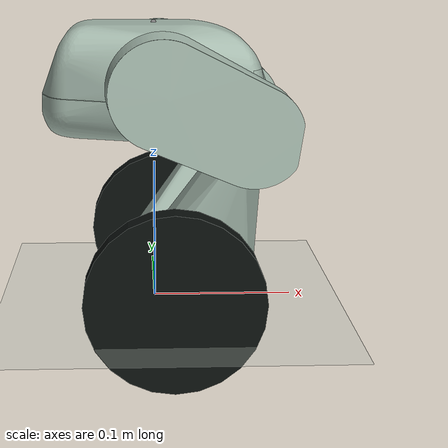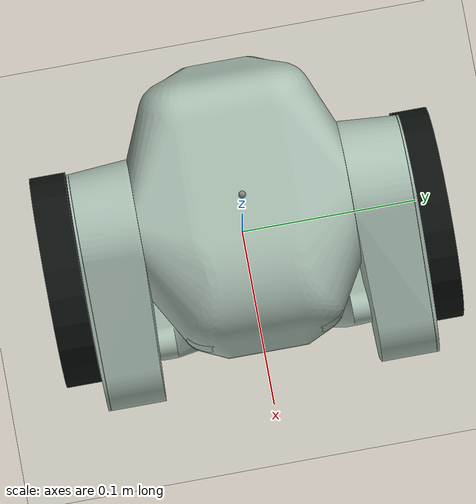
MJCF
<mujoco model="clanky_tpu120_r2_wide_current"><default><geom friction="0.8 0.005 0.0001" solref="0.003 1" solimp=".95 .99 .001" contype="2" conaffinity="1" /><joint damping=".002" frictionloss="0.002" /></default><compiler angle="radian" autolimits="true" /><option timestep="0.0005" integrator="implicitfast" iterations="100" gravity="0 0 -9.81" /><visual><global offwidth="1280" offheight="960" /></visual><worldbody><geom name="ground" type="plane" size="4 4 .1" rgba=".78 .82 .78 1" contype="1" conaffinity="2" /><light pos="0 -1 2" dir="0 0 -1" /><body name="chassis" pos="0 0 .16"><inertial pos="-0.007088788595245197 3.346226951463433e-05 0.0012456052895287017" mass="1.0140931288372268" fullinertia="0.001612631556069617 0.0013770122860254754 0.002105359859529145 1.3409104818414568e-05 1.3418905719794236e-06 5.359372631586237e-06" /><freejoint name="root" /><site name="imu" pos="0 0 .04" size=".002" /><body name="left_upper" pos="0.005 0.052 0" quat="0.979045472485 0 0.20364175114 0"><inertial pos="0.018345778052526365 0.011502012426947107 1.3641574683750698e-05" mass="0.16296319942458637" fullinertia="0.00010304237773178683 0.00022607726737685678 0.00022338134471558616 -2.8743198339436925e-05 -4.7397183771536077e-07 1.0736371327263606e-06" /><joint name="left_hip" type="hinge" axis="0 1 0" ref="0.4101523742186677" range="-2.6 2.6" armature="0.0016799999999999999" /><site name="left_spring_upper" pos="0.00448187746169 0.0295 0" size=".002" /><body name="left_lower" pos="0.0644818774617 0 0" quat="0.690305372395 0 0.723518135808 0"><inertial pos="0.08351495589688286 -0.0032891629352024086 0.011840999369046352" mass="0.18127660330246056" fullinertia="0.00011479638650417802 0.0005743556869753018 0.000568679210607304 0.00010970142778112618 -7.317853392199998e-05 2.4685320133211374e-05" /><joint name="passive_left_knee" type="hinge" axis="0 1 0" ref="1.6177705859930382" range=".35 2.36" /><site name="left_spring_lower" pos="0.025 0.0295 0" size=".002" /><site name="left_close_lower" pos="-0.0238429659986 0.017 0.00274098018759" size=".002" /><body name="left_wheel" pos="0.119119350791 0.023 0" quat="0.528501849317 0 -0.848932149979 0"><inertial pos="-7.284069370613512e-05 0.0015570811011392743 -3.870608497259675e-18" mass="0.2760484864087265" fullinertia="0.0002948212930239215 0.00023730789942063082 0.0002943613630200138 4.467870723836161e-07 6.60686822223394e-20 -4.157828030553723e-20" /><joint name="left_wheel" type="hinge" axis="0 1 0" damping=".0003" frictionloss=".001" armature="0.0001275" /><geom name="left_tire" type="cylinder" size="0.06 0.01" quat=".70710678 .70710678 0 0" condim="4" rgba=".045 .065 .055 1" priority="1" pos="0 0.028 0" /></body><geom name="left_slim_lower_pod_ground" type="mesh" mesh="left_slim_lower_pod_ground_mesh" rgba="0.66 0.74 0.69 1" mass="0" contype="2" conaffinity="1" /><geom name="left_wheel_motor_mount_lid_ground" type="mesh" mesh="left_wheel_motor_mount_lid_ground_mesh" rgba="0.66 0.74 0.69 1" mass="0" contype="2" conaffinity="1" /></body><geom name="left_structural_thigh_ground" type="mesh" mesh="left_structural_thigh_ground_mesh" rgba="0.66 0.74 0.69 1" mass="0" contype="2" conaffinity="1" /><geom name="left_thigh_lid_ground" type="mesh" mesh="left_thigh_lid_ground_mesh" rgba="0.66 0.74 0.69 1" mass="0" contype="2" conaffinity="1" /></body><body name="left_tie" pos="0.016471528727 0.052 0.0163830408858" quat="0.98501338755 0 0.172477901041 0"><inertial pos="0.03224093873084655 0.017 -8.87981627051699e-19" mass="0.01708538558880156" fullinertia="1.2530978783531078e-07 6.967718525437567e-06 6.887969765839067e-06 -1.8277205526828767e-21 1.855422313347536e-22 1.0932410532404852e-23" /><joint name="passive_left_tie" type="hinge" axis="0 1 0" ref="0.34668943872575453" /><site name="left_close_tie" pos="0.0644818774617 0.017 0" size=".002" /></body><body name="right_upper" pos="0.005 -0.052 0" quat="0.979045472485 0 0.20364175114 0"><inertial pos="0.01797581572530148 -0.010760868605805165 1.3366477672189618e-05" mass="0.1663171637415588" fullinertia="0.00010751486535604659 0.00022721017114748753 0.00022895990317281853 3.095898615493378e-05 -4.7479429158855955e-07 -1.0719895146813854e-06" /><joint name="right_hip" type="hinge" axis="0 1 0" ref="0.4101523742186677" range="-2.6 2.6" armature="0.0016799999999999999" /><site name="right_spring_upper" pos="0.00448187746169 -0.0295 0" size=".002" /><body name="right_lower" pos="0.0644818774617 0 0" quat="0.690305372395 0 0.723518135808 0"><inertial pos="0.08351495589688286 0.0032891629352024086 0.011840999369046352" mass="0.18127660330246056" fullinertia="0.00011479638650417802 0.0005743556869753018 0.000568679210607304 -0.00010970142778112618 -7.317853392199998e-05 -2.4685320133211374e-05" /><joint name="passive_right_knee" type="hinge" axis="0 1 0" ref="1.6177705859930382" range=".35 2.36" /><site name="right_spring_lower" pos="0.025 -0.0295 0" size=".002" /><site name="right_close_lower" pos="-0.0238429659986 -0.017 0.00274098018759" size=".002" /><body name="right_wheel" pos="0.119119350791 -0.023 0" quat="0.528501849317 0 -0.848932149979 0"><inertial pos="-7.284069370613832e-05 -0.0015570811011392622 9.289878865154508e-18" mass="0.2760484864087265" fullinertia="0.00029482129302392117 0.00023730789942063058 0.0002943613630200137 -4.467870723836141e-07 2.994133081984694e-20 7.474813004018382e-20" /><joint name="right_wheel" type="hinge" axis="0 1 0" damping=".0003" frictionloss=".001" armature="0.0001275" /><geom name="right_tire" type="cylinder" size="0.06 0.01" quat=".70710678 .70710678 0 0" condim="4" rgba=".045 .065 .055 1" priority="1" pos="0 -0.028 0" /></body><geom name="right_slim_lower_pod_ground" type="mesh" mesh="right_slim_lower_pod_ground_mesh" rgba="0.66 0.74 0.69 1" mass="0" contype="2" conaffinity="1" /><geom name="right_wheel_motor_mount_lid_ground" type="mesh" mesh="right_wheel_motor_mount_lid_ground_mesh" rgba="0.66 0.74 0.69 1" mass="0" contype="2" conaffinity="1" /></body><geom name="right_structural_thigh_ground" type="mesh" mesh="right_structural_thigh_ground_mesh" rgba="0.66 0.74 0.69 1" mass="0" contype="2" conaffinity="1" /><geom name="right_thigh_lid_ground" type="mesh" mesh="right_thigh_lid_ground_mesh" rgba="0.66 0.74 0.69 1" mass="0" contype="2" conaffinity="1" /></body><body name="right_tie" pos="0.016471528727 -0.052 0.0163830408858" quat="0.98501338755 0 0.172477901041 0"><inertial pos="0.03224093873084655 -0.017 -8.87981627051699e-19" mass="0.01708538558880156" fullinertia="1.2530978783531078e-07 6.967718525437567e-06 6.887969765839067e-06 1.8277205526828767e-21 1.855422313347536e-22 -1.0932410532404852e-23" /><joint name="passive_right_tie" type="hinge" axis="0 1 0" ref="0.34668943872575453" /><site name="right_close_tie" pos="0.0644818774617 -0.017 0" size=".002" /></body><geom name="streamlined_upper_shell_ground" type="mesh" mesh="streamlined_upper_shell_ground_mesh" rgba="0.66 0.74 0.69 1" mass="0" contype="2" conaffinity="1" /><geom name="streamlined_lower_tray_ground" type="mesh" mesh="streamlined_lower_tray_ground_mesh" rgba="0.66 0.74 0.69 1" mass="0" contype="2" conaffinity="1" /><geom name="flush_visor_ground" type="mesh" mesh="flush_visor_ground_mesh" rgba="0.66 0.74 0.69 1" mass="0" contype="2" conaffinity="1" /><geom name="visor_light_0_ground" type="mesh" mesh="visor_light_0_ground_mesh" rgba="0.66 0.74 0.69 1" mass="0" contype="2" conaffinity="1" /><geom name="visor_light_1_ground" type="mesh" mesh="visor_light_1_ground_mesh" rgba="0.66 0.74 0.69 1" mass="0" contype="2" conaffinity="1" /></body></worldbody><equality><connect name="left_closure" site1="left_close_lower" site2="left_close_tie" solref=".001 1" solimp=".999 .9999 .0001" /><connect name="right_closure" site1="right_close_lower" site2="right_close_tie" solref=".001 1" solimp=".999 .9999 .0001" /></equality><tendon><spatial name="left_spring" stiffness="5500" springlength="0.064 1" damping="0.0" width=".003" rgba=".9 .64 .2 1"><site site="left_spring_upper" /><site site="left_spring_lower" /></spatial><spatial name="right_spring" stiffness="5500" springlength="0.064 1" damping="0.0" width=".003" rgba=".9 .64 .2 1"><site site="right_spring_upper" /><site site="right_spring_lower" /></spatial></tendon><sensor><gyro name="gyro" site="imu" /><accelerometer name="accelerometer" site="imu" /></sensor><asset><mesh name="streamlined_upper_shell_ground_mesh" vertex="-0.078 0.0149453413556 -0.00727574189609 -0.078 0.014673320058 -0.0072029418158 -0.078 0.0152142145593 -0.00735942367247 -0.078 -0.0135626194019 -0.00702264668647 -0.078 -0.0132815375022 -0.00700566396483 -0.078 0.0143985908699 -0.00714114124059 -0.078 0.0154795045593 -0.00745385172574 -0.078 -0.0162496153652 -0.0078 -0.078 -0.0159976241928 -0.00767431827782 -0.078 -0.0157407820435 -0.00755887324554 -0.078 -0.0154795045593 -0.00745385172574 -0.078 -0.0152142145593 -0.00735942367247 -0.078 -0.0149453413556 -0.00727574189609 -0.078 -0.014673320058 -0.0072029418158 -0.078 -0.0143985908699 -0.00714114124059 -0.078 -0.0141215983764 -0.00709044017876 -0.078 -0.0138427908251 -0.00705092067658 -0.078 -0.013 -0.007 -0.078 0.013 -0.007 -0.078 0.0157407820435 -0.00755887324554 -0.078 0.0162496153652 -0.0078 -0.078 0.0159976241928 -0.00767431827782 -0.078 0.0141215983764 -0.00709044017876 -0.078 0.0138427908251 -0.00705092067658 -0.078 0.0132815375022 -0.00700566396483 -0.078 0.0135626194019 -0.00702264668647 -0.073242010042 -0.0295488277766 -0.0078 -0.0732420100405 0.0295488277808 -0.0078 -0.0728098857578 -0.0306864948826 -0.0078 -0.0728098857559 0.0306864948871 -0.0078 -0.0725697295879 -0.0312535782957 -0.0078 -0.0725697295869 0.0312535782979 -0.0078 -0.0723114087793 -0.0318125264634 -0.0078 -0.0723114087793 0.0318125264634 -0.0078 -0.0716711595841 -0.0330895572076 -0.0078 -0.0713714877214 0.0336565784371 -0.0078 -0.0713142528181 -0.0337626179975 -0.00498987349939 -0.0713142528181 0.0337626179975 -0.00498987349939 -0.0709906012231 -0.0343486122951 -0.0078 -0.0704482271371 0.0352789829537 -0.0078 -0.0703602772058 -0.0354238308478 -0.0078 -0.0702633063077 -0.0355816155826 -0.00217229401974 -0.0702633063077 0.0355816155826 -0.00217229401974 -0.0698611423677 -0.036214800425 -0.0078 -0.0696353730615 0.0365555934793 -0.0078 -0.0695386422811 -0.0363851542737 0.00282179245141 -0.0693372260851 -0.0369899427288 -0.0078 -0.0691514730684 -0.0372517445667 0.000560045973195 -0.0691514730684 -0.0372517445667 -0.00547229577633 -0.0691514730684 0.0372517445667 -0.00547229577798 -0.0691514730684 0.0372517445667 0.000560045973195 -0.0689282468776 0.0375576525992 -0.0078 -0.0687867565191 -0.0377467359858 -0.0078 -0.0687856136483 -0.0302900441725 0.0153489278514 -0.0687856136483 -0.0349200533018 0.0107189187221 -0.0687856136483 -0.032833056786 0.0132619313356 -0.0687856136483 -0.0273887419369 0.0168997062256 -0.0687856136483 -0.036470831676 0.00781761648649 -0.0687856136483 -0.0242406456645 0.0178546707555 -0.0687856136483 -0.0374257962059 0.00466952021414 -0.0687856136483 0.036470831676 0.00781761648649 -0.0687856136483 0.0273887419369 0.0168997062256 -0.0687856136483 0.0302900441725 0.0153489278514 -0.0687856136483 0.032833056786 0.0132619313356 -0.0687856136483 0.0242406456645 0.0178546707555 -0.0687856136483 0.0349200533018 0.0107189187221 -0.0687856136483 0.0374257962059 0.00466952021414 -0.0683829751863 -0.0381844716032 0.00394639296565 -0.0683829751863 0.0381844716032 0.00394639296565 -0.0683452435257 0.0378026236772 0.00650068635164 -0.0682512576642 0.0384298176588 -0.0078 -0.0682082414006 -0.0384825266202 -0.0078 -0.0679719380276 -0.0387665554282 0.00313701619482 -0.0679719380276 0.0387665554282 0.00313701619482 -0.0679393376168 0.0215164934837 0.0204919497565 -0.0679393376168 -0.0215164934837 0.0204919497565 -0.0678948192205 -0.0387738891767 0.0049908059565 -0.0678948192205 0.0387738891767 0.0049908059565 -0.0676005941038 -0.0391946169209 -0.0078 -0.0675338397109 0.0392692765976 -0.0078 -0.0673548052728 0.0394661741301 -0.00513085838615 -0.0673548052728 -0.0394661741301 -0.00513085838357 -0.0673548052728 -0.0394661741301 0.00198031767117 -0.0673548052728 0.0394661741301 0.00198031767053 -0.0672714041166 -0.0355455063092 0.0157170772475 -0.0672714041166 -0.0374698896644 0.0128370340452 -0.0672714041166 -0.0387954279642 0.00963690151479 -0.0669632555177 -0.0398803966559 -0.0078 -0.0669625819654 -0.0398810904048 0.00507508224232 -0.0669625819654 0.0398810904048 0.00507508224232 -0.0668528338327 0.0399932907442 -0.0078 -0.0668405547377 0.0220991294925 0.0231997593104 -0.0668405547377 -0.0220991294925 0.0231997593104 -0.0662416704027 -0.0405887816382 -0.0078 -0.0662114341869 0.0406170047806 -0.0078 -0.0660822635568 -0.040736317958 0.00657279938017 -0.0660822635568 0.040736317958 0.00657279938017 -0.0659060674581 0.0224956804278 0.0252521955682 -0.0659060674581 -0.0224956804278 0.0252521955682 -0.0656368232151 -0.0328941392027 0.0226791746806 -0.0656368232151 -0.0296892848076 0.0243922050665 -0.0656368232151 -0.0357032175024 0.0203738236992 -0.0656368232151 -0.0262118152594 0.0254470838837 -0.0656368232151 -0.0380085684838 0.0175647453995 -0.0656368232151 -0.0397215988697 0.0143598910044 -0.0656368232151 -0.0407764776869 0.0108824214562 -0.0656368232151 0.0397215988697 0.0143598910044 -0.0656368232151 0.0407764776869 0.0108824214562 -0.0656368232151 0.0380085684838 0.0175647453995 -0.0656368232151 0.0357032175024 0.0203738236992 -0.0656368232151 0.0328941392027 0.0226791746806 -0.0656368232151 0.0296892848076 0.0243922050665 -0.0656368232151 0.0262118152594 0.0254470838837 -0.065636823215 -0.0169465256807 0.0258032729144 -0.065636823215 0.0169465256807 0.0258032729144 -0.0656225058704 -0.0411450309502 -0.0078 -0.0655437782978 0.0412126143301 -0.0078 -0.0654483116026 -0.0412039408694 0.00937305338946 -0.0654483116026 0.0412039408694 0.00937305338946 -0.0653856607867 0.0413463120681 -0.00570728465975 -0.0653856607867 -0.0413463120681 -0.00570728465612 -0.0653856607867 -0.0413463120681 0.00496935152972 -0.0653856607867 0.0413463120681 0.00496935152899 -0.0652582031096 -0.0414521468203 0.00782263961409 -0.0652582031096 0.0414521468203 0.00782263961409 -0.0650705901925 -0.0415142540368 0.00993230526732 -0.0650705901925 0.0415142540368 0.00993230526732 -0.0650037127177 0.0228071263049 0.0270318942201 -0.0650037127177 -0.0228071263049 0.0270318942201 -0.0648511297063 0.0417790411887 -0.0078 -0.0648508683256 -0.0417792457797 -0.0078 -0.0647714133316 -0.0410245755813 0.0140010800728 -0.0647714133316 0.0396019383596 0.0174356301366 -0.0644900173565 -0.042055591905 0.00886478662673 -0.0644900173565 0.042055591905 0.00886478662673 -0.0641601431062 0.0230456505397 0.0285304222234 -0.0641601431062 -0.0230456505397 0.0285304222234 -0.0641352097298 0.0423158232219 -0.0078 -0.064073027292 -0.042360312327 -0.0078 -0.0638726609132 -0.0338864240516 0.0257401764328 -0.0638726609132 -0.0305350959143 0.0275314986661 -0.0638726609132 -0.0368238876568 0.0233294623542 -0.0638726609132 -0.0268986930995 0.028634589361 -0.0638726609132 -0.0392346017355 0.020391998749 -0.0638726609132 -0.0410259239688 0.0170406706117 -0.0638726609132 -0.0421290146636 0.0134042677968 -0.0638726609132 0.0410259239688 0.0170406706117 -0.0638726609132 0.0421290146636 0.0134042677968 -0.0638726609132 0.0392346017355 0.020391998749 -0.0638726609132 0.0368238876568 0.0233294623542 -0.0638726609132 0.0338864240516 0.0257401764328 -0.0638726609132 0.0305350959143 0.0275314986661 -0.0638726609132 0.0268986930995 0.028634589361 -0.0638726609132 -0.0173377202482 0.0290070575525 -0.0638726609132 0.0173377202482 0.0290070575525 -0.0638247140429 -0.0424413325125 0.0115807174651 -0.0638247140429 0.0424413325125 0.0115807174651 -0.0637766738191 -0.0425679567253 0.00973429612158 -0.0637766738191 0.0425679567253 0.00973429612158 -0.0634974551716 -0.0426630613641 0.011967096342 -0.0634974551716 0.0426630613641 0.011967096342 -0.0633980784624 0.0428231483147 -0.0078 -0.0633748790926 0.0232298726782 0.029793713909 -0.0633748790926 -0.0232298726782 0.029793713909 -0.063257323465 -0.0429152843573 -0.0078 -0.0632283629845 0.0429340634766 -0.00706288501488 -0.0632283629845 -0.0429340634766 -0.00706288501014 -0.0632283629845 -0.0429340634766 0.00744194251287 -0.0632283629845 0.0429340634766 0.00744194251208 -0.0631165734183 -0.0430059925121 0.0104609418018 -0.0631165734183 0.0430059925121 0.0104609418018 -0.0629398420301 -0.0386236904245 0.0232040521233 -0.0629398420301 -0.040780050407 0.0199768313657 -0.0629398420301 -0.0422653769857 0.0163909358067 -0.0626419933516 0.0433018265108 -0.0078 -0.0625645378011 0.0233884771653 0.0309753656056 -0.0625645378011 -0.0233884771653 0.0309753656056 -0.0625076606301 -0.0433828884092 0.0110696020443 -0.0625076606301 0.0433828884092 0.0110696020443 -0.0622490374358 -0.0435358062944 -0.0078 -0.0619724201361 -0.0312205883114 0.0302283252424 -0.0619724201361 -0.0347141867015 0.0283609579737 -0.0619724201361 -0.0274298132815 0.031378244235 -0.0619724201361 -0.0377763512231 0.0258479044978 -0.0619724201361 -0.0402894046989 0.0227857399762 -0.0619724201361 -0.0421567719676 0.0192921415861 -0.0619724201361 -0.0433066909603 0.0155013665563 -0.0619724201361 0.0421567719676 0.0192921415861 -0.0619724201361 0.0433066909603 0.0155013665563 -0.0619724201361 0.0402894046989 0.0227857399762 -0.0619724201361 0.0377763512231 0.0258479044978 -0.0619724201361 0.0347141867015 0.0283609579737 -0.0619724201361 0.0274298132815 0.031378244235 -0.0619724201361 0.0312205883114 0.0302283252424 -0.0619724201361 -0.0176156540738 0.0317665244096 -0.0619724201361 0.0176156540738 0.0317665244096 -0.0619285410815 -0.0436224259497 0.013579857862 -0.0618845927099 -0.0437445942883 0.0116355386894 -0.0618845927099 0.0437445942883 0.0116355386894 -0.0618692700057 0.043753207757 -0.0078 -0.0618135568981 0.0235120122128 0.0319689977294 -0.0618135568981 -0.0235120122128 0.0319689977294 -0.0616121710967 -0.0437978185589 0.0138609953145 -0.0612472937208 -0.0440923133339 0.0121591545761 -0.0612472937208 0.0440923133339 0.0121591545761 -0.0611298088299 -0.0441541681374 -0.0078 -0.0611200017663 0.0236097237195 0.0328069890375 -0.0611200017663 -0.0236097237195 0.0328069890375 -0.0610821642744 0.044179063425 -0.0078 -0.0609700504679 -0.0367027449012 0.028300868735 -0.0609700504679 -0.0395593880237 0.0254442256126 -0.0609700504679 -0.0418038381992 0.0220851685653 -0.0609700504679 -0.0433498423577 0.0183527843705 -0.0609700504679 0.0433498423577 0.0183527843705 -0.0609700504679 0.0418038381992 0.0220851685653 -0.0608729413198 0.0442871256102 -0.00594978849164 -0.0608729413198 0.0442871256102 0.00937699086152 -0.0608729413198 -0.0442871256102 -0.00594978848663 -0.0608729413198 -0.0442871256102 0.00937699086235 -0.060595719867 -0.0444272512519 0.0126410277589 -0.060595719867 0.0444272512519 0.0126410277589 -0.0604096518111 0.0236965320283 0.0335921921782 -0.0604096518111 -0.0236965320283 0.0335921921782 -0.0602827862325 0.0445814532965 -0.0078 -0.0599325821462 -0.0354159843832 0.0305416361999 -0.0599325821462 -0.0317852405693 0.0324823092258 -0.0599325821462 -0.0278456540878 0.0336773696772 -0.0599325821462 -0.038598357871 0.027929929775 -0.0599325821462 -0.0412100642959 0.0247475562871 -0.0599325821462 -0.0431507373218 0.0211168124733 -0.0599325821462 -0.0443457977732 0.0171772259918 -0.0599325821462 0.0431507373218 0.0211168124733 -0.0599325821462 0.0443457977732 0.0171772259918 -0.0599325821462 0.0412100642959 0.0247475562871 -0.0599325821462 0.038598357871 0.027929929775 -0.0599325821462 0.0354159843832 0.0305416361999 -0.0599325821462 0.0278456540878 0.0336773696772 -0.0599325821462 0.0317852405693 0.0324823092258 -0.0599325821462 -0.0178114656183 0.0340808922589 -0.0599325821462 0.0178114656183 0.0340808922589 -0.0599298595088 -0.0447506068128 0.0130818948648 -0.0599298595088 0.0447506068128 0.0130818948648 -0.0597537807586 -0.0448332158842 -0.0078 -0.0596825019825 0.0237742250982 0.0343253288427 -0.0596825019825 -0.0237742250982 0.0343253288427 -0.0595929527883 -0.0448059582982 0.0153569775705 -0.0595929527883 0.0448059582982 0.0153569775705 -0.0592511232072 -0.0449606299159 0.0155644296926 -0.0592511232072 0.0449606299159 0.0155644296926 -0.0592497330431 -0.0450635631759 0.01348263525 -0.0592497330431 0.0450635631759 0.01348263525 -0.059201126072 0.0450853185514 -0.0078 -0.0589385914646 0.0238445709831 0.0350073073738 -0.0589385914646 -0.0238445709831 0.0350073073738 -0.0588600581516 -0.0374176009854 0.0302215079955 -0.0585553926557 -0.0453672799657 0.0138442559337 -0.0585553926557 0.0453672799657 0.0138442559337 -0.0583277148134 -0.0454637546691 -0.0078 -0.0581780032455 0.0239093032518 0.035639203579 -0.0581780032455 -0.0239093032518 0.035639203579 -0.0578469219527 -0.0456628860732 0.0141678772876 -0.0578469219527 0.0456628860732 0.0141678772876 -0.0577527133421 -0.0322695807286 0.0343095274033 -0.0577527133421 -0.0360312680633 0.0322988636064 -0.0577527133421 -0.028187912252 0.0355476879552 -0.0577527133421 -0.0393284145042 0.0295929654532 -0.0577527133421 -0.0420343126574 0.0262958190123 -0.0577527133421 -0.0440449764543 0.0225341316775 -0.0577527133421 -0.0452831370062 0.0184524632009 -0.0577527133421 0.0440449764543 0.0225341316775 -0.0577527133421 0.0452831370062 0.0184524632009 -0.0577527133421 0.0420343126574 0.0262958190123 -0.0577527133421 0.0393284145042 0.0295929654532 -0.0577527133421 0.0360312680633 0.0322988636064 -0.0577527133421 0.028187912252 0.0355476879552 -0.0577527133421 0.0322695807286 0.0343095274033 -0.0577527133421 -0.0179573389823 0.0359657636616 -0.0577527133421 0.0179573389823 0.0359657636616 -0.0574008634935 0.0239701078095 0.036222242523 -0.0574008634935 -0.0239701078095 0.036222242523 -0.0571244354788 0.0459514731534 0.0144547194605 -0.0570764446755 -0.0458644073748 0.0166263333989 -0.0566109706747 -0.0304498283253 0.0358029246235 -0.0566109706747 -0.0344562656331 0.0341434039485 -0.0566109706747 -0.0380619639672 0.0317341533329 -0.0566109706747 -0.0411283582565 0.0286677590436 -0.0566109706747 -0.043537608872 0.0250620607095 -0.0566109706747 -0.0451971295471 0.0210556234018 -0.0566109706747 0.0304498283253 0.0358029246235 -0.0566109706747 0.0344562656331 0.0341434039485 -0.0566073407534 0.0240286110627 0.036757781268 -0.0566073407534 -0.0240286110627 0.036757781268 -0.0563880781271 0.0462340897926 0.0147060895162 -0.0557976449738 0.0240863693719 0.0372472925377 -0.0557976449738 -0.0240863693719 0.0372472925377 -0.0554354357916 -0.0284962908158 0.0370171613175 -0.0554354357916 -0.0327121023235 0.0357383089235 -0.0554354357916 -0.0365974165878 0.0336615651552 -0.0554354357916 -0.0400029229359 0.0308667383244 -0.0554354357916 -0.0427977497667 0.0274612319763 -0.0554354357916 -0.044874493535 0.023575917712 -0.0554354357916 -0.046153345929 0.0193601062043 -0.0554354357916 0.044874493535 0.023575917712 -0.0554354357916 0.046153345929 0.0193601062043 -0.0554354357916 0.0427977497667 0.0274612319763 -0.0554354357916 0.0400029229359 0.0308667383244 -0.0554354357916 0.0284962908158 0.0370171613175 -0.0554354357916 0.0327121023235 0.0357383089235 -0.0554354357916 0.0365974165878 0.0336615651552 -0.0554354357916 -0.0180839948313 0.0374489769793 -0.0554354357916 0.0180839948313 0.0374489769793 -0.0549720263772 0.0241448597368 0.0376923492732 -0.0549720263772 -0.0241448597368 0.0376923492732 -0.0542268901218 -0.0308206885376 0.0370688016394 -0.0542268901218 -0.0349523793664 0.035357399257 -0.0542268901218 -0.0418330620736 0.0297105688944 -0.0542268901218 -0.0386708028918 0.0328728280762 -0.0542268901218 -0.0460290356367 0.0218604545403 -0.0542268901218 0.0460290356367 0.0218604545403 -0.0542268901218 0.0443176332544 0.025992145369 -0.0542268901218 0.0308206885376 0.0370688016394 -0.0542268901218 0.0386708028918 0.0328728280762 -0.0542268901218 0.0349523793664 0.035357399257 -0.0541307741842 0.0242054716593 0.0380946100564 -0.0541307741842 -0.0242054716593 0.0380946100564 -0.0532742152025 0.0242695001306 0.0384558053732 -0.0532742152025 -0.0242695001306 0.0384558053732 -0.0529862826507 -0.0288060903349 0.0381224110526 -0.0529862826507 -0.0331469572038 0.0368056235309 -0.0529862826507 -0.0435317793804 0.0282830202252 -0.0529862826507 -0.0371475231528 0.0346672764528 -0.0529862826507 -0.0469869139802 0.0199415874073 -0.0529862826507 -0.0456701264585 0.0242824542762 -0.0529862826507 -0.0406540484448 0.0317895455172 -0.0529862826507 0.0456701264585 0.0242824542762 -0.0529862826507 0.0469869139802 0.0199415874073 -0.0529862826507 0.0406540484448 0.0317895455172 -0.0529862826507 0.0435317793804 0.0282830202252 -0.0529862826507 0.0288060903349 0.0381224110526 -0.0529862826507 0.0331469572038 0.0368056235309 -0.0529862826507 0.0371475231528 0.0346672764528 -0.0529862826507 -0.0182188045428 0.038567035841 -0.0529862826507 0.0182188045428 0.038567035841 -0.0524027122916 0.0243381396902 0.0387777246884 -0.0524027122916 -0.0243381396902 0.0387777246884 -0.0522565062987 0.0266360504866 0.0387152263592 -0.0522565062987 -0.0266360504866 0.0387152263592 -0.0517147204993 -0.0312035343438 0.0379922626007 -0.0517147204993 -0.0354511967839 0.0362328232039 -0.0517147204993 -0.0392739920026 0.0336785130868 -0.0517147204993 0.0312035343438 0.0379922626007 -0.0517147204993 0.0392739920026 0.0336785130868 -0.0517147204993 0.0354511967839 0.0362328232039 -0.0515166627142 0.0244124795055 0.0390622043087 -0.0515166627142 -0.0244124795055 0.0390622043087 -0.0506164963842 0.0244934994204 0.0393111160056 -0.0506164963842 -0.0244934994204 0.0393111160056 -0.0504134584563 -0.0291465105183 0.0389056687218 -0.0504134584563 -0.0442621744742 0.0288057049904 -0.0504134584563 -0.0336023349395 0.0375540092091 -0.0504134584563 -0.0413082336676 0.0324050922792 -0.0504134584563 -0.0377088463789 0.0353590330858 -0.0504134584563 0.0291465105183 0.0389056687218 -0.0504134584563 0.0336023349395 0.0375540092091 -0.0504134584563 0.0413082336676 0.0324050922792 -0.0504134584563 0.0377088463789 0.0353590330858 -0.0504134584563 0.0442621744742 0.0288057049904 -0.0504134584563 -0.0183844557808 0.0393620683421 -0.0504134584563 0.0183844557808 0.0393620683421 -0.049702674021 0.024582066924 0.0395263563747 -0.049702674021 -0.024582066924 0.0395263563747 -0.0495997440637 0.0269379532544 0.0394331713104 -0.0495997440637 -0.0269379532544 0.0394331713104 -0.0490838875962 -0.0316236097886 0.0386174713016 -0.0490838875962 0.0316236097886 0.0386174713016 -0.0490838875962 0.0359770752233 0.0368142068693 -0.0490838875962 0.039895090622 0.0341962726618 -0.0490838875962 0.0432270887347 0.0308642745491 -0.0487756852209 0.0246789349906 0.0397098369042 -0.0487756852209 -0.0246789349906 0.0397098369042 -0.0478360464543 0.0247847407426 0.0398634747305 -0.0478360464543 -0.0247847407426 0.0398634747305 -0.047727523116 -0.0295395738661 0.0394122134436 -0.047727523116 -0.0340994429553 0.0380289923269 -0.047727523116 -0.0383018425131 0.0357827629359 -0.047727523116 0.0295395738661 0.0394122134436 -0.047727523116 0.0340994429553 0.0380289923269 -0.047727523116 0.0383018425131 0.0357827629359 -0.047727523116 -0.0185981011578 0.0398792701146 -0.047727523116 0.0185981011578 0.0398792701146 -0.0473070670524 0.0272381101136 0.0398194301022 -0.0468842989986 0.0249000048896 0.0399891840544 -0.0468842989986 -0.0249000048896 0.0399891840544 -0.0468293798748 0.0273058717162 0.039877730602 -0.0468293798748 -0.0273058717162 0.039877730602 -0.0461879988646 0.0273997900605 0.0399454411867 -0.0461879988646 -0.0273997900605 0.0399454411867 -0.0459210068159 0.0250251318986 0.0400888681951 -0.0459210068159 -0.0250251318986 0.0400888681951 -0.0449410172509 -0.0323604628593 0.0390968824933 -0.0449410172509 -0.0368521476657 0.0372363657226 -0.0449410172509 0.0323604628593 0.0390968824933 -0.0449410172509 0.0368521476657 0.0372363657226 -0.0446196716621 0.0252077933424 0.0401845514992 -0.0446196716621 -0.0252077933424 0.0401845514992 -0.0431341703329 0.0254352931442 0.0402463644061 -0.0431341703329 -0.0254352931442 0.0402463644061 -0.0420680453869 -0.0305330626342 0.0397791922812 -0.0420680453869 0.0305330626342 0.0397791922812 -0.0420680453869 -0.0192080674286 0.0402639971443 -0.0420680453869 0.0192080674286 0.0402639971443 -0.0418481943827 0.0281241663917 0.0401435182907 -0.0418481943827 -0.0281241663917 0.0401435182907 -0.0416279442552 0.0256860776189 0.0402655199049 -0.0416279442552 -0.0256860776189 0.0402655199049 -0.0408826904159 -0.0331868898865 0.0391679603007 -0.0408826904159 0.0331868898865 0.0391679603007 -0.040835345319 0.0283148388855 0.0401382897384 -0.040835345319 -0.0283148388855 0.0401382897384 -0.0396866802819 0.0310188621366 0.0397469278147 -0.0396866802819 0.0285402799686 0.0401145907363 -0.0396866802819 -0.0285402799686 0.0401145907363 -0.0396866802819 -0.0310188621366 0.0397469278147 -0.0307923291574 -0.0578 -0.000741062403522 -0.0307923291574 0.0578 -0.000741062403523 -0.0307849131262 0.0578 0.00103922689919 -0.0307849131262 -0.0578 0.00103922689919 -0.030711231058 -0.0578 -0.00251951906511 -0.030711231058 0.0578 -0.00251951906512 -0.0306890013042 0.0578 0.00281694620248 -0.0306890013042 -0.0578 0.00281694620248 -0.030541819383 -0.0578 -0.00429174497714 -0.030541819383 0.0578 -0.00429174497714 -0.0305048308805 0.0578 0.00458769922138 -0.0305048308805 -0.0578 0.00458769922138 -0.0302845130859 -0.0578 -0.00605335743973 -0.0302845130859 0.0578 -0.00605335743973 -0.0302328573071 0.0578 0.00634710689847 -0.0302328573071 -0.0578 0.00634710689847 -0.0299399484831 -0.0578 -0.0078 -0.0299399484831 0.0578 -0.0078 -0.0298737531722 0.0578 0.00809081823331 -0.0298737531722 -0.0578 0.00809081823331 -0.0294284065375 0.0578 0.00981452104233 -0.0294284065375 -0.0578 0.00981452104233 -0.0288979187414 0.0578 0.0115139526229 -0.0288979187414 -0.0578 0.0115139526229 -0.0282836016758 0.0578 0.013184910295 -0.0282836016758 -0.0578 0.013184910295 -0.0275869745417 0.0578 0.0148232617942 -0.0275869745417 -0.0578 0.0148232617942 -0.0268097600922 0.0578 0.0164249554909 -0.0268097600922 -0.0578 0.0164249554909 -0.025953880372 0.0578 0.0179860304102 -0.025953880372 -0.0578 0.0179860304102 -0.0250214519646 0.0578 0.0195026260267 -0.0250214519646 -0.0578 0.0195026260267 -0.0240147807576 0.0578 0.0209709918122 -0.0240147807576 -0.0578 0.0209709918122 -0.0229363562406 0.0578 0.0223874965103 -0.0229363562406 -0.0578 0.0223874965103 -0.0217888453482 0.0578 0.0237486371169 -0.0217888453482 -0.0578 0.0237486371169 -0.0205750858654 0.0578 0.0250510475425 -0.0205750858654 -0.0578 0.0250510475425 -0.0192980794092 0.0578 0.0262915069371 -0.0192980794092 -0.0578 0.0262915069371 -0.0179609840059 0.0578 0.027466947655 -0.0179609840059 -0.0578 0.027466947655 -0.0165671062812 0.0578 0.0285744628411 -0.0165671062812 -0.0578 0.0285744628411 -0.015119893283 0.0578 0.0296113136196 -0.015119893283 -0.0578 0.0296113136196 -0.0136229239571 0.0578 0.0305749358673 -0.0136229239571 -0.0578 0.0305749358673 -0.012079900296 0.0578 0.0314629465543 -0.012079900296 -0.0578 0.0314629465543 -0.0104946381844 0.0578 0.0322731496377 -0.0104946381844 -0.0578 0.0322731496377 -0.00887105796215 0.0578 0.0330035414919 -0.00887105796215 -0.0578 0.0330035414919 -0.00721317472959 0.0578 0.0336523158642 -0.00721317472959 -0.0578 0.0336523158642 -0.0055250884181 0.0578 0.0342178683408 -0.0055250884181 -0.0578 0.0342178683408 -0.00381097365099 0.0578 0.0346988003153 -0.00381097365099 -0.0578 0.0346988003153 -0.00207506941974 0.0578 0.0350939224469 -0.00207506941974 -0.0578 0.0350939224469 -0.000321668601007 0.0578 0.0354022576018 -0.000321668601006 -0.0578 0.0354022576018 0.00144489265966 0.0578 0.0356230432698 0.00144489265966 -0.0578 0.0356230432698 0.00322024567104 0.0578 0.0357557334497 0.00322024567104 -0.0578 0.0357557334497 0.00499999999999 0.0578 0.0358 0.00499999999999 -0.0578 0.0358 0.00677975432894 0.0578 0.0357557334497 0.00677975432894 -0.0578 0.0357557334497 0.00855510734033 0.0578 0.0356230432698 0.00855510734033 -0.0578 0.0356230432698 0.010321668601 0.0578 0.0354022576018 0.010321668601 -0.0578 0.0354022576018 0.0118433089975 -0.0329709742236 0.039515864771 0.0119240804324 0.0329760935891 0.0395166918732 0.0120750694197 0.0578 0.0350939224469 0.0120750694197 -0.0578 0.0350939224469 0.013810973651 0.0578 0.0346988003153 0.013810973651 -0.0578 0.0346988003153 0.0148982314978 -0.0331125336162 0.0394944601203 0.0148982314978 0.0331125336162 0.0394944601203 0.0153310413761 0.0304176884714 0.0398936848435 0.0153310413761 -0.0304176884714 0.0398936848435 0.0155250884181 0.0578 0.0342178683408 0.0155250884181 -0.0578 0.0342178683408 0.0172131747296 0.0578 0.0336523158642 0.0172131747296 -0.0578 0.0336523158642 0.0172751472291 0.0296382106238 0.0399901468549 0.0172751472291 0.0321589522386 0.0396162301703 0.0172751472291 -0.0321589522386 0.0396162301703 0.0172751472291 -0.0296382106238 0.0399901468549 0.0184684326893 0.029154739728 0.0400357006503 0.0184684326893 -0.029154739728 0.0400357006503 0.0188710579621 0.0578 0.033003541492 0.0188710579621 -0.0578 0.033003541492 0.0194348815241 -0.0311097295036 0.0397241298326 0.0194492248884 0.0311131354743 0.0397227227112 0.0195505382426 -0.0286299325211 0.0400753605573 0.0195577129014 0.028631710075 0.040075089296 0.0196662448597 0.0261284523601 0.0401945591013 0.0196662448597 -0.0261284523601 0.0401945591013 0.0204946381844 0.0578 0.0322731496377 0.0204946381844 -0.0578 0.0322731496377 0.020945420929 -0.0305871369012 0.0397357104258 0.0209526363492 0.0305888587588 0.0397348945105 0.0210617891436 0.0281113599587 0.0400931862885 0.0210617891436 -0.0281113599587 0.0400931862885 0.022079900296 0.0578 0.0314629465543 0.022079900296 -0.0578 0.0314629465543 0.0224659942979 0.030073178625 0.0397253237392 0.0224659942979 0.0275608395799 0.0400979940203 0.0224659942979 -0.0275608395799 0.0400979940203 0.0224659942979 -0.030073178625 0.0397253237392 0.0236229239571 0.0578 0.0305749358673 0.0236229239571 -0.0578 0.0305749358673 0.0236261706381 0.0245843393739 0.0402113337609 0.0236261706381 -0.0245843393739 0.0402113337609 0.0241716280193 -0.0294244096376 0.0397045148557 0.0241716280193 0.0294244096376 0.0397045148557 0.0244636553415 0.0268084010803 0.0400698745675 0.0244636553415 -0.0268084010803 0.0400698745675 0.025119893283 0.0578 0.0296113136196 0.025119893283 -0.0578 0.0296113136196 0.0253050763485 -0.029011243041 0.0396733613081 0.0253050763486 0.029011243041 0.0396733613081 0.0253050763486 -0.0179811845074 0.0401693965854 0.0253050763486 0.0179811845074 0.0401693965854 0.0259339845229 0.0262848827 0.040021370021 0.0259339845229 -0.0262848827 0.040021370021 0.026565234301 0.0235425566324 0.0401171478446 0.0265652343011 -0.0235425566324 0.0401171478446 0.0265671062811 0.0578 0.0285744628411 0.0265671062811 -0.0578 0.0285744628411 0.0279609840059 0.0578 0.027466947655 0.0279609840059 -0.0578 0.027466947655 0.0290542775174 0.0227636493569 0.0399591336615 0.0290542775174 -0.0227636493569 0.0399591336615 0.0292980794092 0.0578 0.0262915069371 0.0292980794092 -0.0578 0.0262915069371 0.0298861396746 0.0250433258031 0.039765994377 0.0305750858654 0.0578 0.0250510475425 0.0305750858654 -0.0578 0.0250510475425 0.0307222754888 -0.0273039223504 0.0393185665643 0.0307222754888 0.0273039223504 0.0393185665643 0.0307222754888 -0.0167284989528 0.0398109504416 0.0307222754888 0.0167284989528 0.0398109504416 0.0311579459989 0.0221937646794 0.0397664988253 0.0311579459989 -0.0221937646795 0.0397664988253 0.0317888453482 0.0578 0.0237486371169 0.0317888453482 -0.0578 0.0237486371169 0.0326948356781 0.028036359436 0.0388252584823 0.0328844998421 0.0249161837003 0.0393745304894 0.0329363562406 0.0578 0.0223874965103 0.0329363562406 -0.0578 0.0223874965103 0.0330743723274 0.0217522486566 0.039542074637 0.0330743723274 -0.0217522486566 0.039542074637 0.0332866616243 -0.025449013538 0.03923833188 0.03349920821 -0.0290621804948 0.0383885651039 0.0340147807576 0.0578 0.0209709918122 0.0340147807576 -0.0578 0.0209709918122 0.0342540794666 -0.0252516626222 0.0391047501487 0.0346902414689 0.0239312530332 0.0391931392552 0.0350120804704 0.0213852631116 0.0392662074679 0.0350120804705 -0.0213852631116 0.0392662074679 0.0350214519646 0.0578 0.0195026260267 0.0350214519646 -0.0578 0.0195026260267 0.0355035159311 0.0274664617642 0.0384283188406 0.035953880372 0.0578 0.0179860304102 0.035953880372 -0.0578 0.0179860304102 0.0363201828637 -0.0261196010087 0.0385652559094 0.0363201828637 0.0261196010087 0.0385652559094 0.0363201828637 -0.0158879145914 0.0390513814265 0.0363201828637 0.0158879145914 0.0390513814265 0.0368097600921 0.0578 0.016424955491 0.0368097600921 -0.0578 0.016424955491 0.03696968602 0.0210979142457 0.0389359674315 0.03696968602 -0.0210979142457 0.0389359674315 0.0375869745417 0.0578 0.0148232617942 0.0375869745417 -0.0578 0.0148232617942 0.0382836016758 0.0578 0.013184910295 0.0382836016758 -0.0578 0.013184910295 0.0387467559372 0.0209102438305 0.0385898547032 0.0387467559372 -0.0209102438305 0.0385898547032 0.0388979187414 0.0578 0.0115139526229 0.0388979187414 -0.0578 0.0115139526229 0.0394284065375 0.0578 0.00981452104234 0.0394284065375 -0.0578 0.00981452104234 0.0398737531722 0.0578 0.00809081823332 0.0398737531722 -0.0578 0.00809081823332 0.0399399484831 -0.0578 -0.0078 0.0399399484831 0.0578 -0.0078 0.0402328573071 0.0578 0.00634710689849 0.0402328573071 -0.0578 0.00634710689848 0.0402845130859 -0.0578 -0.00605335743972 0.0402845130859 0.0578 -0.00605335743972 0.0403566198092 0.0207998924068 0.0382369240796 0.0403566198092 -0.0207998924068 0.0382369240796 0.0405048308805 0.0578 0.00458769922139 0.0405048308805 -0.0578 0.00458769922139 0.040541819383 -0.0578 -0.00429174497712 0.040541819383 0.0578 -0.00429174497712 0.0406890013042 0.0578 0.0028169462025 0.0406890013042 -0.0578 0.00281694620249 0.040711231058 -0.0578 -0.0025195190651 0.040711231058 0.0578 -0.0025195190651 0.0407849131262 0.0578 0.00103922689921 0.0407849131262 -0.0578 0.00103922689921 0.0407923291574 -0.0578 -0.000741062403512 0.0407923291574 0.0578 -0.000741062403511 0.0419744115462 0.0207450111593 0.0378431315166 0.0419744115462 -0.0207450111593 0.0378431315166 0.04206947906 -0.025578127501 0.0373425681119 0.04206947906 0.025578127501 0.0373425681119 0.04206947906 -0.0155576247592 0.0378187374215 0.04206947906 0.0155576247592 0.0378187374215 0.043597809597 0.0207446818208 0.0374069094084 0.0435978095971 -0.0207446818208 0.0374069094084 0.0442869088896 -0.0243586769173 0.0369434254372 0.0442869088896 0.0243586769173 0.0369434254372 0.0449763143433 -0.0278784312064 0.0359506410065 0.0449763143433 0.0278784312064 0.0359506410065 0.0451002226936 -0.0243740167549 0.0367005587598 0.0451002226936 0.0243740167549 0.0367005587598 0.0452241319781 0.020797061989 0.0369266750448 0.0452241319781 -0.020797061989 0.0369266750448 0.046850343665 0.0208993658928 0.0364008288822 0.046850343665 -0.0208993658928 0.0364008288822 0.0478841453367 -0.0256745327111 0.0355800233705 0.0478841453367 -0.0301801549093 0.0342132578678 0.0478841453368 0.0256745327111 0.0355800233705 0.0478841453368 0.0301801549093 0.0342132578678 0.0478841453368 -0.015741631455 0.03604152366 0.0478841453368 0.01049442097 0.03604152366 0.0478841453368 0.015741631455 0.03604152366 0.0484730689621 0.0210478571007 0.0358277548001 0.0484730689621 -0.0210478571007 0.0358277548 0.0493323881108 -0.0313126954482 0.0332201032293 0.0500886092482 0.0212378544655 0.035205822717 0.0500886092482 -0.0212378544655 0.035205822717 0.0504311849313 -0.0247448278168 0.0348116280094 0.0504311849313 0.0247448278168 0.0348116280094 0.0507732146984 -0.028160438031 0.033912627828 0.0507732146984 0.028160438031 0.033912627828 0.0512336752215 -0.0248356426742 0.0344779868091 0.0512336752215 0.0248356426742 0.0344779868091 0.0516929665118 0.0214637526444 0.0345333939562 0.0516929665118 -0.0214637526444 0.0345333939562 0.0522036676715 -0.0314865533359 0.0320741429259 0.0532818730952 0.021719058576 0.0338088297699 0.0532818730952 -0.0217190585761 0.0338088297699 0.0536206261997 -0.0262573419278 0.0332050094223 0.0536206261997 -0.030565480487 0.0318981499244 0.0536206261997 0.0262573419278 0.0332050094223 0.0536206261997 0.030565480487 0.0318981499244 0.0536206261997 -0.0163327704675 0.0336462819269 0.0536206261997 0.0163327704675 0.0336462819269 0.0548508280845 0.0219964453411 0.0330305034497 0.0548508280845 -0.0219964453411 0.0330305034497 0.0550208283635 -0.0317131133449 0.0307672245464 0.0550208283635 0.0336736688263 0.0297192857926 0.0563951407864 0.0222878248759 0.0321968164655 0.0563951407864 -0.0222878248759 0.0321968164655 0.0563980190317 -0.0255635013004 0.0319536079028 0.0563980190317 0.0255635013004 0.0319536079028 0.0564008971728 -0.0346892280447 0.0284319867065 0.0564008971728 -0.0287680716059 0.0312324851567 0.0564008971729 0.0328104810391 0.0295580643393 0.0564008971729 0.0287680716059 0.0312324851567 0.0577573705014 -0.0347580058786 0.0276975042338 0.0577573705014 -0.0319460122069 0.0292904789937 0.0577573705014 0.0338471267734 0.0282743120713 0.0579099817499 0.0225844410534 0.0313062190973 0.0579099817499 -0.0225844410534 0.0313062190973 0.0590867351505 -0.0348125524541 0.0269199849932 0.0590867351505 -0.0310797338275 0.0289152181439 0.0590867351505 -0.0270293897236 0.0301438765516 0.0590867351505 0.0348125524541 0.0269199849932 0.0590867351505 0.0270293897236 0.0301438765516 0.0590867351505 0.0310797338275 0.0289152181439 0.0590867351505 -0.0171128792817 0.0305587437762 0.0590867351505 0.0171128792817 0.0305587437762 0.059390441799 0.0228769846885 0.0303572360379 0.059390441799 -0.0228769846885 0.0303572360379 0.0606842537765 -0.0272439852552 0.0290504117878 0.0606842537765 -0.0251958429716 0.0293542249861 0.0606842537765 0.0251958429716 0.0293542249861 0.0606842537765 0.0272439852552 0.0290504117878 0.0607399129503 -0.0297510572106 0.0283514060251 0.0607399129503 0.0297510572106 0.0283514060251 0.0607955050743 -0.0321544216494 0.0273526232554 0.0607955050743 0.0321544216494 0.0273526232554 0.0608315995528 0.0231557320697 0.0293484974652 0.0608315995528 -0.0231557320697 0.0293484974652 0.0610823475664 -0.0321681047792 0.0271503343672 0.0610823475665 0.0321681047792 0.0271503343672 0.061231255745 -0.0397310735787 0.0209917230037 0.0613207518709 -0.0273224630959 0.0285835414251 0.0613207518709 0.0273224630959 0.0285835414251 0.0615910802334 -0.0347424763438 0.025346163992 0.0616008440098 0.0347335745948 0.0253450345002 0.061786677736 -0.037292123726 0.0232226259089 0.0618442431328 0.0386853529389 0.0217832669295 0.0618442431328 0.0372480708589 0.0232201336106 0.0618856786686 -0.0273874823831 0.0281528240914 0.0618856786686 0.0273874823831 0.0281528240914 0.0618914996435 -0.0372110467092 0.0232185418409 0.0619737558131 0.0371446681833 0.0232167927751 0.0619938667178 -0.037128052073 0.0232165698832 0.0620936740513 -0.0370432233279 0.0232167155834 0.0621129577509 0.037026363548 0.0232169925954 0.0622285979243 0.0234107086622 0.0282787760995 0.0622285979244 -0.0234107086622 0.0282787760995 0.0624427764748 -0.0293976600463 0.0272233133626 0.0624427764748 -0.0274464900595 0.0277120559677 0.0624427764748 0.0274464900595 0.0277120559677 0.0624427764748 0.0293976600463 0.0272233133626 0.0624427764748 0.020516809638 0.0281058943178 0.0624427764748 -0.020516809638 0.0281058943178 0.0629917385101 -0.0294306824654 0.0267772675969 0.0629917385101 0.0294306824654 0.0267772675969 0.0629917385101 0.017654755307 0.0276511161788 0.0629917385102 -0.017654755307 0.0276511161788 0.063139591088 0.0117817873452 0.0275256600554 0.063139591088 -0.0117817873452 0.0275256600554 0.0633585971559 0.00589956308578 0.0273374282554 0.0633585971559 -0.00589956308578 0.0273374282554 0.0634442453813 0.0236115676148 0.0272630214219 0.0634442453813 -0.0236115676148 0.0272630214219 0.0634758391394 -0.0320999015636 0.0253583368154 0.0634786003384 0.0177126512806 0.0272330484569 0.0634786003384 -0.0177126512806 0.0272330484569 0.0634851190976 0.0320905267937 0.0253548815206 0.0635761869445 0.00590794927963 0.0271475085471 0.0635761869445 -0.00590794927963 0.0271475085471 0.0637380351021 0.0406338444656 0.0175808162906 0.0637556530262 0.0265931443956 0.0267721758091 0.0639107577628 0.0177611052843 0.0268496547449 0.0639107577628 -0.0177611052843 0.0268496547449 0.0639138997668 -0.0405185364541 0.0175861017413 0.063952975402 -0.0345459135222 0.0235918763247 0.063971259641 0.0345275253632 0.023587570845 0.0639730464673 0.0404785608779 0.0175883928427 0.0641183821115 -0.0403776563639 0.0175951784641 0.0642021634152 0.0403176964614 0.0175998670625 0.0642837198999 0.0266369301742 0.0262948294068 0.0642837198999 -0.0266369301742 0.0262948294068 0.0643180251248 -0.0390846278797 0.019171535562 0.0643180251248 -0.0402325221828 0.0176073333594 0.0643370569503 0.0178058327796 0.0264594799695 0.0643370569503 -0.0178058327796 0.0264594799695 0.0644229438987 -0.0367234107933 0.0215155338274 0.0644249565433 0.0401514958472 0.0176152811871 0.0644249565433 0.0389978643123 0.0191698338872 0.0644499449252 0.0366968763915 0.02151279773 0.0645017808066 0.0237629603014 0.0263053877692 0.0645017808066 -0.0237629603014 0.0263053877692 0.0645125634996 -0.0389248765754 0.0191690700454 0.0646646737514 0.0387938812822 0.0191691640106 0.0647017889689 -0.0387610642853 0.0191694721731 0.0647573512467 0.0178465811097 0.026062504951 0.0647573512467 -0.0178465811097 0.026062504951 0.0648026624362 0.0266720266525 0.0258071712061 0.0648026624362 -0.0266720266525 0.0258071712061 0.0648855478475 -0.0385933844306 0.0191727442888 0.064920966909 0.0385600320981 0.0191737227605 0.0651714988393 0.0149025854263 0.0256587143481 0.0651714988393 -0.0149025854263 0.0256587143481 0.06520220449 0.0419554261554 0.0131766453614 0.06520220449 0.0422741922598 0.0122797728465 0.0652022045003 -0.0422741922485 0.0122797728638 0.0652022045003 -0.0419554261431 0.0131766453781 0.0652590885408 -0.0293595783696 0.0247725548778 0.0652678267515 0.0293499729715 0.0247667949958 0.0655223785909 0.023881234001 0.025306266374 0.0655223785909 -0.023881234001 0.025306266374 0.0655793632134 0.0149292957842 0.0252480969183 0.0655793632134 -0.0149292957842 0.0252480969183 0.06569476173 -0.041260022996 0.0140871416076 0.0657078114104 -0.0318752997065 0.023377329396 0.0657249839134 0.0318558734795 0.0233683896971 0.0657456481012 0.0412217966392 0.0140942464895 0.0658942702142 -0.0411243669091 0.0140804631519 0.065960243345 0.0410744496196 0.0140861828053 0.0659808136236 0.0149520857745 0.0248306457891 0.0659808136236 -0.0149520857745 0.0248306457891 0.0660060817862 0.0424975260828 0.00990754539186 0.0660060817962 -0.0424975260735 0.00990754540958 0.066090009041 -0.0409843525716 0.014076801325 0.0661486569477 -0.0341711149251 0.0216522246372 0.0661704208 0.0409220431655 0.0140816253536 0.0661739498284 0.0341421649316 0.0216426000387 0.0662495484494 0.0424032704374 0.0097378529058 0.0662495484593 -0.042403270428 0.0097378529233 0.0662816273336 -0.0408401598997 0.0140762549259 0.0663757255797 0.0149707653941 0.0244063587403 0.0663757255797 -0.0149707653941 0.0244063587403 0.0663853487201 0.0407572435247 0.014080744728 0.0665039987041 0.0239615571163 0.0242654985945 0.0665039987041 -0.0239615571163 0.0242654985945 0.0665460801845 -0.0401690972227 0.0149159072992 0.0665814606083 -0.0362043563798 0.0196342899065 0.0666145507498 0.0361666649676 0.01962629914 0.0666161668807 0.0401084591306 0.0149145900982 0.0667310964728 -0.0400113378847 0.0149052375068 0.0667639813468 0.0149851516287 0.0239752384981 0.0667639813468 -0.0149851516287 0.0239752384981 0.0668231925898 0.0399283822929 0.0149033743653 0.0669114241788 -0.0398497338848 0.0148976825668 0.067 -0.0425019041196 0.00606995933999 0.067 -0.0424362477466 0.00696868429616 0.067 -0.0423269928935 0.00786315658729 0.067 -0.0421743977424 0.00875126244925 0.067 -0.0419788228887 0.00963090316125 0.067 -0.0417407304975 0.0105 0.067 0.0417407304975 0.0105 0.067 0.041978822889 0.00963090316 0.067 0.0421743977425 0.00875126244909 0.067 0.0423269928936 0.00786315658656 0.067 0.0424362477467 0.00696868429499 0.067 0.0425019041197 0.00606995934034 0.067 -0.0425238068403 0.00516910553755 0.067 0.0425238068403 0.00516910553755 0.0670060682343 -0.0379385912609 0.0173659846461 0.067024113271 0.0397435309973 0.0148961630893 0.0670466241963 0.0378933845766 0.0173616864169 0.0670868432747 -0.0396845319495 0.014893297784 0.0671454704615 0.0119960553989 0.0235372930402 0.0671454704615 -0.0119960553989 0.0235372930402 0.0672398605528 0.0395329725303 0.0148929271493 0.0672571865542 -0.0395159753466 0.0148921188092 0.067347878305 -0.0291054153984 0.0225738644427 0.0673526297225 0.0239976991768 0.0232932068082 0.0673526297225 -0.0239976991768 0.0232932068082 0.0673638442199 0.0290854635415 0.022560393272 0.0673752023128 -0.0414715969453 0.0105 0.0674042423085 0.0414498229348 0.0105 0.0674223369145 -0.0393442988496 0.0148941636236 0.0674282811004 -0.0290031402693 0.0225060114582 0.0674700199006 0.0392931926337 0.0148952821311 0.06747469973 0.0289419782874 0.022466825632 0.0675063413798 -0.0288993538107 0.0224401107511 0.0675200902622 0.0120002813071 0.0230925359137 0.0675200902622 -0.0120002813071 0.0230925359137 0.067642361911 0.0421994147039 -0.0078 0.0677395545352 -0.0411879602747 0.0105 0.0677958063435 0.0411420779093 0.0105 0.0678203346956 -0.0421019584336 -0.0078 0.0678728619562 -0.0420725273391 -0.00315915237804 0.0678728619562 -0.0420725273391 -0.00625821722352 0.0678837240297 0.0288831180445 0.0219739087632 0.0679147030541 -0.0288401497006 0.021946431758 0.0679356325384 0.00600021647786 0.0225810259811 0.0679356325384 2.46484636146e-17 0.0225810259811 0.0680872100079 0.0239984182999 0.0223894271336 0.0680872100079 -0.0239984182999 0.0223894271336 0.0680924833661 -0.0408902391744 0.0105 0.0681505789601 0.0419116796261 -0.0078 0.0681579825026 -0.0335709548538 0.0195252648392 0.0681810455422 0.0418934833971 -0.0025 0.0681810455422 -0.0418934833971 -0.0025 0.0681885777866 0.0335299912719 0.0195081397975 0.0681915659007 0.0408022919595 0.0105 0.068244409463 0.0288209359279 0.0215232605873 0.0682747848639 -0.0287776442857 0.0214950983993 0.0682915774604 -0.0418265264082 -0.0078 0.0683117751827 -0.0333610779339 0.0194390944477 0.0684002404698 0.0332357024604 0.0193894334599 0.0684335182064 -0.0405789765623 0.0105 0.0684604064072 -0.0331483907903 0.0193556234339 0.0685720052491 0.0404454493532 0.0105 0.0685827902489 0.0416428249595 -0.0025 0.0685827902489 -0.0416428249595 -0.0025 0.0686455924879 0.041601774946 -0.0078 0.0686714097477 0.0284292322764 0.0210515101218 0.0686805333734 -0.0284141286362 0.0210428198371 0.0687212973907 -0.041551593764 -0.0078 0.0687623079556 -0.0402548146867 0.0105 0.068789149052 0.0330936595034 0.0189029844333 0.0687934319212 0.0239670582932 0.0214586558685 0.0687934319212 -0.0239670582932 0.0214586558685 0.0688479538951 -0.0330053356321 0.0188674670133 0.0689334073315 -0.0370201571603 0.0153855774581 0.0689366779979 0.040072520436 0.0105 0.068977249017 0.0369609334677 0.0153736710955 0.0689881711581 -0.0327877122656 0.0187826075185 0.0689984977417 0.0413611407036 -0.0025 0.0689984977417 -0.0413611407036 -0.0025 0.0690074946273 0.0327569137135 0.0187708952545 0.0690162614779 0.0283506404282 0.0205852960695 0.0690251957099 -0.0283354527145 0.020576392756 0.0690607272116 0.04131689128 -0.00636017880272 0.0690607272116 0.04131689128 -0.00348076092094 0.0690607272117 -0.0413168912799 -0.00348074101853 0.0690607272117 -0.0413168912799 -0.0063601509393 0.0690786197045 -0.0399184777022 0.0105 0.0690803590921 -0.0368181494492 0.0153465904142 0.0691233788115 -0.0325678837856 0.0187005735202 0.0691260855477 0.041269809173 -0.0078 0.0691397897088 -0.0412598573148 -0.0078 0.0691792680628 0.0366776212595 0.0153205214172 0.0692116396807 0.0194442082706 0.0208755292506 0.0692116396807 -0.0194442082706 0.0208755292506 0.0692222997338 -0.0366138644876 0.0153107702544 0.0692360389942 0.0323766343687 0.01863208473 0.0692536554398 -0.0323460278962 0.0186213654087 0.0693230821625 0.0396406062121 0.0105 0.0693592564253 -0.0364075245302 0.0152781276799 0.0693823444368 -0.0395707402998 0.0105 0.069392346647 0.0363579746282 0.0152687091224 0.0694028061878 0.0410633543881 -0.0025 0.0694028061878 -0.0410633543881 -0.0025 0.0694062620189 0.0278992989184 0.0201249281517 0.0694530526181 -0.0278037401106 0.020077132369 0.0694707748733 0.023902053147 0.0205012110374 0.0694707748733 -0.023902053147 0.0205012110374 0.0694912856412 -0.0361993218007 0.0152486594037 0.0695462766621 -0.0409516139705 -0.0078 0.0695689066508 0.0322314894492 0.0181757510524 0.069586140541 -0.032200638148 0.0181645452405 0.0695908808512 0.0409161969021 -0.0078 0.0696734857869 -0.03921240813 0.0105 0.069673741607 0.0361009390846 0.0150016088418 0.0697291646463 0.0391408963902 0.0105 0.069735411118 0.0278048451437 0.0196435767423 0.0697487076347 -0.0318997129833 0.0180586540164 0.0697701128257 0.0407705479629 -0.0025 0.0697701128257 -0.0407705479629 -0.0025 0.0697783980799 0.0318427241309 0.0180392808433 0.0697811709495 -0.0277090035559 0.019594623037 0.069812253054 -0.0358757909843 0.0149621284429 0.0698711174646 0.0178838267461 0.0199019600271 0.0698711174646 -0.0178838267461 0.0199019600271 0.0698924643102 0.0357358074592 0.0149447882103 0.0699218248678 -0.03155786096 0.0179455686092 0.0699366615307 -0.035662589398 0.0149299673136 0.0699400904032 -0.0406273344296 -0.0078 0.0699521493427 -0.0388442963836 0.0105 0.0699952884118 0.0314054198452 0.017897499559 0.0700216481263 0.0274814187634 0.0192642401443 0.0700389809098 0.0405416563229 -0.0078 0.0700849970624 -0.031212760859 0.0178387509903 0.0700939700182 -0.0273091754082 0.0191849856808 0.0700952935068 -0.0353761529638 0.0148920218841 0.0700972830526 0.0353664029951 0.0148973833092 0.0701037455884 0.0404845794908 -0.0025 0.0701037455884 -0.0404845794908 -0.0025 0.0701110512315 0.0386224692246 0.0105 0.0701188950101 0.0238021885821 0.0195175317452 0.0701188950101 -0.0238021885822 0.0195175317451 0.0701662065921 0.0404287963349 -0.00648400447828 0.0701662065921 0.0404287963349 -0.00382932120585 0.0701662065923 -0.0404287963348 -0.0038293028568 0.0701662065923 -0.0404287963348 -0.00648397878956 0.0701898609985 0.017841565282 0.0194054249474 0.0701898609985 -0.017841565282 0.0194054249474 0.0702185311278 -0.0384672083627 0.0105 0.0702641671748 -0.0350512230017 0.0148559985027 0.0703092576682 0.0349515692294 0.0148555789546 0.070311190381 0.0312445127167 0.0174226611779 0.0703206947433 -0.0402876479957 -0.0078 0.0703369435165 0.0273719353674 0.0187701108325 0.0703988298971 -0.0310509211393 0.0173612091446 0.0704075951446 -0.0271994920958 0.0186889833005 0.0704274271502 0.0401874200415 -0.0025 0.0704274271502 -0.0401874200415 -0.0025 0.070469624882 0.0401471676657 -0.0078 0.0704729014476 -0.0380819214609 0.0105 0.070501257958 0.0177925986001 0.0189024905812 0.070501257958 -0.0177925986001 0.0189024905812 0.0705077429358 0.0380271009446 0.0105 0.0705489077455 -0.0307013635669 0.0172557789035 0.0705514531666 0.0306952235383 0.0172539889395 0.0706031078893 -0.0346093253378 0.0145508817248 0.0706503565849 -0.0269045347186 0.0183342962779 0.070664955463 0.0344777678112 0.0145358301898 0.0706877050568 -0.0399333155453 -0.0078 0.0706900599977 -0.0303491791171 0.0171564525384 0.0707155889735 -0.0376891767764 0.0105 0.0707349837277 0.0266571126752 0.0182347350127 0.0707376458681 0.0236666552424 0.0185081912798 0.0707376458681 -0.0236666552424 0.0185081912797 0.0707409460651 0.0398795860696 -0.0025 0.0707409460651 -0.0398795860696 -0.0025 0.0707581202249 -0.0342770300713 0.0145109324153 0.0708053132245 0.0177368872802 0.0183932442819 0.0708053132245 -0.0177368872802 0.0183932442819 0.0708543099863 0.0305216133524 0.0167656599683 0.0708823130768 0.0397339274157 -0.0078 0.0708986741912 0.0339523665128 0.014481484676 0.0709040050285 -0.033942670258 0.0144779167869 0.0709158216452 0.0373449552397 0.0105 0.0709469665388 -0.0372896703041 0.0105 0.0709895861303 -0.0301746476596 0.0166636779986 0.0710408926844 -0.0395652040715 -0.0078 0.0710411744435 -0.0336062860173 0.0144517189784 0.0710441786269 0.0395616468546 -0.0025 0.0710441786269 -0.0395616468546 -0.0025 0.0710895784032 0.029902257187 0.0165881568091 0.0711405734012 0.0176656859344 0.0178094546447 0.0711405734013 -0.0176656859344 0.0178094546447 0.0711603293224 -0.0297003379707 0.0165346681577 0.0711883596138 0.0394030583064 -0.00663108925784 0.0711883596138 0.0394030583064 -0.00299173962448 0.0711883596139 -0.0394030583062 -0.00299172620849 0.0711883596139 -0.0394030583062 -0.00663106577978 0.0712385766089 -0.0367475865172 0.0105 0.0712387521024 0.0334221359837 0.0141553265156 0.0712768157715 0.0393032914211 -0.0078 0.0712914052576 0.0366443990029 0.0105 0.0713220324787 0.029205885829 0.0164123280748 0.0713271001382 0.0234951052368 0.0174739111263 0.0713271001383 -0.0234951052369 0.0174739111263 0.071337089891 0.0392342071455 -0.0025 0.071337089891 -0.0392342071455 -0.0025 0.0713801901114 -0.0391842500302 -0.0078 0.0714099552454 -0.0329918689837 0.0140985769622 0.0714483275258 -0.0295149018951 0.0160303019442 0.0714664747144 0.0328255241643 0.0140933873616 0.0714665084379 0.0175858420239 0.0172178629988 0.0714665084379 -0.0175858420239 0.0172178629988 0.0715447123507 -0.0361264644685 0.0105 0.071574596555 -0.0325347040108 0.0140554597312 0.0716059889275 0.0290206465284 0.0159023681799 0.0716192958858 -0.0289766122739 0.015891559192 0.0716197273245 0.0388978949226 -0.0025 0.0716197273245 -0.0388978949226 -0.0025 0.0716531701771 0.0388567099015 -0.0078 0.0716732301927 0.0358480192014 0.0105 0.0717056804193 -0.0387914308905 -0.0078 0.0717738844246 -0.0284336167111 0.0157659263014 0.0718290290281 -0.0354950663497 0.0105 0.0718478579845 0.0281500484123 0.0157058019474 0.0718875725686 0.0232877121419 0.0164155759305 0.0718875725686 -0.023287712142 0.0164155759305 0.0718922149663 0.0385533474401 -0.0025 0.0718922149663 -0.0385533474401 -0.0025 0.0720116622582 0.0383956631577 -0.0078 0.0720175825466 -0.0383877386905 -0.0078 0.0720463539264 -0.0282396479348 0.0152441979348 0.0720929484791 -0.0348548850165 0.0105 0.0720973931972 0.0348436128575 0.0105 0.0721184220649 0.0279571272821 0.0151813176531 0.0721280300226 0.03823797887 -0.00680225374717 0.0721280300226 0.03823797887 -0.00350870345709 0.0721280300228 -0.0382379788698 -0.00350869131586 0.0721280300228 -0.0382379788698 -0.00680223249992 0.0721547466602 0.0382011976758 -0.0025 0.0721547466602 -0.0382011976757 -0.0025 0.0721817561507 -0.0276936821779 0.0151260395035 0.0723162380569 -0.0379741506197 -0.0078 0.0723355038049 0.0269786765906 0.0149918842215 0.072337825523 -0.0342071929641 0.0105 0.0723527876165 0.0379216191064 -0.0078 0.0724196440388 0.0230452345727 0.0153342494475 0.0724196440388 -0.0230452345727 0.0153342494474 0.0724436450357 -0.0274923078451 0.0145936732305 0.0724897474617 -0.0377209075531 -0.0025 0.0724897474617 0.0377209075531 -0.0025 0.0725135572229 0.0337059388371 0.0105 0.0725933627374 0.0267818358135 0.0144534620587 0.0725972957928 -0.0267614259116 0.0144497780862 0.0726020899262 -0.037551611039 -0.0078 0.0726368736535 -0.0333337593314 0.0105 0.0726772135316 0.0374359959824 -0.0078 0.0728444258201 0.0265758043468 0.0139098446417 0.0728469348095 -0.0371674904096 -0.0025 0.0728469348095 0.0371674904096 -0.0025 0.0728482549449 -0.0265555548872 0.0139060004032 0.0728756616707 -0.0371210194081 -0.0078 0.0729155257234 0.0324214149188 0.0105 0.0729241868373 0.0227690834349 0.0142311915128 0.0729241868373 -0.022769083435 0.0142311915128 0.0729388447584 -0.032340056297 0.0105 0.0729857462723 0.0369401260152 -0.0078 0.0729878029365 -0.0257310605007 0.0137658617249 0.0730073817952 0.0255978655252 0.0137462023009 0.0731844634465 -0.0366020065929 -0.0025 0.0731844634465 0.0366020065929 -0.0025 0.0732074765732 -0.031336861173 0.0105 0.0732223413009 -0.0365358213983 -0.0078 0.0732792928079 0.0364352398991 -0.0078 0.0733345542804 0.03081357551 0.0105 0.0734023911744 0.0224613929719 0.0131078760754 0.0734023911744 -0.0224613929719 0.0131078760754 0.0734454649405 -0.0303259988551 0.0105 0.0735036938574 -0.0360261583527 -0.0025 0.0735036938574 0.0360261583527 -0.0025 0.0735893972532 -0.0358644136945 -0.0078 0.0736490639778 0.0357499671066 -0.0078 0.0737117731929 0.0290065034372 0.0105 0.0737187143376 -0.0289686691254 0.0105 0.0737741553182 0.0355050485445 -0.00721651742034 0.0737741553182 0.0355050485445 -0.002875214194 0.0737741553183 -0.0355050485443 -0.00721650061646 0.0737741553183 -0.0355050485443 -0.002875209393 0.0739033657549 -0.0352448610197 -0.0025 0.0739033657549 0.0352448610197 -0.0025 0.0739137414376 0.022078874923 0.0118143787224 0.0739137414376 -0.022078874923 0.0118143787223 0.0739343394713 -0.0351813865544 -0.0078 0.0739698223304 -0.0274315434381 0.0105 0.0739895325857 0.035067211038 -0.0078 0.0740047697672 0.0271840312322 0.0105 0.0741638197715 -0.0258863084631 0.0105 0.0742177114799 0.0253506756705 0.0105 0.0743009441505 -0.0243351487937 0.0105 0.0743215487264 -0.0343510502609 -0.0025 0.0743215487264 0.0343510502609 -0.0025 0.0743499842305 0.02350997223 0.0105 0.0743608711725 0.0342628583563 -0.0078 0.0743639058623 -0.0342560222367 -0.0078 0.0743716850738 -0.0230010141602 0.0105 0.0743961468577 -0.0216653607288 0.0105 0.0743961468577 0.0216653607288 0.0105 0.0745242768095 0.0338886540838 -0.0025 0.0745242768095 -0.0338886540838 -0.0025 0.0747202125529 0.0334235658695 -0.00249999999994 0.074720212553 -0.0334235658694 -0.00249999999998 0.0750613149864 0.0325602797782 -0.0025 0.0770862512308 0.02048893184 -0.00780000000001 0.08 0.0219933259057 -0.0078 0.08 0.0219810684278 -0.00766350186383 0.08 0.0191316587241 -0.00500289039783 0.08 0.0192630637518 -0.00501155601801 0.08 0.0219625897985 -0.00752770596419 0.08 0.0193992731232 -0.00502668855651 0.08 0.021368799374 -0.00615913348631 0.08 0.0214504010402 -0.00626923868297 0.08 0.0215268889966 -0.00638295578468 0.08 0.0215981036211 -0.00650004747642 0.08 0.0204355867765 -0.00536578463123 0.08 0.0205543948737 -0.00543409731792 0.08 0.0212822542913 -0.00605286997179 0.08 0.0216638962963 -0.00662026940054 0.08 -0.0219933259057 -0.0078 0.08 -0.0219400785226 -0.0074033943825 0.08 -0.0219097634166 -0.00726974192484 0.08 -0.0218733759619 -0.00713761343316 0.08 -0.0218309920941 -0.00700728464382 0.08 -0.0217827002632 -0.00687902753799 0.08 -0.0217286012489 -0.00675310977394 0.08 -0.0216688079501 -0.00662979412838 0.08 -0.0216034451494 -0.00650933794785 0.08 -0.0215326492521 -0.00639199261148 0.08 -0.0214565680019 -0.00627800300628 0.08 -0.0213753601721 -0.00616760701595 0.08 -0.0212891952343 -0.00606103502448 0.08 -0.0211982530047 -0.00595850943533 0.08 -0.0211027232692 -0.00586024420741 0.08 -0.021002805387 -0.00576644440866 0.08 -0.020898707875 -0.00567730578819 0.08 -0.0207906479726 -0.00559301436793 0.08 -0.0206788511884 -0.00551374605444 0.08 -0.0205635508299 -0.0054396662719 0.08 -0.0204449875162 -0.00537092961685 0.08 -0.0203234086762 -0.00530767953553 0.08 -0.0201990680319 -0.00525004802438 0.08 -0.0200722250688 -0.00519815535443 0.08 -0.0199431444944 -0.00515210982016 0.08 -0.0198120956853 -0.00511200751333 0.08 -0.0196793521249 -0.00507793212233 0.08 -0.019545190833 -0.00504995475763 0.08 -0.019 -0.005 0.08 0.019 -0.005 0.08 0.0195346492538 -0.00504802605858 0.08 0.0201892370502 -0.00524578227946 0.08 0.0203137827714 -0.00530296925532 0.08 0.0206699591232 -0.00550776475392 0.08 0.020782038355 -0.0055866332032 0.08 0.0208903986724 -0.00567053807602 0.08 0.0210950662545 -0.00585274654784 0.08 0.0211909464019 -0.0059506698991 0.08 0.02193792858 -0.00739289569123 0.08 -0.0219642580169 -0.00753829188985 0.08 -0.0194098917878 -0.00502813380357 0.08 -0.0192737373419 -0.00501251479706 0.08 -0.0191370116345 -0.00500313033345 0.08 0.0200622095264 -0.00519434304697 0.08 0.0209948139398 -0.00575930427247 0.08 0.0217241297197 -0.00674337066677 0.08 -0.0219816646902 -0.00766882686984 0.08 0.01966890963 -0.00507552399617 0.08 0.019801774067 -0.00510912498545 0.08 0.0199329652927 -0.00514875890602 0.08 0.0217786781902 -0.00686909437596 0.08 0.0219071362365 -0.00725935237744 0.08 0.021827427871 -0.00699717815635 0.08 0.0218702770267 -0.00712735471135" /><mesh name="streamlined_lower_tray_ground_mesh" vertex="-0.078 0.0196323984081 -0.0117614086049 -0.078 0.0197179710469 -0.0120330569263 -0.078 0.0195358463739 -0.0114934660854 -0.078 0.014976683196 -0.0227151115841 -0.078 0.0152947097876 -0.0226131918975 -0.078 0.0197924226324 -0.0123079613589 -0.078 -0.0197151115841 -0.017976683196 -0.078 0.0156075134112 -0.0224962199697 -0.078 0.0194284747779 -0.0112296729247 -0.078 -0.0199942060317 -0.0137152511224 -0.078 -0.0199768337254 -0.013430973621 -0.078 -0.0199479118453 -0.0131476381003 -0.078 -0.0199074882705 -0.0128657136002 -0.078 -0.0198556299178 -0.0125856668223 -0.078 -0.0198017470519 -0.0176541574934 -0.078 -0.0197924226324 -0.0123079613589 -0.078 -0.0197179710469 -0.0120330569263 -0.078 -0.0196323984081 -0.0117614086049 -0.078 -0.0196131918975 -0.0182947097876 -0.078 -0.0195358463739 -0.0114934660854 -0.078 -0.0194962199697 -0.0186075134112 -0.078 -0.0194284747779 -0.0112296729247 -0.078 -0.0161913971232 -0.0222301672875 -0.078 -0.0158906183458 -0.0223752902398 -0.078 -0.0155832602558 -0.0225059024383 -0.078 -0.0152700224299 -0.0226217065964 -0.078 -0.0149516178268 -0.022722439133 -0.078 -0.0146287711636 -0.0228078707729 -0.078 0.0146541574934 -0.0228017470519 -0.078 0.0159143820965 -0.0223644620398 -0.078 0.0193104613658 -0.0109704658115 -0.078 -0.02 -0.016 -0.078 -0.02 -0.014 -0.078 -0.0198729011132 -0.0173278667755 -0.078 -0.0193644620398 -0.0189143820965 -0.078 -0.0193104613658 -0.0109704658115 -0.078 -0.0192182180022 -0.0192146173806 -0.078 -0.0191820014998 -0.010716273843 -0.078 -0.0190433078359 -0.0104675178143 -0.078 -0.0188946099711 -0.0102246095216 -0.078 -0.0187361540634 -0.00998795108065 -0.078 -0.0178208078331 -0.0210754124786 -0.078 -0.0175732505631 -0.0212995640643 -0.078 -0.0173776921697 -0.00853778330307 -0.078 -0.0173152841493 -0.0215116533532 -0.078 -0.0171518744225 -0.00836422687195 -0.078 -0.0170474957462 -0.0217111976112 -0.078 -0.0169191835848 -0.0082 -0.078 -0.016770494865 -0.0218977426571 -0.078 -0.0164849119859 -0.0220708638963 -0.078 -0.0143022172665 -0.0228778070684 -0.078 -0.013 -0.023 -0.078 0.013 -0.023 -0.078 0.0169191835848 -0.0082 -0.078 0.0175962630039 -0.00872038198503 -0.078 0.0178072250995 -0.00891172064114 -0.078 0.0180754124786 -0.0208208078331 -0.078 0.0182995640643 -0.0205732505631 -0.078 0.0185116533532 -0.0203152841493 -0.078 0.0187111976112 -0.0200474957462 -0.078 0.0188977426571 -0.019770494865 -0.078 0.0190708638963 -0.0194849119859 -0.078 0.0192301672875 -0.0191913971232 -0.078 0.0193752902398 -0.0188906183458 -0.078 0.0195059024383 -0.0185832602558 -0.078 0.0196217065964 -0.0182700224299 -0.078 0.019722439133 -0.0179516178268 -0.078 0.0198078707729 -0.0176287711636 -0.078 0.0198556299178 -0.0125856668223 -0.078 0.02 -0.016 -0.078 0.02 -0.014 -0.078 -0.019928411818 -0.0169985537066 -0.078 -0.0190578207234 -0.0195075358983 -0.078 -0.0188836352842 -0.0197924709383 -0.078 -0.0186960581482 -0.0200687739606 -0.078 -0.018568202424 -0.00975793426045 -0.078 -0.0184955162588 -0.0203358160737 -0.078 -0.0183910330831 -0.00953493983501 -0.078 -0.0182824660681 -0.0205929894649 -0.078 -0.01820493933 -0.009319336953 -0.078 -0.0180573924971 -0.0208397087848 -0.078 -0.0180102292268 -0.00911148252666 -0.078 -0.0178072250995 -0.00891172064114 -0.078 -0.0175962630039 -0.00872038198503 -0.078 0.0162146173806 -0.0222182180022 -0.078 0.0171518744225 -0.00836422687195 -0.078 0.0173776921697 -0.00853778330307 -0.078 0.0178397087848 -0.0210573924971 -0.078 0.0180102292268 -0.00911148252666 -0.078 0.01820493933 -0.009319336953 -0.078 0.0183910330831 -0.00953493983501 -0.078 0.0191820014998 -0.010716273843 -0.078 0.0198778070684 -0.0173022172665 -0.078 -0.0139726993987 -0.0229320888412 -0.078 0.0143278667755 -0.0228729011132 -0.078 0.0165075358983 -0.0220578207234 -0.078 0.0167924709383 -0.0218836352842 -0.078 0.0170687739606 -0.0216960581482 -0.078 0.0173358160737 -0.0214955162588 -0.078 0.0175929894649 -0.0212824660681 -0.078 0.018568202424 -0.00975793426045 -0.078 0.0187361540634 -0.00998795108065 -0.078 0.0188946099711 -0.0102246095216 -0.078 0.0190433078359 -0.0104675178143 -0.078 0.0199320888412 -0.0169726993987 -0.078 -0.0199920336697 -0.0163338638671 -0.078 -0.0199681528217 -0.0166669678304 -0.078 -0.0136409675704 -0.0229705925437 -0.078 -0.0133208209087 -0.0229926442688 -0.078 0.0199705925437 -0.0166409675704 -0.078 0.0199926442688 -0.0163208209087 -0.078 0.0199074882705 -0.0128657136002 -0.078 0.0139985537066 -0.022928411818 -0.078 0.0133338638671 -0.0229920336697 -0.078 0.0136669678304 -0.0229681528217 -0.078 0.0199479118453 -0.0131476381003 -0.078 0.0199768337254 -0.013430973621 -0.078 0.0199942060317 -0.0137152511224 -0.0778677274486 -0.0128337787488 -0.0234858700208 -0.0778677274486 0.0128337787488 -0.0234858700208 -0.0777341194466 -0.0126981112839 -0.0239540546148 -0.0777341194466 0.0126981112839 -0.0239540546148 -0.0776127794907 -0.012600741538 -0.0243608203719 -0.0776127794907 0.012600741538 -0.0243608203719 -0.0775027223121 -0.0125321207006 -0.0247154667369 -0.0775027223121 0.0125321207006 -0.0247154667369 -0.0773918859886 -0.0124806401944 -0.0250596016698 -0.0773918859886 0.0124806401944 -0.0250596016698 -0.0772802945203 -0.0124454849349 -0.0253935347542 -0.0772802945203 0.0124454849349 -0.0253935347542 -0.0771679697406 -0.0124258634813 -0.0257175681272 -0.0771679697406 0.0124258634813 -0.0257175681272 -0.0770877988666 -0.0142749004 -0.0257436961951 -0.0770877988666 0.0142908988747 -0.0257402230429 -0.0770549313828 -0.0124210075844 -0.0260319966091 -0.0770549313828 0.0124210075844 -0.0260319966091 -0.0770311183775 -0.0145026689104 -0.0258493680389 -0.0770311183775 -0.0142963003609 -0.0258965510116 -0.0770311183775 0.0143124761433 -0.0258930393671 -0.0770311183775 0.0145187563225 -0.0258454715333 -0.0769742648149 -0.0145295616037 -0.0259994193442 -0.0769742648149 0.0145458235335 -0.0259954805689 -0.076941197146 -0.012430171738 -0.0263371078331 -0.076941197146 0.012430171738 -0.0263371078331 -0.0769201118229 0.0077708380477 -0.0263924748109 -0.0769201118229 0.0108791732668 -0.0263924748109 -0.0769172401539 -0.0147692118965 -0.0260940022114 -0.0769172401539 -0.0145595986798 -0.0261472189282 -0.0769172401539 0.0145760333386 -0.0261432383165 -0.0769172401539 0.0147855469244 -0.0260896306966 -0.0768936580262 -0.00932845920816 -0.0264614203386 -0.0768600462494 -0.0148044890327 -0.0262390306259 -0.0768600462494 0.0148209939966 -0.0262346136335 -0.0768494881907 0.0108912684287 -0.0265752689109 -0.07682678276 -0.0124526327375 -0.0266331823722 -0.07682678276 0.0124526327375 -0.0266331823722 -0.0768140806145 -0.0108989167309 -0.0266654022137 -0.0768026848381 -0.0150553158286 -0.0263224742393 -0.0768026848381 -0.0148427199308 -0.026381880827 -0.0768026848381 0.0148593931164 -0.0263774188158 -0.0768026848381 0.0150718778322 -0.0263176157722 -0.0767786097123 0.0109076084057 -0.0267547036431 -0.0767451575403 -0.0153117690552 -0.026397481223 -0.0767451575403 -0.0150985420128 -0.0264625860764 -0.0767451575403 0.0151152694443 -0.0264576790809 -0.0767430758485 -0.0109173258344 -0.0268431810906 -0.0767117020484 -0.0124876892432 -0.0269204938652 -0.0767117020484 0.0124876892432 -0.0269204938652 -0.076687465862 -0.0153598530761 -0.0265348492973 -0.076687465862 0.0151614294396 -0.0265956365823 -0.076687465862 0.0153766212892 -0.0265294927382 -0.0766789573317 -0.0109373465133 -0.0270003890162 -0.0766296111964 -0.0156263445133 -0.0265986095222 -0.0766296111964 -0.0154106075294 -0.0266701496448 -0.0766296111964 0.0154275367368 -0.0266647416566 -0.0766296111964 0.0156431399004 -0.0265927992399 -0.0765959669915 -0.01253466135 -0.0271993091412 -0.0765959669915 0.01253466135 -0.0271993091412 -0.0765522203085 -0.0157007419073 -0.0267749515572 -0.0765522203085 0.0157177478385 -0.0267690684382 -0.0764795877878 -0.0125928901613 -0.0274698883422 -0.0764795877878 0.0125928901613 -0.0274698883422 -0.0764648153231 -0.0160093114717 -0.0268904223938 -0.0764648153231 -0.0157896836541 -0.0269691159504 -0.0764648153231 0.015806923222 -0.0269631520059 -0.0764648153231 0.016026403869 -0.0268840489101 -0.0763770533433 -0.0163270967665 -0.0269941350647 -0.0763770533433 -0.0161065003986 -0.0270791662807 -0.0763770533433 0.0161238211427 -0.02707270765 -0.0763770533433 0.0163442585166 -0.0269872650992 -0.0763625729142 -0.0126617373699 -0.0277324850446 -0.0763625729142 0.0126617373699 -0.0277324850446 -0.0762889372419 -0.0166535269385 -0.027086078058 -0.0762889372419 -0.0164321814527 -0.0271775205943 -0.0762889372419 0.0164495662798 -0.0271705613295 -0.0762589149059 0.0197812418704 -0.0250824076427 -0.0762449291856 -0.0127405848429 -0.0279873463793 -0.0762449291856 0.0127405848429 -0.0279873463793 -0.0761266618135 -0.012828834213 -0.0282347131498 -0.0761266618135 0.012828834213 -0.0282347131498 -0.076007774463 -0.0129259064747 -0.0284748199491 -0.076007774463 0.0129259064747 -0.0284748199491 -0.0759554747197 -0.0148312932205 -0.0284118342085 -0.0759554747197 0.014840936614 -0.0284100947711 -0.075910631172 -0.0150058247669 -0.0284748951608 -0.075910631172 0.0150155022214 -0.0284730301263 -0.0758882693096 -0.0130312415858 -0.0287078952756 -0.0758882693096 0.0130312415858 -0.0287078952756 -0.0758507048086 -0.0150758451316 -0.0285880565023 -0.0758507048086 0.0150855960197 -0.0285861773158 -0.0757906241875 -0.0151476245973 -0.028699545154 -0.0757906241875 0.0151574482909 -0.0286976519364 -0.0757742024479 0.0032846091474 -0.0289229425432 -0.0757742024479 0.0098538274422 -0.0289229425432 -0.0757681470943 -0.0131442980742 -0.028934161647 -0.0757681470943 0.0131442980742 -0.028934161647 -0.0757303892176 -0.0152211004374 -0.028809387908 -0.0757303892176 0.0152309963204 -0.0288074807781 -0.0757202579641 0.00824452203662 -0.0290222031177 -0.075718395602 -0.00659654057379 -0.0290256025411 -0.0756997638812 -0.00990872342488 -0.0290595117106 -0.0756997638812 0.00990872342488 -0.0290595117106 -0.0756498355123 -0.0153216006293 -0.028953330267 -0.0756498355123 0.015331591828 -0.0289514047679 -0.0756474071785 -0.0132645526499 -0.029153835713 -0.0756474071785 0.0132645526499 -0.029153835713 -0.0756250896078 -0.00996559368974 -0.0291936148909 -0.0756250896078 0.00996559368974 -0.0291936148909 -0.0755588834137 -0.0154379591316 -0.0291119007733 -0.0755588834137 0.0154480563123 -0.0291099548494 -0.0755576807594 -0.0100183921642 -0.0293122399323 -0.0755576807594 0.0100183921642 -0.0293122399323 -0.0755260475968 -0.0133914998224 -0.0293671283662 -0.0755260475968 0.0133914998224 -0.0293671283662 -0.0754968487088 -0.0100671651443 -0.0294173577901 -0.0754968487088 0.0100671651443 -0.0294173577901 -0.0754675815174 -0.0155576159487 -0.0292669916297 -0.0754675815174 0.015567817828 -0.0292650255283 -0.0754358607108 -0.0101170798043 -0.0295209437919 -0.0754358607108 0.0101170798043 -0.0295209437919 -0.0754040651101 -0.0135246515225 -0.0295742448525 -0.0754040651101 0.0135246515225 -0.0295742448525 -0.0753759281412 -0.0158120348418 -0.0293925627909 -0.0753759281412 -0.0156803774705 -0.0294186872491 -0.0753759281412 0.0156906828035 -0.0294167012101 -0.0753747162086 -0.0101680919733 -0.0296230229066 -0.0753747162086 0.0101680919733 -0.0296230229066 -0.0753447036389 0.0198124196636 -0.0278039915069 -0.0753134145712 -0.0102201582667 -0.0297236197622 -0.0753134145712 0.0102201582668 -0.0297236197622 -0.0752814552568 -0.0136635367303 -0.0297753848793 -0.0752814552568 0.0136635367303 -0.0297753848793 -0.0752519550956 -0.0102732360778 -0.0298227586489 -0.0752519550956 0.0102732360778 -0.0298227586489 -0.0751903370073 -0.0103272835691 -0.0299204635221 -0.0751903370073 0.0103272835691 -0.0299204635221 -0.0751582124036 -0.0138077011073 -0.0299707427223 -0.0751582124036 0.0138077011073 -0.0299707427223 -0.075128559463 -0.010382259664 -0.0300167580061 -0.075128559463 0.010382259664 -0.0300167580061 -0.0750666215509 -0.0104381240385 -0.0301116653971 -0.0750666215509 0.0104381240385 -0.0301116653971 -0.0750045222935 -0.0104948371126 -0.0302052086665 -0.0750045222935 0.0104948371126 -0.0302052086665 -0.0749928921014 -0.0140073775526 -0.0302225511646 -0.0749928921014 0.0140073775526 -0.0302225511646 -0.0749422606478 -0.0105523600424 -0.0302974104643 -0.0749422606478 0.0105523600424 -0.0302974104643 -0.0749058493274 -0.0153045218001 -0.0302905345518 -0.074879835508 -0.0106106547116 -0.0303882931219 -0.074879835508 0.0106106547116 -0.0303882931219 -0.0748172457061 -0.0106696837234 -0.0304778786557 -0.0748172457061 0.0106696837234 -0.0304778786557 -0.0748055234018 -0.0142410671011 -0.0304944884389 -0.0748055234018 0.0142410671011 -0.0304944884389 -0.0747544900135 -0.0107294103926 -0.0305661887701 -0.0747544900135 0.0107294103926 -0.0305661887701 -0.074691567143 -0.0107897987372 -0.0306532448604 -0.074691567143 0.0107897987372 -0.0306532448604 -0.0746284757493 -0.0108508134709 -0.0307390680162 -0.0746284757493 0.0108508134709 -0.0307390680162 -0.0746250228553 0.00180902755917 -0.0307437232204 -0.0746250228553 0.00361805511835 -0.0307437232204 -0.0746166592077 -0.0144830527739 -0.0307549813058 -0.0746166592077 0.0144830527739 -0.0307549813058 -0.0745683997482 -0.00181821806177 -0.0308194527968 -0.0745683997482 0.00545465418531 -0.0308194527968 -0.0745674222873 -0.00545513155629 -0.0308207500582 -0.0745652144313 -0.0109124199948 -0.0308236790246 -0.0745652144313 0.0109124199948 -0.0308236790246 -0.0745390581505 -0.00729200535809 -0.0308582474199 -0.0745292694332 -0.00912300055635 -0.0308711225027 -0.0745017817329 -0.0109745843895 -0.0309070983729 -0.0745017817329 0.0109745843895 -0.0309070983729 -0.074490073493 -0.00915508192336 -0.0309223425208 -0.0744547407401 -0.00918409611374 -0.0309680599586 -0.0744547407401 0.00918409611374 -0.0309680599586 -0.0744381761448 -0.0110372734076 -0.0309893462519 -0.0744381761448 0.0110372734076 -0.0309893462519 -0.0744262629542 -0.0147320686239 -0.0310045977347 -0.0744262629542 0.0147320686239 -0.0310045977347 -0.0744228953437 -0.00921031906188 -0.0310089003145 -0.0744228953437 0.00921031906188 -0.0310089003145 -0.074410016741 -0.0171623192357 -0.0307880720153 -0.074410016741 0.0171623192357 -0.0307880720153 -0.0743937591517 -0.0195065831915 -0.0301047938589 -0.0743937591517 0.0195065831915 -0.0301047938589 -0.0743910062397 -0.00923664290217 -0.0310494539642 -0.0743910062397 0.00923664290217 -0.0310494539642 -0.0743743961054 -0.0111004544656 -0.0310704425588 -0.0743743961054 0.0111004544656 -0.0310704425588 -0.0743621400276 -0.0172354485623 -0.0308476583365 -0.0743621400276 0.0172354485623 -0.0308476583365 -0.0743612097372 -0.0235850338137 -0.0274556449729 -0.0743612097372 0.0235850338137 -0.0274556449729 -0.0743590732268 -0.00926306430825 -0.0310897233587 -0.0743590732268 0.00926306430825 -0.0310897233587 -0.0743286144943 -0.0263473086818 -0.0234531217781 -0.0743286144943 0.0263473086818 -0.0234531217781 -0.0743270961002 -0.00928957998766 -0.0311297109314 -0.0743270961002 0.00928957998766 -0.0311297109314 -0.0743104400027 -0.0111640956367 -0.0311504069005 -0.0742978390066 -0.0196721056021 -0.0302172151371 -0.0742978390066 0.0196721056021 -0.0302172151371 -0.0742950746524 -0.00931618668165 -0.0311694190972 -0.0742950746524 0.00931618668165 -0.0311694190972 -0.074280568802 -0.0264572451138 -0.0234818385086 -0.074280568802 0.0264572451138 -0.0234818385086 -0.0742660882628 -0.017382575212 -0.0309649486363 -0.0742660882628 0.017382575212 -0.0309649486363 -0.0742651540934 -0.0237832421138 -0.0275456131832 -0.0742651540934 0.0237832421138 -0.0275456131832 -0.0742630086728 -0.00934288116494 -0.0312088502538 -0.0742630086728 0.00934288116494 -0.0312088502538 -0.0742574428663 -0.0219040211406 -0.0291080111573 -0.0742574428663 0.0219040211406 -0.0291080111573 -0.0742497290534 -0.0197552191911 -0.0302725123548 -0.0742497290534 0.0197552191911 -0.0302725123548 -0.0742420126516 -0.0174195255118 -0.0309938849155 -0.0742420126516 0.0174195255118 -0.0309938849155 -0.0742342936581 -0.0149869219555 -0.0312438814704 -0.0742342936581 0.0149869219555 -0.0312438814704 -0.0742308979476 -0.00936966024555 -0.0312480067807 -0.0742308979476 0.00936966024555 -0.0312480067807 -0.0742253243588 -0.0219652365773 -0.0291415551129 -0.0742253243588 0.0219652365773 -0.0291415551129 -0.0742163515538 -0.0266039816519 -0.0235193808855 -0.0742163515538 0.0266039816519 -0.0235193808855 -0.0742098725449 -0.0174688907539 -0.0310322295196 -0.0742098725449 0.0174688907539 -0.0310322295196 -0.0741987422602 -0.00939652076462 -0.0312868910399 -0.0741987422602 0.00939652076462 -0.0312868910399 -0.0741854253992 -0.0198663672202 -0.0303453121397 -0.0741854253992 0.0198663672202 -0.0303453121397 -0.0741665413913 -0.00942345959616 -0.031325505376 -0.0741665413913 0.00942345959616 -0.031325505376 -0.074160952124 -0.022087886229 -0.0292078796927 -0.074160952124 0.022087886229 -0.0292078796927 -0.0741454567942 -0.01756793988 -0.0311081145236 -0.0741454567942 0.01756793988 -0.0311081145236 -0.0741364526215 -0.0240484058112 -0.0276621449822 -0.0741364526215 0.0240484058112 -0.0276621449822 -0.0741342951185 -0.00945047364694 -0.0313638521159 -0.0741342951185 0.00945047364694 -0.0313638521159 -0.0741020032165 -0.0094775598562 -0.0314019335692 -0.0741020032165 0.0094775598562 -0.0314019335692 -0.0740963981153 -0.0222107985892 -0.0292732007986 -0.0740963981153 0.0222107985892 -0.0292732007986 -0.0740851827265 0.0123391854182 -0.0314216442313 -0.0740562730044 -0.0200896577172 -0.0304877912531 -0.0740562730044 0.0200896577172 -0.0304877912531 -0.0740204130964 0.0124099637001 -0.031496749723 -0.0740160768471 -0.0177671813195 -0.0312567318522 -0.0740160768471 0.0177671813195 -0.0312567318522 -0.0739879587333 -0.0124454749543 -0.0315339154051 -0.0739758091955 -0.0153338776236 -0.0315477492896 -0.0739758091955 0.0153338776236 -0.0315477492896 -0.0739627322992 -0.0224648783652 -0.0294047718424 -0.0739627322992 0.0224648783652 -0.0294047718424 -0.0739554576894 0.0124810625489 -0.0315708260264 -0.0739496478173 -0.0272102159946 -0.02366543806 -0.0739496478173 0.0272102159946 -0.02366543806 -0.07394910507 -0.0178703885572 -0.0313317253534 -0.07394910507 0.0178703885572 -0.0313317253534 -0.0739229097245 -0.0125167227338 -0.0316074838025 -0.0739223692629 -0.0203209634524 -0.0306304282592 -0.0739223692629 0.0203209634524 -0.0306304282592 -0.0738956016395 -0.0225921919226 -0.0294690304283 -0.0738956016395 0.0225921919226 -0.0294690304283 -0.073875785049 -0.0179833701352 -0.0314123569649 -0.073875785049 0.0179833701352 -0.0314123569649 -0.0738688020642 -0.0245971973698 -0.0278905433868 -0.0738688020642 0.0245971973698 -0.0278905433868 -0.0738685581878 0.0125763076303 -0.0316680241815 -0.0738358839078 -0.0126121433638 -0.0317040184068 -0.0738221062719 -0.0227312938129 -0.0295380273467 -0.0738221062719 0.0227312938129 -0.0295380273467 -0.0738151065098 -0.027513600956 -0.0237333901269 -0.0738151065098 0.027513600956 -0.0237333901269 -0.0737753126492 -0.0205743797437 -0.0307813744777 -0.0737753126492 0.0205743797437 -0.0307813744777 -0.0737703916289 0.0126839888255 -0.0317752743993 -0.0737483682639 -0.0228705128645 -0.0296058626809 -0.0737483682638 0.0228705128645 -0.0296058626809 -0.0737413452843 -0.0276791049751 -0.02376909868 -0.0737413452843 0.0276791049751 -0.02376909868 -0.0737375731244 -0.0127199914682 -0.0318105404258 -0.0737284204582 -0.018210214039 -0.0315699110799 -0.0737284204582 0.018210214039 -0.0315699110799 -0.0737213911635 -0.024897250538 -0.0280087608967 -0.0737213911635 0.024897250538 -0.0280087608967 -0.0737114073676 -0.0229401527746 -0.0296393517353 -0.0737114073676 0.0229401527746 -0.0296393517353 -0.0737014190717 -0.0207013563277 -0.0308550552984 -0.0737014190717 0.0207013563277 -0.0308550552984 -0.0736914262685 -0.0182670737687 -0.0316085444444 -0.0736914262685 0.0182670737687 -0.0316085444444 -0.0736814289507 -0.0157311631325 -0.0318702008122 -0.0736814289507 0.0157311631325 -0.0318702008122 -0.0736743847214 -0.0230098058522 -0.0296725587242 -0.0736743847214 0.0230098058522 -0.0296725587242 -0.0736717901035 0.0127921391584 -0.0318803590648 -0.0736673382462 -0.0278445226919 -0.0238038603558 -0.0736673382462 0.0278445226919 -0.0238038603558 -0.073654370129 -0.0183239813896 -0.0316468816627 -0.073654370129 0.0183239813896 -0.0316468816628 -0.0736388250677 -0.0128282773553 -0.0319149158391 -0.0736272780912 -0.0208284522768 -0.0309275721419 -0.0736272780912 0.0208284522768 -0.0309275721419 -0.0736001526912 -0.0231491306543 -0.0297381373933 -0.0736001526912 0.0231491306543 -0.0297381373933 -0.0735800705049 -0.018437917673 -0.0317226792954 -0.0735800705049 0.018437917673 -0.0317226792954 -0.0735729937815 -0.0251972832395 -0.0281226625607 -0.0735729937815 0.0251972832395 -0.0281226625607 -0.0735727466299 0.0129006656152 -0.0319833345814 -0.0735458286151 0.010940878789 -0.0320108851175 -0.0735396326951 -0.0129369090582 -0.0320172006152 -0.0735256691627 -0.0232884462379 -0.0298026202331 -0.0735256691627 0.0232884462379 -0.0298026202331 -0.0734794688208 -0.0110022754308 -0.03207802448 -0.073478241906 -0.0210828302933 -0.0310692041723 -0.073478241906 0.0210828302933 -0.0310692041723 -0.0734307112154 -0.0186661200424 -0.0318708473779 -0.0734307112154 0.0186661200424 -0.0318708473779 -0.0734162584861 4.4533363852e-17 -0.0321409629524 -0.0734162584861 0.00402205678889 -0.0321409629524 -0.0733830762866 -0.0161327370201 -0.0321736131872 -0.0733830762866 0.0161327370201 -0.0321736131872 -0.0733713072882 -0.0235754601968 -0.0299321896145 -0.0733713072882 0.0235754601968 -0.0299321896145 -0.0733595318826 -0.0285248572046 -0.0239375513536 -0.0733595318826 0.0285248572046 -0.0239375513536 -0.0733565165681 -0.00404208167665 -0.0321995565597 -0.0733533292847 -0.0187838172469 -0.031945475641 -0.0733533292847 0.0187838172469 -0.031945475641 -0.0733235412636 -0.0213450106752 -0.0312106063031 -0.0733235412636 0.0213450106752 -0.0312106063031 -0.0732966090097 -0.00812423540806 -0.032257459805 -0.0732966090097 0.00812423540806 -0.032257459805 -0.0732937120238 -0.0237187835071 -0.0299953180747 -0.0732937120238 0.0237187835071 -0.0299953180747 -0.07327799358 -0.0188979946099 -0.032016774645 -0.07327799358 0.0188979946099 -0.032016774645 -0.0732638413645 -0.0258144311764 -0.0283445484663 -0.0732638413645 0.0258144311764 -0.0283445484663 -0.0732294799008 -0.00816901891518 -0.0323213486005 -0.0732294799008 0.00816901891518 -0.0323213486005 -0.0732181667657 -0.0238576562678 -0.0300555331395 -0.0732181667657 0.0238576562678 -0.0300555331395 -0.0732039749789 -0.0288634511275 -0.0239988278873 -0.0732039749789 0.0288634511275 -0.0239988278873 -0.0731723944713 -0.0215990030837 -0.0313435037219 -0.0731723944713 0.0215990030837 -0.0313435037219 -0.0731621397138 -0.00821380259704 -0.0323844042822 -0.0731621397138 0.00821380259704 -0.0323844042822 -0.0731423538693 -0.0239963271873 -0.0301147564815 -0.0731423538693 0.0239963271873 -0.0301147564815 -0.0731281115422 -0.0290271899357 -0.0240272713199 -0.0731281115422 0.0290271899357 -0.0240272713199 -0.0731265237525 -0.0191261795776 -0.0321562102142 -0.0731265237525 0.0191261795776 -0.0321562102142 -0.0731122708165 -0.0261125028853 -0.0284462223057 -0.0731122708165 0.0261125028853 -0.0284462223057 -0.073104346023 -0.0240655760664 -0.0301440023241 -0.073104346023 0.0240655760664 -0.0301440023241 -0.0730964182707 -0.0217257733929 -0.0314084240945 -0.0730964182707 0.0217257733929 -0.0314084240945 -0.0730945861277 -0.00825857237529 -0.0324466416061 -0.0730945861277 0.00825857237529 -0.0324466416061 -0.0730884875559 -0.0191831623758 -0.0321904255131 -0.0730884875559 0.0191831623758 -0.0321904255131 -0.0730805538746 -0.0165357022294 -0.0324594436814 -0.0730805538746 0.0165357022294 -0.0324594436814 -0.0730739743494 -0.0300673799481 -0.0082 -0.0730739743489 0.0300673799495 -0.0082 -0.0730535628023 -0.0241578085494 -0.0301826227806 -0.0730535628023 0.0241578085494 -0.0301826227806 -0.0730376662622 -0.0192590846135 -0.0322356538774 -0.0730376662622 0.0192590846135 -0.0322356538774 -0.0730268167948 -0.00830331451626 -0.0325080750925 -0.0730268167948 0.00830331451626 -0.0325080750925 -0.0730265372589 -0.0292449290463 -0.0240639304794 -0.0730265372589 0.0292449290463 -0.0240639304794 -0.0729946914599 -0.0218944855957 -0.0314934447468 -0.0729946914599 0.0218944855957 -0.0314934447468 -0.0729588293415 -0.00834801562656 -0.0325687190283 -0.0729588293415 0.00834801562656 -0.0325687190283 -0.072951628862 -0.0243418959622 -0.0302586023513 -0.072951628862 0.0243418959622 -0.0302586023513 -0.0729356552326 -0.0194107008729 -0.0323247888287 -0.0729356552326 0.0194107008729 -0.0323247888287 -0.072908477859 -0.0265080125216 -0.0285760718096 -0.072908477859 0.0265080125216 -0.0285760718096 -0.0728906213694 -0.00839266264871 -0.0326285874704 -0.0728906213694 0.00839266264871 -0.0326285874704 -0.0728491981753 -0.024525416179 -0.0303329367338 -0.0728491981753 0.024525416179 -0.0303329367338 -0.0728221904565 -0.00843724285675 -0.0326876942472 -0.0728221904565 0.00843724285675 -0.0326876942472 -0.0728034202593 -0.0182587710749 -0.0326369341052 -0.0728034202593 0.0182587710749 -0.0326369341052 -0.0727897497207 -0.0222305271702 -0.0316583794453 -0.0727897497207 0.0222305271702 -0.0316583794453 -0.072776712221 -0.030800009931 -0.0082 -0.0727767122207 0.0308000099317 -0.0082 -0.0727535341583 -0.00848174385198 -0.0327460529619 -0.0727535341583 0.00848174385198 -0.0327460529619 -0.0727301308932 -0.0197127310869 -0.0324979345394 -0.0727301308932 0.0197127310869 -0.0324979345394 -0.0727092878503 -0.0299133632447 -0.0241685000414 -0.0727092878503 0.0299133632447 -0.0241685000414 -0.0726898231357 -0.0248078871165 -0.0304447336451 -0.0726898231357 0.0248078871165 -0.0304447336451 -0.0726846500086 -0.00852615355864 -0.0328036769949 -0.0726846500086 0.0106576919483 -0.0328036769949 -0.0726703400791 -0.0170706962899 -0.0328155329812 -0.0726703400791 0.0170706962899 -0.0328155329812 -0.0726501376457 -0.0198289441957 -0.0325630941027 -0.0726501376457 0.0198289441957 -0.0325630941027 -0.0726299154057 -0.0224887378938 -0.0317814090337 -0.0726299154057 0.0224887378938 -0.0317814090337 -0.072615535521 -0.0107130752746 -0.0328605795062 -0.072615535521 0.0107130752746 -0.0328605795062 -0.0726096732963 -0.0249484663487 -0.0304992440093 -0.0726096732963 0.0249484663487 -0.0304992440093 -0.0725894112547 -0.0271139698563 -0.0287646988778 -0.0725894112547 0.0271139698563 -0.0287646988778 -0.0725488271225 -0.0302443623523 -0.0242160271608 -0.0725488271225 0.0302443623523 -0.0242160271608 -0.0725461881892 -0.0107683154907 -0.0329167734379 -0.0725461881892 0.0107683154907 -0.0329167734379 -0.0725223133991 0.0134840685051 -0.0329359146913 -0.0725081625033 0.0314026700167 -0.018822078516 -0.0725081625033 -0.0314026700167 -0.018822078516 -0.0725049196121 -0.0135012837785 -0.0329497945211 -0.0724766054886 -0.0108233986813 -0.0329722715169 -0.0724766054886 0.0108233986813 -0.0329722715169 -0.0724518941245 -0.0315206921439 -0.0082 -0.0724518941245 0.0315206921439 -0.0082 -0.0724257616582 -0.0187727128634 -0.0329439263245 -0.0724257616582 0.0187727128634 -0.0329439263245 -0.0724228419268 -0.0152120012465 -0.0330145566254 -0.0724228419268 0.0152120012465 -0.0330145566254 -0.0724067848773 -0.0108783113139 -0.033027086257 -0.0724067848773 0.0108783113139 -0.033027086257 -0.0723367237965 -0.0109330402334 -0.0330812299616 -0.0723367237965 0.0109330402334 -0.0330812299616 -0.0722664196722 -0.0109875726572 -0.0331347147264 -0.0722664196722 0.0109875726572 -0.0331347147264 -0.0721988859058 -0.0176633314709 -0.0331853104836 -0.0721988859058 0.0176633314709 -0.0331853104836 -0.0721958699156 -0.0110418961703 -0.0331875524412 -0.0721958699156 0.0110418961703 -0.0331875524412 -0.0721360779595 -0.00221752311745 -0.0332316928485 -0.0721360779595 0.00443504623489 -0.0332316928485 -0.0721250719245 -0.0110959987198 -0.0332397547927 -0.0721250719245 0.0110959987198 -0.0332397547927 -0.0721095499291 -0.0219677258081 -0.0326287867441 -0.0721095499291 0.0219677258081 -0.0326287867441 -0.0720725317068 -0.00668152598769 -0.0332779738241 -0.0720725317068 0.00668152598769 -0.0332779738241 -0.0720540230839 -0.0111498686103 -0.0332913332668 -0.0720540230839 0.0111498686103 -0.0332913332668 -0.0720451017168 -0.0323543984152 -0.0082 -0.0720369454111 -0.00669765162198 -0.0333036121528 -0.0720369454111 0.00669765162198 -0.0333036121528 -0.0720012955887 -0.00671374025245 -0.0333290980066 -0.0720012955887 0.00671374025245 -0.0333290980066 -0.071982720767 -0.011203494499 -0.0333422991509 -0.071982720767 0.011203494499 -0.0333422991509 -0.0719655819097 -0.00672979105421 -0.0333544327721 -0.0719655819097 0.00672979105421 -0.0333544327721 -0.0719298040439 -0.00674580321529 -0.0333796178237 -0.0719298040439 0.00674580321529 -0.0333796178237 -0.0719111623363 -0.0112568653903 -0.0333926635364 -0.0719111623363 0.0112568653903 -0.0333926635364 -0.0718939616603 -0.00676177593649 -0.0334046545239 -0.0718939616603 0.00676177593649 -0.0334046545239 -0.0718580544275 -0.00677770843136 -0.0334295442231 -0.0718580544275 0.00677770843136 -0.0334295442231 -0.0718519974036 0.0327378333365 -0.0187769283308 -0.0718519974036 -0.0327378333365 -0.0187769283308 -0.0718393451442 -0.0113099706317 -0.0334424373209 -0.0718393451442 0.0113099706317 -0.0334424373209 -0.0718220820133 -0.00679359992606 -0.0334542882598 -0.0718220820133 0.00679359992606 -0.0334542882598 -0.0717431817778 -0.0113803466067 -0.0335079021312 -0.0717431817778 0.0113803466067 -0.0335079021312 -0.071716124464 -0.0182399921965 -0.0335260827104 -0.071716124464 0.0182399921965 -0.0335260827104 -0.0716458456425 -0.0197734680035 -0.033501475828 -0.0716458456425 0.0197734680035 -0.033501475828 -0.0716344346074 -0.0114589039403 -0.033580348665 -0.0716344346074 0.0114589039403 -0.033580348665 -0.071622966548 -0.0331820812859 -0.0082 -0.0715866495112 -0.00919445847931 -0.0336116644804 -0.0715866495112 0.00919445847931 -0.0336116644804 -0.0715753146472 -0.0213030674485 -0.0333333005953 -0.0715753146472 0.0213030674485 -0.0333333005953 -0.0715326186868 -0.0267304479421 -0.0311349501626 -0.0715326186868 0.0267304479421 -0.0311349501626 -0.0715250822169 -0.0115367787047 -0.0336515563493 -0.0715250822169 0.0115367787047 -0.0336515563493 -0.0715158839974 0.0333858345257 -0.0082 -0.0714898294229 -0.0309177901866 -0.0270359888534 -0.0714898294229 0.0309177901866 -0.0270359888534 -0.0714469463176 -0.0332280446655 -0.0216528394201 -0.0714469463176 0.0332280446655 -0.0216528394201 -0.0714151155469 -0.0139367286896 -0.0337215587596 -0.0714151155469 0.0139367286896 -0.0337215587596 -0.0713990826962 -0.0200709008305 -0.0336593802658 -0.0713990826962 0.0200709008305 -0.0336593802658 -0.0713889220447 0.0336241336929 -0.00857903025404 -0.0713889220447 0.0336241336929 -0.0170342592585 -0.0713889220447 -0.0336241336929 -0.0102700760549 -0.0713889220447 -0.0336241336929 -0.0170342592585 -0.0713450703395 0.0254246614798 -0.0321588244789 -0.0713276543097 -0.0216169677322 -0.0334867724985 -0.0713276543097 0.0216169677322 -0.0334867724985 -0.0713045255154 -0.0140284329697 -0.0337903885627 -0.0713045255154 0.0140284329697 -0.0337903885627 -0.0712212435499 -0.0187953951732 -0.0338412150819 -0.0712212435499 0.0187953951732 -0.0338412150819 -0.0711956454743 -0.0164702040541 -0.0338566674523 -0.0711956454743 0.0164702040541 -0.0338566674523 -0.0711733682495 0.0340205470225 -0.0186966124242 -0.0711733682495 -0.0340205470225 -0.0186966124242 -0.0711560867398 -0.0141492648166 -0.0338803923716 -0.0711560867398 0.0141492648166 -0.0338803923716 -0.0711556978607 -0.023982276182 -0.0329928845908 -0.0711556978607 0.023982276182 -0.0329928845908 -0.0711034695737 -0.0338543435709 -0.0216569702502 -0.0711034695737 0.0338543435709 -0.0216569702502 -0.0710768017418 -0.0219243652009 -0.033634466187 -0.0710768017418 0.0219243652009 -0.033634466187 -0.0709877222543 -0.0142831505213 -0.0339793129396 -0.0709877222543 0.0142831505213 -0.0339793129396 -0.0709822016826 -0.0262687278018 -0.0321742985718 -0.0709822016826 0.0262687278018 -0.0321742985718 -0.0709501459534 -0.0213338025625 -0.0338349496645 -0.0709501459534 0.0213338025625 -0.0338349496645 -0.0709482934288 -0.0344235033003 -0.0082 -0.0708178766548 -0.0144147746585 -0.0340758584356 -0.0708178766548 0.0144147746585 -0.0340758584357 -0.070768808322 -0.00481738492541 -0.0341031667127 -0.070768808322 0.00481738492541 -0.0341031667127 -0.0707537875545 0.0344653353781 -0.0216530656543 -0.0707537875545 -0.0344653353781 -0.0216530656543 -0.0707307636167 -0.00482697914511 -0.0341241644323 -0.0707307636167 0.00482697914511 -0.0341241644323 -0.0707134169426 -0.0193253374831 -0.0341336880878 -0.0707134169426 0.0193253374831 -0.0341336880878 -0.0706943105211 -0.0216217780056 -0.0339761572582 -0.0706943105211 0.0216217780056 -0.0339761572582 -0.070692643481 -0.0048365340437 -0.0341450519235 -0.070692643481 0.0048365340437 -0.0341450519235 -0.0706544475788 -0.00484604934092 -0.0341658301843 -0.0706544475788 0.00484604934092 -0.0341658301843 -0.0706465192229 -0.0145440512634 -0.0341701243912 -0.0706465192229 0.0145440512634 -0.0341701243912 -0.0706161755742 -0.00485552476309 -0.0341865002032 -0.0706161755742 0.00485552476309 -0.0341865002032 -0.0705976756911 0.0350290250529 -0.0082 -0.0705778271315 -0.00486496004309 -0.0342070629587 -0.0705778271315 0.00486496004309 -0.0342070629587 -0.0705394019153 -0.00487435492026 -0.0342275194201 -0.0705394019153 0.00487435492026 -0.0342275194201 -0.0705008995906 -0.00488370914043 -0.0342478705468 -0.0705008995906 0.00488370914043 -0.0342478705468 -0.0704701354149 0.0352426425565 -0.0185859470286 -0.0704701354149 -0.0352426425565 -0.0185859470286 -0.0704623198228 -0.00489302245576 -0.0342681172889 -0.0704623198228 0.00489302245576 -0.0342681172889 -0.0704350236895 -0.0219023429485 -0.0341123991575 -0.0704350236895 0.0219023429485 -0.0341123991575 -0.0704236622775 -0.00980458924957 -0.0342882605871 -0.0704236622775 0.00980458924957 -0.0342882605871 -0.0704156379615 -0.0147126353283 -0.0342924238713 -0.0704156379615 -0.0256311006523 -0.0330961144796 -0.0704156379615 0.0147126353283 -0.0342924238713 -0.0704156379615 0.0256311006523 -0.0330961144796 -0.0703702985672 -0.03079509541 -0.0297035178557 -0.0703702985672 0.03079509541 -0.0297035178557 -0.0703248516562 0.034280615005 -0.0245985782853 -0.0703248516562 -0.034280615005 -0.0245985782853 -0.0703097368903 -0.0355063172555 -0.0082 -0.0701918159342 -0.0198265940303 -0.0344061280882 -0.0701918159342 0.0198265940303 -0.0344061280882 -0.0701721824433 -0.0221751977559 -0.0342439699773 -0.0701721824433 0.0221751977559 -0.0342439699773 -0.0701710401992 0.0296181375354 -0.0310544969868 -0.0701525288071 -0.0148969393428 -0.0344256164092 -0.0701525288071 -0.0259460400691 -0.0332155421366 -0.0701525288071 -0.0244771925747 -0.0337411041662 -0.0701525288071 0.0148969393428 -0.0344256164092 -0.0701525288071 0.0244771925747 -0.0337411041662 -0.0701525288071 0.0259460400691 -0.0332155421366 -0.0701176663175 -0.00124339491334 -0.0344427956976 -0.0701176663175 0.00124339491334 -0.0344427956976 -0.0699696873158 -0.0282629826959 -0.0322353064441 -0.0699696873158 0.0282629826959 -0.0322353064441 -0.0699605589439 0.0348414749595 -0.0246254966498 -0.0699605589439 0.0353713233758 -0.0231446695072 -0.0699605589439 -0.0353713233758 -0.0231446695072 -0.0699605589439 -0.0348414749595 -0.0246254966498 -0.06988575552 -0.0247672803035 -0.0338621717584 -0.06988575552 -0.0175879544846 -0.0345544203324 -0.06988575552 0.0175879544846 -0.0345544203324 -0.06988575552 0.0247672803035 -0.0338621717584 -0.0698037520465 -0.0363024157963 -0.0082 -0.0697897083182 0.0363237528846 -0.0082 -0.0697850842539 -0.0304286460777 -0.0309371128408 -0.0697850842539 0.0304286460777 -0.0309371128408 -0.0697401536152 0.0363987209618 -0.0184491827924 -0.0697401536152 -0.0363987209618 -0.0184491827924 -0.0697208396903 -0.0113861381784 -0.0346311026619 -0.0697208396903 0.0113861381784 -0.0346311026619 -0.0696556198679 -0.0202968206363 -0.0346608365471 -0.0696556198679 0.0202968206363 -0.0346608365471 -0.06961521715 -0.0250490379945 -0.0339791539892 -0.06961521715 -0.0177891333388 -0.0346790921524 -0.06961521715 0.0250490379945 -0.0339791539892 -0.06961521715 0.0177891333388 -0.0346790921524 -0.0695892072461 0.0359233379119 -0.0231422485601 -0.0695892072461 -0.0359233379119 -0.0231422485601 -0.0695892072461 0.0363113442453 -0.0215932403409 -0.0695892072461 -0.0363113442453 -0.0215932403409 -0.0694988610858 0.022026555856 -0.0346523421449 -0.0693462708795 0.0369770240896 -0.0160595786838 -0.0693462708795 0.0369770240896 -0.00913318279205 -0.0693462708795 -0.0369770240896 -0.00913318279205 -0.0693462708795 -0.0369770240896 -0.0160595786838 -0.0693408141739 -0.0253223222201 -0.034092286754 -0.0693408141739 -0.0237580275358 -0.0344841221473 -0.0693408141739 0.0253223222201 -0.034092286754 -0.0693408141739 0.0237580275358 -0.0344841221473 -0.0692723623656 -0.0370821203229 -0.0082 -0.0692505692463 0.0222389582905 -0.0347590092159 -0.0692105378882 0.0368518747458 -0.021561662754 -0.0692105378882 -0.0368518747458 -0.021561662754 -0.0691814606784 -0.0298616533641 -0.0320810421324 -0.0691814606784 0.0298616533641 -0.0320810421324 -0.0691599004294 -0.02069219412 -0.0348765759431 -0.0691599004294 0.02069219412 -0.0348765759431 -0.0691331079367 0.0344856045008 -0.0275258791296 -0.0691331079367 -0.0344856045008 -0.0275258791296 -0.069111235938 0.0223540156815 -0.034816999941 -0.0690867983698 0.0373413429272 -0.0082 -0.0690624487573 -0.0240059235734 -0.0345978361633 -0.0690624487573 0.0240059235734 -0.0345978361633 -0.0690585618567 0.0373802118652 -0.0183068842796 -0.0690585618567 -0.0373802118652 -0.0183068842796 -0.0690416267558 -0.0300159964613 -0.0321241633442 -0.0690416267558 0.0300159964613 -0.0321241633442 -0.0689558038019 -0.0334716093353 -0.0291767912859 -0.0689558038019 0.0334716093353 -0.0291767912859 -0.0689401762244 0.0347294865965 -0.027551154853 -0.0689401762244 0.0355713099247 -0.0261466574978 -0.0689401762244 -0.0355713099247 -0.0261466574978 -0.0689401762244 -0.0347294865965 -0.027551154853 -0.0688833663442 -0.022535917947 -0.0349091017596 -0.0688833663442 0.022535917947 -0.0349091017596 -0.0688242983007 0.0373749320721 -0.0215247489307 -0.0688242983007 -0.0373749320721 -0.0215247489307 -0.068780025003 -0.0242452655251 -0.0347081024945 -0.068780025003 0.0242452655251 -0.0347081024945 -0.0687768654057 -0.0322463084381 -0.0306832355554 -0.0687768654057 0.0322463084381 -0.0306832355554 -0.0687413605234 -0.0226454221437 -0.0349648554288 -0.0687413605234 0.0226454221437 -0.0349648554288 -0.0687137761931 -0.0378428310346 -0.0082 -0.068702619265 -0.0210249155208 -0.0350609076963 -0.068702619265 0.0210249155209 -0.0350609076963 -0.0686159797962 -0.0283040961723 -0.0334732004032 -0.0686159797962 0.0283040961723 -0.0334732004032 -0.0685084586702 0.0342603996524 -0.0289380250846 -0.0685084586702 -0.0342603996524 -0.0289380250846 -0.0684239310288 0.0382150541504 -0.0181653394546 -0.0684239310288 -0.0382150541504 -0.0181653394546 -0.0684135567067 0.0382281025171 -0.0082 -0.0684090924727 0.0343724760008 -0.0289533787604 -0.0684090924727 -0.0343724760008 -0.0289533787604 -0.0682343765613 -0.0213355431969 -0.0352367708273 -0.0682343765613 0.0213355431969 -0.0352367708273 -0.0681265069316 -0.0385818189793 -0.0082 -0.0680496974228 0.0231383515895 -0.0352199317682 -0.0678632894761 -0.0249428033736 -0.0350347983786 -0.0678632894761 -0.0281943007824 -0.034048467458 -0.0678632894761 0.0281943007824 -0.034048467458 -0.0678632894761 -0.037574697282 -0.0246680709584 -0.0678632894761 -0.0338174374635 -0.0302912076395 -0.0678632894761 -0.0311908980543 -0.0324467528251 -0.0678632894761 -0.0359729826491 -0.0276646682303 -0.0678632894761 0.0338174374635 -0.0302912076395 -0.0678632894761 0.0359729826491 -0.0276646682303 -0.0678632894761 0.037574697282 -0.0246680709584 -0.0678632894761 -0.0385610282026 -0.0214165735496 -0.0678632894761 0.0249428033736 -0.0350347983786 -0.0678632894761 0.0385610282026 -0.0214165735496 -0.0678632894761 0.0311908980543 -0.0324467528251 -0.0678632894761 -0.0161710191553 -0.0353678416143 -0.0678632894761 0.0161710191553 -0.0353678416143 -0.0678091132692 -0.0232948619981 -0.03530279369 -0.0678091132692 0.0232948619981 -0.03530279369 -0.0677681613105 0.0390041624546 -0.0180126650078 -0.0677681613105 -0.0390041624546 -0.0180126650078 -0.0677547905164 -0.0216241402958 -0.035404880951 -0.0677547905163 0.0216241402958 -0.035404880951 -0.0676995800708 0.0390826415518 -0.0082 -0.067565612187 -0.0234458725497 -0.0353838608527 -0.067565612187 0.0234458725497 -0.0353838608527 -0.0675095047315 -0.0392963238708 -0.0082 -0.0672634984348 -0.0218909888116 -0.0355658628514 -0.0672634984348 0.0218909888116 -0.0355658628514 -0.0670903005556 0.0397484030945 -0.0178502762887 -0.0670903005556 -0.0397484030945 -0.0178502762887 -0.0670631977722 0.0397767526239 -0.0150016638311 -0.0670631977722 0.0397767526239 -0.00931756287237 -0.0670631977722 -0.0397767526239 -0.00931756287237 -0.0670631977722 -0.0397767526239 -0.0150016638311 -0.0670234124701 -0.0271804973246 -0.0348740160541 -0.0670234124701 -0.0390514295719 -0.0230030838068 -0.0670234124701 -0.0357762467033 -0.0291305199459 -0.0670234124701 -0.0304055040643 -0.0335381745194 -0.0670211757736 0.0398205021255 -0.0082 -0.0668622812779 -0.0399836974674 -0.0082 -0.0667601587545 -0.0221365654352 -0.035720257985 -0.0667601587545 0.0221365654352 -0.035720257985 -0.0663894717241 0.040449185161 -0.0176794453444 -0.0663894717241 -0.040449185161 -0.0176794453444 -0.0663815377641 0.0404567483267 -0.0082 -0.0662444528596 -0.0223615186973 -0.0358685316195 -0.0662444528596 0.0223615186973 -0.0358685316195 -0.0661963331265 -0.0241700196112 -0.035794013637 -0.0661963331265 0.0241700196112 -0.035794013637 -0.0661481058078 -0.0259660340782 -0.0355440544825 -0.0661481058078 -0.0392846525728 -0.0246137467592 -0.0661481058078 -0.0293942970005 -0.0345041023315 -0.0661481058078 0.0293942970005 -0.0345041023315 -0.0661481058078 -0.0375958617796 -0.0277732520666 -0.0661481058078 -0.0353231318008 -0.0305425815596 -0.0661481058078 0.0353231318008 -0.0305425815596 -0.0661481058078 0.0375958617796 -0.0277732520666 -0.0661481058078 0.0392846525728 -0.0246137467592 -0.0661481058078 0.0403246047238 -0.021185483837 -0.0661481058078 -0.0403246047238 -0.021185483837 -0.0661481058078 -0.0325538023079 -0.0328153115383 -0.0661481058078 0.0259660340782 -0.0355440544825 -0.0661481058078 0.0325538023079 -0.0328153115383 -0.0661481058078 -0.0168005696827 -0.0358952033941 -0.0661481058078 0.0168005696827 -0.0358952033941 -0.0661295447819 -0.040692879868 -0.0082 -0.0659331631915 -0.0242874758456 -0.0358650657153 -0.0659331631915 0.0242874758456 -0.0358650657153 -0.0657160866886 -0.0225666473653 -0.0360110796206 -0.0657160866886 0.0225666473653 -0.0360110796206 -0.0657149544917 0.0410647908394 -0.0082 -0.0656667872813 -0.0244000587052 -0.0359347408076 -0.0656667872813 0.0244000587052 -0.0359347408076 -0.065664881617 0.0411083697923 -0.017501315253 -0.065664881617 -0.0411083697923 -0.017501315253 -0.0655009419192 -0.041249101805 -0.0082 -0.0652358949342 -0.0281721984439 -0.0353263444921 -0.0652358949342 0.0281721984439 -0.0353263444921 -0.0652358949342 -0.0406636649471 -0.0228348779889 -0.0652358949342 -0.0392579944035 -0.0262284668683 -0.0652358949342 0.0406636649471 -0.0228348779889 -0.0652358949342 -0.0372172770608 -0.0292826161857 -0.0652358949342 -0.0346199366407 -0.0318799566059 -0.0652358949342 -0.0315657873232 -0.0339206739486 -0.0651747921429 -0.0227528800579 -0.0361482348953 -0.0651747921429 0.0227528800579 -0.0361482348953 -0.0650225856931 0.0416433758563 -0.0082 -0.0649158282445 0.0417281864508 -0.0173169134664 -0.0649158282445 -0.0417281864508 -0.0173169134664 -0.0647178144095 -0.0418825611696 -0.0082 -0.0646203283075 -0.0229212560426 -0.0362802735007 -0.0646203283075 0.0229212560426 -0.0362802735007 -0.0644987623647 0.0420490372068 -0.013956011912 -0.0644987623647 0.0420490372068 -0.0106975022195 -0.0644987623647 -0.0420490372068 -0.013956011912 -0.0644987623647 -0.0420490372068 -0.0106975022195 -0.064306089409 0.0421918674954 -0.0082 -0.0642855257782 -0.0267575860568 -0.0359873772174 -0.0642855257782 -0.0407458714929 -0.0245074880382 -0.0642855257782 0.0303582237901 -0.0348951357411 -0.0642855257782 -0.0303582237901 -0.0348951357411 -0.0642855257782 -0.0389721674359 -0.0278258548865 -0.0642855257782 0.0365851634329 -0.030734427681 -0.0642855257782 0.0389721674359 -0.0278258548865 -0.0642855257782 0.0407458714929 -0.0245074880382 -0.0642855257782 0.0418381129693 -0.0209068503049 -0.0642855257782 -0.0365851634329 -0.030734427681 -0.0642855257782 -0.0418381129693 -0.0209068503049 -0.0642855257782 -0.0336765906384 -0.0331214316841 -0.0642855257782 0.0267575860568 -0.0359873772174 -0.0642855257782 0.0336765906384 -0.0331214316841 -0.0642855257782 -0.0172597857992 -0.0363561820757 -0.0642855257782 0.0172597857992 -0.0363561820757 -0.0641417068974 0.0423111559199 -0.0171271642017 -0.0641417068974 -0.0423111559199 -0.0171271642017 -0.0640524824877 -0.023072907179 -0.0364074204286 -0.0640524824877 0.023072907179 -0.0364074204286 -0.0639287802237 -0.0424622751009 -0.0082 -0.0638816702265 0.025014408465 -0.0363508519452 -0.0635906513292 -0.025095031193 -0.0364113253413 -0.0635906513292 0.025095031193 -0.0364113253413 -0.0635675070133 0.0427102992449 -0.0082 -0.0634710710714 -0.023209040974 -0.0365298550756 -0.0634710710714 0.023209040974 -0.0365298550756 -0.0633420149944 0.0428600197378 -0.0169328999175 -0.0633420149944 -0.0428600197378 -0.0169328999175 -0.0631972982807 -0.0251968159945 -0.0364901763812 -0.0631972982807 0.0251968159945 -0.0364901763812 -0.0631018128314 -0.0430154241481 -0.0082 -0.0628759402241 -0.0233309247133 -0.0366477164054 -0.0628759402241 0.0233309247133 -0.0366477164054 -0.0628097524912 0.0429840626463 -0.0197183140092 -0.0628091193617 0.0431993598511 -0.0082 -0.0625163557743 0.0433776757941 -0.0167348719153 -0.0625163557743 -0.0433776757941 -0.0167348719153 -0.0623917126085 0.0432351204467 -0.0196447167626 -0.0623917126085 -0.0432351204467 -0.0196447167626 -0.0622664913699 -0.029270510312 -0.0358963116621 -0.0622664913699 0.029270510312 -0.0358963116621 -0.0622664913699 -0.0426607315091 -0.0225060904649 -0.0622664913699 0.0426607315091 -0.0225060904649 -0.0622664913699 0.0389663777584 -0.0294177401623 -0.0622664913699 -0.0411539236813 -0.0261438463469 -0.0622664913699 0.032908266194 -0.0343895038342 -0.0622664913699 0.0411539236813 -0.0261438463469 -0.0622664913699 0.0361821600094 -0.0322019579114 -0.0622664913699 -0.0389663777584 -0.0294177401623 -0.0622664913699 -0.032908266194 -0.0343895038342 -0.0622664913699 -0.0361821600094 -0.0322019579114 -0.0621638795563 -0.0264103495485 -0.0365617605839 -0.0620802974202 -0.0436334242916 -0.0082 -0.0620608820121 -0.0234735424164 -0.0367979249615 -0.0620608820121 0.0234735424164 -0.0367979249615 -0.0620332984929 0.0436603198769 -0.0082 -0.0616962574963 -0.0265111210618 -0.0366412933416 -0.0616962574963 0.0265111210618 -0.0366412933416 -0.0616644409015 0.0438671198179 -0.0165337601008 -0.0616644409015 -0.0438671198179 -0.0165337601008 -0.0616243170925 0.0438891702904 -0.0129768407835 -0.0616243170925 0.0438891702904 -0.00942930675268 -0.0616243170925 -0.0438891702904 -0.0129768407835 -0.0616243170925 -0.0438891702904 -0.00942930675268 -0.061326621812 0.0439516068964 -0.0184612181537 -0.061326621812 -0.0439516068964 -0.0184612181537 -0.0612423794863 0.0440949140746 -0.0082 -0.0611142745519 -0.0236104735963 -0.0369576044545 -0.0611142745519 0.0236104735963 -0.0369576044545 -0.060947244656 -0.0442489809552 -0.0082 -0.0608856178669 0.0441812441055 -0.0183762128598 -0.0608856178669 -0.0441812441055 -0.0183762128598 -0.0607860920504 0.0443313924919 -0.0163301819431 -0.0607860920504 -0.0443313924919 -0.0163301819431 -0.060438562048 0.0445052048367 -0.0082 -0.0600858883693 -0.0278183506048 -0.0367124125992 -0.0600858883693 -0.0430821537544 -0.024185733085 -0.0600858883693 0.031747311436 -0.0355205754034 -0.0600858883693 0.0442739909501 -0.0202567722539 -0.0600858883693 -0.031747311436 -0.0355205754034 -0.0600858883693 0.0385420527476 -0.0309804743967 -0.0600858883693 0.0411467150121 -0.0278066842432 -0.0600858883693 0.0430821537544 -0.024185733085 -0.0600858883693 -0.0411467150121 -0.0278066842432 -0.0600858883693 -0.0442739909501 -0.0202567722539 -0.0600858883693 -0.0385420527476 -0.0309804743967 -0.0600858883693 -0.0353682625941 -0.0335851366611 -0.0600858883693 0.0353682625941 -0.0335851366611 -0.0600858883693 0.0278183506048 -0.0367124125992 -0.0600858883693 -0.0177992757369 -0.0371148468205 -0.0600858883693 0.0177992757369 -0.0371148468205 -0.06006605723 0.0446859056922 -0.0125210544764 -0.06006605723 0.0446859056922 -0.00887579573104 -0.06006605723 -0.0446859056922 -0.0125210544764 -0.06006605723 -0.0446859056922 -0.00887579573104 -0.0598812415358 0.0447735319321 -0.0161247006657 -0.0598812415358 -0.0447735319321 -0.0161247006657 -0.0598030501939 -0.0237620189383 -0.0371553485335 -0.0598030501939 0.0237620189383 -0.0371553485335 -0.0595484051195 -0.0328262994874 -0.0351611231366 -0.0593988764333 -0.0449963192176 -0.0082 -0.0593501676839 0.0450183626197 -0.0082 -0.0592428857099 -0.0362648903397 -0.0332045070858 -0.0592204819328 0.0410473991395 -0.0284302231944 -0.0591859282656 -0.0279716413401 -0.0368311516387 -0.0591859282656 -0.0259068905965 -0.0371374284693 -0.0590778110518 0.0391739333676 -0.0307332168309 -0.0590019016441 -0.0300320514862 -0.0363453838678 -0.0589345319364 -0.0429227317413 -0.0255174081493 -0.0589345319364 0.0369852659393 -0.032752231164 -0.0586607760219 0.0449099082517 -0.020039874484 -0.0586336389366 0.0453337838073 -0.0158486519418 -0.0586336389366 -0.0453337838073 -0.0158486519418 -0.0585059288232 0.0298720505531 -0.0364761021487 -0.058496763625 0.044222312042 -0.0228160943478 -0.0584266078765 0.0454220290652 -0.0120899101765 -0.0584266078765 -0.0454220290652 -0.0120899101765 -0.0583779471283 -0.0335818693582 -0.0350418639059 -0.0583436649012 -0.041055015318 -0.0288413309165 -0.0583319779251 0.0431593135878 -0.0254791749675 -0.0582610223671 -0.0239025246756 -0.0373570698201 -0.0582610223671 0.0239025246756 -0.0373570698201 -0.0581909716402 -0.0452028183519 -0.0194477052852 -0.0581263676793 0.0325591164651 -0.0355706375934 -0.0578819811538 -0.0281694897866 -0.0369847526806 -0.0577427432959 -0.044433175368 -0.0229879055634 -0.0577427432959 0.0351314703075 -0.0343220659743 -0.0568511286181 0.0277800626574 -0.0371910825676 -0.0567265455984 -0.0261847436574 -0.0374222319121 -0.0565830079406 -0.0314857197912 -0.0362496244311 -0.0562187580071 -0.0456310721281 -0.0207424946962 -0.0555362085086 -0.0241048645827 -0.0376435856782 -0.0555362085086 0.0241048645827 -0.0376435856782 -0.0554623972785 0.027950802649 -0.0373194879343 -0.0553884590068 -0.0290421991049 -0.0371104510531 -0.0553884590068 0.0316908859109 -0.0363423461497 -0.0547783797149 -0.0280327644381 -0.0373756054753 -0.0540272711629 0.0281224398293 -0.0374321273468 -0.0536514991787 0.0311771641627 -0.0367241769472 -0.0527420956647 -0.028837345684 -0.0374128919803 -0.0526258488079 -0.0243201760849 -0.0378661235764 -0.0526258488079 0.0243201760849 -0.0378661235764 -0.0512247381111 -0.0290360855696 -0.0374938267195 -0.0512247381111 0.0290360855696 -0.0374938267195 -0.0498416147696 -0.0269085865956 -0.037896043704 -0.0498416147696 0.0269085865956 -0.037896043704 -0.0497887433295 -0.0292339521861 -0.0375541753903 -0.0497887433295 -0.0184300790734 -0.0380131959272 -0.0497887433295 0.0184300790734 -0.0380131959272 -0.0497887433295 0.0292339521861 -0.0375541753903 -0.0484277869608 -0.024717198293 -0.0380623228157 -0.0484277869608 0.024717198293 -0.0380623228157 -0.0469300380224 -0.0296655146748 -0.0376319743563 -0.0469300380224 -0.027291438513 -0.0379841352769 -0.0469300380224 0.0296655146748 -0.0376319743563 -0.0469300380224 0.027291438513 -0.0379841352769 -0.0443259686904 -0.0289046366011 -0.0378684166605 -0.0443259686904 0.0289046366011 -0.0378684166605 -0.0439641116592 -0.0253057171744 -0.0381398772344 -0.0439641116592 0.0253057171744 -0.0381398772344 -0.0406630694976 -0.0283480385503 -0.0380049772185 -0.0406630694976 0.0283480385503 -0.0380049772185 -0.0298482424234 -0.0578 -0.0082 -0.0298482424234 0.0578 -0.0082 -0.0294005871456 0.0578 -0.00991158937997 -0.0294005871456 -0.0578 -0.00991158937997 -0.0288689211093 0.0578 -0.011598973355 -0.0288689211093 -0.0578 -0.011598973355 -0.0282545427129 0.0578 -0.0132580311115 -0.0282545427129 -0.0578 -0.0132580311115 -0.0275589523493 0.0578 -0.0148847110122 -0.0275589523493 -0.0578 -0.0148847110122 -0.0267838487415 0.0578 -0.0164750404909 -0.0267838487415 -0.0578 -0.0164750404909 -0.0259311247946 0.0578 -0.0180251357537 -0.0259311247946 -0.0578 -0.0180251357537 -0.0250028629726 0.0578 -0.0195312112642 -0.0250028629726 -0.0578 -0.0195312112642 -0.024001330213 0.0578 -0.0209895889878 -0.024001330213 -0.0578 -0.0209895889878 -0.0229289723905 0.0578 -0.0223967073744 -0.0229289723905 -0.0578 -0.0223967073744 -0.0217884083439 0.0578 -0.0237491300557 -0.0217884083439 -0.0578 -0.0237491300557 -0.0205824234806 0.0578 -0.0250435542377 -0.0205824234806 -0.0578 -0.0250435542377 -0.0193139629744 0.0578 -0.0262768187664 -0.0193139629744 -0.0578 -0.0262768187664 -0.0179861245726 -0.0578 -0.0274459118474 -0.0179861245726 0.0578 -0.0274459118474 -0.0166021510312 -0.0578 -0.0285479784017 -0.0166021510312 0.0578 -0.0285479784017 -0.0151654221957 -0.0578 -0.0295803270379 -0.0151654221957 0.0578 -0.0295803270379 -0.0136794467468 -0.0578 -0.0305404366248 -0.0136794467468 0.0578 -0.0305404366248 -0.0121478536321 -0.0578 -0.0314259624484 -0.0121478536321 0.0578 -0.0314259624484 -0.0105743832034 -0.0578 -0.0322347419384 -0.0105743832034 0.0578 -0.0322347419384 -0.00896287808242 -0.0578 -0.0329647999487 -0.00896287808242 0.0578 -0.0329647999487 -0.00731727377662 -0.0578 -0.0336143535816 -0.00731727377662 0.0578 -0.0336143535816 -0.00564158906817 -0.0578 -0.0341818165419 -0.00564158906817 0.0578 -0.0341818165419 -0.00393991619953 -0.0578 -0.0346658030102 -0.00393991619953 0.0578 -0.0346658030102 -0.00221641087967 -0.0578 -0.0350651310281 -0.00221641087967 0.0578 -0.0350651310281 -0.000475282135275 -0.0578 -0.0353788253838 -0.000475282135275 0.0578 -0.0353788253838 0.00127921796826 -0.0578 -0.0356061199946 0.00127921796826 0.0578 -0.0356061199946 0.0030428047109 -0.0578 -0.0357464597772 0.0030428047109 0.0578 -0.0357464597772 0.00481117118187 -0.0578 -0.0357995020032 0.00481117118187 0.0578 -0.0357995020032 0.00657999879766 -0.0578 -0.0357651171367 0.00657999879766 0.0578 -0.0357651171367 0.00834496784856 -0.0578 -0.0356433891499 0.00834496784856 0.0578 -0.0356433891499 0.0241538324019 0.0269222474398 -0.0385615366441 0.0270296006451 -0.0259147944743 -0.0386852917878 0.0277705906099 -0.023152110158 -0.0388302886963 0.0277705906099 0.023152110158 -0.0388302886963 0.028212886328 -0.0255365509203 -0.0387165877064 0.0293858713991 0.0251854433055 -0.0387350326111 0.0301186482811 -0.0224645584606 -0.0388633748664 0.0301186482811 0.0224645584606 -0.0388633748664 0.030306899866 0.0249274476845 -0.0387402337124 0.0304261220248 -0.0578 -0.0252022284487 0.0304261220248 0.0578 -0.0252022284487 0.0316536586352 0.0578 -0.0239002611149 0.0316536586352 -0.0578 -0.0239002611149 0.0319674697526 0.0257492348416 -0.0385742023561 0.0323232573121 -0.0219161626372 -0.0388443734713 0.0323232573121 0.0219161626372 -0.0388443734713 0.0328146054981 0.0578 -0.022538582941 0.0328146054981 -0.0578 -0.022538582941 0.0334686185979 -0.0241689582998 -0.0386911586392 0.0334686185979 0.0241689582998 -0.0386911586392 0.0339060621803 -0.0578 -0.021120595854 0.0339060621803 0.0578 -0.021120595854 0.0343903454843 -0.0214941406993 -0.038778601613 0.0343903454843 0.0214941406993 -0.038778601613 0.0346214491585 -0.0264109189712 -0.0382798800509 0.0346214491585 -0.0160895132944 -0.0387682235642 0.0346214491585 0.0160895132944 -0.0387682235642 0.0349253018582 -0.0578 -0.0196498424597 0.0349253018582 0.0578 -0.0196498424597 0.0358697781306 -0.0578 -0.0181299971917 0.0358697781306 0.0578 -0.0181299971917 0.0362708025657 -0.021190803328 -0.038675854078 0.0362708025657 0.021190803328 -0.038675854078 0.0367371313799 -0.0578 -0.0165648571312 0.0367371313799 0.0578 -0.0165648571312 0.0369740388364 0.0248024540526 -0.0383531973944 0.0375251946678 -0.0578 -0.0149583325213 0.0375251946678 0.0578 -0.0149583325213 0.0378287502382 0.0246937061385 -0.0382857230861 0.0379780412612 -0.020982892396 -0.0385454478793 0.0379780412612 0.020982892396 -0.0385454478793 0.038231999149 -0.0578 -0.0133144369975 0.038231999149 0.0578 -0.0133144369975 0.0388557789895 -0.0578 -0.0116372775601 0.0388557789895 0.0578 -0.0116372775601 0.0393949757789 -0.0578 -0.00993104431397 0.0393949757789 0.0578 -0.00993104431397 0.0396975419317 -0.0208382725094 -0.0383770063125 0.0396975419317 0.0208382725094 -0.0383770063125 0.0398482424234 -0.0578 -0.0082 0.0398482424234 0.0578 -0.0082 0.040778176746 -0.0256412053023 -0.0377727690021 0.040778176746 0.0256412053023 -0.0377727690021 0.040778176746 -0.0155851803675 -0.038251532279 0.040778176746 0.0155851803675 -0.038251532279 0.0414270974045 -0.0207573860396 -0.0381687549918 0.0414270974045 0.0207573860396 -0.0381687549918 0.0431640230454 -0.020739519403 -0.0379191870843 0.0431640230454 0.020739519403 -0.0379191870843 0.0435338424045 -0.0243553170748 -0.037594289319 0.0439038205194 -0.0278826659083 -0.0367423354389 0.0444044189578 -0.0243601498827 -0.0374502179629 0.0449051584492 -0.0207827557848 -0.0376270855456 0.0449051584492 0.0207827557848 -0.0376270855456 0.0466468758557 -0.0208839433684 -0.0372915425615 0.0466468758557 0.0208839433684 -0.0372915425615 0.0470380080832 -0.0256249543562 -0.0367461173026 0.0470380080832 0.0256249543562 -0.0367461173026 0.0470380080832 -0.0156856780627 -0.0372100824547 0.0470380080832 0.0156856780627 -0.0372100824547 0.0483850959151 -0.0210386810672 -0.0369119757399 0.0483850959151 0.0210386810672 -0.0369119757399 0.0485800198503 -0.023402551267 -0.0367514327521 0.0485800198503 0.023402551267 -0.0367514327521 0.0493698496417 0.0280505414996 -0.0356526606511 0.0497428550313 0.0246733452076 -0.0363266870181 0.0501153114434 -0.0212413238349 -0.0364881405723 0.0501153114434 0.0212413238349 -0.0364881405723 0.050136381676 -0.024713461385 -0.0362267706769 0.050157449977 -0.0281094224111 -0.0354592589002 0.050604911778 0.0247638248252 -0.0361046018054 0.0509968833208 -0.0248080440134 -0.0359996862072 0.0517031465934 0.0293335134099 -0.0346918495433 0.0518326198299 -0.0214850097032 -0.0360201386685 0.0518326198299 0.0214850097032 -0.0360201386685 0.0532344714066 -0.0305308545564 -0.0338471909807 0.0532344714066 -0.0262073421592 -0.0351587140812 0.0532344714066 0.0262073421592 -0.0351587140812 0.0532344714066 0.0305308545564 -0.0338471909807 0.0532344714066 -0.0162832794474 -0.0356015612919 0.0532344714066 0.0162832794474 -0.0356015612919 0.0535317647772 -0.0217617107739 -0.0355084212477 0.0535317647772 0.021761710774 -0.0355084212477 0.0541515290295 0.0274221283843 -0.0346244272858 0.05444988895 0.0306422826179 -0.0334765605188 0.0550609467326 -0.0242546280289 -0.0348952219968 0.0550609467326 0.0242546280289 -0.0348952219968 0.055207188073 -0.0220623104675 -0.0349537873515 0.055207188073 0.0220623104676 -0.0349537873515 0.0559450341109 0.0307860827004 -0.0329853550121 0.0562377386765 -0.0327982381054 -0.0319462437467 0.0562377386765 -0.0287484510127 -0.0336237204907 0.0565460229738 -0.0255866625817 -0.0342315047162 0.0568530921129 -0.0223767094048 -0.0343573762226 0.0568530921129 0.0223767094048 -0.0343573762226 0.0569896279886 0.0251171839562 -0.0341387646579 0.0571259106799 0.0278082295611 -0.033589988047 0.0574141386797 0.0309279721022 -0.0324626490625 0.0577011774069 0.0338438570914 -0.0309015737952 0.0577980891909 0.0252498659411 -0.033825281781 0.0584635139116 -0.0226939623763 -0.0337206532779 0.0584635139116 0.0226939623763 -0.0337206532779 0.0591333274229 -0.0310836855563 -0.0317968019422 0.0591333274229 -0.0348141378608 -0.029802833617 0.0591333274229 -0.0270359090615 -0.0330246814742 0.0591333274229 0.0348141378608 -0.029802833617 0.0591333274229 0.0270359090615 -0.0330246814742 0.0591333274229 0.0310836855563 -0.0317968019422 0.0591333274229 -0.0171197714533 -0.0334392857046 0.0591333274229 0.0171197714533 -0.0334392857046 0.0600324113609 -0.0230024489292 -0.0330453890815 0.0600324113609 0.0230024489292 -0.0330453890815 0.0615537625095 -0.0232900801755 -0.0323336307079 0.0615537625095 0.0232900801755 -0.0323336307079 0.0617203065832 -0.0263653646394 -0.0320274333012 0.0617203065832 0.0263653646394 -0.0320274333012 0.0618861771003 -0.0293575682154 -0.0312789294338 0.0618861771003 -0.0331056509353 -0.0297264227333 0.0618861771003 -0.0364788362821 -0.0274725323298 0.0618861771003 0.0331056509353 -0.0297264227333 0.0618861771003 0.0364788362821 -0.0274725323298 0.0618861771003 0.0293575682154 -0.0312789294338 0.0624582232341 -0.0264570993777 -0.0316595364431 0.0624582232341 0.0264570993777 -0.0316595364431 0.0630216786615 -0.0235445445041 -0.0315876648633 0.0630216786615 0.0235445445041 -0.0315876648633 0.0644305321074 -0.0237535949535 -0.030809972116 0.0644305321074 0.0237535949535 -0.030809972116 0.064461978286 -0.0313007532088 -0.0292914618095 0.064461978286 -0.0276031371189 -0.0304131213476 0.064461978286 -0.0376954071338 -0.0250186906485 0.064461978286 -0.0347084958253 -0.0274699854085 0.064461978286 0.0347084958253 -0.0274699854085 0.064461978286 0.027603137119 -0.0304131213476 0.064461978286 0.0376954071338 -0.0250186906485 0.064461978286 0.0313007532088 -0.0292914618095 0.064461978286 -0.0178183085011 -0.030791859471 0.064461978286 0.0178183085011 -0.030791859471 0.0656436734794 -0.0238931029376 -0.0300850849926 0.0656436734794 0.0238931029377 -0.0300850849926 0.0656735416451 -0.0408114352928 -0.019927776586 0.0656735416451 -0.038722496477 -0.0230540944376 0.0656735416451 -0.0294636856559 -0.0292406340369 0.0656735416451 -0.0360637817652 -0.0257128091493 0.0656735416451 0.0360637817652 -0.0257128091493 0.0656735416451 0.038722496477 -0.0230540944376 0.0656735416451 0.0408114352928 -0.019927776586 0.0666881342784 -0.0239722707338 -0.0294141488155 0.0666881342784 0.0239722707338 -0.0294141488155 0.0668295414791 -0.0394645090924 -0.0210427124541 0.0668295414791 -0.0276127678859 -0.0289617927333 0.0668295414791 -0.0411855243943 -0.017822919332 0.0668295414791 -0.0311064468969 -0.0279019968294 0.0668295414791 -0.0371484122221 -0.0238648846572 0.0668295414791 -0.034326240019 -0.0261809815275 0.0668295414791 -0.0422453202982 -0.014329240321 0.0668295414791 0.034326240019 -0.0261809815275 0.0668295414791 0.0276127678859 -0.0289617927333 0.0668295414791 0.0371484122222 -0.0238648846572 0.0668295414791 0.0394645090924 -0.0210427124541 0.0668295414791 0.0311064468969 -0.0279019968294 0.0668295414791 0.0411855243943 -0.017822919332 0.0668295414791 0.0422453202982 -0.014329240321 0.0675879029871 -0.024001286525 -0.0287965222677 0.0675879029871 0.024001286525 -0.0287965222677 0.0676745011791 0.0421820704158 -0.0105547232008 0.0676745011791 -0.0421820704158 -0.0105547232008 0.0677176560176 -0.0421586060287 -0.0082 0.0677176560177 0.0421586060287 -0.0082 0.0679270423901 -0.0399116001429 -0.0190166903987 0.0679270423901 -0.0379467529838 -0.0219572919628 0.0679270423901 -0.0325053754235 -0.026422915118 0.0679270423901 -0.0412650103953 -0.0157492690224 0.0679270423901 -0.0354459769876 -0.0244580679589 0.0679270423901 0.0354459769876 -0.0244580679589 0.0679270423901 0.0379467529838 -0.0219572919628 0.0679270423901 0.0399116001429 -0.0190166903987 0.0679270423901 0.0412650103954 -0.0157492690224 0.0681386225545 -0.0419187902861 -0.0082 0.0681386225545 0.0419187902861 -0.0082 0.0682021607061 -0.0418808069459 -0.0104659520253 0.0682021607061 0.0418808069459 -0.0104659520253 0.0683308443679 -0.0417166150027 -0.0121900400759 0.0683308443679 0.0417166150027 -0.0121900400759 0.068363946733 -0.0239901788472 -0.0282303765655 0.068363946733 0.0239901788473 -0.0282303765655 0.0684662565738 -0.0417176314804 -0.0082 0.0684662565739 0.0417176314804 -0.0082 0.0684791037616 0.0417094703984 -0.00877946372167 0.0684791037616 -0.0417094703984 -0.00877946372166 0.0686642153538 0.0415895018692 -0.0103880335352 0.0686642153538 -0.0415895018692 -0.0103880335352 0.0687703255904 -0.0415186829396 -0.0082 0.0687703255904 0.0415186829396 -0.0082 0.0689636981863 -0.0384479083713 -0.0200219294916 0.0689636981863 -0.0273548757431 -0.0274340569073 0.0689636981863 -0.0400587500666 -0.0170082566871 0.0689636981863 -0.0306249011838 -0.0264421055699 0.0689636981863 -0.0362800802266 -0.0226634357298 0.0689636981863 -0.0336385739883 -0.0248312638745 0.0689636981863 -0.041050701404 -0.0137382312464 0.0689636981863 0.0336385739883 -0.0248312638745 0.0689636981863 0.0273548757432 -0.0274340569073 0.0689636981863 0.0362800802266 -0.0226634357298 0.0689636981863 0.0384479083713 -0.0200219294916 0.0689636981863 0.0306249011839 -0.0264421055699 0.0689636981863 0.0400587500666 -0.0170082566871 0.0689636981863 0.041050701404 -0.0137382312464 0.0689636981863 -0.0179656220497 -0.0277689979257 0.0689636981863 0.0179656220497 -0.0277689979257 0.0690343830535 -0.0239481532916 -0.0277131397633 0.0690343830535 0.0239481532917 -0.0277131397633 0.0690686487519 -0.0413112181472 -0.0082 0.069068648752 0.0413112181471 -0.0082 0.0691139539679 -0.0412785958619 -0.0103121895338 0.069113953968 0.041278595862 -0.0103121895338 0.0693609436168 -0.0410953428513 -0.0082 0.0693609436169 0.0410953428513 -0.0082 0.0695512616058 0.0409476719023 -0.0102386139618 0.0695512616058 -0.0409476719023 -0.0102386139618 0.0696147347034 -0.0238832652966 -0.0272418174118 0.0696147347034 0.0238832652966 -0.0272418174118 0.0696469550392 -0.0408712076974 -0.0082 0.0696469550392 0.0408712076974 -0.0082 0.0696540579261 0.0408654716911 -0.00870668520458 0.0696540579261 -0.0408654716911 -0.00870668520456 0.0699053217205 -0.0405760603171 -0.0118277105426 0.0699053217205 0.0405760603171 -0.0118277105426 0.0699264589182 -0.0406390069382 -0.0082 0.0699264589183 0.0406390069382 -0.0082 0.0699760573611 -0.0405963768891 -0.0101674984708 0.0699760573611 0.0405963768891 -0.0101674984708 0.0701140712349 -0.0403951261498 -0.0117786787114 0.0701140712349 -0.0401550539107 -0.0133971143377 0.0701140712349 0.0403951261498 -0.0117786787114 0.0701140712349 0.0401550539107 -0.0133971143377 0.0701403805401 -0.0270471660965 -0.0264739054578 0.0701403805401 0.0270471660965 -0.0264739054578 0.0701730583437 -0.0237919818485 -0.0267653489397 0.0701730583437 0.0237919818485 -0.0267653489397 0.0701992664123 -0.0403989745672 -0.0082 0.0701992664123 0.0403989745672 -0.0082 0.0702606342657 -0.0315850436457 -0.0247320415293 0.0702606342657 -0.0329796499196 -0.0238961466871 0.0702606342657 0.0329796499196 -0.0238961466871 0.0702606342657 0.0315850436457 -0.0247320415293 0.0702852368994 -0.0383661781803 -0.0179179754323 0.0702852368994 -0.0375311739589 -0.0193110957953 0.0702852368994 -0.0390606119527 -0.0164497186026 0.0702852368994 0.0375311739589 -0.0193110957953 0.0702852368994 0.0383661781803 -0.0179179754323 0.0702852368994 0.0390606119527 -0.0164497186026 0.0703196795138 -0.0399710523257 -0.0133344005438 0.0703196795138 0.0399710523257 -0.0133344005438 0.0703882968721 -0.0402244275182 -0.0100990317832 0.0703882968721 0.0402244275182 -0.0100990317832 0.0703958742703 -0.0328972852725 -0.02379253611 0.0703958742703 0.0328972852725 -0.02379253611 0.0704119129688 -0.0269542409541 -0.0262377291843 0.0704119129688 0.0269542409541 -0.0262377291843 0.0704209167738 -0.0374208898542 -0.0192340392661 0.0704209167738 0.0374208898542 -0.0192340392661 0.0704652289239 -0.0401513777409 -0.0082 0.0704652289239 0.0401513777408 -0.0082 0.0705221462857 -0.0397818677998 -0.0132721193014 0.0705221462857 0.0397818677998 -0.0132721193014 0.0705297324842 -0.0328128946548 -0.0236887336551 0.0705297324842 0.0328128946548 -0.0236887336551 0.0705508276563 0.0352779524584 -0.0216381056137 0.0705718881211 -0.0372941701414 -0.0191473224038 0.0705718881211 0.0372941701414 -0.0191473224038 0.0706779190318 -0.0268540849117 -0.0260004254375 0.0706779190318 0.0268540849117 -0.0260004254375 0.0707092787442 -0.0236738169012 -0.0262840519201 0.0707092787443 0.0236738169013 -0.0262840519201 0.0707214738637 -0.0395874803545 -0.013210292008 0.0707214738637 0.0395874803545 -0.013210292008 0.0707416342882 0.0398788875388 -0.00865393246425 0.0707416342882 -0.0398788875388 -0.00865393246424 0.0707879749159 -0.0398316163917 -0.0100333990242 0.0707879749159 0.0398316163917 -0.0100333990242 0.0708090137134 -0.0398100004821 -0.0082 0.0708090137134 0.039810000482 -0.0082 0.0709176672309 -0.0390044995298 -0.0146794616412 0.0709176672309 -0.0393878752936 -0.0131489396935 0.0709176672309 0.0393878752936 -0.0131489396935 0.0709176672309 0.0390044995298 -0.0146794616412 0.0709384079683 -0.0282756571487 -0.0253790389622 0.0709384079683 -0.0267466730519 -0.0257620295144 0.0709384079683 0.0267466730519 -0.0257620295144 0.0709384079683 0.0282756571487 -0.0253790389622 0.0711107341272 -0.0388032942598 -0.0146041266869 0.0711107341272 0.0388032942598 -0.0146041266869 0.0711751280919 -0.0394178183664 -0.00997078102394 0.0711751280919 0.0394178183664 -0.00997078102395 0.0711808231746 -0.0394114705476 -0.0082 0.0711808231746 0.0394114705476 -0.0082 0.0711933974946 -0.0281417289769 -0.0251444066215 0.0711933974946 -0.0205957256452 -0.025827309423 0.0711933974946 0.0281417289769 -0.0251444066215 0.0711933974946 0.0205957256452 -0.025827309423 0.0712234458021 -0.0235285484068 -0.0257982121168 0.0712234458021 0.0235285484069 -0.0257982121168 0.0713006851378 -0.0385968922212 -0.0145291735759 0.0713006851378 0.0385968922212 -0.0145291735759 0.0714429141669 -0.0280003134975 -0.0249088048529 0.0714429141669 -0.0294467898094 -0.0243912473602 0.0714429141669 -0.0205239905236 -0.0255828916785 0.0714429141669 0.0294467898094 -0.0243912473602 0.0714429141669 0.0280003134975 -0.0249088048529 0.0714429141669 0.0205239905236 -0.0255828916785 0.0714875337828 -0.0378689736348 -0.0158976456694 0.0714875337828 -0.0383852960432 -0.0144546211869 0.0714875337828 0.0378689736348 -0.0158976456694 0.0714875337828 0.0383852960432 -0.0144546211869 0.0715367979234 -0.0389987316427 -0.0082 0.0715367979234 0.0389987316427 -0.0082 0.0715498375953 -0.0389829971449 -0.00991135358893 0.0715498375953 0.0389829971449 -0.00991135358894 0.0716869937513 -0.0292787674911 -0.0241615562294 0.0716869937513 -0.017525456986 -0.0253374249812 0.0716869937513 0.0292787674911 -0.0241615562294 0.0716869937513 0.017525456986 -0.0253374249812 0.0717157457984 -0.0233562478112 -0.0253080777548 0.0717157457984 0.0233562478112 -0.0253080777548 0.0717318684534 -0.0375856839849 -0.0157796068855 0.0717318684534 0.0375856839849 -0.0157796068855 0.0717418191319 0.0387460652929 -0.00862371974221 0.0717418191319 -0.0387460652929 -0.0086237197422 0.0718771148712 -0.0385729865637 -0.0082 0.0718771148713 0.0385729865637 -0.0082 0.0719122320815 0.0385272121149 -0.0098552867438 0.0719122320815 -0.0385272121149 -0.0098552867438 0.0719256816023 -0.0291031039952 -0.023931033273 0.0719256816023 -0.017453917415 -0.0250909338571 0.0719256816023 0.0291031039952 -0.023931033273 0.0719256816023 0.017453917415 -0.0250909338571 0.0719443734444 -0.0317203570281 -0.0225061570871 0.0719443734444 0.0317203570281 -0.0225061570871 0.0719466749789 -0.011631537794 -0.0250689371218 0.0719466749789 0.011631537794 -0.0250689371218 0.0719630317784 -0.0340071557305 -0.0205985537688 0.0719630317784 0.0340071557305 -0.0205985537688 0.0719816566351 -0.0358761225183 -0.0182824189898 0.0719816566351 0.0358761225183 -0.0182824189898 0.0719974833365 -0.00581036299732 -0.0250154830993 0.0719974833365 0.00581036299732 -0.0250154830993 0.0720002480454 -0.0372561151307 -0.0156474728686 0.0720002480454 0.0372561151307 -0.0156474728686 0.0720480430028 -0.00580488033327 -0.0249619824632 0.0720480430028 0.00580488033327 -0.0249619824632 0.0720592987003 -0.0381679861507 -0.0120511351719 0.0720933346121 -0.00579988051183 -0.0249137921902 0.0720933346121 0.00579988051183 -0.0249137921902 0.0721339256898 -0.00579532784556 -0.0248703888997 0.0721339256898 0.00579532784556 -0.0248703888997 0.072159033049 -0.0173774327643 -0.0248434397333 0.072159033049 0.0173774327643 -0.0248434397333 0.0721743547999 -0.00579072528556 -0.0248269553462 0.0721743547999 0.00579072528556 -0.0248269553462 0.0721865131539 -0.0231573110678 -0.0248138534524 0.0721865131539 0.0231573110678 -0.0248138534524 0.0722021190172 -0.0381354395972 -0.0082 0.0722021190172 0.0381354395972 -0.0082 0.0722146223226 -0.00578607298508 -0.0247834916185 0.0722146223226 0.00578607298508 -0.0247834916185 0.0722334291868 -0.0379297182731 -0.0120015470681 0.0722334291868 0.0379297182731 -0.0120015470681 0.0722547286483 -0.0057813711031 -0.0247399978016 0.0722547286483 0.0057813711031 -0.0247399978016 0.0722624906254 -0.0380506254425 -0.00980274394087 0.0722624906254 0.0380506254425 -0.00980274394087 0.0722873205689 -0.0260179000294 -0.0244180984019 0.0722873205689 0.0260179000294 -0.0244180984019 0.0722946741777 -0.0057766198044 -0.0246964739776 0.0722946741777 0.0057766198044 -0.0246964739776 0.0723344593216 -0.00577181925958 -0.024652920225 0.0723344593216 0.00577181925958 -0.024652920225 0.0724619823339 -0.0172678966238 -0.0245119181619 0.0724619823339 0.0172678966238 -0.0245119181619 0.0724750170438 -0.0374598434938 -0.0126446272575 0.0724750170438 0.0374598434938 -0.0126446272575 0.0725123017627 -0.0376872604197 -0.0082 0.0725123017627 0.0376872604196 -0.0082 0.0725124842867 -0.0258636387109 -0.024173232387 0.0725124842867 0.0258636387109 -0.024173232387 0.0726008457747 -0.0375535094227 -0.00975388123801 0.0726008457747 0.0375535094227 -0.00975388123802 0.0726362426941 -0.0229324912104 -0.024315693806 0.0726362426941 0.0229324912105 -0.024315693806 0.0726419991741 -0.0372106472759 -0.0125888053625 0.0726419991741 0.0372106472759 -0.0125888053625 0.0726567635683 0.0374676620896 -0.00861814168274 0.0726567635683 -0.0374676620896 -0.00861814168273 0.0727325014174 -0.0257025824743 -0.0239274531977 0.0727325014174 0.0257025824743 -0.0239274531977 0.0728060868005 -0.0369564574337 -0.0125336512134 0.0728060868005 0.0369564574337 -0.0125336512134 0.0728082689937 -0.0372295666184 -0.0082 0.0728082689937 0.0372295666184 -0.0082 0.0728992555377 -0.0170878966386 -0.0240114212748 0.0728992555377 0.0170878966386 -0.0240114212748 0.0729275866997 -0.0370362540942 -0.00970884644378 0.0729275866997 0.0370362540943 -0.00970884644378 0.0729474660544 -0.0255348920188 -0.0236807701355 0.0729474660544 0.0255348920188 -0.0236807701355 0.0730204419704 -0.0366098791717 -0.0124611762794 0.0730204419704 0.0366098791717 -0.0124611762794 0.0730656024369 -0.0226829325274 -0.0238136966173 0.0730656024369 0.0226829325274 -0.0238136966173 0.0730907155238 -0.0367634071503 -0.0082 0.0730907155238 0.0367634071503 -0.0082 0.0731574841319 -0.0253607547891 -0.0234331884505 0.0731574841319 0.0253607547892 -0.0234331884505 0.0731739241972 -0.0279741279778 -0.022616496913 0.0731739241972 0.0279741279778 -0.0226164969129 0.0731903339777 -0.0303750245941 -0.0213052005458 0.0731903339777 0.0303750245942 -0.0213052005458 0.0732067135361 -0.0324714088038 -0.0195508248842 0.0732148920018 0.0333798216705 -0.0185282689654 0.0732230629356 -0.0341831711725 -0.0174217763806 0.0732393822401 0.035445174272 -0.0150006724379 0.0732430624427 -0.0364993751217 -0.0096677782291 0.0732430624427 0.0364993751217 -0.00966777822911 0.0732556715137 -0.0362097154873 -0.0123811325071 0.0732556715137 0.0362097154873 -0.0123811325071 0.0733674783364 -0.0140534093476 -0.0234438098366 0.0733674783364 0.0140534093476 -0.0234438098366 0.0734476001309 -0.0361303554703 -0.0082 0.0734476001309 0.0361303554703 -0.0082 0.0734754469135 -0.022410206379 -0.0233078957523 0.0734754469135 0.0224102063791 -0.0233078957523 0.073547685266 -0.0359435219523 -0.00963080520511 0.073547685266 0.0359435219523 -0.00963080520511 0.0735925858435 -0.0139535927688 -0.0231581943751 0.0735925858435 0.0139535927688 -0.0231581943751 0.0737576414977 -0.0138760591015 -0.0229431818239 0.0737576414977 0.0138760591015 -0.0229431818239 0.0738243759424 -0.0354047982869 -0.0082 0.0738243759424 0.0354047982869 -0.0082 0.0738668310361 -0.0221163487005 -0.0227982536232 0.0738668310362 0.0221163487006 -0.0227982536232 0.0738793734103 -0.0138164856113 -0.0227814662292 0.0738793734103 0.0138164856113 -0.0227814662292 0.0739378045419 -0.0351742588539 -0.00958807967578 0.0739378045419 0.0351742588539 -0.00958807967579 0.0739974980953 -0.0137567234204 -0.0226219270861 0.0739974980953 0.0137567234204 -0.022621927086 0.0741054263611 -0.0137004338424 -0.0224738589665 0.0741054263611 0.0137004338424 -0.0224738589665 0.0741777081434 -0.0346675403143 -0.0082 0.0741777081434 0.0346675403142 -0.0082 0.0741943306648 -0.0136528590196 -0.0223502106472 0.0741943306648 0.0136528590196 -0.0223502106472 0.0742410245245 -0.0218038992347 -0.0222846532811 0.0742410245245 0.0218038992347 -0.0222846532811 0.0742526624283 0.0345038154386 -0.00868638411612 0.0742526624283 -0.0345038154385 -0.00868638411611 0.0742555218041 -0.024270058354 -0.0220200636197 0.0742699945027 -0.0266335905063 -0.0212780123944 0.0742699945027 0.0266335905063 -0.0212780123944 0.0742735583896 -0.0136095479745 -0.0222387236905 0.0742735583896 0.0136095479745 -0.0222387236905 0.074298866564 -0.0306968634731 -0.0184981197682 0.074298866564 0.0306968634732 -0.0184981197682 0.074301082172 -0.0242179522501 -0.0219567190162 0.074301082172 0.0242179522502 -0.0219567190162 0.0743276415292 -0.0333775346098 -0.01437739559 0.0743276415292 0.0333775346098 -0.01437739559 0.0743520582483 -0.0108526329479 -0.0221270413705 0.0743520582483 0.0108526329479 -0.0221270413705 0.0743563202288 0.0342731019472 -0.00954926748071 0.0743563202288 -0.0342731019471 -0.0095492674807 0.0743607212884 -0.0265061576067 -0.0211581316527 0.0743607212884 0.0265061576068 -0.0211581316527 0.0744298470974 -0.0108172885372 -0.022015160959 0.0744298470974 0.0108172885372 -0.022015160959 0.0744809439224 -0.0240068852268 -0.0217027156478 0.0744809439224 0.0240068852268 -0.0217027156478 0.0744992635211 -0.0107852038297 -0.0219142967913 0.0744992635212 0.0107852038297 -0.0219142967913 0.074539358661 -0.0262477735842 -0.0209177435859 0.074539358661 0.0262477735842 -0.0209177435859 0.0745612687353 -0.0107561168636 -0.0218233779178 0.0745612687353 0.0107561168636 -0.0218233779178 0.0745694942533 -0.0238998630689 -0.0215753311795 0.0745694942533 0.023899863069 -0.0215753311795 0.0745995269028 -0.0214759425367 -0.0217668901107 0.0745995269028 0.0214759425367 -0.0217668901107 0.0746191672753 -0.0238389449011 -0.0215031936525 0.0746191672753 0.0238389449011 -0.0215031936525 0.0746228392356 -0.0107268409896 -0.0217323235075 0.0746228392356 0.0107268409896 -0.0217323235075 0.0746387642006 -0.0260997445571 -0.0207814502051 0.0746387642006 0.0260997445571 -0.0207814502051 0.074677382564 -0.0237667538216 -0.0214180257098 0.074677382564 0.0237667538216 -0.0214180257098 0.0746839850502 -0.0106973868581 -0.021641131684 0.0746839850502 0.0106973868581 -0.021641131684 0.0747447164546 -0.0106677654185 -0.0215498004706 0.0747447164546 0.0106677654185 -0.0215498004706 0.074805043974 -0.0106379879225 -0.0214583277893 0.074805043974 0.0106379879225 -0.0214583277893 0.0748649783863 -0.0106080659288 -0.0213667114593 0.0748649783863 0.0106080659288 -0.0213667114593 0.0749065728765 -0.0234744489158 -0.0210761431431 0.0749065728765 0.0234744489158 -0.0210761431431 0.0750190971782 -0.0233264483225 -0.0209044490507 0.0750190971782 0.0233264483225 -0.0209044490507 0.0750561749281 -0.0210209817625 -0.0210695284489 0.0750561749281 0.0210209817626 -0.0210695284489 0.077176816796 -0.0194774413327 -0.00819999999995 0.08 0.0191430845145 -0.0129965858585 0.08 0.0192858433559 -0.0129863512093 0.08 0.0219873968045 -0.0102747003873 0.08 0.022 -0.0082 0.08 0.0194279515885 -0.0129693193506 0.08 0.0219968475438 -0.0101374946752 0.08 0.0219708952177 -0.0104168711709 0.08 -0.0219965858585 -0.0101430845145 0.08 -0.0219863512093 -0.0102858433559 0.08 -0.0219693193506 -0.0104279515885 0.08 0.0219476316007 -0.0105580931142 0.08 -0.0219455290485 -0.0105690857609 0.08 -0.0217276265885 -0.0112490208985 0.08 -0.0216649505724 -0.0113776931631 0.08 -0.0215962088815 -0.0115032296707 0.08 -0.021521557979 -0.0116253446878 0.08 -0.0214411677778 -0.0117437602688 0.08 -0.0213552212538 -0.0118582068887 0.08 -0.0192747003873 -0.0129873968045 0.08 -0.0191374946752 -0.0129968475438 0.08 0.0195690857609 -0.0129455290485 0.08 0.0205032296707 -0.0125962088815 0.08 0.0206253446878 -0.012521557979 0.08 0.0207437602688 -0.0124411677778 0.08 0.0208582068887 -0.0123552212538 0.08 0.0209684240564 -0.0122639140292 0.08 -0.022 -0.01 0.08 -0.022 -0.0082 0.08 -0.0219150344508 -0.01070892464 0.08 -0.0217840942727 -0.0111175057477 0.08 -0.0212639140292 -0.0119684240564 0.08 -0.0211674539273 -0.0120741609078 0.08 -0.0210660604999 -0.0121751767766 0.08 -0.0207346410341 -0.0124476561191 0.08 -0.0206159263707 -0.0125276039959 0.08 -0.0204935337082 -0.0126017988127 0.08 -0.0203677416242 -0.0126700716947 0.08 -0.0202388364339 -0.0127322672456 0.08 -0.0194168711709 -0.0129708952177 0.08 -0.019 -0.013 0.08 0.019 -0.013 0.08 0.0203776931631 -0.0126649505724 0.08 0.0210741609078 -0.0121674539273 0.08 0.0211751767766 -0.0120660604999 0.08 0.0219176589027 -0.0106980447844 0.08 0.022 -0.01 0.08 -0.0218779049646 -0.0108471499411 0.08 -0.0218342250989 -0.0109834470518 0.08 -0.020959964527 -0.0122712417418 0.08 -0.0208494074926 -0.0123621371514 0.08 -0.0201071115382 -0.0127882439021 0.08 -0.0199728667557 -0.0128378742556 0.08 -0.0198364076401 -0.0128810453427 0.08 -0.0196980447844 -0.0129176589027 0.08 -0.0195580931142 -0.0129476316007 0.08 0.0202490208985 -0.0127276265885 0.08 0.0212712417418 -0.011959964527 0.08 0.0213621371514 -0.0118494074926 0.08 0.0214476561191 -0.0117346410341 0.08 0.0215276039959 -0.0116159263707 0.08 0.0216017988127 -0.0114935337082 0.08 0.0216700716947 -0.0113677416242 0.08 0.0217322672456 -0.0112388364339 0.08 0.0217882439021 -0.0111071115382 0.08 0.0218378742556 -0.0109728667557 0.08 0.0218810453427 -0.0108364076401 0.08 0.01970892464 -0.0129150344508 0.08 0.0198471499411 -0.0128779049646 0.08 0.0199834470518 -0.0128342250989 0.08 0.0201175057477 -0.0127840942727" /><mesh name="flush_visor_ground_mesh" vertex="0.067 0.0397010742482 0.00513954557763 0.067 -0.0425238068403 -0.0025 0.067 -0.0425019041196 0.00606995933999 0.067 -0.0424362477466 0.00696868429616 0.067 -0.0423269928935 0.00786315658729 0.067 -0.0421743977424 0.00875126244925 0.067 -0.0419788228887 0.00963090316125 0.067 -0.0417407304975 0.0105 0.067 -0.0387584624637 0.0105 0.067 0.0417407304975 0.0105 0.067 0.041978822889 0.00963090316 0.067 0.0421743977425 0.00875126244909 0.067 0.0423269928936 0.00786315658656 0.067 0.0424362477467 0.00696868429499 0.067 0.0425019041197 0.00606995934034 0.067 0.0425238068403 -0.0025 0.067 -0.0425238068403 0.00516910553755 0.067 0.0425238068403 0.00516910553755 0.0673752023128 -0.0414715969453 0.0105 0.0674042423085 0.0414498229348 0.0105 0.0675982258972 0.0422230529393 -0.0025 0.0675982258972 -0.0422230529393 -0.0025 0.0676837193382 0.0421770752055 0.00471826208156 0.0676837193382 -0.0421770752055 0.00471826208158 0.0677395545352 -0.0411879602747 0.0105 0.0677958063435 0.0411420779093 0.0105 0.0680924833661 -0.0408902391744 0.0105 0.0681015649261 -0.0416787237077 0.00748355675877 0.0681015649261 0.0416787237078 0.00748355675842 0.0681810455422 0.0418934833971 -0.0025 0.0681810455422 -0.0418934833971 -0.0025 0.0681915659007 0.0408022919595 0.0105 0.0682477520117 0.0418532524388 -0.00193942989739 0.0682477520117 0.0418532524388 0.00342960375548 0.0682477520117 -0.0418532524388 -0.00193942989739 0.0682477520117 -0.0418532524388 0.00342960375548 0.0682791199078 0.0418341473223 0.00430191847143 0.0682791199078 -0.0418341473223 0.00430191847145 0.0684335182064 -0.0405789765623 0.0105 0.0685720052491 0.0404454493532 0.0105 0.0685827902489 0.0416428249595 -0.0025 0.0685827902489 -0.0416428249595 -0.0025 0.0687153117536 -0.0414709207576 0.00570497261832 0.0687153117536 0.0414709207576 0.00570497261833 0.0687623079556 -0.0402548146867 0.0105 0.0687985228553 0.0414996065586 0.00391880444974 0.0687985228553 -0.0414996065586 0.00391880444976 0.0689366779979 0.040072520436 0.0105 0.0689984977417 0.0413611407036 -0.0025 0.0689984977417 -0.0413611407036 -0.0025 0.0690786197045 -0.0399184777022 0.0105 0.0691404333727 -0.0409265711282 0.00703477035447 0.0691404333727 -0.0399409070538 0.0102840694659 0.0691404333727 0.0399409070538 0.0102840694659 0.0691404333727 0.0409265711282 0.00703477035447 0.0693021238354 0.0411398275316 0.00352792095819 0.0693021238355 -0.0411398275316 0.0035279209582 0.0693230821625 0.0396406062121 0.0105 0.0693823444368 -0.0395707402998 0.0105 0.0694028061878 0.0410633543881 -0.0025 0.0694028061878 -0.0410633543881 -0.0025 0.069409302524 -0.0401900237392 0.00882986945347 0.0694141230928 0.0410546595133 -0.00236682789518 0.0694141230928 0.0410546595133 0.00260892118652 0.0694141230928 -0.0410546595133 -0.00236682789518 0.0694141230928 -0.0410546595133 0.00260892118651 0.0694376687732 0.0401581063831 0.00883429273111 0.0696734857869 -0.03921240813 0.0105 0.0697291646463 0.0391408963902 0.0105 0.0697701128257 0.0407705479629 -0.0025 0.0697701128257 -0.0407705479629 -0.0025 0.0697897740476 0.0407542396137 0.00312949861331 0.0697897740476 -0.0407542396137 0.00312949861333 0.0699521493427 -0.0388442963836 0.0105 0.0701037455884 0.0404845794908 -0.0025 0.0701037455884 -0.0404845794908 -0.0025 0.0701110512315 0.0386224692246 0.0105 0.0702185311278 -0.0384672083627 0.0105 0.0702613821309 0.0403423808553 0.00272381542084 0.0702613821309 -0.0403423808553 0.00272381542087 0.0704274271502 0.0401874200415 -0.0025 0.0704274271502 -0.0401874200415 -0.0025 0.0704729014476 -0.0380819214609 0.0105 0.0704970936535 0.0401207718638 -0.00206114705058 0.0704970936535 0.0401207718638 0.00175062055132 0.0704970936535 -0.0401207718638 -0.00206114705058 0.0704970936535 -0.0401207718638 0.00175062055131 0.0705077429358 0.0380271009446 0.0105 0.0706488524798 0.0398937334496 0.00397027224599 0.0706488524798 -0.0398937334496 0.00397027224598 0.0707155889735 -0.0376891767764 0.0105 0.0707169188845 0.0399039090725 0.00231120093248 0.0707169188845 -0.0399039090724 0.00231120093251 0.0707409460651 0.0398795860696 -0.0025 0.0707409460651 -0.0398795860696 -0.0025 0.0709158216452 0.0373449552397 0.0105 0.0709469665388 -0.0372896703041 0.0105 0.0710247760477 -0.0392752953369 0.00514013848908 0.0710247760477 -0.0383651468067 0.00814049620449 0.0710247760477 0.0392752953369 0.00514013848908 0.0710247760477 0.0383651468067 0.00814049620449 0.0710441786269 0.0395616468546 -0.0025 0.0710441786269 -0.0395616468546 -0.0025 0.0711564221723 0.03943861343 0.00189204061751 0.0711564221723 -0.0394386134299 0.00189204061753 0.0712385766089 -0.0367475865172 0.0105 0.0712914052576 0.0366443990029 0.0105 0.071337089891 0.0392342071455 -0.0025 0.071337089891 -0.0392342071455 -0.0025 0.0715447123507 -0.0361264644685 0.0105 0.0715800020147 0.0389464265298 0.00146678045478 0.0715800020147 -0.0389464265298 0.00146678045479 0.0716197273245 0.0388978949226 -0.0025 0.0716197273245 -0.0388978949226 -0.0025 0.0716732301927 0.0358480192014 0.0105 0.0718290290281 -0.0354950663497 0.0105 0.0718700434187 0.0379238974429 0.00560028453812 0.0718922149663 0.0385533474401 -0.0025 0.0718922149663 -0.0385533474401 -0.0025 0.0719878458721 0.038427437018 0.00103593175174 0.0719878458721 -0.0384274370179 0.00103593175173 0.0720929484791 -0.0348548850165 0.0105 0.0720973931972 0.0348436128575 0.0105 0.0721547466602 0.0382011976758 -0.0025 0.0721547466602 -0.0382011976757 -0.0025 0.072337825523 -0.0342071929641 0.0105 0.0723802241238 0.03788190272 0.000600076196338 0.0723802241238 -0.03788190272 0.000600076196344 0.0724897474617 -0.0377209075531 -0.0025 0.0724897474617 0.0377209075531 -0.0025 0.0725135572229 0.0337059388371 0.0105 0.0726368736535 -0.0333337593314 0.0105 0.0726525254221 -0.0350219987978 0.00836835328328 0.0726525254221 -0.0371946219988 0.0031231768809 0.0726525254221 -0.0363666128322 0.00585275739346 0.0726525254221 0.0350219987978 0.00836835328328 0.0726525254221 0.0371946219989 0.00312317688091 0.0726525254221 0.0363666128322 0.00585275739346 0.072757495746 0.0373102643193 0.000159871148339 0.072757495746 -0.0373102643193 0.000159871148336 0.0728469348095 -0.0371674904096 -0.0025 0.0728469348095 0.0371674904096 -0.0025 0.0729155257234 0.0324214149188 0.0105 0.0729388447584 -0.032340056297 0.0105 0.0731201141932 0.0367131595874 -0.000283944823927 0.0731201141933 -0.0367131595873 -0.000283944823913 0.0731844634465 -0.0366020065929 -0.0025 0.0731844634465 0.0366020065929 -0.0025 0.0732074765732 -0.031336861173 0.0105 0.0733345542804 0.03081357551 0.0105 0.0734454649405 -0.0303259988551 0.0105 0.0734686334867 0.0360914381811 -0.000730546154363 0.0734686334868 -0.0360914381811 -0.000730546154375 0.0735036938574 -0.0360261583527 -0.0025 0.0735036938574 0.0360261583527 -0.0025 0.0735966470441 -0.0224985545231 0.0105 0.0737117731929 0.0290065034372 0.0105 0.0737187143376 -0.0289686691254 0.0105 0.0739033657549 -0.0352448610197 -0.0025 0.0739033657549 0.0352448610197 -0.0025 0.0739125523385 0.0352260797564 -0.00132874546525 0.0739125523386 -0.0352260797563 -0.00132874546525 0.0739698223304 -0.0274315434381 0.0105 0.0740047697672 0.0271840312322 0.0105 0.0740172300723 0.0350093962419 -0.00196527493407 0.0740172300723 -0.0350093962418 -0.00196527493408 0.0740431301309 -0.0347055726489 0.00102166300759 0.0740431301309 -0.0339668208066 0.0034570015445 0.0740431301309 -0.0327671528136 0.00570142246763 0.0740431301309 -0.0311526713614 0.00766867380991 0.0740431301309 -0.0291854200191 0.00928315526209 0.0740431301309 0.0327671528136 0.00570142246764 0.0740431301309 0.0311526713614 0.00766867380991 0.0740431301309 0.0347055726489 0.0010216630076 0.0740431301309 0.0291854200191 0.0092831552621 0.0740431301309 0.0339668208066 0.0034570015445 0.0741638197715 -0.0258863084631 0.0105 0.0742177114799 0.0253506756705 0.0105 0.0743009441505 -0.0243351487937 0.0105 0.0743215487264 -0.0343510502609 -0.0025 0.0743215487264 0.0343510502609 -0.0025 0.0743258615176 0.0343414127078 -0.00191527470571 0.0743258615177 -0.0343414127078 -0.00191527470571 0.0743499842305 0.02350997223 0.0105 0.0743716850738 -0.0230010141602 0.0105 0.0743961468577 -0.0216653607288 0.0105 0.0743961468577 0.0216653607288 0.0105 0.0745242768095 0.0338886540838 -0.0025 0.0745242768095 -0.0338886540838 -0.0025 0.0747202125529 0.0334235658695 -0.00249999999994 0.074720212553 -0.0334235658694 -0.00249999999998 0.0749514022488 -0.0158465212522 0.0088706069368 0.0749514022488 0.0158465212522 0.0088706069368 0.0749575456314 0.0305998674623 -0.00250000000001 0.0750613149864 0.0325602797782 -0.0025 0.0752420168158 -0.0318839356941 -0.00110510892223 0.0752420168158 -0.0312423348495 0.00100996568425 0.0752420168158 -0.02302538288 0.00775344389192 0.0752420168158 -0.030200431529 0.00295922966904 0.0752420168158 -0.0251404574865 0.00711184304732 0.0752420168158 -0.0287982655999 0.00466777379773 0.0752420168158 -0.0270897214712 0.00606993972678 0.0752420168159 0.02302538288 0.00775344389193 0.0752420168159 0.0251404574865 0.00711184304733 0.0752420168159 0.0270897214712 0.00606993972679 0.0752420168159 0.0287982655999 0.00466777379774 0.0752420168159 0.030200431529 0.00295922966905 0.0752420168159 0.0318839356941 -0.00110510892222 0.0752420168159 0.0312423348495 0.00100996568426 0.075271704205 -0.0319895190824 -0.0025 0.0753787286563 0.0316880308313 -0.0025 0.0757664956541 -0.030534979431 -0.0025 0.0759603217478 0.0299252752601 -0.0025 0.0763275054846 -0.0283418800249 -0.00140501745972 0.0770868588648 -0.0260780464656 -0.0025 0.0782601136605 0.0216897827503 -0.0025 0.0782751539721 -0.0216238325378 -0.0025 0.078406903409 0.0210060091408 -0.0025 0.0784414103462 -0.0208275848172 -0.0025 0.0785015021282 0.0204905556975 -0.0025 0.0785434349885 -0.0202267309011 -0.0025 0.0785791818526 0.0199726672526 -0.0025 0.0786261695385 -0.019566013466 -0.0025 0.0786369186051 0.0194525007558 -0.0025 0.078669654443 -0.0189874876635 -0.0025 0.0786723888536 0.0189305613862 -0.0025 0.0786806420608 -0.018697652885 -0.0025 0.0786843061193 -0.0184076408147 -0.00249999999997 0.0786843061193 0.0184076408147 -0.00249999999997" /><mesh name="visor_light_0_ground_mesh" vertex="0.0755567574592 -0.024 0.00445 0.0757204445868 -0.0205721554741 0.00445000000001 0.0757204445868 -0.012 0.00445 0.0757490380697 -0.024 0.00355 0.075934820172 -0.012 0.00355 0.076173934196 -0.024 0.00445 0.0762401234301 -0.0237743907274 0.00428552679453 0.0763128038522 -0.0225578122965 0.00445 0.0763722449673 -0.0224874978597 0.00424803336383 0.0763722449673 -0.0235378071991 0.00386248260343 0.0763957552948 -0.024 0.00355 0.0764018679326 -0.0211120692498 0.00445 0.0764334738807 -0.0196643067773 0.00445000000002 0.0764334738807 -0.012 0.00445 0.0765042395796 -0.0201360192236 0.00419678447755 0.0765042395796 -0.0212189870583 0.00406919878212 0.0765042395796 -0.0222795889128 0.00381578002572 0.0765588697978 -0.0224676286359 0.00355 0.0766363761824 -0.0210419555088 0.00363094651993 0.0766647162329 -0.0209307459334 0.00355 0.0767025849875 -0.0193911915623 0.00355000000002 0.0767025849875 -0.012 0.00355" /><mesh name="visor_light_1_ground_mesh" vertex="0.0755567574592 0.024 0.00445 0.0757204445868 0.0205721554741 0.00445000000003 0.0757204445868 0.012 0.00445 0.0757490380697 0.024 0.00355 0.075934820172 0.012 0.00355 0.076173934196 0.024 0.00445 0.0762401234311 0.023774390765 0.00428552677406 0.0763128038523 0.0225578122959 0.00445 0.0763722449681 0.0224874978872 0.00424803335275 0.0763722449681 0.0235378072362 0.00386248258433 0.0763957552948 0.024 0.00355 0.0764018679326 0.0211120692494 0.00445 0.0764334738807 0.0196643067773 0.00445000000002 0.0764334738807 0.012 0.00445 0.07650423958 0.0201360192289 0.00419678447572 0.07650423958 0.0212189870749 0.00406919877758 0.07650423958 0.0222795889401 0.00381578001583 0.0765588697979 0.0224676286348 0.00355 0.0766363761826 0.0210419555254 0.00363094651645 0.076664716233 0.0209307459328 0.00355 0.0767025849875 0.0193911915623 0.00355000000002 0.0767025849875 0.012 0.00355" /><mesh name="left_slim_lower_pod_ground_mesh" vertex="-0.00899720263801 -0.004 -0.000224376225643 -0.00899720263801 0.0065 -0.000224376225643 -0.00899720263801 -0.004 0.000224376225643 -0.00899720263801 0.0065 0.000224376225643 -0.00897483417463 0.0065 -0.000672570842278 -0.00897483417463 -0.004 -0.000672570842278 -0.00897483417463 -0.004 0.000672570842278 -0.00897483417463 0.0065 0.000672570842278 -0.0089301528594 0.0065 -0.00111909334183 -0.0089301528594 -0.004 -0.00111909334183 -0.0089301528594 -0.004 0.00111909334183 -0.0089301528594 0.0065 0.00111909334183 -0.00886326977711 0.0065 -0.001562833599 -0.00886326977711 -0.004 -0.001562833599 -0.00886326977711 -0.004 0.001562833599 -0.00886326977711 0.0065 0.001562833599 -0.00877435120964 0.0065 -0.00200268840561 -0.00877435120964 -0.004 -0.00200268840561 -0.00877435120964 -0.004 0.00200268840561 -0.00877435120964 0.0065 0.00200268840561 -0.00866361822255 0.0065 -0.00243756421329 -0.00866361822255 -0.004 -0.00243756421329 -0.00866361822255 -0.004 0.00243756421329 -0.00866361822255 0.0065 0.00243756421329 -0.0085313461155 0.0065 -0.00286637985227 -0.0085313461155 -0.004 -0.00286637985227 -0.0085313461155 -0.004 0.00286637985227 -0.0085313461155 0.0065 0.00286637985227 -0.0083778637378 0.0065 -0.0032880692193 -0.0083778637378 -0.004 -0.0032880692193 -0.0083778637378 -0.004 0.0032880692193 -0.0083778637378 0.0065 0.0032880692193 -0.00820355267081 0.0065 -0.00370158392818 -0.00820355267081 -0.004 -0.00370158392818 -0.00820355267081 -0.004 0.00370158392818 -0.00820355267081 0.0065 0.00370158392818 -0.0080088462793 0.0065 -0.00410589591618 -0.0080088462793 -0.004 -0.00410589591618 -0.0080088462793 -0.004 0.00410589591618 -0.0080088462793 0.0065 0.00410589591618 -0.00779422863406 0.0065 -0.0045 -0.00779422863406 -0.004 -0.0045 -0.00779422863406 -0.004 0.0045 -0.00779422863406 0.0065 0.0045 -0.00756023330836 0.0065 -0.00488291637479 -0.00756023330836 -0.004 -0.00488291637479 -0.00756023330836 -0.004 0.00488291637479 -0.00756023330836 0.0065 0.00488291637479 -0.00730744205144 0.0065 -0.00525369305011 -0.00730744205144 -0.004 -0.00525369305011 -0.00730744205144 -0.004 0.00525369305011 -0.00730744205144 0.0065 0.00525369305011 -0.00703648334221 0.0065 -0.00561140821673 -0.00703648334221 -0.004 -0.00561140821673 -0.00703648334221 -0.004 0.00561140821673 -0.00703648334221 0.0065 0.00561140821673 -0.00674803082671 0.0065 -0.00595517253837 -0.00674803082671 -0.004 -0.00595517253837 -0.00674803082671 -0.004 0.00595517253837 -0.00674803082671 0.0065 0.00595517253837 -0.00644280164334 0.0065 -0.00628413136277 -0.00644280164334 -0.004 -0.00628413136277 -0.00644280164334 -0.004 0.00628413136277 -0.00644280164334 0.0065 0.00628413136277 -0.00612155463994 0.0065 -0.00659746684647 -0.00612155463994 -0.004 -0.00659746684647 -0.00612155463994 -0.004 0.00659746684647 -0.00612155463994 0.0065 0.00659746684647 -0.00578508848718 0.0065 -0.00689439998807 -0.00578508848718 -0.004 -0.00689439998807 -0.00578508848718 -0.004 0.00689439998807 -0.00578508848718 0.0065 0.00689439998807 -0.00543423969293 0.0065 -0.00717419256501 -0.00543423969293 -0.004 -0.00717419256501 -0.00543423969293 -0.004 0.00717419256501 -0.00543423969293 0.0065 0.00717419256501 -0.00506988052257 0.0065 -0.00743614896884 -0.00506988052257 -0.004 -0.00743614896884 -0.00506988052257 -0.004 0.00743614896884 -0.00506988052257 0.0065 0.00743614896884 -0.00469291683042 0.0065 -0.00767961793469 -0.00469291683042 -0.004 -0.00767961793469 -0.00469291683042 -0.004 0.00767961793469 -0.00469291683042 0.0065 0.00767961793469 -0.00430428580759 0.0065 -0.00790399416033 -0.00430428580759 -0.004 -0.00790399416033 -0.00430428580759 -0.004 0.00790399416033 -0.00430428580759 0.0065 0.00790399416033 -0.00390495365206 0.0065 -0.00810871981112 -0.00390495365206 -0.004 -0.00810871981112 -0.00390495365206 -0.004 0.00810871981112 -0.00390495365206 0.0065 0.00810871981112 -0.00349591316647 0.0065 -0.00829328590683 -0.00349591316647 -0.004 -0.00829328590683 -0.00349591316647 -0.004 0.00829328590683 -0.00349591316647 0.0065 0.00829328590683 -0.00307818128993 0.0065 -0.00845723358707 -0.00307818128993 -0.004 -0.00845723358707 -0.0026527965697 0.0065 -0.00860015525208 -0.0026527965697 -0.004 -0.00860015525208 -0.00222081657921 0.0065 -0.00872169557606 -0.00222081657921 -0.004 -0.00872169557606 -0.00178331528879 0.0065 -0.00882155239064 -0.00178331528879 -0.004 -0.00882155239064 -0.00134138039559 0.0065 -0.00889947743603 -0.00134138039559 -0.004 -0.00889947743603 0.019501709499 0.032 -0.000137118804559 0.019501709499 0.032 0.000137118804559 0.0195153791155 0.032 -0.000411015514725 0.0195153791155 0.032 0.000411015514725 0.0195426843637 0.032 -0.000683890375561 0.0195426843637 0.032 0.000683890375561 0.0195835573584 0.032 -0.000955064977168 0.0195835573584 0.032 0.000955064977168 0.019637896483 0.032 -0.00122386513676 0.019637896483 0.032 0.00122386513676 0.0197055666418 0.032 -0.00148962257479 0.0197055666418 0.032 0.00148962257479 0.0197863995961 0.032 -0.00175167657638 0.0197863995961 0.032 0.00175167657638 0.0198801943825 0.032 -0.00200937563402 0.0198801943825 0.032 0.00200937563402 0.0199867178123 0.032 -0.00226207906722 0.0199867178123 0.032 0.00226207906722 0.0201057050515 0.032 -0.00250915861544 0.0201057050515 0.032 0.00250915861544 0.0202368602792 0.032 -0.00275 0.0202368602792 0.032 0.00275 0.0203798574227 0.032 -0.00298400445126 0.0203798574227 0.032 0.00298400445126 0.0205343409686 0.032 -0.00321059019729 0.0205343409686 0.032 0.00321059019729 0.0206999268464 0.032 -0.00342919391022 0.0206999268464 0.032 0.00342919391022 0.0208762033837 0.032 -0.00363927210678 0.0208762033837 0.032 0.00363927210678 0.0210627323291 0.032 -0.00384030249947 0.0210627323291 0.032 0.00384030249947 0.0212590499423 0.032 -0.00403178529506 0.0212590499423 0.032 0.00403178529506 0.0214646681467 0.032 -0.00421324443715 0.0214646681467 0.032 0.00421324443715 0.0216790757432 0.032 -0.00438422878973 0.0216790757432 0.032 0.00438422878973 0.0219017396807 0.032 -0.00454431325874 0.0219017396807 0.032 0.00454431325874 0.0221321063814 0.032 -0.00469309984898 0.0221321063814 0.032 0.00469309984898 0.0223696031176 0.032 -0.00483021865354 0.0223696031176 0.032 0.00483021865354 0.0226136394349 0.032 -0.00495532877346 0.0226136394349 0.032 0.00495532877346 0.0228636086205 0.032 -0.00506811916529 0.0228636086205 0.032 0.00506811916529 0.0231188892117 0.032 -0.00516830941432 0.0231188892117 0.032 0.00516830941432 0.0233788465407 0.032 -0.00525565043182 0.0233788465407 0.032 0.00525565043182 0.0236428343127 0.032 -0.00532992507426 0.0236428343127 0.032 0.00532992507426 0.0239101962124 0.032 -0.00539094868317 0.0239101962124 0.032 0.00539094868317 0.024180267536 0.032 -0.00543856954424 0.024180267536 0.032 0.00543856954424 0.0244523768437 0.032 -0.00547266926451 0.0244523768437 0.032 0.00547266926451 0.0247258476289 0.032 -0.0054931630667 0.0247258476289 0.032 0.0054931630667 0.025 0.032 -0.0055 0.025 0.032 0.0055 0.0252741523711 0.032 -0.0054931630667 0.0252741523711 0.032 0.0054931630667 0.0255476231563 0.032 -0.00547266926451 0.0255476231563 0.032 0.00547266926451 0.025819732464 0.032 -0.00543856954424 0.025819732464 0.032 0.00543856954424 0.0260898037876 0.032 -0.00539094868317 0.0260898037876 0.032 0.00539094868317 0.0263571656873 0.032 -0.00532992507426 0.0263571656873 0.032 0.00532992507426 0.0266211534593 0.032 -0.00525565043182 0.0266211534593 0.032 0.00525565043182 0.0268811107883 0.032 -0.00516830941432 0.0268811107883 0.032 0.00516830941432 0.0271363913795 0.032 -0.00506811916529 0.0271363913795 0.032 0.00506811916529 0.0273863605651 0.032 -0.00495532877346 0.0273863605651 0.032 0.00495532877346 0.0276303968824 0.032 -0.00483021865354 0.0276303968824 0.032 0.00483021865354 0.0278678936186 0.032 -0.00469309984898 0.0278678936186 0.032 0.00469309984898 0.0280982603193 0.032 -0.00454431325874 0.0280982603193 0.032 0.00454431325874 0.0283209242568 0.032 -0.00438422878973 0.0283209242568 0.032 0.00438422878973 0.0285353318533 0.032 -0.00421324443715 0.0285353318533 0.032 0.00421324443715 0.0287409500577 0.032 -0.00403178529506 0.0287409500577 0.032 0.00403178529506 0.0289372676709 0.032 -0.00384030249947 0.0289372676709 0.032 0.00384030249947 0.0291237966163 0.032 -0.00363927210678 0.0291237966163 0.032 0.00363927210678 0.0293000731536 0.032 -0.00342919391022 0.0293000731536 0.032 0.00342919391022 0.0294656590314 0.032 0.00321059019729 0.0294656590314 0.032 -0.00321059019729 0.0296201425773 0.032 -0.00298400445126 0.0296201425773 0.032 0.00298400445126 0.0297631397208 0.032 0.00275 0.0297631397208 0.032 -0.00275 0.0298942949485 0.032 0.00250915861544 0.0298942949485 0.032 -0.00250915861544 0.0300132821877 0.032 0.00226207906722 0.0300132821877 0.032 -0.00226207906722 0.0301198056175 0.032 0.00200937563402 0.0301198056175 0.032 -0.00200937563402 0.0302136004039 0.032 0.00175167657638 0.0302136004039 0.032 -0.00175167657638 0.0302944333582 0.032 -0.00148962257479 0.0302944333582 0.032 0.00148962257479 0.030362103517 0.032 -0.00122386513676 0.030362103517 0.032 0.00122386513676 0.0304164426416 0.032 -0.000955064977168 0.0304164426416 0.032 0.000955064977168 0.0304573156363 0.032 -0.000683890375561 0.0304573156363 0.032 0.000683890375561 0.0304846208845 0.032 -0.000411015514725 0.0304846208845 0.032 0.000411015514725 0.030498290501 0.032 -0.000137118804559 0.030498290501 0.032 0.000137118804559 0.086920346285 -0.028 -7.98133404266e-05 0.086920346285 -0.028 7.98133404266e-05 0.0869283065195 -0.028 -0.000239241417963 0.0869283065195 -0.028 0.000239241417963 0.0869442071807 -0.028 -0.000398074179741 0.0869442071807 -0.028 0.000398074179741 0.0869680087022 -0.028 0.000555916394675 0.0869680087022 -0.028 -0.000555916394675 0.0869996518575 -0.028 -0.000712375296502 0.0869996518575 -0.028 0.000712375296502 0.0870390579075 -0.028 -0.00086706156112 0.0870390579075 -0.028 0.00086706156112 0.0870861287963 -0.028 -0.00101959027537 0.0870861287963 -0.028 0.00101959027537 0.0871407473951 -0.028 0.00116958189482 0.0871407473951 -0.028 -0.00116958189482 0.0872027777939 -0.028 -0.00131666318822 0.0872720656394 -0.028 -0.00146046816622 0.0873484385196 -0.028 -0.00160063899207 0.087431706392 -0.028 -0.00173682687207 0.0875216620574 -0.028 -0.00186869292346 0.0974447353949 -0.028 -0.0157623300124 0.0982525558924 -0.028 -0.0168171600055 0.0991116613458 -0.028 -0.0178306579535 0.100019940305 -0.028 -0.0188003329517 0.100975160466 -0.028 -0.0197238018003 0.101582004795 -0.028 0.0367735880762 0.101937320212 -0.028 0.0376300606276 0.101974974155 -0.028 -0.020598794862 0.102334433421 -0.028 0.0384679719453 0.102772378385 -0.028 0.039285283688 0.1030169241 -0.028 -0.0214231616398 0.103250089741 -0.028 0.0400800076257 0.103766405386 -0.028 0.0408502104768 0.104098449467 -0.028 -0.0221948760622 0.104320069307 -0.028 0.0415940186106 0.104909734635 -0.028 0.0423096226055 0.10521689216 -0.028 -0.0229120414634 0.105533966924 -0.028 0.0429952816506 0.106191247638 -0.028 0.0436493277803 0.106369503349 -0.028 -0.0235728952441 0.107553450224 -0.028 -0.024175813204 0.108765822965 -0.028 -0.0247193135332 0.108936147123 -0.0268 -0.0260826065233 0.110003641886 -0.028 -0.0252020604545 0.110119350791 -0.004 0.055 0.110119350791 0.004 0.055 0.110242622423 -0.0268 -0.0265556715876 0.111263864761 -0.028 -0.0256228675061 0.111570957439 -0.0268 -0.0269633409984 0.112543394303 -0.028 -0.0259807004577 0.112917881031 -0.0268 -0.0273046108343 0.113839085774 -0.028 -0.0262746798524 0.114280076282 -0.0268 -0.0275786406885 0.114964641867 0.006 -0.0276900414184 0.115147754712 -0.028 -0.0265040831681 0.115654188668 -0.0268 -0.0277847557387 0.116343844315 0.006 -0.0278620990559 0.116466184762 -0.028 -0.0266683465933 0.116948571256 -0.028 0.0533511095699 0.117036834318 -0.0268 -0.0279224484087 0.117068060299 -0.028 0.0534560552344 0.117192615713 -0.028 0.0535549348206 0.117321929866 -0.028 0.053647504111 0.117455683372 -0.028 0.0537335344738 0.117593545881 -0.028 0.0538128134272 0.117624748919 0.018 -0.0199440759436 0.117729885708 0.006 -0.0279655035138 0.117735176893 -0.028 0.0538851451644 0.117791135579 -0.028 -0.0267670664129 0.117880226602 -0.028 0.0539503510372 0.118028336756 -0.028 0.054008269997 0.118179141547 -0.028 0.0540587589931 0.118332268511 -0.028 0.0541016933252 0.118424608345 -0.0268 -0.0279913796183 0.118487339446 -0.028 0.0541369669523 0.118620736956 0.018 -0.01999378364 0.118643971352 -0.028 0.0541644927538 0.118723015328 0.0055 0.0541753611134 0.118801777372 -0.028 0.0541842027454 0.118881157804 0.0055 0.0541911227023 0.11896036775 -0.028 0.0541960482463 0.119039887796 0.0055 0.0541990132279 0.119119350791 -0.028 0.0542 0.119119350791 0.006 -0.028 0.119119350791 -0.028 -0.0268 0.119198813787 0.0055 0.0541990132279 0.119278333832 -0.028 0.0541960482463 0.119357543778 0.0055 0.0541911227023 0.11943692421 -0.028 0.0541842027454 0.119515686255 0.0055 0.0541753611134 0.11959473023 -0.028 0.0541644927538 0.119617964626 0.018 -0.01999378364 0.11967285115 0.0055 0.054151767338 0.119751362136 -0.028 0.0541369669523 0.119814093237 -0.0268 -0.0279913796183 0.119828650809 0.0055 0.0541203995713 0.119906433072 -0.028 0.0541016933252 0.119982700945 0.0055 0.0540813351834 0.120059560035 -0.028 0.0540587589931 0.120134621584 0.0055 0.0540346705287 0.120210364826 -0.028 0.054008269997 0.120358474981 -0.028 0.0539503510372 0.120447566003 -0.028 -0.0267670664129 0.120503524689 -0.028 0.0538851451644 0.120508815874 0.006 -0.0279655035138 0.120613952663 0.018 -0.0199440759436 0.120645155701 -0.028 0.0538128134272 0.12078301821 -0.028 0.0537335344738 0.120916771716 -0.028 0.053647504111 0.12104608587 -0.028 0.0535549348206 0.121170641284 -0.028 0.0534560552344 0.121201867265 -0.0268 -0.0279224484087 0.121290130326 -0.028 0.0533511095699 0.121606224884 0.018 -0.019844784132 0.12177251682 -0.028 -0.0266683465933 0.121894857267 0.006 -0.0278620990559 0.122584512914 -0.0268 -0.0277847557387 0.122592314345 0.018 -0.0196961550602 0.123090946871 -0.028 -0.0265040831681 0.123238603069 0.0075 0.0483431665935 0.123274059716 0.006 -0.0276900414184 0.12356976947 0.018 -0.0194985582436 0.12356976947 0.018 0.0194985582436 0.1239586253 -0.0268 -0.0275786406885 0.124133730471 0.0075 0.0481189402677 0.124399615809 -0.028 -0.0262746798524 0.124536160154 0.018 -0.019252484939 0.124536160154 0.018 0.019252484939 0.124643024817 0.006 -0.0274497545572 0.125016776906 0.0075 0.0478510606188 0.125320820552 -0.0268 -0.0273046108343 0.125489083796 0.018 -0.0189585469233 0.125489083796 0.018 0.0189585469233 0.125695307279 -0.028 -0.0259807004577 0.125885614881 0.0075 0.0475401730399 0.125998379394 0.006 -0.0271418305477 0.126426171279 0.018 -0.0186174749729 0.126426171279 0.018 0.0186174749729 0.126667744144 -0.0268 -0.0269633409984 0.126738151134 0.0075 0.0471870265414 0.126974836821 -0.028 -0.0256228675061 0.127336783806 0.006 -0.0267670281251 0.127345092854 0.018 -0.0182301170462 0.127345092854 0.018 0.0182301170462 0.127572331681 0.0075 0.0467924719467 0.12799607916 -0.0268 -0.0265556715876 0.128119350791 -0.004 0.055 0.128119350791 0.004 0.055 0.128235059697 -0.028 -0.0252020604545 0.128243563938 0.018 -0.0177974361762 0.128243563938 0.018 0.0177974361762 0.128386146759 0.0075 0.0463574598423 0.128654940177 0.006 -0.0263262708158 0.129119350791 0.018 -0.0173205080757 0.129119350791 0.018 0.0173205080757 0.129177635673 0.0075 0.0458830382875 0.129302554459 -0.0268 -0.0260826065233 0.129472878617 -0.028 -0.0247193135332 0.129944891516 0.0075 0.0453703502893 0.129949600525 0.006 -0.0258206446609 0.129970276069 0.018 -0.016800518463 0.129970276069 0.018 0.016800518463 0.130583952733 -0.0268 -0.0255453107694 0.130685251358 -0.028 -0.024175813204 0.130686065766 0.0075 0.0448206310488 0.130794224236 0.018 -0.0162387601143 0.130794224236 0.018 0.0162387601143 0.131217574761 0.006 -0.025251395541 0.131399372739 0.0075 0.0442352049853 0.131589146828 0.018 -0.0156366296494 0.131589146828 0.018 0.0156366296494 0.131642966999 -0.0268 0.0455935575507 0.131837118427 -0.0268 -0.0249451074635 0.131869198234 -0.028 -0.0235728952441 0.132047453945 -0.028 0.0436493277803 0.132083093888 0.0075 0.043615482545 0.132353067543 0.018 -0.0149956240594 0.132353067543 0.018 0.0149956240594 0.132376997548 -0.0268 0.0449744716925 0.132455738554 0.006 -0.0246199261056 0.132704734659 -0.028 0.0429952816506 0.132735581948 0.0075 0.0429629568033 0.133021809422 -0.028 -0.0229120414634 0.13305896551 -0.0268 -0.0242834746585 0.133080466963 -0.0268 0.0443208671258 0.133084087153 0.018 -0.0143173369852 0.133084087153 0.018 0.0143173369852 0.133328966948 -0.028 0.0423096226055 0.133355264903 0.0075 0.0422791998676 0.133661041024 0.006 -0.0239277923173 0.133751753627 -0.0268 0.0436342505206 0.133780388228 0.018 -0.0136034547554 0.133780388228 0.018 0.0136034547554 0.133918632276 -0.028 0.0415940186106 0.133940649774 0.0075 0.0415658590891 0.134140252115 -0.028 -0.0221948760622 0.134246485078 -0.0268 -0.0235620416827 0.134389310109 -0.0268 0.0429162046451 0.134440239654 0.018 -0.0128557521937 0.134440239654 0.018 0.0128557521937 0.134472296196 -0.028 0.0408502104768 0.134490326212 0.0075 0.0408246530948 0.134830512264 0.006 -0.0231766996179 0.134988611841 -0.028 0.0400800076257 0.134991666733 -0.0268 0.0421683847173 0.135002969901 0.0075 0.0400573676459 0.135062000936 0.018 -0.0120760882065 0.135062000936 0.018 0.0120760882065 0.135221777483 -0.028 -0.0214231616398 0.135396752761 -0.0268 -0.0227825851277 0.135466323197 -0.028 0.039285283688 0.135477345748 0.0075 0.0392658513363 0.135532336087 0.006 0.0414286444372 0.135557434966 -0.0268 0.0413925145897 0.135644126278 0.018 -0.0112664011613 0.135644126278 0.018 0.0112664011613 0.135904268162 -0.028 0.0384679719453 0.135912310855 0.0075 0.0384520111382 0.135961270657 0.006 -0.0223684987258 0.13606531354 0.006 0.04062235127 0.136085310613 -0.0268 0.040590382775 0.136185168424 0.018 -0.0104287040676 0.136185168424 0.018 0.0104287040676 0.136263727427 -0.028 -0.020598794862 0.13630138137 -0.028 0.0376300606276 0.136306817277 0.0075 0.0376178078081 0.136506935925 -0.0268 -0.0219470244731 0.136558714814 0.006 0.0397912503016 0.136574076833 -0.0268 0.0397638383238 0.136656696787 -0.028 0.0367735880762 0.136659914542 0.0075 0.0367652511626 0.136683782259 0.018 -0.00956507957243 0.136683782259 0.018 0.00956507957243 0.136970751947 0.0075 0.0358963952364 0.137011387603 0.006 0.0389372825134 0.137022606935 -0.0268 0.0389147865617 0.137050529974 0.006 -0.021505181076 0.137138728149 0.018 -0.00867767478235 0.137138728149 0.018 0.00867767478235 0.137263541116 -0.028 -0.0197238018003 0.137422274719 0.006 0.0380624422909 0.137429866982 -0.0268 0.0380451846979 0.137548875029 0.018 -0.00776869592549 0.137548875029 0.018 0.00776869592549 0.137574300646 -0.0268 -0.0210574173598 0.137790416562 0.006 0.0371687727658 0.13779491817 -0.0268 0.0371570373126 0.137913203207 0.018 -0.00684040286651 0.137913203207 0.018 0.00684040286651 0.138095606243 0.006 -0.0205888739133 0.138218761277 -0.028 -0.0188003329517 0.138230806907 0.018 -0.00589510348822 0.138230806907 0.018 0.00589510348822 0.138500896516 0.018 -0.00493514795381 0.138500896516 0.018 0.00493514795381 0.138596218446 -0.0268 -0.0201159545228 0.138722800548 0.018 -0.00396292286399 0.138722800548 0.018 0.00396292286399 0.138895967316 0.018 -0.00298084532352 0.138895967316 0.018 0.00298084532352 0.139019966299 0.018 -0.00199135693192 0.139019966299 0.018 0.00199135693192 0.13909392436 0.006 -0.0196218350504 0.139094489216 0.018 -0.000996917713214 0.139094489216 0.018 0.000996917713214 0.139119350791 0.018 -4.13028806063e-17 0.139127040237 -0.028 -0.0178306579535 0.139570172763 -0.0268 -0.0191249543963 0.13998614569 -0.028 -0.0168171600055 0.140043024434 0.006 -0.0186064473044 0.140493765151 -0.0268 -0.0180868574043 0.140793966188 -0.028 -0.0157623300124 0.140940567849 0.006 -0.0175452126263 0.141364721183 -0.0268 -0.0170042199511 0.141784343028 0.006 -0.0164407459349 0.142180896053 -0.0268 -0.0158797081257 0.142572270879 0.006 -0.0152957686746 0.142940279859 -0.0268 -0.0147160911364 0.143302409921 0.006 -0.0141131021092 0.150717039525 -0.028 -0.00186869292346 0.15080699519 -0.028 -0.00173682687207 0.150851424769 0.0055 -0.0016660647581 0.150890263063 -0.028 -0.00160063899207 0.150930946501 0.0055 -0.00152804763082 0.150966635943 -0.028 -0.00146046816622 0.151003501727 0.0055 -0.00138624434274 0.151035923789 -0.028 -0.00131666318822 0.151068910671 0.0055 -0.00124100625075 0.151097954187 -0.028 -0.00116958189482 0.151097954187 -0.028 0.00116958189482 0.151127011264 0.0055 0.00109269322239 0.151127011264 0.0055 -0.00109269322239 0.151152572786 -0.028 -0.00101959027537 0.151152572786 -0.028 0.00101959027537 0.151177659547 0.0055 -0.000941672744235 0.151177659547 0.0055 0.000941672744235 0.151199643675 -0.028 -0.00086706156112 0.151199643675 -0.028 0.00086706156112 0.151220730023 0.0055 -0.000788319011307 0.151220730023 0.0055 0.000788319011307 0.151239049725 -0.028 -0.000712375296502 0.151239049725 -0.028 0.000712375296502 0.151256115973 0.0055 -0.000633011999907 0.151256115973 0.0055 0.000633011999907 0.15127069288 -0.028 -0.000555916394675 0.15127069288 -0.028 0.000555916394675 0.151283729721 0.0055 -0.00047613652613 0.151283729721 0.0055 0.00047613652613 0.151294494402 -0.028 -0.000398074179741 0.151294494402 -0.028 0.000398074179741 0.151303502843 0.0055 -0.000318081292367 0.151303502843 0.0055 0.000318081292367 0.151310395063 -0.028 -0.000239241417963 0.151310395063 -0.028 0.000239241417963 0.151315386349 0.0055 -0.000159237924192 0.151315386349 0.0055 0.000159237924192 0.151318355297 -0.028 -7.98133404266e-05 0.151318355297 -0.028 7.98133404266e-05 0.151319350791 0.0055 1.15317371527e-17" /><mesh name="left_wheel_motor_mount_lid_ground_mesh" vertex="0.0869193507912 -0.0282 -3.42093180136e-18 0.086920346285 -0.031 -7.98133404266e-05 0.086920346285 -0.031 7.98133404266e-05 0.0869233152339 -0.0282 -0.000159237924192 0.0869233152339 -0.0282 0.000159237924192 0.0869283065195 -0.031 -0.000239241417963 0.0869283065195 -0.031 0.000239241417963 0.086935198739 -0.0282 -0.000318081292367 0.086935198739 -0.0282 0.000318081292367 0.0869442071807 -0.031 -0.000398074179741 0.0869442071807 -0.031 0.000398074179741 0.0869549718619 -0.0282 -0.00047613652613 0.0869549718619 -0.0282 0.00047613652613 0.0869680087022 -0.031 0.000555916394675 0.0869680087022 -0.031 -0.000555916394675 0.0869825856091 -0.0282 -0.000633011999907 0.0869825856091 -0.0282 0.000633011999907 0.0869996518575 -0.031 -0.000712375296502 0.0869996518575 -0.031 0.000712375296502 0.0870179715599 -0.0282 -0.000788319011307 0.0870179715599 -0.0282 0.000788319011307 0.0870390579075 -0.031 -0.00086706156112 0.0870390579075 -0.031 0.00086706156112 0.0870610420359 -0.0282 -0.000941672744235 0.0870610420359 -0.0282 0.000941672744235 0.0870861287963 -0.031 -0.00101959027537 0.0870861287963 -0.031 0.00101959027537 0.0871116903181 -0.0282 -0.00109269322239 0.0871116903181 -0.0282 0.00109269322239 0.0871407473951 -0.031 0.00116958189482 0.0871407473951 -0.031 -0.00116958189482 0.0871697909112 -0.0282 -0.00124100625075 0.0872027777939 -0.031 -0.00131666318822 0.0872351998551 -0.0282 -0.00138624434274 0.0872720656394 -0.031 -0.00146046816622 0.087307755081 -0.0282 -0.00152804763082 0.0873484385196 -0.031 -0.00160063899207 0.0873872768131 -0.0282 -0.0016660647581 0.087431706392 -0.031 -0.00173682687207 0.0875216620574 -0.031 -0.00186869292346 0.0952984217232 -0.0282 -0.0147160911364 0.0952984217232 -0.0298 -0.0147160911364 0.0960578055298 -0.0282 -0.0158797081257 0.0960578055298 -0.0298 -0.0158797081257 0.0968739803997 -0.0282 -0.0170042199511 0.0968739803997 -0.0298 -0.0170042199511 0.0974447353949 -0.031 -0.0157623300124 0.0977449364311 -0.0282 -0.0180868574043 0.0977449364311 -0.0298 -0.0180868574043 0.0982525558924 -0.031 -0.0168171600055 0.0986685288189 -0.0282 -0.0191249543963 0.0986685288189 -0.0298 -0.0191249543963 0.0991116613458 -0.031 -0.0178306579535 0.0996424831366 -0.0282 -0.0201159545228 0.0996424831366 -0.0298 -0.0201159545228 0.100019940305 -0.031 -0.0188003329517 0.100443783413 -0.0298 0.0371570373126 0.100443783413 -0.0282 0.0371570373126 0.100664400937 -0.0282 -0.0210574173598 0.100664400937 -0.0298 -0.0210574173598 0.1008088346 -0.0282 0.0380451846979 0.1008088346 -0.0298 0.0380451846979 0.100975160466 -0.031 -0.0197238018003 0.101216094647 -0.0282 0.0389147865617 0.101216094647 -0.0298 0.0389147865617 0.101582004795 -0.031 0.0367735880762 0.10166462475 -0.0282 0.0397638383238 0.10166462475 -0.0298 0.0397638383238 0.101731765658 -0.0282 -0.0219470244731 0.101731765658 -0.0298 -0.0219470244731 0.101937320212 -0.031 0.0376300606276 0.101974974155 -0.031 -0.020598794862 0.102153390969 -0.0282 0.040590382775 0.102153390969 -0.0298 0.040590382775 0.102334433421 -0.031 0.0384679719453 0.102681266617 -0.0282 0.0413925145897 0.102681266617 -0.0298 0.0413925145897 0.102772378385 -0.031 0.039285283688 0.102841948821 -0.0282 -0.0227825851277 0.102841948821 -0.0298 -0.0227825851277 0.1030169241 -0.031 -0.0214231616398 0.103247034849 -0.0282 0.0421683847173 0.103247034849 -0.0298 0.0421683847173 0.103250089741 -0.031 0.0400800076257 0.103766405386 -0.031 0.0408502104768 0.103849391473 -0.0282 0.0429162046451 0.103849391473 -0.0298 0.0429162046451 0.103992216504 -0.0282 -0.0235620416827 0.103992216504 -0.0298 -0.0235620416827 0.104098449467 -0.031 -0.0221948760622 0.104320069307 -0.031 0.0415940186106 0.104486947956 -0.0282 0.0436342505206 0.104486947956 -0.0298 0.0436342505206 0.104909734635 -0.031 0.0423096226055 0.105158234619 -0.0282 0.0443208671258 0.105158234619 -0.0298 0.0443208671258 0.105179736072 -0.0282 -0.0242834746585 0.105179736072 -0.0298 -0.0242834746585 0.10521689216 -0.031 -0.0229120414634 0.105533966924 -0.031 0.0429952816506 0.105861704034 -0.0282 0.0449744716925 0.105861704034 -0.0298 0.0449744716925 0.106191247638 -0.031 0.0436493277803 0.106369503349 -0.031 -0.0235728952441 0.106401583156 -0.0282 -0.0249451074635 0.106401583156 -0.0298 -0.0249451074635 0.106595734584 -0.0282 0.0455935575507 0.106595734584 -0.0298 0.0455935575507 0.107358634202 -0.0282 0.0461766976022 0.107358634202 -0.0298 0.0461766976022 0.107553450224 -0.031 -0.024175813204 0.107654748849 -0.0282 -0.0255453107694 0.107654748849 -0.0298 -0.0255453107694 0.108765822965 -0.031 -0.0247193135332 0.108936147123 -0.0282 -0.0260826065233 0.108936147123 -0.0298 -0.0260826065233 0.109119350791 -0.0195 2.73733577885e-17 0.109131781579 -0.0195 -0.000498458856607 0.109131781579 -0.0195 0.000498458856607 0.109169043038 -0.0195 -0.000995678465958 0.109169043038 -0.0195 0.000995678465958 0.109231042529 -0.0195 -0.00149042266176 0.109231042529 -0.0195 0.00149042266176 0.109317625913 -0.0195 -0.00198146143199 0.109317625913 -0.0195 0.00198146143199 0.109428577929 -0.0195 -0.0024675739769 0.109428577929 -0.0195 0.0024675739769 0.109563622733 -0.0195 -0.00294755174411 0.109563622733 -0.0195 0.00294755174411 0.109722424583 -0.0195 -0.00342020143326 0.109722424583 -0.0195 0.00342020143326 0.109904588673 -0.0195 -0.00388434796275 0.109904588673 -0.0195 0.00388434796275 0.110003641886 -0.031 -0.0252020604545 0.110109662112 -0.0195 -0.00433883739118 0.110109662112 -0.0195 0.00433883739118 0.110242622423 -0.0282 -0.0265556715876 0.110242622423 -0.0298 -0.0265556715876 0.110337135058 -0.0195 -0.00478253978621 0.110337135058 -0.0195 0.00478253978621 0.110586441975 -0.0195 -0.00521435203379 0.110586441975 -0.0195 0.0052143520338 0.110856963048 -0.0195 -0.00563320058064 0.110856963048 -0.0195 0.00563320058064 0.111148025719 -0.0195 -0.00603804410325 0.111148025719 -0.0195 0.00603804410325 0.111263864761 -0.031 -0.0256228675061 0.11145890636 -0.0195 -0.00642787609687 0.11145890636 -0.0195 0.00642787609687 0.111570957439 -0.0298 -0.0269633409984 0.111570957439 -0.0282 -0.0269633409984 0.111788832073 -0.0195 -0.00680172737771 0.111788832073 -0.0195 0.00680172737771 0.11213698261 -0.0195 -0.0071586684926 0.11213698261 -0.0195 0.0071586684926 0.112502492415 -0.0195 -0.00749781202968 0.112502492415 -0.0195 0.00749781202968 0.112543394303 -0.031 -0.0259807004577 0.112884452773 -0.0195 -0.00781831482468 0.112884452773 -0.0195 0.00781831482468 0.112917881031 -0.0298 -0.0273046108343 0.112917881031 -0.0282 -0.0273046108343 0.113281914069 -0.0195 -0.00811938005716 0.113281914069 -0.0195 0.00811938005716 0.113693888153 -0.0195 -0.00840025923151 0.113693888153 -0.0195 0.00840025923151 0.113839085774 -0.031 -0.0262746798524 0.114119350791 -0.0195 -0.00866025403784 0.114119350791 -0.0195 0.00866025403784 0.114280076282 -0.0298 -0.0275786406885 0.114280076282 -0.0282 -0.0275786406885 0.114557244218 -0.0195 -0.00889871808811 0.114557244218 -0.0195 0.00889871808811 0.11500647976 -0.0195 -0.00911505852312 0.11500647976 -0.0195 0.00911505852312 0.115147754712 -0.031 -0.0265040831681 0.115465940548 -0.0195 -0.00930873748644 0.115465940548 -0.0195 0.00930873748644 0.115654188668 -0.0298 -0.0277847557387 0.115654188668 -0.0282 -0.0277847557387 0.115934484289 -0.0195 -0.00947927346167 0.115934484289 -0.0195 0.00947927346167 0.11641094611 -0.0195 -0.0096262424695 0.11641094611 -0.0195 0.0096262424695 0.116466184762 -0.031 -0.0266683465933 0.116894141452 -0.0195 -0.00974927912182 0.116894141452 -0.0195 0.00974927912182 0.116948571256 -0.031 0.0533511095699 0.117036834318 -0.0298 -0.0279224484087 0.117036834318 -0.0282 -0.0279224484087 0.117068060299 -0.031 0.0534560552344 0.117192615713 -0.031 0.0535549348206 0.117257777122 -0.0282 0.0536027953193 0.117321929866 -0.031 0.053647504111 0.117382869015 -0.0195 -0.00984807753012 0.117382869015 -0.0195 0.00984807753012 0.117389299288 -0.0282 0.0536920107349 0.117455683372 -0.031 0.0537335344738 0.117525088713 -0.0282 0.0537745861719 0.117593545881 -0.031 0.0538128134272 0.117664810464 -0.0282 0.0538503179536 0.117735176893 -0.031 0.0538851451644 0.117791135579 -0.031 -0.0267670664129 0.117808119912 -0.0282 0.0539190192841 0.117875913745 -0.0195 -0.009922392066 0.117875913745 -0.0195 0.009922392066 0.117880226602 -0.031 0.0539503510372 0.117954663576 -0.0282 0.0539805207079 0.118028336756 -0.031 0.054008269997 0.118104079999 -0.0282 0.0540346705287 0.118179141547 -0.031 0.0540587589931 0.118256000638 -0.0282 0.0540813351834 0.118332268511 -0.031 0.0541016933252 0.118372049855 -0.0195 -0.00997203797181 0.118372049855 -0.0195 0.00997203797181 0.118410050773 -0.0282 0.0541203995713 0.118424608345 -0.0298 -0.0279913796183 0.118424608345 -0.0282 -0.0279913796183 0.118487339446 -0.031 0.0541369669523 0.118565850432 -0.0282 0.054151767338 0.118643971352 -0.031 0.0541644927538 0.118723015328 -0.0282 0.0541753611134 0.118801777372 -0.031 0.0541842027454 0.118870043874 -0.0195 -0.00999689182001 0.118870043874 -0.0195 0.00999689182001 0.118881157804 -0.0282 0.0541911227023 0.11896036775 -0.031 0.0541960482463 0.119039887796 -0.0282 0.0541990132279 0.119119350791 -0.031 0.0542 0.119119350791 -0.031 -0.0268 0.119198813787 -0.0282 0.0541990132279 0.119278333832 -0.031 0.0541960482463 0.119357543778 -0.0282 0.0541911227023 0.119368657709 -0.0195 -0.00999689182001 0.119368657709 -0.0195 0.00999689182001 0.11943692421 -0.031 0.0541842027454 0.119515686255 -0.0282 0.0541753611134 0.11959473023 -0.031 0.0541644927538 0.11967285115 -0.0282 0.054151767338 0.119751362136 -0.031 0.0541369669523 0.119814093237 -0.0298 -0.0279913796183 0.119814093237 -0.0282 -0.0279913796183 0.119828650809 -0.0282 0.0541203995713 0.119866651727 -0.0195 -0.00997203797181 0.119866651727 -0.0195 0.00997203797181 0.119906433072 -0.031 0.0541016933252 0.119982700945 -0.0282 0.0540813351834 0.120059560035 -0.031 0.0540587589931 0.120134621584 -0.0282 0.0540346705287 0.120210364826 -0.031 0.054008269997 0.120284038007 -0.0282 0.0539805207079 0.120358474981 -0.031 0.0539503510372 0.120362787838 -0.0195 -0.009922392066 0.120362787838 -0.0195 0.009922392066 0.120430581671 -0.0282 0.0539190192841 0.120447566003 -0.031 -0.0267670664129 0.120503524689 -0.031 0.0538851451644 0.120573891118 -0.0282 0.0538503179536 0.120645155701 -0.031 0.0538128134272 0.12071361287 -0.0282 0.0537745861719 0.12078301821 -0.031 0.0537335344738 0.120849402294 -0.0282 0.0536920107349 0.120855832568 -0.0195 -0.00984807753012 0.120855832568 -0.0195 0.00984807753012 0.120916771716 -0.031 0.053647504111 0.12098092446 -0.0282 0.0536027953193 0.12104608587 -0.031 0.0535549348206 0.121170641284 -0.031 0.0534560552344 0.121201867265 -0.0298 -0.0279224484087 0.121201867265 -0.0282 -0.0279224484087 0.121290130326 -0.031 0.0533511095699 0.121344560131 -0.0195 -0.00974927912182 0.121344560131 -0.0195 0.00974927912182 0.12177251682 -0.031 -0.0266683465933 0.121827755473 -0.0195 -0.0096262424695 0.121827755473 -0.0195 0.0096262424695 0.122304217294 -0.0195 -0.00947927346167 0.122304217294 -0.0195 0.00947927346167 0.122584512914 -0.0298 -0.0277847557387 0.122584512914 -0.0282 -0.0277847557387 0.122772761035 -0.0195 -0.00930873748644 0.122772761035 -0.0195 0.00930873748644 0.123090946871 -0.031 -0.0265040831681 0.123232221823 -0.0195 -0.00911505852312 0.123232221823 -0.0195 0.00911505852312 0.123681457365 -0.0195 -0.00889871808811 0.123681457365 -0.0195 0.00889871808811 0.1239586253 -0.0298 -0.0275786406885 0.1239586253 -0.0282 -0.0275786406885 0.124119350791 -0.0195 -0.00866025403784 0.124119350791 -0.0195 0.00866025403784 0.124399615809 -0.031 -0.0262746798524 0.12454481343 -0.0195 -0.00840025923151 0.12454481343 -0.0195 0.00840025923151 0.124956787514 -0.0195 -0.00811938005716 0.124956787514 -0.0195 0.00811938005716 0.125320820552 -0.0298 -0.0273046108343 0.125320820552 -0.0282 -0.0273046108343 0.12535424881 -0.0195 -0.00781831482468 0.12535424881 -0.0195 0.00781831482468 0.125695307279 -0.031 -0.0259807004577 0.125736209167 -0.0195 -0.00749781202968 0.125736209167 -0.0195 0.00749781202968 0.126101718972 -0.0195 -0.0071586684926 0.126101718972 -0.0195 0.0071586684926 0.12644986951 -0.0195 -0.00680172737771 0.12644986951 -0.0195 0.00680172737771 0.126667744144 -0.0298 -0.0269633409984 0.126667744144 -0.0282 -0.0269633409984 0.126779795222 -0.0195 -0.00642787609687 0.126779795222 -0.0195 0.00642787609687 0.126974836821 -0.031 -0.0256228675061 0.127090675863 -0.0195 -0.00603804410325 0.127090675863 -0.0195 0.00603804410325 0.127381738534 -0.0195 -0.00563320058064 0.127381738534 -0.0195 0.00563320058064 0.127652259608 -0.0195 -0.00521435203379 0.127652259608 -0.0195 0.00521435203379 0.127901566525 -0.0195 -0.00478253978621 0.127901566525 -0.0195 0.00478253978621 0.12799607916 -0.0298 -0.0265556715876 0.12799607916 -0.0282 -0.0265556715876 0.12812903947 -0.0195 -0.00433883739118 0.12812903947 -0.0195 0.00433883739118 0.128235059697 -0.031 -0.0252020604545 0.12833411291 -0.0195 -0.00388434796275 0.12833411291 -0.0195 0.00388434796275 0.128516276999 -0.0195 -0.00342020143326 0.128516276999 -0.0195 0.00342020143326 0.128675078849 -0.0195 -0.00294755174411 0.128675078849 -0.0195 0.00294755174411 0.128810123654 -0.0195 -0.0024675739769 0.128810123654 -0.0195 0.0024675739769 0.12892107567 -0.0195 -0.00198146143199 0.12892107567 -0.0195 0.00198146143199 0.129007659053 -0.0195 -0.00149042266176 0.129007659053 -0.0195 0.00149042266176 0.129069658545 -0.0195 -0.000995678465958 0.129069658545 -0.0195 0.000995678465958 0.129106920003 -0.0195 -0.000498458856607 0.129106920003 -0.0195 0.000498458856607 0.129119350791 -0.0195 -4.89944258537e-17 0.129302554459 -0.0298 -0.0260826065233 0.129302554459 -0.0282 -0.0260826065233 0.129472878617 -0.031 -0.0247193135332 0.130583952733 -0.0298 -0.0255453107694 0.130583952733 -0.0282 -0.0255453107694 0.130685251358 -0.031 -0.024175813204 0.13088006738 -0.0298 0.0461766976022 0.13088006738 -0.0282 0.0461766976022 0.131642966999 -0.0298 0.0455935575507 0.131642966999 -0.0282 0.0455935575507 0.131837118427 -0.0298 -0.0249451074635 0.131837118427 -0.0282 -0.0249451074635 0.131869198234 -0.031 -0.0235728952441 0.132047453945 -0.031 0.0436493277803 0.132376997548 -0.0298 0.0449744716925 0.132376997548 -0.0282 0.0449744716925 0.132704734659 -0.031 0.0429952816506 0.133021809422 -0.031 -0.0229120414634 0.13305896551 -0.0298 -0.0242834746585 0.13305896551 -0.0282 -0.0242834746585 0.133080466963 -0.0298 0.0443208671258 0.133080466963 -0.0282 0.0443208671258 0.133328966948 -0.031 0.0423096226055 0.133751753627 -0.0298 0.0436342505206 0.133751753627 -0.0282 0.0436342505206 0.133918632276 -0.031 0.0415940186106 0.134140252115 -0.031 -0.0221948760622 0.134246485078 -0.0298 -0.0235620416827 0.134246485078 -0.0282 -0.0235620416827 0.134389310109 -0.0298 0.0429162046451 0.134389310109 -0.0282 0.0429162046451 0.134472296196 -0.031 0.0408502104768 0.134988611841 -0.031 0.0400800076257 0.134991666733 -0.0298 0.0421683847173 0.134991666733 -0.0282 0.0421683847173 0.135221777483 -0.031 -0.0214231616398 0.135396752761 -0.0298 -0.0227825851277 0.135396752761 -0.0282 -0.0227825851277 0.135466323197 -0.031 0.039285283688 0.135557434966 -0.0298 0.0413925145897 0.135557434966 -0.0282 0.0413925145897 0.135904268162 -0.031 0.0384679719453 0.136085310613 -0.0298 0.040590382775 0.136085310613 -0.0282 0.040590382775 0.136263727427 -0.031 -0.020598794862 0.13630138137 -0.031 0.0376300606276 0.136506935925 -0.0298 -0.0219470244731 0.136506935925 -0.0282 -0.0219470244731 0.136574076833 -0.0298 0.0397638383238 0.136574076833 -0.0282 0.0397638383238 0.136656696787 -0.031 0.0367735880762 0.137022606935 -0.0298 0.0389147865617 0.137022606935 -0.0282 0.0389147865617 0.137263541116 -0.031 -0.0197238018003 0.137429866982 -0.0298 0.0380451846979 0.137429866982 -0.0282 0.0380451846979 0.137574300646 -0.0298 -0.0210574173598 0.137574300646 -0.0282 -0.0210574173598 0.13779491817 -0.0298 0.0371570373126 0.13779491817 -0.0282 0.0371570373126 0.138218761277 -0.031 -0.0188003329517 0.138596218446 -0.0298 -0.0201159545228 0.138596218446 -0.0282 -0.0201159545228 0.139127040237 -0.031 -0.0178306579535 0.139570172763 -0.0298 -0.0191249543963 0.139570172763 -0.0282 -0.0191249543963 0.13998614569 -0.031 -0.0168171600055 0.140493765151 -0.0298 -0.0180868574043 0.140493765151 -0.0282 -0.0180868574043 0.140793966188 -0.031 -0.0157623300124 0.141364721183 -0.0298 -0.0170042199511 0.141364721183 -0.0282 -0.0170042199511 0.142180896053 -0.0298 -0.0158797081257 0.142180896053 -0.0282 -0.0158797081257 0.142940279859 -0.0298 -0.0147160911364 0.142940279859 -0.0282 -0.0147160911364 0.150717039525 -0.031 -0.00186869292346 0.15080699519 -0.031 -0.00173682687207 0.150851424769 -0.0282 -0.0016660647581 0.150890263063 -0.031 -0.00160063899207 0.150930946501 -0.0282 -0.00152804763082 0.150966635943 -0.031 -0.00146046816622 0.151003501727 -0.0282 -0.00138624434274 0.151035923789 -0.031 -0.00131666318822 0.151068910671 -0.0282 -0.00124100625075 0.151097954187 -0.031 -0.00116958189482 0.151097954187 -0.031 0.00116958189482 0.151127011264 -0.0282 -0.00109269322239 0.151127011264 -0.0282 0.00109269322239 0.151152572786 -0.031 -0.00101959027537 0.151152572786 -0.031 0.00101959027537 0.151177659547 -0.0282 -0.000941672744235 0.151177659547 -0.0282 0.000941672744235 0.151199643675 -0.031 -0.00086706156112 0.151199643675 -0.031 0.00086706156112 0.151220730023 -0.0282 -0.000788319011307 0.151220730023 -0.0282 0.000788319011307 0.151239049725 -0.031 -0.000712375296502 0.151239049725 -0.031 0.000712375296502 0.151256115973 -0.0282 -0.000633011999907 0.151256115973 -0.0282 0.000633011999907 0.15127069288 -0.031 -0.000555916394675 0.15127069288 -0.031 0.000555916394675 0.151283729721 -0.0282 -0.00047613652613 0.151283729721 -0.0282 0.00047613652613 0.151294494402 -0.031 -0.000398074179741 0.151294494402 -0.031 0.000398074179741 0.151303502843 -0.0282 -0.000318081292367 0.151303502843 -0.0282 0.000318081292367 0.151310395063 -0.031 -0.000239241417963 0.151310395063 -0.031 0.000239241417963 0.151315386349 -0.0282 -0.000159237924192 0.151315386349 -0.0282 0.000159237924192 0.151318355297 -0.031 -7.98133404266e-05 0.151318355297 -0.031 7.98133404266e-05 0.151319350791 -0.0282 -4.44992398533e-18" /><mesh name="left_structural_thigh_ground_mesh" vertex="-0.038488033507 0.0045 -0.000959831631915 -0.038488033507 0.0063 -0.000959831631915 -0.038488033507 0.0045 0.000959831631916 -0.038488033507 0.0063 0.000959831631916 -0.0383923461915 0.0045 -0.00287710860308 -0.0383923461915 0.0063 -0.00287710860308 -0.0383923461915 0.0045 0.00287710860308 -0.0383923461915 0.0063 0.00287710860308 -0.0382012094541 0.0045 -0.00478723262893 -0.0382012094541 0.0063 -0.00478723262893 -0.0382012094541 0.0045 0.00478723262893 -0.0382012094541 0.0063 0.00478723262893 -0.037915098491 0.0045 -0.00668545484018 -0.037915098491 0.0063 -0.00668545484018 -0.037915098491 0.0045 0.00668545484018 -0.037915098491 0.0063 0.00668545484018 -0.037534724619 0.0045 -0.00856705595732 -0.037534724619 0.0063 -0.00856705595732 -0.037534724619 0.0045 0.00856705595732 -0.037534724619 0.0063 0.00856705595732 -0.0370610335076 0.0045 -0.0104273580235 -0.0370610335076 0.0063 -0.0104273580235 -0.0370610335076 0.0045 0.0104273580235 -0.0370610335076 0.0063 0.0104273580235 -0.0364952028274 0.0045 -0.0122617360347 -0.0364952028274 0.0063 -0.0122617360347 -0.0364952028274 0.0045 0.0122617360347 -0.0364952028274 0.0063 0.0122617360347 -0.0362 0.0365 -1.13790969714e-18 -0.0360256871 0.0365 -0.0035482205 -0.0360256871 0.0365 0.0035482205 -0.0358386393228 0.0045 -0.0140656294381 -0.0358386393228 0.0063 -0.0140656294381 -0.0358386393228 0.0045 0.0140656294381 -0.0358386393228 0.0063 0.0140656294381 -0.0355044272 0.0365 -0.0070622697 -0.0355044272 0.0365 0.0070622697 -0.035092975314 0.0045 -0.0158345534705 -0.035092975314 0.0063 -0.0158345534705 -0.035092975314 0.0045 0.0158345534705 -0.035092975314 0.0063 0.0158345534705 -0.0346412402 0.0365 -0.0105083053 -0.0346412402 0.0365 0.0105083053 -0.0342600646392 0.0045 -0.0175641103081 -0.0342600646392 0.0063 -0.0175641103081 -0.0342600646392 0.0045 0.0175641103081 -0.0342600646392 0.0063 0.0175641103081 -0.0334444391 0.0365 0.0138531403 -0.0334444391 0.0365 -0.0138531403 -0.0333419780457 0.0045 -0.01925 -0.0333419780457 0.0063 -0.01925 -0.0333419780457 0.0045 0.01925 -0.0333419780457 0.0063 0.01925 -0.0323409980413 0.0045 -0.0208880311588 -0.0323409980413 0.0063 -0.0208880311588 -0.0323409980413 0.0045 0.0208880311588 -0.0323409980413 0.0063 0.0208880311588 -0.0319255498 0.0365 -0.0170645619 -0.0319255498 0.0365 0.0170645619 -0.0312596132201 0.0045 -0.022474131381 -0.0312596132201 0.0063 -0.022474131381 -0.0312596132201 0.0045 0.022474131381 -0.0312596132201 0.0063 0.022474131381 -0.030100512075 0.0045 -0.0240043573716 -0.030100512075 0.0063 -0.0240043573716 -0.030100512075 0.0045 0.0240043573716 -0.030100512075 0.0063 0.0240043573716 -0.0300992 0.0365 -0.0201116424 -0.0300992 0.0365 0.0201116424 -0.0288665763143 0.0045 -0.0254749047475 -0.0288665763143 0.0063 -0.0254749047475 -0.0288665763143 0.0045 0.0254749047475 -0.0288665763143 0.0063 0.0254749047475 -0.0279829784 0.0365 0.0229650369 -0.0279829784 0.0365 -0.0229650369 -0.0275608736965 0.0045 -0.0268821174963 -0.0275608736965 0.0063 -0.0268821174963 -0.0275608736965 0.0045 0.0268821174963 -0.0275608736965 0.0063 0.0268821174963 -0.0261866504042 0.0045 -0.0282224970654 -0.0261866504042 0.0063 -0.0282224970654 -0.0261866504042 0.0045 0.0282224970654 -0.0261866504042 0.0063 0.0282224970654 -0.0255972655 0.0365 -0.0255972655 -0.0255972655 0.0365 0.0255972655 -0.0247473229729 0.0045 -0.0294927110601 -0.0247473229729 0.0063 -0.0294927110601 -0.0247473229729 0.0045 0.0294927110601 -0.0247473229729 0.0063 0.0294927110601 -0.0232464697975 0.0045 -0.0306896015281 -0.0232464697975 0.0063 -0.0306896015281 -0.0232464697975 0.0045 0.0306896015281 -0.0232464697975 0.0063 0.0306896015281 -0.0229650369 0.0365 -0.0279829784 -0.0229650369 0.0365 0.0279829784 -0.0216878222354 0.0045 -0.0318101928112 -0.0216878222354 0.0063 -0.0318101928112 -0.0216878222354 0.0045 0.0318101928112 -0.0216878222354 0.0063 0.0318101928112 -0.0201116424 0.0365 -0.0300992 -0.0201116424 0.0365 0.0300992 -0.0200752553301 0.0045 -0.0328516989428 -0.0200752553301 0.0063 -0.0328516989428 -0.0200752553301 0.0045 0.0328516989428 -0.0200752553301 0.0063 0.0328516989428 -0.0184127781769 0.0045 -0.0338115305748 -0.0184127781769 0.0063 -0.0338115305748 -0.0184127781769 0.0045 0.0338115305748 -0.0184127781769 0.0063 0.0338115305748 -0.0170645619 0.0365 -0.0319255498 -0.0170645619 0.0365 0.0319255498 -0.016704523956 0.0045 -0.0346873014142 -0.016704523956 0.0063 -0.0346873014142 -0.016704523956 0.0045 0.0346873014142 -0.016704523956 0.0063 0.0346873014142 -0.0149547396566 0.0045 -0.035476834157 -0.0149547396566 0.0063 -0.035476834157 -0.0149547396566 0.0045 0.035476834157 -0.0149547396566 0.0063 0.035476834157 -0.0138531403 0.0365 0.0334444391 -0.0138531403 0.0365 -0.0334444391 -0.013167775518 0.0045 -0.0361781659003 -0.013167775518 0.0063 -0.0361781659003 -0.013167775518 0.0045 0.0361781659003 -0.013167775518 0.0063 0.0361781659003 -0.0113480742148 0.0045 -0.0367895530228 -0.0113480742148 0.0063 -0.0367895530228 -0.0113480742148 0.0045 0.0367895530228 -0.0113480742148 0.0063 0.0367895530228 -0.0105083053 0.0365 -0.0346412402 -0.0105083053 0.0365 0.0346412402 -0.00950015981108 0.0045 -0.0373094755198 -0.00950015981108 0.0063 -0.0373094755198 -0.00950015981108 0.0045 0.0373094755198 -0.00950015981108 0.0063 0.0373094755198 -0.00762862651318 0.0045 -0.0377366407822 -0.00762862651318 0.0063 -0.0377366407822 -0.00762862651318 0.0045 0.0377366407822 -0.00762862651318 0.0063 0.0377366407822 -0.0070622697 0.0365 0.0355044272 -0.0070622697 0.0365 -0.0355044272 -0.00573812724778 0.0045 -0.0380699868097 -0.00573812724778 0.0063 -0.0380699868097 -0.00573812724778 0.0045 0.0380699868097 -0.00573812724778 0.0063 0.0380699868097 -0.00383336209394 0.0045 -0.0383086848516 -0.00383336209394 0.0063 -0.0383086848516 -0.00383336209394 0.0045 0.0383086848516 -0.00383336209394 0.0063 0.0383086848516 -0.0035482205 0.0365 0.0360256871 -0.0035482205 0.0365 -0.0360256871 -0.00191906659794 0.0045 -0.0384521414669 -0.00191906659794 0.0063 -0.0384521414669 -0.00191906659794 0.0045 0.0384521414669 -0.00191906659794 0.0063 0.0384521414669 -1.32216192953e-16 0.0045 -0.0385 -1.32216192953e-16 0.0063 -0.0385 -6.73253596838e-18 0.0045 0.0385 -6.73253596838e-18 0.0063 0.0385 -1.8443853301e-18 0.0365 0.0362 1.8443853301e-18 0.0365 -0.0362 0.00191906659794 0.0045 -0.0384521414669 0.00191906659794 0.0063 -0.0384521414669 0.00191906659794 0.0045 0.0384521414669 0.00191906659794 0.0063 0.0384521414669 0.0035482205 0.0365 0.0360256871 0.00383336209394 0.0045 -0.0383086848516 0.00383336209394 0.0045 0.0383086848516 0.00383336209394 0.0063 0.0383086848516 0.00573812724778 0.0045 -0.0380699868097 0.00573812724778 0.0045 0.0380699868097 0.00762862651318 0.0045 -0.0377366407822 0.00762862651318 0.0045 0.0377366407822 0.00806985129975 0.0034 -0.01 0.00806985129975 0.0034 0.01 0.00950015981108 0.0045 -0.0373094755198 0.00950015981108 0.0045 0.0373094755198 0.0111803398875 0.0034 -0.01 0.0111803398875 0.0034 0.01 0.0113480742148 0.0045 -0.0367895530228 0.0113480742148 0.0045 0.0367895530228 0.0116534056014 0.0034 0.00944447658099 0.0116534056014 0.0034 -0.00944447658099 0.0120988969007 0.0034 0.00886660553913 0.0120988969007 0.0034 -0.00886660553913 0.012515759659 0.0034 0.00826775423914 0.012515759659 0.0034 -0.00826775423914 0.0129030074911 0.0034 0.00764933968946 0.0129030074911 0.0034 -0.00764933968946 0.013167775518 0.0045 -0.0361781659003 0.013167775518 0.0045 0.0361781659003 0.013259724087 0.0034 0.00701282518929 0.013259724087 0.0034 -0.00701282518929 0.0135850653801 0.0034 -0.00635971686615 0.0135850653801 0.0034 0.00635971686615 0.0138782615443 0.0034 0.00569156011203 0.0138782615443 0.0034 -0.00569156011203 0.0141386188155 0.0034 -0.00500993592668 0.0141386188155 0.0034 0.00500993592668 0.0143655211337 0.0034 0.00431645717663 0.0143655211337 0.0034 -0.00431645717663 0.0145584316 0.0034 -0.00361276477884 0.0145584316 0.0034 0.00361276477884 0.0147168937477 0.0034 -0.00290052381786 0.0147168937477 0.0034 0.00290052381786 0.0148405326219 0.0034 -0.00218141960599 0.0148405326219 0.0034 0.00218141960599 0.014929055667 0.0034 -0.0014571536954 0.014929055667 0.0034 0.0014571536954 0.0149547396566 0.0045 -0.035476834157 0.0149547396566 0.0045 0.035476834157 0.0149822534187 0.0034 -0.000729439851941 0.0149822534187 0.0034 0.000729439851941 0.015 0.0034 9.77552565475e-19 0.016704523956 0.0045 -0.0346873014142 0.016704523956 0.0045 0.0346873014142 0.0184127781769 0.0045 -0.0338115305748 0.0184127781769 0.0045 0.0338115305748 0.0200752553301 0.0045 -0.0328516989428 0.0200752553301 0.0045 0.0328516989428 0.0216878222354 0.0045 -0.0318101928112 0.0216878222354 0.0045 0.0318101928112 0.0232464697975 0.0045 -0.0306896015281 0.0232464697975 0.0045 0.0306896015281 0.0247473229729 0.0045 -0.0294927110601 0.0247473229729 0.0045 0.0294927110601 0.0261866504042 0.0045 -0.0282224970654 0.0261866504042 0.0045 0.0282224970654 0.0275608736965 0.0045 -0.0268821174963 0.0275608736965 0.0045 0.0268821174963 0.0288665763143 0.0045 0.0254749047475 0.0288665763143 0.0045 -0.0254749047475 0.030100512075 0.0045 0.0240043573716 0.030100512075 0.0045 -0.0240043573716 0.0312596132201 0.0045 0.022474131381 0.0649076862 0.0365 -0.0349963735 0.0656170407 0.0365 -0.0349742148 0.065750541 0.0365 -0.0349677891 0.0667307124 0.0067 -0.0349196364 0.0667307124 0.0365 -0.0349196364 0.0668425237 0.0365 0.0324104113 0.0669705499 0.0365 0.0324019027 0.067573523 0.0067 -0.0348625212 0.067573523 0.0365 -0.0348625212 0.067649504 0.0067 0.0323452628 0.067649504 0.0365 0.0323452628 0.0676794479 0.0067 -0.0348533159 0.0676794479 0.0365 -0.0348533159 0.068026744 0.0067 0.0323053816 0.068026744 0.0365 0.0323053816 0.0684148739 0.0067 -0.0347768513 0.0684148739 0.0365 -0.0347768513 0.0684520516 0.0067 0.0322531672 0.0684520516 0.0365 0.0322531672 0.0687362193 0.0067 -0.0347365161 0.0687362193 0.0365 -0.0347365161 0.0690950369 0.0067 0.0321595237 0.0690950369 0.0365 0.0321595237 0.0692533618 0.0067 -0.034662694 0.0692533618 0.0365 -0.034662694 0.0699201589 0.0067 0.0320371284 0.0699201589 0.0365 0.0320371284 0.0700739445 0.0067 0.0320120888 0.0700739445 0.0365 0.0320120888 0.0702240936 0.0067 -0.0345186995 0.0702240936 0.0365 -0.0345186995 0.0707356456 0.0067 -0.0344347761 0.0707356456 0.0365 -0.0344347761 0.0708635988 0.0067 0.0318672717 0.0708635988 0.0365 0.0318672717 0.0709959742 0.0067 0.0318403113 0.0709959742 0.0365 0.0318403113 0.0710583287 0.0067 -0.0343762126 0.0710583287 0.0365 -0.0343762126 0.0716448031 0.0067 0.0316968706 0.0716448031 0.0365 0.0316968706 0.0717342014 0.0067 -0.0342392862 0.0717342014 0.0365 -0.0342392862 0.0718869377 0.0067 -0.0342056431 0.0718869377 0.0365 -0.0342056431 0.0720741248 0.0067 0.0315915214 0.0720741248 0.0365 0.0315915214 0.072701053 0.0067 -0.0340092735 0.072701053 0.0365 -0.0340092735 0.0728832768 0.0067 0.0313888394 0.0728832768 0.0365 0.0313888394 0.073225383 0.0067 0.031298853 0.073225383 0.0365 0.031298853 0.0736529965 0.0067 -0.033770824 0.0736529965 0.0365 -0.033770824 0.0736605089 0.0067 -0.033768877 0.0736605089 0.0365 -0.033768877 0.0739579786 0.0067 0.0310878244 0.0739579786 0.0365 0.0310878244 0.0739857175 0.0067 0.0310793364 0.0739857175 0.0365 0.0310793364 0.0744738208 0.0067 -0.0335432372 0.0744738208 0.0365 -0.0335432372 0.0745870203 0.0067 -0.0335094729 0.0745870203 0.0365 -0.0335094729 0.0747336515 0.0067 0.0308364999 0.0747336515 0.0365 0.0308364999 0.0750228883 0.0067 0.0307352567 0.0750228883 0.0365 0.0307352567 0.0752775056 0.0067 -0.0332907862 0.0752775056 0.0365 -0.0332907862 0.0754874807 0.0067 -0.0332198862 0.0754874807 0.0365 -0.0332198862 0.0758082777 0.0067 0.0304542399 0.0758082777 0.0365 0.0304542399 0.0760702775 0.0067 -0.0330121243 0.0760702775 0.0365 -0.0330121243 0.0762532787 0.0067 0.0302903018 0.0762532787 0.0365 0.0302903018 0.0768565579 0.0067 0.0300518829 0.0768565579 0.0365 0.0300518829 0.0769725358 0.0067 0.0300038709 0.0769725358 0.0365 0.0300038709 0.076994265 0.0067 -0.0326815163 0.076994265 0.0365 -0.0326815163 0.0772779664 0.0067 -0.0325744434 0.0772779664 0.0365 -0.0325744434 0.0776755401 0.0067 0.0296974131 0.0776755401 0.0365 0.0296974131 0.0777748665 0.0067 -0.0323773328 0.0777748665 0.0365 -0.0323773328 0.0778809745 0.0067 0.029602754 0.0778809745 0.0365 0.029602754 0.0781103922 0.0067 -0.0322372097 0.0781103922 0.0365 -0.0322372097 0.0785420709 0.0067 -0.0320484065 0.0785420709 0.0365 -0.0320484065 0.0786350376 0.0067 0.0292461087 0.0786350376 0.0365 0.0292461087 0.0789088792 0.0067 -0.0318802717 0.0789088792 0.0365 -0.0318802717 0.0791150946 0.0067 0.0290156429 0.0791150946 0.0365 0.0290156429 0.0796280921 0.0067 0.0287546245 0.0796280921 0.0365 0.0287546245 0.0797818241 0.0067 0.0286733577 0.0797818241 0.0365 0.0286733577 0.0797960122 0.0067 -0.031460689 0.0797960122 0.0365 -0.031460689 0.0801818184 0.0067 -0.0312760242 0.0801818184 0.0365 -0.0312760242 0.0804285527 0.0067 0.0283155792 0.0804285527 0.0365 0.0283155792 0.080560898 0.0067 -0.0310865781 0.080560898 0.0365 -0.0310865781 0.0805821884 0.0067 0.0282267128 0.0805821884 0.0365 0.0282267128 0.0809186864 0.0067 -0.0309003128 0.0809186864 0.0365 -0.0309003128 0.0810540497 0.0067 0.0279441481 0.0810540497 0.0365 0.0279441481 0.0812926876 0.0067 -0.0306976585 0.0812926876 0.0365 -0.0306976585 0.0816386915 0.0067 -0.0305027448 0.0816386915 0.0365 -0.0305027448 0.0817695244 0.0067 0.0275153091 0.0817695244 0.0365 0.0275153091 0.081992021 0.0067 -0.0302961276 0.081992021 0.0365 -0.0302961276 0.0822053088 0.0067 0.0272410339 0.0822053088 0.0365 0.0272410339 0.0823725642 0.0067 0.0271322575 0.0823725642 0.0365 0.0271322575 0.082833756 0.0067 -0.0297916111 0.082833756 0.0365 -0.0297916111 0.0829519221 0.0067 0.0267398279 0.0829519221 0.0365 0.0267398279 0.0830593444 0.0067 0.0266643193 0.0830593444 0.0365 0.0266643193 0.0831824946 0.0067 -0.0295799545 0.0831824946 0.0365 -0.0295799545 0.0835013802 0.0067 -0.0293795028 0.0835013802 0.0365 -0.0293795028 0.0835063691 0.0067 0.0263404951 0.0835063691 0.0365 0.0263404951 0.0838655979 0.0067 -0.029142224 0.0838655979 0.0365 -0.029142224 0.0841381245 0.0067 -0.0289586938 0.0841381245 0.0365 -0.0289586938 0.084176365 0.0067 0.0258435922 0.084176365 0.0365 0.0258435922 0.0845231862 0.0067 0.0255813174 0.0845231862 0.0365 0.0255813174 0.0845287581 0.0067 -0.0286863861 0.0845287581 0.0365 -0.0286863861 0.0847046605 0.0067 0.0254400892 0.0847046605 0.0365 0.0254400892 0.084744879 0.0067 -0.0285309112 0.084744879 0.0365 -0.0285309112 0.0852055429 0.0067 0.0250354352 0.0852055429 0.0365 0.0250354352 0.0852510935 0.0067 0.0249975195 0.0852510935 0.0365 0.0249975195 0.0855331095 0.0067 -0.0279463196 0.0855331095 0.0365 -0.0279463196 0.0856777176 0.0067 0.0246329662 0.0856777176 0.0365 0.0246329662 0.0859083767 0.0067 0.0244285235 0.0859083767 0.0365 0.0244285235 0.0859592808 0.0067 -0.0276293023 0.0859592808 0.0365 -0.0276293023 0.0861108069 0.0067 -0.0275131497 0.0861108069 0.0365 -0.0275131497 0.0865264414 0.0067 0.0238683423 0.0865264414 0.0365 0.0238683423 0.0865798368 0.0067 -0.0271417157 0.0865798368 0.0365 -0.0271417157 0.0866604074 0.0067 -0.0270760482 0.0866604074 0.0365 -0.0270760482 0.0867379069 0.0067 0.0236761874 0.0867379069 0.0365 0.0236761874 0.0871096694 0.0067 0.0233269471 0.0871096694 0.0365 0.0233269471 0.0871485723 0.0067 0.0232895308 0.0871485723 0.0365 0.0232895308 0.08717785 0.0067 -0.0266407047 0.08717785 0.0365 -0.0266407047 0.087182885 0.0067 -0.0266363498 0.087182885 0.0365 -0.0266363498 0.0875262801 0.0067 0.0229173002 0.0875262801 0.0365 0.0229173002 0.0876167896 0.0067 0.0228256194 0.0876167896 0.0365 0.0228256194 0.0876792173 0.0067 -0.0261952791 0.0876792173 0.0365 -0.0261952791 0.0878694143 0.0067 0.0225644217 0.0878694143 0.0365 0.0225644217 0.0880471634 0.0067 0.0223758056 0.0880471634 0.0365 0.0223758056 0.0881762095 0.0067 0.0222362764 0.0881762095 0.0365 0.0222362764 0.0884063523 0.0067 -0.0255362424 0.0884063523 0.0365 -0.0255362424 0.088479714 0.0067 -0.0254690161 0.088479714 0.0365 -0.0254690161 0.0887363907 0.0067 0.0216182117 0.0887363907 0.0365 0.0216182117 0.0888775114 0.0067 -0.0250949245 0.0888775114 0.0365 -0.0250949245 0.0889616828 0.0067 0.0213692001 0.0889616828 0.0365 0.0213692001 0.0890048942 0.0067 0.0213206301 0.0890048942 0.0365 0.0213206301 0.0890304878 0.0067 -0.0249466239 0.0890304878 0.0365 -0.0249466239 0.0892329258 0.0067 0.0210598536 0.0892329258 0.0365 0.0210598536 0.0892418842 0.0067 0.0210494523 0.0892418842 0.0365 0.0210494523 0.0894180363 0.0067 0.0208424509 0.0894180363 0.0365 0.0208424509 0.0894507978 0.0067 0.0208034233 0.0894507978 0.0365 0.0208034233 0.0895567103 0.0067 -0.0244165123 0.0895567103 0.0365 -0.0244165123 0.0895574706 0.0067 0.0206751705 0.0895574706 0.0365 0.0206751705 0.0895919403 0.0067 0.0206333371 0.0895919403 0.0365 0.0206333371 0.0896481419 0.0067 0.0205647142 0.0896481419 0.0365 0.0205647142 0.0896692099 0.0067 0.0205388559 0.0896692099 0.0365 0.0205388559 0.0896866293 0.0067 0.0205174204 0.0896866293 0.0365 0.0205174204 0.0900578656 0.0067 -0.0238808246 0.0900578656 0.0365 -0.0238808246 0.0901835322 0.0067 0.0198474244 0.0901835322 0.0365 0.0198474244 0.0906123712 0.0067 0.0191319497 0.0906123712 0.0365 0.0191319497 0.0907169024 0.0067 -0.0231536896 0.0907169024 0.0365 -0.0231536896 0.0909690165 0.0067 0.0183778866 0.0909690165 0.0365 0.0183778866 0.0911925602 0.0067 -0.0226146935 0.0911925602 0.0365 -0.0226146935 0.0912500333 0.0067 0.0175924972 0.0912500333 0.0365 0.0175924972 0.0916423814 0.0067 -0.0220747808 0.0916423814 0.0365 -0.0220747808 0.0920661238 0.0067 -0.0215364656 0.0920661238 0.0365 -0.0215364656 0.0924636476 0.0067 -0.0210023788 0.0924636476 0.0365 -0.0210023788 0.0930482392 0.0067 -0.0202141483 0.0930482392 0.0365 -0.0202141483 0.0934195126 0.0067 -0.0196870287 0.0934195126 0.0365 -0.0196870287 0.0937646165 0.0067 -0.019169709 0.0937646165 0.0365 -0.019169709 0.0940837482 0.0067 -0.0186650957 0.0940837482 0.0365 -0.0186650957 0.0943772246 0.0067 -0.0181761422 0.0943772246 0.0365 -0.0181761422 0.0948817411 0.0067 -0.0173344072 0.0948817411 0.0365 -0.0173344072 0.0951499986 0.0067 -0.0168640784 0.0951499986 0.0365 -0.0168640784 0.0953935917 0.0067 -0.016415308 0.0953935917 0.0365 -0.016415308 0.0956131882 0.0067 -0.0159909474 0.0956131882 0.0365 -0.0159909474 0.0958095603 0.0067 -0.0155937085 0.0958095603 0.0365 -0.0155937085 0.095983573 0.0067 -0.0152261017 0.095983573 0.0365 -0.0152261017 0.0964031557 0.0067 -0.0143389687 0.0964031557 0.0365 -0.0143389687 0.0965557503 0.0067 -0.0140032402 0.0965557503 0.0365 -0.0140032402 0.0966879247 0.0067 -0.0137013134 0.0966879247 0.0365 -0.0137013134 0.0968007117 0.0067 -0.0134347376 0.0968007117 0.0365 -0.0134347376 0.0968951539 0.0067 -0.0132046498 0.0968951539 0.0365 -0.0132046498 0.0969722803 0.0067 -0.0130117538 0.0969722803 0.0365 -0.0130117538 0.0970257427 0.0067 -0.0128752439 0.0970257427 0.0365 -0.0128752439 0.0970330825 0.0067 -0.0128563169 0.0970330825 0.0365 -0.0128563169 0.0970693193 0.0067 -0.012762197 0.0970693193 0.0365 -0.012762197 0.0970784938 0.0067 -0.0127381864 0.0970784938 0.0365 -0.0127381864 0.0971015107 0.0067 -0.0126776206 0.0971015107 0.0365 -0.0126776206 0.0971093729 0.0067 -0.0126568233 0.0971093729 0.0365 -0.0126568233 0.0971220358 0.0067 -0.0126232091 0.0971220358 0.0365 -0.0126232091 0.0971264902 0.0067 -0.0126113496 0.0971264902 0.0365 -0.0126113496 0.09713052 0.0067 -0.0126006052 0.09713052 0.0365 -0.0126006052 0.097461128 0.0067 -0.0116766177 0.097461128 0.0365 -0.0116766177 0.097461128 0.0067 -0.0058709241 0.097461128 0.0365 -0.0058709241 0.0976995774 0.0067 -0.0107246741 0.0976995774 0.0067 -0.0068228677 0.0976995774 0.0365 -0.0107246741 0.0976995774 0.0365 -0.0068228677 0.0978435719 0.0067 -0.0097539423 0.0978435719 0.0365 -0.0097539423 0.0978435719 0.0067 -0.0077935995 0.0978435719 0.0365 -0.0077935995 0.0978917246 0.0067 -0.0087737709 0.0978917246 0.0365 -0.0087737709" /><mesh name="left_thigh_lid_ground_mesh" vertex="-0.0362 0.0367 -1.13790969714e-18 -0.0362 0.037822362769 -1.13790969714e-18 -0.0361418958166 0.0378269601065 -0.00118273779227 -0.0361418956446 0.0378210429333 0.00118274129357 -0.0360837915098 0.0378308559085 -0.00236547809731 -0.0360837913378 0.0378190215579 0.00236548159861 -0.0360256871 0.0367 -0.0035482205 -0.0360256871 0.0367 0.0035482205 -0.0360256871 0.0378162986438 0.0035482205 -0.0360256871 0.0378340501737 -0.0035482205 -0.0358519343085 0.0378404843805 -0.00471956680539 -0.0358519337991 0.0378168727187 0.00471957023951 -0.0356781809882 0.0378462170572 -0.00589091667576 -0.0356781804788 0.0378167452533 0.00589092010988 -0.0355044272 0.0367 -0.0070622697 -0.0355044272 0.037851248202 -0.0070622697 -0.0355044272 0.0367 0.0070622697 -0.0355044272 0.0378159162476 0.0070622697 -0.0352166992985 0.0378594640222 -0.00821094384793 -0.0352166984713 0.0378183854614 0.00821094715029 -0.0349289702648 0.0378669783197 -0.00935962251565 -0.0349289694376 0.0378201531361 0.00935962581802 -0.0346412402 0.0367 -0.0105083053 -0.0346412402 0.0367 0.0105083053 -0.0346412402 0.037821219271 0.0105083053 -0.0346412402 0.0378737910919 -0.0105083053 -0.0342423083641 0.0378837160976 -0.0116232450901 -0.034242307251 0.0378255665823 0.0116232482012 -0.0338433746175 0.0378929395897 -0.0127381902205 -0.0338433735043 0.0378292123575 0.0127381933316 -0.0334444391 0.0367 0.0138531403 -0.0334444391 0.0378321565955 0.0138531403 -0.0334444391 0.0367 -0.0138531403 -0.0334444391 0.0379014615648 -0.0138531403 -0.0334 0.036 -3.65089692548e-19 -0.0332391699 0.036 -0.0032737725 -0.0332391699 0.036 0.0032737725 -0.0329381454429 0.0379130068576 -0.0149236082969 -0.0329381440866 0.0378383468608 0.0149236111646 -0.0327582284 0.036 -0.0065160168 -0.0327582284 0.036 0.0065160168 -0.0324318489503 0.0379238506477 -0.0159940822888 -0.032431847594 0.0378438355953 0.0159940851565 -0.0319618072 0.036 -0.0096955082 -0.0319618072 0.036 0.0096955082 -0.0319255498 0.0367 -0.0170645619 -0.0319255498 0.0367 0.0170645619 -0.0319255498 0.0378486227971 0.0170645619 -0.0319255498 0.0379339929312 -0.0170645619 -0.0313167703331 0.0379470540019 -0.0180802490605 -0.0313167687858 0.0378566031107 0.018080251642 -0.0308575764 0.036 -0.0127816266 -0.0308575764 0.036 0.0127816266 -0.0307079869952 0.0379594135825 -0.0190959426793 -0.0307079854479 0.0378638819006 0.0190959452608 -0.0300992 0.0367 -0.0201116424 -0.0300992 0.0367 0.0201116424 -0.0300992 0.0378704591641 0.0201116424 -0.0300992 0.0379710716684 -0.0201116424 -0.0294561702 0.036 -0.015744651 -0.0294561702 0.036 0.015744651 -0.0293937976956 0.0379855294054 -0.0210627672991 -0.0293937960169 0.0378801593681 0.0210627695625 -0.0286883904131 0.0379992856662 -0.0220138989103 -0.0286883887344 0.037889158057 0.0220139011738 -0.0279829784 0.0367 0.0229650369 -0.0279829784 0.0378974552279 0.0229650369 -0.0279829784 0.0367 -0.0229650369 -0.0279829784 0.0380123404458 -0.0229650369 -0.0277710851 0.036 0.0185560458 -0.0277710851 0.036 -0.0185560458 -0.0271877467884 0.0380280622843 -0.0238424397893 -0.0271877450429 0.0379087885896 0.0238424417152 -0.0263925090621 0.0380430826619 -0.0247198494253 -0.0263925073165 0.037919420447 0.0247198513512 -0.0258185491 0.036 -0.0211887357 -0.0258185491 0.036 0.0211887357 -0.0255972655 0.0367 -0.0255972655 -0.0255972655 0.0380574015734 -0.0255972655 -0.0255972655 0.0367 0.0255972655 -0.0255972655 0.0379293507964 0.0255972655 -0.0247198631018 0.0380742427786 -0.0263924966664 -0.0247198613566 0.0379422148494 0.0263924982482 -0.0238424534659 0.0380903825396 -0.0271877343928 -0.0238424517206 0.0379543774104 0.0271877359746 -0.0236173665 0.036 0.0236173665 -0.0236173665 0.036 -0.0236173665 -0.0229650369 0.0367 -0.0279829784 -0.0229650369 0.0381058208505 -0.0279829784 -0.0229650369 0.0367 0.0279829784 -0.0229650369 0.0379658384751 0.0279829784 -0.0220139135931 0.0381236259108 -0.0286883795236 -0.0220139119152 0.0379801160048 0.028688380768 -0.0211887357 0.036 -0.0258185491 -0.0211887357 0.036 0.0258185491 -0.0210627819818 0.0381407295444 -0.0293937868061 -0.0210627803039 0.0379936920562 0.0293937880505 -0.0201116424 0.0367 -0.0300992 -0.0201116424 0.0367 0.0300992 -0.0201116424 0.0380065666246 0.0300992 -0.0201116424 0.0381571317454 -0.0300992 -0.0190959580549 0.0381757358739 -0.0307079777794 -0.019095956509 0.038022126802 0.030707978706 -0.0185560458 0.036 -0.0277710851 -0.0185560458 0.036 0.0277710851 -0.0180802644362 0.0381936385944 -0.0313167611173 -0.0180802628902 0.0380369855163 0.0313167620439 -0.0170645619 0.0367 -0.0319255498 -0.0170645619 0.0367 0.0319255498 -0.0170645619 0.0380511427624 0.0319255498 -0.0170645619 0.0382108399005 -0.0319255498 -0.0159940980173 0.0382300706275 -0.0324318415113 -0.0159940966627 0.038067842409 0.0324318421519 -0.015744651 0.036 -0.0294561702 -0.015744651 0.036 0.0294561702 -0.0149236240254 0.0382485999657 -0.0329381380038 -0.0149236226708 0.038083840609 0.0329381386445 -0.0138531403 0.0367 0.0334444391 -0.0138531403 0.0380991373568 0.0334444391 -0.0138531403 0.0367 -0.0334444391 -0.0138531403 0.0382664279086 -0.0334444391 -0.0127816266 0.036 0.0308575764 -0.0127816266 0.036 -0.0308575764 -0.0127382059483 0.0382861067414 -0.03384336899 -0.0127382048372 0.0381168223239 0.0338433693875 -0.011623260818 0.0383050842052 -0.0342423027366 -0.0116232597068 0.038133805862 0.0342423031342 -0.0105083053 0.0367 -0.0346412402 -0.0105083053 0.0383233602932 -0.0346412402 -0.0105083053 0.0367 0.0346412402 -0.0105083053 0.0381500879649 0.0346412402 -0.0096955082 0.036 -0.0319618072 -0.0096955082 0.036 0.0319618072 -0.00935963788929 0.0383433044363 -0.0349289664139 -0.0093596370643 0.0381685946208 0.0349289666206 -0.00821095922165 0.0383625472306 -0.0352166954476 -0.00821095839662 0.0381863998661 0.0352166956542 -0.0070622697 0.0367 0.0355044272 -0.0070622697 0.0382035036945 0.0355044272 -0.0070622697 0.0367 -0.0355044272 -0.0070622697 0.0383810886693 -0.0355044272 -0.0065160168 0.036 -0.0327582284 -0.0065160168 0.036 0.0327582284 -0.00589093135536 0.0384011127907 -0.0356781788106 -0.00589093084819 0.0382226605071 0.0356781788859 -0.00471958148506 0.0384204355836 -0.035851932131 -0.00471958097787 0.0382411159282 0.0358519322062 -0.0035482205 0.0367 0.0360256871 -0.0035482205 0.0382588699514 0.0360256871 -0.0035482205 0.0367 -0.0360256871 -0.0035482205 0.0384390570411 -0.0360256871 -0.0032737725 0.036 0.0332391699 -0.0032737725 0.036 -0.0332391699 -0.00236549176968 0.0384589750518 -0.0360837908382 -0.00236549159982 0.0382784991365 0.0360837908465 -0.00118275146473 0.0384781917542 -0.036141895145 -0.00118275129484 0.0382974269498 0.0361418951533 -0.00101641303931 0.0325 -0.000137118804559 -0.00101641303931 0.0325 0.000137118804559 -0.0010027434228 0.0325 -0.000411015514725 -0.0010027434228 0.0325 0.000411015514725 -0.000975438174608 0.0325 -0.000683890375561 -0.000975438174608 0.0325 0.000683890375561 -0.000934565179874 0.0325 -0.000955064977168 -0.000934565179874 0.0325 0.000955064977168 -0.000880226055307 0.0325 -0.00122386513676 -0.000880226055307 0.0325 0.00122386513676 -0.000812555896532 0.0325 -0.00148962257479 -0.000812555896532 0.0325 0.00148962257479 -0.000731722942226 0.0325 -0.00175167657638 -0.000731722942226 0.0325 0.00175167657638 -0.00063792815585 0.0325 -0.00200937563402 -0.00063792815585 0.0325 0.00200937563402 -0.000531404726021 0.0325 -0.00226207906722 -0.000531404726021 0.0325 0.00226207906722 -0.00041241748677 0.0325 -0.00250915861544 -0.00041241748677 0.0325 0.00250915861544 -0.000281262259121 0.0325 -0.00275 -0.000281262259121 0.0325 0.00275 -0.000138265115636 0.0325 -0.00298400445126 -0.000138265115636 0.0325 0.00298400445126 -1.8443853301e-18 0.0367 0.0362 -1.8443853301e-18 0.0383156533849 0.0362 -1.78479479196e-19 0.036 0.0334 1.78479479196e-19 0.036 -0.0334 1.8443853301e-18 0.0367 -0.0362 1.8443853301e-18 0.0384967071415 -0.0362 1.62184302559e-05 0.0325 -0.00321059019729 1.62184302559e-05 0.0325 0.00321059019729 0.000181804308119 0.0325 -0.00342919391022 0.000181804308119 0.0325 0.00342919391022 0.000358080845371 0.0325 -0.00363927210678 0.000358080845371 0.0325 0.00363927210678 0.000544609790765 0.0325 -0.00384030249947 0.000544609790765 0.0325 0.00384030249947 0.000740927403953 0.0325 -0.00403178529506 0.000740927403953 0.0325 0.00403178529506 0.000946545608417 0.0325 -0.00421324443715 0.000946545608417 0.0325 0.00421324443715 0.0011609532049 0.0325 -0.00438422878973 0.0011609532049 0.0325 0.00438422878973 0.00118272872891 0.0383355726249 0.0361418962619 0.00138361714234 0.0325 -0.00454431325874 0.00138361714234 0.0325 0.00454431325874 0.00161398384311 0.0325 -0.00469309984898 0.00161398384311 0.0325 0.00469309984898 0.00185148057928 0.0325 -0.00483021865354 0.00185148057928 0.0325 0.00483021865354 0.00209551689655 0.0325 -0.00495532877346 0.00209551689655 0.0325 0.00495532877346 0.00234548608218 0.0325 -0.00506811916529 0.00234548608218 0.0325 0.00506811916529 0.00236546903388 0.0383547905134 0.0360837919551 0.0026007666734 0.0325 -0.00516830941432 0.0026007666734 0.0325 0.00516830941432 0.00278189189234 0.0387767611547 7.0056056145e-06 0.00278237569161 0.0387768882864 -4.11554375987e-05 0.00278277264271 0.0387766529771 5.51615669677e-05 0.00278422359249 0.0387770342686 -8.9282614203e-05 0.00278501725079 0.0387765638418 0.000103273329789 0.0027874340294 0.0387771989826 -0.000137337151642 0.00278862385935 0.0387764938213 0.000151301617191 0.00279200433876 0.0387773822951 -0.000185280460814 0.00279358941756 0.0387764429718 0.000199207000448 0.00279793077572 0.0387775840579 -0.000233074143564 0.00279990964985 0.0387764113329 0.000246949907871 0.00280520852799 0.0387778041088 -0.000280680000229 0.00280757902167 0.0387763989269 0.000294490634306 0.00281383172698 0.0387780422713 -0.000328060037356 0.00281659143698 0.0387764057599 0.000341792996358 0.00282379345601 0.0387782983549 -0.000375176475703 0.00282694020739 0.0387764318259 0.000388822167437 0.00283508575596 0.0387785721553 -0.000421991758633 0.00283861697024 0.0387764771048 0.00043553984024 0.00284769962799 0.0387788634541 -0.000468468561011 0.00285161228352 0.0387765415601 0.000481908132302 0.00286072400243 0.0325 -0.00525565043182 0.00286072400243 0.0325 0.00525565043182 0.00286162503374 0.0387791720194 -0.000514569798725 0.00286591564871 0.0387766251398 0.000527889591934 0.00287685089271 0.0387794976052 -0.000560258638932 0.00288151552996 0.0387767277763 0.000573447199411 0.00289336507713 0.0387798399517 -0.000605498511148 0.00289839937069 0.0387768493867 0.000618544369398 0.00291115440403 0.0387801987852 -0.000650253119291 0.00291655360749 0.0387769898732 0.000663144954602 0.0029302046249 0.0387805738179 -0.000694486454791 0.00293596368141 0.0387771491229 0.000707213250647 0.00295050041264 0.0387809647476 -0.000738162810875 0.00295661404667 0.0387773270082 0.00075071400219 0.00297202534597 0.038781371258 -0.000781246798146 0.00297848817662 0.0387775233867 0.000793612410255 0.00299476189143 0.0387817930181 -0.000823703361563 0.00300156856723 0.0387777381013 0.000835874140803 0.00301869138271 0.0387822296819 -0.000865497798929 0.00302583673778 0.03877797098 0.000877465334529 0.00304379399765 0.0387826808884 -0.00090659578101 0.00305127322905 0.0387782218362 0.000918352617887 0.00307004873271 0.0387831462613 -0.000946963373394 0.0030778575988 0.0387784904683 0.000958503115345 0.00309743392382 0.038783625418 -0.000986567831267 0.00310556841466 0.0387787766597 0.00099788446287 0.0031247117744 0.0325 -0.00532992507426 0.0031247117744 0.0325 0.00532992507426 0.00312593149746 0.0387841180423 -0.00102538310247 0.00313438324435 0.0387790801786 0.00103646482264 0.00315551907832 0.0387846237465 -0.00106337828676 0.00316427864334 0.0387794007779 0.00107421289899 0.00318617228895 0.038785142113 -0.00110052171622 0.00319523028911 0.0387797381964 0.00111109812706 0.00321786596705 0.0387856727158 -0.00113678269919 0.00322721395926 0.0387800921696 0.00114709174544 0.00325057419535 0.0387862151207 -0.00117213150333 0.00326020405759 0.0387804624143 0.00118216499442 0.0032737725 0.036 0.0332391699 0.00328427032924 0.038786768886 -0.00120653934048 0.00329417406205 0.0387808486326 0.00121628969967 0.00331892702176 0.0387873335622 -0.00123997835318 0.00332909671147 0.0387812505146 0.00124943849527 0.00335451624646 0.0387879086932 -0.00127242160305 0.00336494400563 0.0387816677379 0.00128158482371 0.00339100931797 0.0387884938155 -0.00130384306101 0.0033920736741 0.0325 -0.00539094868317 0.0033920736741 0.0325 0.00539094868317 0.00340168720524 0.0387820999682 0.00131270293584 0.00342837691043 0.0387890884593 -0.0013342175994 0.00343929683192 0.0387825468584 0.00134276789096 0.00346658907395 0.0387896921482 -0.00136352098618 0.00347774266825 0.0387830080495 0.00137175555675 0.00350561524914 0.0387903043997 -0.00139172988103 0.00351699388214 0.0387834831715 0.00139964269595 0.00354542427979 0.0387909247252 -0.00141882183372 0.0035482205 0.0367 0.0360256871 0.0035482205 0.0383733070436 0.0360256871 0.00355702040399 0.0387839718608 0.00142640786874 0.00358598442383 0.0387915526301 -0.00144477528451 0.00359779001944 0.0387844737242 0.00145202939786 0.00362726336269 0.0387921876142 -0.00146956956692 0.00363926943487 0.0387849883523 0.00147648626651 0.00366214499772 0.0325 -0.00543856954424 0.00366214499772 0.0325 0.00543856954424 0.00366922820905 0.0387928291715 -0.00149318491265 0.00368142492521 0.0387855153266 0.00149975855724 0.00371184551326 0.0387934767905 -0.00151560245895 0.00372422234991 0.0387860542202 0.00152182743298 0.00375508126827 0.0387941299544 -0.00153680425843 0.00376762716811 0.0387866045983 0.00154267512077 0.00379890091347 0.0387947881407 -0.00155677329122 0.00381160445297 0.0387871660178 0.00156228489829 0.00384326933726 0.0387954508219 -0.00157549347982 0.00385611890504 0.0387877380278 0.00158064108297 0.00388815087865 0.0387961174653 -0.00159294970643 0.0039011348649 0.0387883201701 0.00159772902398 0.00393350932782 0.0387967875328 -0.00160912783303 0.00393425430542 0.0325 -0.00547266926451 0.00393425430542 0.0325 0.00547266926451 0.00394661632483 0.0387889119787 0.00161353509683 0.00397930792592 0.0387974604813 -0.00162401472413 0.00399252693965 0.0387895129809 0.00162804670074 0.004025509364 0.0387981357628 -0.0016375982723 0.00403883003673 0.0387901226963 0.0016412522587 0.00407207578138 0.0387988128239 -0.0016498674266 0.00408548862511 0.0387907406379 0.00165314122028 0.00411896876334 0.0387994911066 -0.00166081222387 0.00413246540375 0.0387913663118 0.00166370406713 0.00416614933844 0.0388001700478 -0.00167042382299 0.00417972276892 0.0387919992172 0.00167293232126 0.00420772509056 0.0325 -0.0054931630667 0.00420772509056 0.0325 0.0054931630667 0.00421358041475 0.0388008491143 -0.00167869493472 0.00422722282077 0.0387926388464 0.00168081855596 0.00426123064065 0.0388015278574 -0.00168562004581 0.00427492736896 0.0387932846854 0.00168735640948 0.00430906103983 0.0388022057209 -0.00169119319591 0.0043227979375 0.0387939362132 0.00169254060146 0.00435703204104 0.0388028821436 -0.0016954095579 0.0043707957687 0.0387945929022 0.00169636695202 0.00440510420827 0.038803556569 -0.00169826553871 0.00441888182623 0.0387952542183 0.0016988324036 0.00445037470867 0.03879568918 0.00169970808409 0.0044532382499 0.0388042284458 -0.0016997587472 0.00448187746169 0.0325 -0.0055 0.00448187746169 0.0325 0.0055 0.00448187746169 0.0387961257382 0.0017 0.00450139502729 0.0388048972277 -0.0016998879651 0.00454953556291 0.0388055623734 -0.00169865312074 0.0045642000575 0.0387972734399 0.00169800558329 0.00459762104815 0.0388062233468 -0.0016960552658 0.00464561285094 0.0388068796172 -0.00169209655487 0.00464633639436 0.0387984285185 0.00169202636678 0.00469347252326 0.038807530659 -0.00168678022779 0.00472808895777 0.038799588198 0.00168207606751 0.00474116180865 0.0388081759518 -0.00168011059495 0.00475602983283 0.0325 -0.0054931630667 0.00475602983283 0.0325 0.0054931630667 0.00478864264987 0.0388088149808 -0.00167209302528 0.00480926307464 0.0388007497172 0.00166817825349 0.00483587719673 0.0388094472368 -0.00166273393704 0.00488282781436 0.0388100722159 -0.0016520407914 0.00488966696804 0.0388019103316 0.00165036594208 0.00492945709189 0.0388106894202 -0.00164002208867 0.00496911181664 0.0388030673147 0.00162868127161 0.00497572785167 0.0388112983573 -0.00162668736733 0.00502160315922 0.0388118985412 -0.00161204720562 0.00502950061797 0.0325 -0.00547266926451 0.00502950061797 0.0325 0.00547266926451 0.00504741182358 0.0388042179601 0.0016031752442 0.00506704633397 0.0388124894917 -0.0015961132259 0.00511202096087 0.038813070735 -0.00157889810156 0.00512438429913 0.0388053595826 0.00157390753819 0.00515649090306 0.0388136418039 -0.0015604155666 0.00519984976174 0.0388064895204 0.00154094638796 0.00520042031564 0.0388142022378 -0.0015406804277 0.00524377366069 0.0388147515832 -0.00151970857895 0.00527363206182 0.0388076051363 0.00150436852958 0.00528651572364 0.0388152893938 -0.00149751701908 0.00530160992566 0.0325 -0.00543856954424 0.00530160992566 0.0325 0.00543856954424 0.00532861163112 0.0388158152309 -0.00147412387115 0.0053455585329 0.0388087038207 0.00146425921026 0.00537002687036 0.0388163286635 -0.00144954840481 0.0054107273103 0.0388168292691 -0.00142381106096 0.00541546017457 0.038809782993 0.00142071225967 0.00545067922461 0.0388173166335 -0.00139693347879 0.00548317187164 0.0388108401049 0.00137383022147 0.00548985414054 0.0388177904099 -0.00136893498479 0.0055282238388 0.0388182502565 -0.00133983551509 0.00554853265419 0.0388118726435 0.00132372454299 0.00556575618895 0.0388186957872 -0.00130965905636 0.00557168124929 0.0325 -0.00539094868317 0.00557168124929 0.0325 0.00539094868317 0.00560242004202 0.0388191266316 -0.00127843039667 0.00561138600281 0.0388128781346 0.00127051582119 0.00563818521314 0.0388195424347 -0.00124617509447 0.00567158365173 0.0388138542034 0.00121433074859 0.00567302246583 0.0388199428564 -0.00121291945009 0.00570690349804 0.0388203275714 -0.00117869047969 0.0057289901538 0.0388147986521 0.00115529646873 0.00573980092985 0.0388206962689 -0.0011435158916 0.00577168829318 0.0388210486526 -0.0011074240649 0.00578347095959 0.0388157092673 0.00109355126699 0.00580254002324 0.03882138444 -0.00107044403011 0.00583233145202 0.0388217033631 -0.00103260545199 0.00583489828299 0.0388165839133 0.00102923983689 0.00583904314899 0.0325 -0.00532992507426 0.00583904314899 0.0325 0.00532992507426 0.00586103880383 0.0388220051675 -0.000993938614321 0.00588315143925 0.0388174205382 0.000962512978452 0.00588863919285 0.0388222896127 -0.000954474406508 0.00591511062287 0.0388225564722 -0.000914244311986 0.00592811703353 0.0388182171762 0.000893527327958 0.0059404319893 0.0388228055331 -0.000873280398293 0.00596458308333 0.0388230365967 -0.000831615308731 0.00596968959131 0.0388189719592 0.000822444563653 0.00598754459853 0.038823249478 -0.000789282255499 0.00600777138047 0.0388196831132 0.000749431623727 0.00600929813983 0.038823444006 -0.000746315014228 0.00602982623493 0.0388236200241 -0.000702747919796 0.00604227302081 0.0388203489695 0.000674659681394 0.00604911234827 0.03882377739 -0.000658615863346 0.00606714089755 0.0388239159761 -0.000613954290394 0.00607311352762 0.0388209679658 0.000598304077239 0.00608389727298 0.0388240356696 -0.00056879919995 0.00609936785911 0.0388241363727 -0.000523187144537 0.00610022035358 0.0388215386464 0.000520544218441 0.00610303092095 0.0325 -0.00525565043182 0.00610303092095 0.0325 0.00525565043182 0.00611354005959 0.0388242180036 -0.000477155231021 0.00612352985117 0.0388220596721 0.000441562490089 0.00612640232465 0.038824280496 -0.000430741122157 0.00613794418151 0.0388243238002 -0.000383983038749 0.00614298727064 0.0388225298195 0.000361544190165 0.00614815626783 0.0388243478831 -0.000336919762334 0.00615736028365 0.0388243525208 -0.000287675708589 0.00615854688924 0.0388229479845 0.000280677093271 0.00616510908429 0.0388243363382 -0.000238183342645 0.00617017212576 0.0388233131848 0.000199151016416 0.00617265061581 0.0388242877457 -0.000176878888711 0.00617699361123 0.0388242277423 -0.000128768162043 0.00617783564821 0.0388236245627 0.000117157285672 0.00618055253746 0.0388241229697 -6.71042991896e-05 0.00618094138314 0.0388238195608 5.64073652439e-05 0.00618186903718 0.0388239868492 -5.35194224131e-06 0.00636298824998 0.0325 -0.00516830941432 0.00636298824998 0.0325 0.00516830941432 0.0066182688412 0.0325 -0.00506811916529 0.0066182688412 0.0325 0.00506811916529 0.00686823802684 0.0325 -0.00495532877346 0.00686823802684 0.0325 0.00495532877346 0.00711227434411 0.0325 -0.00483021865354 0.00711227434411 0.0325 0.00483021865354 0.00734977108028 0.0325 -0.00469309984898 0.00734977108028 0.0325 0.00469309984898 0.00758013778104 0.0325 -0.00454431325874 0.00758013778104 0.0325 0.00454431325874 0.00780280171848 0.0325 -0.00438422878973 0.00780280171848 0.0325 0.00438422878973 0.00801720931497 0.0325 -0.00421324443715 0.00801720931497 0.0325 0.00421324443715 0.00822282751943 0.0325 -0.00403178529506 0.00822282751943 0.0325 0.00403178529506 0.00841914513262 0.0325 -0.00384030249947 0.00841914513262 0.0325 0.00384030249947 0.00860567407802 0.0325 0.00363927210678 0.00860567407802 0.0325 -0.00363927210678 0.00878195061527 0.0325 -0.00342919391022 0.00878195061527 0.0325 0.00342919391022 0.00894753649313 0.0325 0.00321059019729 0.00894753649313 0.0325 -0.00321059019729 0.00910202003902 0.0325 0.00298400445126 0.00910202003902 0.0325 -0.00298400445126 0.00924501718251 0.0325 0.00275 0.00924501718251 0.0325 -0.00275 0.00937617241016 0.0325 0.00250915861544 0.00937617241016 0.0325 -0.00250915861544 0.00949515964941 0.0325 0.00226207906722 0.00949515964941 0.0325 -0.00226207906722 0.00960168307924 0.0325 0.00200937563402 0.00960168307924 0.0325 -0.00200937563402 0.00969547786561 0.0325 0.00175167657638 0.00969547786561 0.0325 -0.00175167657638 0.00977631081992 0.0325 -0.00148962257479 0.00977631081992 0.0325 0.00148962257479 0.00984398097869 0.0325 0.00122386513676 0.00984398097869 0.0325 -0.00122386513676 0.00989832010326 0.0325 -0.000955064977168 0.00989832010326 0.0325 0.000955064977168 0.00993919309799 0.0325 -0.000683890375561 0.00993919309799 0.0325 0.000683890375561 0.00996649834619 0.0325 0.000411015514725 0.00996649834619 0.0325 -0.000411015514725 0.0099801679627 0.0325 -0.000137118804559 0.0099801679627 0.0325 0.000137118804559 0.0216354316017 0.0387347216947 -0.0357987997672 0.0246460083271 0.0385891167457 0.0348206130584 0.0432721715903 0.0387385577418 -0.0353975752721 0.0457448949548 0.0385815782708 0.033615476255 0.0649076862 0.036 -0.0321963735 0.0649076862 0.0367 -0.0349963735 0.0649076862 0.0385082148335 -0.0349963735 0.0651441381481 0.0385044486351 -0.0349889872527 0.0653805896492 0.0385006544478 -0.0349816010193 0.0656170407 0.036 -0.0321742148 0.0656170407 0.0367 -0.0349742148 0.0656170407 0.0384968322717 -0.0349742148 0.0656615408158 0.0384961210771 -0.0349720728992 0.0657060409159 0.0384954088899 -0.0349699309992 0.065750541 0.036 -0.0321677891 0.065750541 0.0367 -0.0349677891 0.065750541 0.0384946957099 -0.0349677891 0.0660772656671 0.0384894339208 -0.0349517381574 0.06640398947 0.0384841186148 -0.0349356872573 0.0664562644 0.036 -0.0321331191 0.0665680757 0.036 0.0296238941 0.0666961019 0.036 0.0296153855 0.0667307124 0.0367 -0.0349196364 0.0667307124 0.038478749792 -0.0349196364 0.0668425237 0.0367 0.0324104113 0.0668425237 0.0383506924609 0.0324104113 0.0668851991147 0.038350006514 0.032407575099 0.0669278745147 0.0383493196522 0.032404738899 0.0669705499 0.0367 0.0324019027 0.0669705499 0.0383486318755 0.0324019027 0.067011649915 0.0384741688468 -0.0349005979561 0.0671968683423 0.0383450409069 0.0323830226992 0.0672925867835 0.0384695482471 -0.0348815595559 0.067299075 0.036 -0.032076004 0.067375056 0.036 0.0295587456 0.0674049999 0.036 -0.0320667987 0.0674231863766 0.0383414241416 0.0323641427325 0.067573523 0.0367 -0.0348625212 0.067573523 0.0384648879929 -0.0348625212 0.0676088313102 0.0384643095727 -0.0348594527658 0.0676441396102 0.0384637305243 -0.0348563843324 0.067649504 0.0367 0.0323452628 0.067649504 0.0383377815797 0.0323452628 0.0676794479 0.0367 -0.0348533159 0.0676794479 0.0384631508477 -0.0348533159 0.067752296 0.036 0.0295188644 0.0677752507918 0.0383357988975 0.0323319690534 0.0679009974586 0.0383338082181 0.0323186753201 0.067924590391 0.0384591713016 -0.0348278276489 0.068026744 0.0367 0.0323053816 0.068026744 0.0383318095416 0.0323053816 0.0681404259 0.036 -0.031990334 0.0681685133579 0.0383295916804 0.0322879767806 0.0681697323923 0.0384551613751 -0.0348023394488 0.0681776036 0.036 0.02946665 0.0683102825581 0.0383273636151 0.0322705719806 0.0684148739 0.0367 -0.0347768513 0.0684148739 0.0384511210682 -0.0347768513 0.0684520516 0.0367 0.0322531672 0.0684520516 0.0383251253456 0.0322531672 0.0684617713 0.036 -0.0319499988 0.0685219891268 0.0384493804626 -0.0347634062216 0.0686291042603 0.0384476340281 -0.0347499611549 0.0686663803905 0.038321813376 0.032221952648 0.0687362193 0.0367 -0.0347365161 0.0687362193 0.0384458817648 -0.0347365161 0.0688205889 0.036 0.0293730064 0.0688807088246 0.0383184779428 0.0321907381479 0.0689086003748 0.0384430937316 -0.0347119086989 0.0689789138 0.036 -0.0318761768 0.0690809812086 0.0384402905338 -0.0346873013321 0.0690950369 0.0367 0.0321595237 0.0690950369 0.0383151190462 0.0321595237 0.0692533618 0.0367 -0.034662694 0.0692533618 0.0384374721714 -0.034662694 0.0693700781669 0.0383107880582 0.0321187251776 0.069373906 0.036 0.0292909296 0.0695276916 0.036 0.02926589 0.0695769399323 0.0384321675947 -0.0346146957049 0.0696451188353 0.0383064184009 0.032077926744 0.0696778407 0.036 -0.0317725008 0.0699005172019 0.0384268094997 -0.0345666975378 0.0699201589 0.0367 0.0320371284 0.0699201589 0.0383020100743 0.0320371284 0.0699714207875 0.0383011979283 0.0320287818633 0.0700226826542 0.038300384433 0.0320204353299 0.0700739445 0.0367 0.0320120888 0.0700739445 0.0382995695886 0.0320120888 0.0701893927 0.036 -0.0316885774 0.0702240936 0.0367 -0.0345186995 0.0702240936 0.0384213978864 -0.0345186995 0.0703173459 0.036 0.0291210729 0.0703371631444 0.0382954643993 0.0319638163335 0.0703946111761 0.0384185640876 -0.0344907249935 0.0704497213 0.036 0.0290941125 0.0705120758 0.036 -0.0316300139 0.0705651285098 0.0384157153552 -0.0344627505268 0.070600381246 0.0382913233903 0.0319155439665 0.0707356456 0.0367 -0.0344347761 0.0707356456 0.038412851689 -0.0344347761 0.0708432067297 0.0384110652098 -0.0344152549158 0.0708635988 0.0367 0.0318672717 0.0708635988 0.0382871465616 0.0318672717 0.0709077239485 0.0382864593538 0.0318582848969 0.0709507677631 0.0384092727537 -0.0343957337492 0.0709518490819 0.0382857711317 0.0318492980969 0.0709959742 0.0367 0.0318403113 0.0709959742 0.0382850818953 0.0318403113 0.0710583287 0.0367 -0.0343762126 0.0710583287 0.0384074743206 -0.0343762126 0.0710985502 0.036 0.0289506718 0.0711879485 0.036 -0.0314930874 0.0712122508618 0.038281758269 0.0317924976534 0.0712836200213 0.0384037577935 -0.0343305703813 0.0713406848 0.036 -0.0314594443 0.0714285271626 0.0382784101031 0.0317446840865 0.0715089109222 0.0384000148388 -0.0342849282478 0.0715278719 0.036 0.0288453226 0.0716448031 0.0367 0.0316968706 0.0716448031 0.0382750373975 0.0316968706 0.0717342014 0.0367 -0.0342392862 0.0717342014 0.0383962454567 -0.0342392862 0.0717851135215 0.03839540313 -0.0342280718286 0.0717879104901 0.038272856017 0.0316617541615 0.0718360256215 0.038394559444 -0.0342168574619 0.0718869377 0.0367 -0.0342056431 0.0718869377 0.0383937143987 -0.0342056431 0.0719310177237 0.0382706637761 0.0316266377615 0.0720704797 0.036 0.0287094064 0.0720741248 0.0367 0.0315915214 0.0720741248 0.0382684606749 0.0315915214 0.0721548001 0.036 -0.0312630747 0.0721583100743 0.0383892700023 -0.0341401864201 0.0723438426984 0.0382643040369 0.0315239605918 0.0724125859 0.036 0.0286194201 0.0724296818427 0.0383847866304 -0.0340747298863 0.0726135600335 0.0382601087286 0.0314563999247 0.072701053 0.0367 -0.0340092735 0.072701053 0.038380264283 -0.0340092735 0.0728401994 0.036 -0.0310913911 0.0728477118 0.036 -0.0310894441 0.0728832768 0.0367 0.0313888394 0.0728832768 0.0382558747503 0.0313888394 0.0729973123016 0.0382540990287 0.0313588439066 0.0730183683474 0.0383749694536 -0.0339297901211 0.0731113477017 0.0382523163527 0.0313288484399 0.0731451815 0.036 0.0284083915 0.0731729204 0.036 0.0283999034 0.073225383 0.0367 0.031298853 0.073225383 0.0382505267222 0.031298853 0.0733356828502 0.0383696211042 -0.0338503069537 0.0734695819941 0.038246781675 0.0312285100006 0.0736529965 0.0367 -0.033770824 0.0736529965 0.0383642192351 -0.033770824 0.0736555006334 0.0383641767054 -0.033770175 0.0736580047667 0.0383641341723 -0.033769526 0.0736605089 0.0367 -0.033768877 0.0736605089 0.0383640916359 -0.033768877 0.0736610237 0.036 -0.0308638043 0.0737137805287 0.0382430043251 0.0311581671336 0.0737742232 0.036 -0.03083004 0.0739208544 0.036 0.028157067 0.0739316134886 0.0383595377795 -0.0336936635608 0.0739579786 0.0367 0.0310878244 0.0739579786 0.0382391946725 0.0310878244 0.0739672249007 0.0382390527832 0.0310849950665 0.0739764712007 0.0382389108472 0.0310821657331 0.0739857175 0.0367 0.0310793364 0.0739857175 0.0382387688644 0.0310793364 0.0742027174571 0.038354944333 -0.0336184502936 0.0742100912 0.036 0.0280558237 0.0742350293061 0.0382350067514 0.0309983907465 0.0744647085 0.036 -0.0306113532 0.0744738208 0.0367 -0.0335432372 0.0744738208 0.0383503112967 -0.0335432372 0.0744843406408 0.0382312102711 0.0309174452461 0.0745115539787 0.0383496745355 -0.0335319824297 0.0745492871454 0.0383490369988 -0.0335207276631 0.0745870203 0.0367 -0.0335094729 0.0745870203 0.0383483986866 -0.0335094729 0.0746746836 0.036 -0.0305404532 0.0747336515 0.0367 0.0308364999 0.0747336515 0.0382273794235 0.0308364999 0.0747367641 0.036 0.0278673772 0.0748171825127 0.0383445487317 -0.0334365771921 0.0748300638367 0.0382259325453 0.0308027521422 0.0749264761034 0.0382244804481 0.0307690044088 0.0750228883 0.0367 0.0307352567 0.0750228883 0.0382230231316 0.0307352567 0.0750473442805 0.038340669623 -0.0333636816251 0.075181765 0.036 0.0277034392 0.0752574804 0.036 -0.0303326914 0.0752775056 0.0367 -0.0332907862 0.0752775056 0.0383367613607 -0.0332907862 0.0752846852878 0.0382190758781 0.0306415842469 0.0753474973412 0.0383355878077 -0.0332671528528 0.0754174890412 0.0383344115251 -0.0332435195194 0.0754874807 0.0367 -0.0332198862 0.0754874807 0.0383332325129 -0.0332198862 0.0755464817561 0.0382150899533 0.0305479119796 0.0756817466161 0.0383299973045 -0.0331506321207 0.0757850443 0.036 0.0274650202 0.0758082777 0.0367 0.0304542399 0.0758082777 0.0382110653576 0.0304542399 0.0758760122168 0.0383267408212 -0.0330813781537 0.0759010222 0.036 0.0274170082 0.0759227514 0.036 -0.0300946536 0.0759566115358 0.0382087956764 0.0303995938043 0.0760702775 0.0367 -0.0330121243 0.0760702775 0.0383234630633 -0.0330121243 0.0761049452028 0.0382065134956 0.0303449477709 0.0762064528 0.036 -0.0299875807 0.0762532787 0.0367 0.0302903018 0.0762532787 0.0382042188154 0.0302903018 0.0763782741466 0.0383182283988 -0.0329019213423 0.076454372074 0.0382011829362 0.0302108287119 0.0766040265 0.036 0.0271105504 0.0766554651414 0.0381981236704 0.0301313557449 0.0766862699827 0.038312940213 -0.0327917186747 0.0767033529 0.036 -0.0297904701 0.0768094609 0.036 0.0270158913 0.0768565579 0.0367 0.0300518829 0.0768565579 0.0381950410181 0.0300518829 0.0768952172113 0.0381944584265 0.0300358788953 0.0769338765113 0.0381938749593 0.0300198748953 0.0769725358 0.0367 0.0300038709 0.0769725358 0.0381932906164 0.0300038709 0.076994265 0.0367 -0.0326815163 0.076994265 0.0383075985058 -0.0326815163 0.0770388786 0.036 -0.029650347 0.0770888322104 0.0383059732802 -0.0326458253042 0.0771833993438 0.0383043429443 -0.0326101343375 0.0772068709767 0.0381898196543 0.0299017181213 0.0772779664 0.0367 -0.0325744434 0.0772779664 0.0383027074983 -0.0325744434 0.0773151267 0.036 0.0267767292 0.0774412057447 0.038186316005 0.0297995655207 0.0774436000025 0.0382998746186 -0.0325087397731 0.0774705573 0.036 -0.0294615438 0.0776092333696 0.0382970258577 -0.0324430362396 0.0776755401 0.0367 0.0296974131 0.0776755401 0.0381827796684 0.0296974131 0.077744018268 0.0381817695996 0.0296658600507 0.0777748665 0.0367 -0.0323773328 0.0777748665 0.0382941612156 -0.0323773328 0.0777951838 0.036 0.0265462633 0.0778124964014 0.0381807566873 0.0296343070173 0.0778373656 0.036 -0.029293409 0.0778809745 0.0367 0.029602754 0.0778809745 0.0381797409314 0.029602754 0.0778867085073 0.0382922499314 -0.0323306250552 0.0779985504074 0.0382903312994 -0.0322839173551 0.0781103922 0.0367 -0.0322372097 0.0781103922 0.0382884053198 -0.0322372097 0.0781323293359 0.0381760409827 0.0294838720114 0.0782542852771 0.0382859552114 -0.0321742752226 0.0783081812 0.036 0.0262852449 0.0783836837042 0.0381723023621 0.029364990244 0.0783981781774 0.0382834927657 -0.0321113408224 0.0784619132 0.036 0.0262039782 0.0784761014 0.036 -0.0289913095 0.0785420709 0.0367 -0.0320484065 0.0785420709 0.0382810179826 -0.0320484065 0.0786350376 0.0367 0.0292461087 0.0786350376 0.0381685250696 0.0292461087 0.0786643404609 0.0382789400661 -0.0319923615082 0.0787866098944 0.038276853101 -0.0319363165748 0.0787950567936 0.0381661196458 0.0291692866737 0.0788619075 0.036 -0.0288066447 0.0789088792 0.0367 -0.0318802717 0.0789088792 0.0382747570871 -0.0318802717 0.078955075794 0.0381636984615 0.0290924647402 0.0791086418 0.036 0.0258461996 0.0791150946 0.0367 0.0290156429 0.0791150946 0.0381612615169 0.0290156429 0.0792045909534 0.0382697081232 -0.0317404104437 0.0792409872 0.036 -0.0286171986 0.0792622775 0.036 0.0257573333 0.0792860939851 0.0381587233088 0.0289286366555 0.0794570931523 0.0381561666877 0.0288416305219 0.079500301956 0.0382646056367 -0.0316005495424 0.0795987756 0.036 -0.0284309333 0.0796280921 0.0367 0.0287546245 0.0796280921 0.0381535916533 0.0287546245 0.0796793361195 0.0381528335269 0.0287275355564 0.0797305801195 0.0381520737198 0.028700446623 0.0797341389 0.036 0.0254747686 0.0797818241 0.0367 0.0286733577 0.0797818241 0.0381513122321 0.0286733577 0.0797960122 0.0367 -0.031460689 0.0797960122 0.0382594496275 -0.031460689 0.0799246144119 0.0382572002616 -0.0313991339972 0.0799727767 0.036 -0.028228279 0.0799974006406 0.0381481793135 0.0285540980116 0.0800532164788 0.0382549407281 -0.0313375790637 0.0801818184 0.0367 -0.0312760242 0.0801818184 0.038252671027 -0.0312760242 0.0802129768417 0.0381450160339 0.028434838511 0.0802139278 0.036 0.0251871942 0.0803081784066 0.0382504659576 -0.0312128754301 0.0803187806 0.036 -0.0280333653 0.0804285527 0.0367 0.0283155792 0.0804285527 0.0381418223934 0.0283155792 0.0804345382734 0.0382482509071 -0.03114972673 0.080479764619 0.0381410807494 0.0282859570557 0.0805309765191 0.0381403373545 0.0282563349223 0.080560898 0.0367 -0.0310865781 0.080560898 0.0382460258756 -0.0310865781 0.0805821884 0.0367 0.0282267128 0.0805821884 0.0381395922088 0.0282267128 0.0806497121 0.036 0.024912919 0.0806721101 0.036 -0.0278267481 0.0806801609243 0.0382439490203 -0.0310244896019 0.0807394756778 0.0381373458912 0.0281325244602 0.0807994237245 0.0382418631223 -0.0309624011685 0.0808169675 0.036 0.0248041426 0.0808967627783 0.038135082761 0.0280383362266 0.0809186864 0.0367 -0.0309003128 0.0809186864 0.0382397681816 -0.0309003128 0.0810433536022 0.0382376028743 -0.0308327612932 0.0810540497 0.0367 0.0279441481 0.0810540497 0.0381328028181 0.0279441481 0.0811680206691 0.0382354275107 -0.0307652098598 0.0812781593 0.036 -0.0274634962 0.0812925416865 0.0381293158339 0.027801201515 0.0812926876 0.0367 -0.0306976585 0.0812926876 0.0382332420907 -0.0306976585 0.0813963254 0.036 0.0244117129 0.0814080223491 0.038231243062 -0.0306326872015 0.0815037477 0.036 0.0243362044 0.0815233569826 0.0382292352683 -0.030567715968 0.0815310332547 0.0381257901769 0.0276582551808 0.0816268979 0.036 -0.0272518396 0.0816386915 0.0367 -0.0305027448 0.0816386915 0.0382272187095 -0.0305027448 0.0817564681204 0.0382251825364 -0.0304338723296 0.0817695244 0.0367 0.0275153091 0.0817695244 0.0381222258471 0.0275153091 0.0818742446206 0.0382231370522 -0.0303649999295 0.0819147860215 0.0381201066084 0.0274238839359 0.0819457835 0.036 -0.0270513878 0.0819507724 0.036 0.0240123801 0.081992021 0.0367 -0.0302961276 0.081992021 0.0382210822572 -0.0302961276 0.0820600474886 0.0381179726334 0.027332458869 0.0822053088 0.0367 0.0272410339 0.0822053088 0.0381158239223 0.0272410339 0.0822610606226 0.0381150141669 0.0272047750853 0.0822726000246 0.038216201101 -0.030127955019 0.0823100012 0.036 -0.0268141091 0.0823168124227 0.0381142021991 0.0271685162853 0.0823725642 0.0367 0.0271322575 0.0823725642 0.0381133880187 0.0271322575 0.0824000638 0.036 0.0236791629 0.0825531783605 0.0382112664207 -0.0299597828508 0.0825656837682 0.0381106341066 0.0270014474516 0.0825825278 0.036 -0.0266305789 0.082746885 0.036 0.0234168881 0.0827588030691 0.0381078529791 0.0268706375844 0.082833756 0.0367 -0.0297916111 0.082833756 0.0382062782164 -0.0297916111 0.0829283593 0.036 0.02327566 0.0829500023209 0.0382042067083 -0.0297210588266 0.0829519221 0.0367 0.0267398279 0.0829519221 0.0381050446364 0.0267398279 0.0829731615 0.036 -0.0263582711 0.0829877295425 0.0381045354527 0.0267146583602 0.0830235369758 0.0381040253107 0.0266894888269 0.0830593444 0.0367 0.0266643193 0.0830593444 0.0381035142104 0.0266643193 0.0830662485211 0.0382021259512 -0.0296505066265 0.0831824946 0.0367 -0.0295799545 0.0831824946 0.038200035945 -0.0295799545 0.0831892823 0.036 -0.0262027963 0.0832083527899 0.0381014275732 0.0265563777866 0.0832887899009 0.038198145006 -0.0295131372032 0.0833573610237 0.0380993240009 0.0264484363863 0.083395085101 0.0381962461822 -0.0294463199698 0.0834292417 0.036 0.0228710059 0.0834747923 0.036 0.0228330902 0.0835013802 0.0367 -0.0293795028 0.0835013802 0.0381943394737 -0.0293795028 0.0835063691 0.0367 0.0263404951 0.0835063691 0.0380972034936 0.0263404951 0.0836227862313 0.038192185817 -0.0293004097811 0.0837297014222 0.0380940536621 0.0261748605364 0.0837441921315 0.0381900216586 -0.0292213168476 0.0837568083 0.036 -0.0257818903 0.0838655979 0.0367 -0.029142224 0.0838655979 0.0381878469984 -0.029142224 0.0839014164 0.036 0.022468537 0.0839530333903 0.038090865157 0.0260092262353 0.0839564401734 0.0381862369663 -0.0290810472172 0.0840472823735 0.0381846209343 -0.0290198704839 0.0841320755 0.036 0.0222640942 0.0841381245 0.0367 -0.0289586938 0.0841381245 0.0381829989025 -0.0289586938 0.084176365 0.0367 0.0258435922 0.084176365 0.0380876379785 0.0258435922 0.0841829796 0.036 -0.025464873 0.0842683358504 0.0381807002197 -0.0288679244618 0.0842919721632 0.0380859781656 0.0257561671937 0.0843345057 0.036 -0.0253487205 0.0843985470507 0.0381783889347 -0.0287771552283 0.08440757923 0.0380843078438 0.0256687422602 0.0845231862 0.0367 0.0255813174 0.0845231862 0.0380826270131 0.0255813174 0.0845287581 0.0367 -0.0286863861 0.0845287581 0.0381760650476 -0.0286863861 0.0845465425 0.036 0.0218884433 0.0845836776595 0.0380817636577 0.0255342413129 0.084600798446 0.0381747929114 -0.0286345611003 0.0846441690929 0.0380808973633 0.0254871652463 0.084672838746 0.0381735168357 -0.0285827361336 0.0847046605 0.0367 0.0254400892 0.0847046605 0.0380800281298 0.0254400892 0.084744879 0.0367 -0.0285309112 0.084744879 0.0381722368206 -0.0285309112 0.0847580079 0.036 0.0216962884 0.0848035356 0.036 -0.0249772864 0.084871621497 0.0380776887904 0.0253052043742 0.0848841062 0.036 -0.0249116189 0.0850076231148 0.0381676032627 -0.0283360468773 0.0850385822976 0.0380753264053 0.025170319707 0.0851297704 0.036 0.0213470481 0.0851686733 0.036 0.0213096318 0.0852055429 0.0367 0.0250354352 0.0852055429 0.0380729409748 0.0250354352 0.0852207264349 0.0380727284862 0.025022796632 0.0852359099683 0.0380725158024 0.0250101580653 0.0852510935 0.0367 0.0249975195 0.0852510935 0.0380723029233 0.0249975195 0.0852703666172 0.0381629161794 -0.0281411830089 0.0853933016735 0.0380703466465 0.0248760016135 0.0854015488 0.036 -0.0244762754 0.0854065838 0.036 -0.0244719205 0.0855331095 0.0367 -0.0279463196 0.0855331095 0.0381581755708 -0.0279463196 0.0855355097073 0.0380683728666 0.0247544838465 0.0855463811 0.036 0.0209374012 0.0856368906 0.036 0.0208457204 0.0856751667844 0.0381555937734 -0.0278406470295 0.0856777176 0.0367 0.0246329662 0.0856777176 0.0380663815837 0.0246329662 0.0857546040071 0.0380653338823 0.0245648185975 0.0858172238848 0.038152996296 -0.0277349745959 0.0858314903739 0.0380642809006 0.0244966710307 0.0858895153 0.036 0.0205845227 0.0859029161 0.036 -0.0240308498 0.0859083767 0.0367 0.0244285235 0.0859083767 0.0380632226387 0.0244285235 0.0859592808 0.0367 -0.0276293023 0.0859592808 0.0381503831385 -0.0276293023 0.0860097895233 0.0381494631881 -0.0275905847488 0.0860602982233 0.0381485412117 -0.0275518672155 0.0860672644 0.036 0.0203959066 0.0861108069 0.0367 -0.0275131497 0.0861108069 0.0381476172094 -0.0275131497 0.0861143985587 0.0380604212187 0.0242417961686 0.0861963105 0.036 0.0202563775 0.0862671504225 0.0381447886498 -0.0273893381905 0.0863204201267 0.0380575811245 0.0240550691008 0.086423493723 0.0381419401954 -0.0272655268567 0.0864264533 0.036 -0.0235563434 0.086499815 0.036 -0.0234891171 0.0865264414 0.0367 0.0238683423 0.0865264414 0.0380547023563 0.0238683423 0.0865719614 0.036 0.0198419105 0.0865798368 0.0367 -0.0271417157 0.0865798368 0.0381390718463 -0.0271417157 0.0865969299351 0.0380537108995 0.0238042906348 0.0866066936732 0.0381385839816 -0.027119826528 0.0866335505399 0.0381380955164 -0.0270979373613 0.0866604074 0.0367 -0.0270760482 0.0866604074 0.0381376064508 -0.0270760482 0.0866674184351 0.038052714905 0.0237402390014 0.0867379069 0.0367 0.0236761874 0.0867379069 0.0380517143727 0.0236761874 0.0867972535 0.036 0.0195928989 0.0868328885364 0.0381345010212 -0.026930933473 0.0868404649 0.036 0.0195443289 0.0868618278404 0.0380499988218 0.0235597738661 0.0868976124 0.036 -0.0231150255 0.0869857486741 0.0380482688098 0.0234433604324 0.0870053694038 0.0381313701767 -0.0267858189724 0.0870505888 0.036 -0.0229667249 0.0870684965 0.036 0.0192835524 0.087077455 0.036 0.0192731511 0.0871096694 0.0367 0.0233269471 0.0871096694 0.0380465243367 0.0233269471 0.0871226370345 0.0380463450598 0.0233144749989 0.0871356046678 0.0380461656209 0.0233020028989 0.0871485723 0.0367 0.0232895308 0.0871485723 0.0380459860201 0.0232895308 0.08717785 0.0367 -0.0266407047 0.08717785 0.0381282139173 -0.0266407047 0.0871795283334 0.0381281835088 -0.0266392530666 0.0871812066667 0.0381281530978 -0.0266378014333 0.087182885 0.0367 -0.0266363498 0.087182885 0.0381281226844 -0.0266363498 0.0872536071 0.036 0.0190661497 0.0872744750085 0.0380442759218 0.0231654538264 0.0872863686 0.036 0.0190271221 0.0873483293473 0.0381251547532 -0.0264893260136 0.0873930413 0.036 0.0188988693 0.0874003776089 0.0380425501927 0.0230413769594 0.0874275111 0.036 0.0188570359 0.0874837126 0.036 0.018788413 0.0875047807 0.036 0.0187625547 0.087513773448 0.0381221623174 -0.0263423024463 0.0875222001 0.036 0.0187411192 0.0875262801 0.0367 0.0229173002 0.0875262801 0.0380408088329 0.0229173002 0.0875564499395 0.0380404007813 0.0228867399271 0.0875768113 0.036 -0.0224366133 0.0875866197728 0.0380399918072 0.0228561796604 0.0876167896 0.0367 0.0228256194 0.0876167896 0.0380395819107 0.0228256194 0.0876792173 0.0367 -0.0261952791 0.0876792173 0.0381191453771 -0.0261952791 0.087700997881 0.0380384574819 0.0227385534508 0.0877852061144 0.0380373257138 0.0226514875507 0.0878554173 0.036 0.0182918278 0.0878694143 0.0367 0.0225644217 0.0878694143 0.0380361866065 0.0225644217 0.0879215961745 0.0381147262235 -0.0259755997095 0.0879286640233 0.0380354028929 0.0225015496419 0.0879879137234 0.0380346154457 0.0224386776085 0.0880471634 0.0367 0.0223758056 0.0880471634 0.0380338242651 0.0223758056 0.0880779666 0.036 -0.0219009256 0.0880901787789 0.0380332593467 0.0223292958535 0.0881331941455 0.0380326924206 0.0222827861201 0.0881429917 0.036 0.0178120389 0.08816397451 0.038110253543 -0.0257559208075 0.0881762095 0.0367 0.0222362764 0.0881762095 0.0380321234867 0.0222362764 0.0883629367973 0.0380296862904 0.0220302545788 0.0883821538 0.036 0.017306373 0.0884063523 0.0367 -0.0255362424 0.0884063523 0.0381057273358 -0.0255362424 0.0884308062056 0.0381052702204 -0.0255138336282 0.0884552601056 0.0381048125547 -0.0254914248615 0.088479714 0.0367 -0.0254690161 0.088479714 0.0381043543387 -0.0254690161 0.0885496638652 0.0380272104194 0.0218242330108 0.0885524731 0.036 -0.0213773884 0.0885706004 0.036 0.0167797001 0.0886123132975 0.0381018925568 -0.0253443187456 0.0887363907 0.0367 0.0216182117 0.0887363907 0.0380246958736 0.0216182117 0.0887449124312 0.0380994142015 -0.0252196215452 0.0888114881052 0.0380236756204 0.0215352077908 0.0888775114 0.0367 -0.0250949245 0.0888775114 0.0380969192727 -0.0250949245 0.0888865854719 0.0380226490995 0.021452203924 0.0889285035576 0.0380959702543 -0.0250454909431 0.0889616828 0.0367 0.0213692001 0.0889616828 0.0380216163109 0.0213692001 0.0889760866014 0.0380214210595 0.0213530100984 0.0889794956909 0.0380950187128 -0.0249960574098 0.0889904904014 0.0380212255732 0.0213368200984 0.0890048942 0.0367 0.0213206301 0.0890048942 0.038021029852 0.0213206301 0.0890281309 0.036 -0.0208383923 0.0890304878 0.0367 -0.0249466239 0.0890304878 0.0380940646482 -0.0249466239 0.0890809047722 0.0380200126576 0.0212337045555 0.0891569153056 0.0380189887931 0.0211467790554 0.0892058955861 0.0380908293431 -0.0247699197451 0.0892329258 0.0367 0.0210598536 0.0892329258 0.0380179582586 0.0210598536 0.0892359119334 0.0380179183169 0.0210563864999 0.0892388980667 0.0380178783648 0.0210529193999 0.0892418842 0.0367 0.0210494523 0.0892418842 0.0380178384023 0.0210494523 0.0893006015896 0.0380170612074 0.0209804518064 0.0893593189563 0.0380162799062 0.0209114513397 0.0893813030871 0.0380875630279 -0.0245932158775 0.0894180363 0.0367 0.0208424509 0.0894180363 0.0380154944985 0.0208424509 0.0894289568008 0.0380153502489 0.0208294416991 0.0894398773008 0.038015205855 0.0208164324991 0.0894507978 0.0367 0.0208034233 0.0894507978 0.0380150613168 0.0208034233 0.0894779521 0.036 -0.0202984796 0.0894863554083 0.0380145947514 0.0207606723567 0.0895219130083 0.0380141266393 0.0207179214233 0.0895567103 0.0367 -0.0244165123 0.0895567103 0.0380842657026 -0.0244165123 0.0895574706 0.0367 0.0206751705 0.0895574706 0.0380136569804 0.0206751705 0.0895689605009 0.0380135065573 0.0206612260323 0.0895804504009 0.0380133559708 0.0206472815656 0.0895919403 0.0367 0.0206333371 0.0895919403 0.038013205221 0.0206333371 0.089610674169 0.0380129608512 0.0206104627972 0.0896294080356 0.038012716044 0.0205875884972 0.0896481419 0.0367 0.0205647142 0.0896481419 0.0380124707996 0.0205647142 0.089655164567 0.0380123793243 0.0205560947663 0.0896621872337 0.0380122877873 0.0205474753329 0.0896692099 0.0367 0.0205388559 0.0896692099 0.0380121961884 0.0205388559 0.0896750163669 0.0380121206419 0.0205317107331 0.0896808228336 0.038012045053 0.0205245655664 0.0896866293 0.0367 0.0205174204 0.0896866293 0.0380119694217 0.0205174204 0.0897237623253 0.0380811955227 -0.0242379494569 0.0898522637625 0.0380100410781 0.020294088181 0.0898908140928 0.0380780954335 -0.0240593868893 0.0899016945 0.036 -0.0197601644 0.0900178980635 0.0380080740594 0.0200707561795 0.0900578656 0.0367 -0.0238808246 0.0900578656 0.0380749654352 -0.0238808246 0.0901835322 0.0367 0.0198474244 0.0901835322 0.0380060683657 0.0198474244 0.0902775449878 0.0380708743498 -0.0236384457652 0.0902992184 0.036 -0.0192260776 0.0903264786213 0.038004870051 0.0196089326865 0.0904694249556 0.0380036330611 0.0193704411183 0.0904972239231 0.0380667297363 -0.0233960674297 0.0906123712 0.0367 0.0191319497 0.0906123712 0.0380023573961 0.0191319497 0.0907169024 0.0367 -0.0231536896 0.0907169024 0.038062531595 -0.0231536896 0.0907201243 0.036 -0.0186585517 0.0907312529957 0.0380019010263 0.0188805952719 0.0908501347632 0.0380014059812 0.0186292409036 0.0908754552415 0.0380595108541 -0.0229740239597 0.0909690165 0.0367 0.0183778866 0.0909690165 0.0380008722609 0.0183778866 0.0910340078422 0.0380564613904 -0.0227943585922 0.0910626887546 0.0380011626058 0.0181160901671 0.0910913977 0.036 -0.018131432 0.0911563610218 0.0380014142756 0.0178542936988 0.0911925602 0.0367 -0.0226146935 0.0911925602 0.0380533832039 -0.0226146935 0.0912500333 0.0367 0.0175924972 0.0912500333 0.0380016272701 0.0175924972 0.0913425008155 0.0380505335824 -0.0224347223414 0.0914365016 0.036 -0.0176141123 0.0914924412161 0.038047656512 -0.0222547514406 0.0916423814 0.0367 -0.0220747808 0.0916423814 0.0380447519927 -0.0220747808 0.0917556333 0.036 -0.0171094991 0.0917836290574 0.0380420744552 -0.0218953421577 0.0919248765247 0.0380393708307 -0.0217159037569 0.0920491097 0.036 -0.0166205455 0.0920661238 0.0367 -0.0215364656 0.0920661238 0.0380366411191 -0.0215364656 0.0921986319008 0.0380341359234 -0.0213584364417 0.0923311398346 0.0380316060894 -0.0211804075077 0.0924123616 0.036 -0.0160144964 0.0924636476 0.0367 -0.0210023788 0.0924636476 0.0380290516171 -0.0210023788 0.0926585118408 0.0380252576583 -0.0207396347955 0.0926806191 0.036 -0.0155441675 0.0928533757093 0.0380214101703 -0.0204768912931 0.0929242122 0.036 -0.0150953971 0.0930482392 0.0367 -0.0202141483 0.0930482392 0.0380175091532 -0.0202141483 0.0931438087 0.036 -0.0146710366 0.0931719971522 0.0380150703272 -0.0200384415506 0.0932957549527 0.0380126083954 -0.0198627350166 0.0933204151668 0.0380125328449 0.00977129267165 0.0933401808 0.036 -0.0142737977 0.0934195126 0.0367 -0.0196870287 0.0934195126 0.0380101233579 -0.0196870287 0.0935141935 0.036 -0.0139061908 0.0935345473647 0.0380078589786 -0.0195145886031 0.0936495819984 0.0380055731044 -0.0193421487025 0.0937646165 0.0367 -0.019169709 0.0937646165 0.0380032657354 -0.019169709 0.093816293 0.036 -0.0132674551 0.0938709938455 0.0380011741321 -0.0190015043893 0.0939688876 0.036 -0.0129317266 0.0939773710792 0.0379990627144 -0.0188332999554 0.0940837482 0.0367 -0.0186650957 0.0940837482 0.0379969314825 -0.0186650957 0.0941010621 0.036 -0.0126297998 0.0941815737614 0.0379950101812 -0.0185021110421 0.094213849 0.036 -0.0123632239 0.0942793992284 0.0379930708039 -0.0183391265416 0.0943082912 0.036 -0.0121331362 0.0943772246 0.0367 -0.0181761422 0.0943772246 0.0379911133507 -0.0181761422 0.0943854177 0.036 -0.0119402402 0.09443888 0.036 -0.0118037303 0.0944462198 0.036 -0.0117848033 0.0944824566 0.036 -0.0116906834 0.0944916311 0.036 -0.0116666728 0.094514648 0.036 -0.011606107 0.0945225102 0.036 -0.0115853097 0.0945351731 0.036 -0.0115516955 0.0945396276 0.036 -0.011539836 0.0945436573 0.036 -0.0115290916 0.0945453970569 0.0379877085459 -0.0178955633825 0.094713569225 0.0379842502109 -0.0176149850467 0.094781695 0.036 -0.0066837212 0.094781695 0.036 -0.0108638206 0.0948817411 0.0367 -0.0173344072 0.0948817411 0.0379807383458 -0.0173344072 0.0949533786 0.036 -0.0101784212 0.0949533786 0.036 -0.0073691206 0.0949711603497 0.0379788954874 -0.0171776307877 0.0950570547 0.036 -0.0094794943 0.0950570547 0.036 -0.0080680475 0.0950605795166 0.0379770363334 -0.0170208545206 0.0950917246 0.036 -0.0087737709 0.0951499986 0.0367 -0.0168640784 0.0951499986 0.0379751608837 -0.0168640784 0.0952311963685 0.0379734861199 -0.0167144881404 0.0953123940687 0.0379717968635 -0.0165648980067 0.0953907913715 0.0379906933473 0.00195010953303 0.0953935917 0.0367 -0.016415308 0.0953935917 0.0379700931145 -0.016415308 0.0954667905891 0.0379685820104 -0.016273854359 0.0955399894225 0.0379670582162 -0.0161324008254 0.0956131882 0.0367 -0.0159909474 0.0956131882 0.0379655217318 -0.0159909474 0.0956786456113 0.037964169158 -0.0158585343431 0.095744102978 0.0379628056697 -0.0157261213762 0.0958095603 0.0367 -0.0155937085 0.0958095603 0.0379614312668 -0.0155937085 0.0958675645684 0.0379602314764 -0.015471172826 0.0959255688018 0.0379590224915 -0.0153486372258 0.095983573 0.0367 -0.0152261017 0.095983573 0.0379578043121 -0.0152261017 0.0961234341112 0.0379548304385 -0.0149303902535 0.0962632950124 0.0379518030338 -0.0146346792508 0.0964031557 0.0367 -0.0143389687 0.0964031557 0.037948722098 -0.0143389687 0.0964540205952 0.0379476084923 -0.0142270591373 0.0965048854619 0.0379464873272 -0.0141151496372 0.0965557503 0.0367 -0.0140032402 0.0965557503 0.0379453586026 -0.0140032402 0.0965998084548 0.0379443913323 -0.0139025978844 0.0966438665881 0.0379434180238 -0.0138019556176 0.0966879247 0.0367 -0.0137013134 0.0966879247 0.0379424386772 -0.0137013134 0.0967255203823 0.0379416110413 -0.013612454763 0.096763116049 0.0379407787482 -0.013523596163 0.0968007117 0.0367 -0.0134347376 0.0968007117 0.0379399417981 -0.0134347376 0.0968321924443 0.0379392469717 -0.0133580416399 0.0968636731777 0.0379385487068 -0.0132813457065 0.0968951539 0.0367 -0.0132046498 0.0968951539 0.0379378470034 -0.0132046498 0.0969208627073 0.0379372781851 -0.013140351115 0.0969465715074 0.0379367069679 -0.0130760524483 0.0969722803 0.0367 -0.0130117538 0.0969722803 0.0379361333519 -0.0130117538 0.0969901011035 0.0379357380429 -0.012966250491 0.0970079219035 0.0379353415393 -0.012920747191 0.0970257427 0.0367 -0.0128752439 0.0970257427 0.0379349438409 -0.0128752439 0.0970281893001 0.0379348893917 -0.0128689348998 0.0970306359001 0.0379348349195 -0.0128626258998 0.0970330825 0.0367 -0.0128563169 0.0970330825 0.0379347804245 -0.0128563169 0.097045161435 0.0379345119282 -0.0128249435958 0.0970572403683 0.0379342428665 -0.0127935702958 0.0970693193 0.0367 -0.012762197 0.0970693193 0.0379339732394 -0.012762197 0.0970723774668 0.0379339051192 -0.0127541934664 0.0970754356334 0.0379338369623 -0.0127461899331 0.0970784938 0.0367 -0.0127381864 0.0970784938 0.0379337687687 -0.0127381864 0.0970861661007 0.037933597946 -0.0127179977983 0.0970938384007 0.0379334268899 -0.0126978091983 0.0971015107 0.0367 -0.0126776206 0.0971015107 0.0379332556005 -0.0126776206 0.0971041314334 0.0379331971768 -0.0126706881665 0.0971067521667 0.0379331387256 -0.0126637557331 0.0971093729 0.0367 -0.0126568233 0.0971093729 0.0379330802469 -0.0126568233 0.0971135938669 0.0379329861534 -0.0126456185661 0.0971178148335 0.0379328919883 -0.0126344138328 0.0971220358 0.0367 -0.0126232091 0.0971220358 0.0379327977514 -0.0126232091 0.0971235206 0.0379327646294 -0.0126192559333 0.0971250054 0.0379327314985 -0.0126153027666 0.0971264902 0.0367 -0.0126113496 0.0971264902 0.0379326983588 -0.0126113496 0.0971278334667 0.0379326683897 -0.0126077681333 0.0971291767334 0.0379326384133 -0.0126041866666 0.09713052 0.0367 -0.0126006052 0.09713052 0.0379326084296 -0.0126006052 0.0972407228033 0.03793017535 -0.0122926089849 0.0973509254709 0.0379276887386 -0.0119846131488 0.097461128 0.0367 -0.0116766177 0.097461128 0.0379251485956 -0.0116766177 0.097461128 0.0367 -0.0058709241 0.097461128 0.0379361091348 -0.0058709241 0.0975406111971 0.0379235883451 -0.0113593029119 0.0975406112448 0.0379333507792 -0.00618823907828 0.0976200943312 0.0379219745627 -0.0110419883757 0.0976200943788 0.037930538892 -0.00650555361445 0.0976995774 0.0367 -0.0107246741 0.0976995774 0.0367 -0.0068228677 0.0976995774 0.0379203072484 -0.0107246741 0.0976995774 0.0379276734732 -0.0068228677 0.0977475755839 0.0379196353737 -0.0104010967174 0.0977475756132 0.037925779837 -0.00714644528042 0.097795573751 0.037918909967 -0.0100775194478 0.0977955737803 0.037923832669 -0.00747002254998 0.0978435719 0.0367 -0.0097539423 0.0978435719 0.0379181310284 -0.0097539423 0.0978435719 0.0367 -0.0077935995 0.0978435719 0.0379218319692 -0.0077935995 0.0978596227986 0.0379183545201 -0.00942721852924 0.0978596228085 0.0379208218139 -0.0081203234724 0.0978756736987 0.0379185244798 -0.00910049472632 0.0978756737086 0.0379197581267 -0.00844704727532 0.0978917246 0.0367 -0.0087737709 0.0978917246 0.0379186409076 -0.0087737709" /><mesh name="right_slim_lower_pod_ground_mesh" vertex="-0.00899720263801 -0.0065 -0.000224376225643 -0.00899720263801 0.004 -0.000224376225643 -0.00899720263801 -0.0065 0.000224376225643 -0.00899720263801 0.004 0.000224376225643 -0.00897483417463 -0.0065 -0.000672570842278 -0.00897483417463 0.004 -0.000672570842278 -0.00897483417463 0.004 0.000672570842278 -0.00897483417463 -0.0065 0.000672570842278 -0.0089301528594 -0.0065 -0.00111909334183 -0.0089301528594 0.004 -0.00111909334183 -0.0089301528594 0.004 0.00111909334183 -0.0089301528594 -0.0065 0.00111909334183 -0.00886326977711 -0.0065 -0.001562833599 -0.00886326977711 0.004 -0.001562833599 -0.00886326977711 0.004 0.001562833599 -0.00886326977711 -0.0065 0.001562833599 -0.00877435120964 -0.0065 -0.00200268840561 -0.00877435120964 0.004 -0.00200268840561 -0.00877435120964 0.004 0.00200268840561 -0.00877435120964 -0.0065 0.00200268840561 -0.00866361822255 -0.0065 -0.00243756421329 -0.00866361822255 0.004 -0.00243756421329 -0.00866361822255 0.004 0.00243756421329 -0.00866361822255 -0.0065 0.00243756421329 -0.0085313461155 -0.0065 -0.00286637985227 -0.0085313461155 0.004 -0.00286637985227 -0.0085313461155 0.004 0.00286637985227 -0.0085313461155 -0.0065 0.00286637985227 -0.0083778637378 -0.0065 -0.0032880692193 -0.0083778637378 0.004 -0.0032880692193 -0.0083778637378 0.004 0.0032880692193 -0.0083778637378 -0.0065 0.0032880692193 -0.00820355267081 -0.0065 -0.00370158392818 -0.00820355267081 0.004 -0.00370158392818 -0.00820355267081 0.004 0.00370158392818 -0.00820355267081 -0.0065 0.00370158392818 -0.0080088462793 -0.0065 -0.00410589591618 -0.0080088462793 0.004 -0.00410589591618 -0.0080088462793 0.004 0.00410589591618 -0.0080088462793 -0.0065 0.00410589591618 -0.00779422863406 -0.0065 -0.0045 -0.00779422863406 0.004 -0.0045 -0.00779422863406 0.004 0.0045 -0.00779422863406 -0.0065 0.0045 -0.00756023330836 -0.0065 -0.00488291637479 -0.00756023330836 0.004 -0.00488291637479 -0.00756023330836 0.004 0.00488291637479 -0.00756023330836 -0.0065 0.00488291637479 -0.00730744205144 -0.0065 -0.00525369305011 -0.00730744205144 0.004 -0.00525369305011 -0.00730744205144 0.004 0.00525369305011 -0.00730744205144 -0.0065 0.00525369305011 -0.00703648334221 -0.0065 -0.00561140821673 -0.00703648334221 0.004 -0.00561140821673 -0.00703648334221 0.004 0.00561140821673 -0.00703648334221 -0.0065 0.00561140821673 -0.00674803082671 -0.0065 -0.00595517253837 -0.00674803082671 0.004 -0.00595517253837 -0.00674803082671 0.004 0.00595517253837 -0.00674803082671 -0.0065 0.00595517253837 -0.00644280164334 -0.0065 -0.00628413136277 -0.00644280164334 0.004 -0.00628413136277 -0.00644280164334 0.004 0.00628413136277 -0.00644280164334 -0.0065 0.00628413136277 -0.00612155463994 -0.0065 -0.00659746684647 -0.00612155463994 0.004 -0.00659746684647 -0.00612155463994 0.004 0.00659746684647 -0.00612155463994 -0.0065 0.00659746684647 -0.00578508848718 -0.0065 -0.00689439998807 -0.00578508848718 0.004 -0.00689439998807 -0.00578508848718 0.004 0.00689439998807 -0.00578508848718 -0.0065 0.00689439998807 -0.00543423969293 -0.0065 -0.00717419256501 -0.00543423969293 0.004 -0.00717419256501 -0.00543423969293 0.004 0.00717419256501 -0.00543423969293 -0.0065 0.00717419256501 -0.00506988052257 -0.0065 -0.00743614896884 -0.00506988052257 0.004 -0.00743614896884 -0.00506988052257 0.004 0.00743614896884 -0.00506988052257 -0.0065 0.00743614896884 -0.00469291683042 -0.0065 -0.00767961793469 -0.00469291683042 0.004 -0.00767961793469 -0.00469291683042 0.004 0.00767961793469 -0.00469291683042 -0.0065 0.00767961793469 -0.00430428580759 -0.0065 -0.00790399416033 -0.00430428580759 0.004 -0.00790399416033 -0.00430428580759 0.004 0.00790399416033 -0.00430428580759 -0.0065 0.00790399416033 -0.00390495365206 -0.0065 -0.00810871981112 -0.00390495365206 0.004 -0.00810871981112 -0.00390495365206 0.004 0.00810871981112 -0.00390495365206 -0.0065 0.00810871981112 -0.00349591316647 -0.0065 -0.00829328590683 -0.00349591316647 0.004 -0.00829328590683 -0.00349591316647 0.004 0.00829328590683 -0.00349591316647 -0.0065 0.00829328590683 -0.00307818128993 -0.0065 -0.00845723358707 -0.00307818128993 0.004 -0.00845723358707 -0.0026527965697 -0.0065 -0.00860015525208 -0.0026527965697 0.004 -0.00860015525208 -0.00222081657921 -0.0065 -0.00872169557606 -0.00222081657921 0.004 -0.00872169557606 -0.00178331528879 -0.0065 -0.00882155239064 -0.00178331528879 0.004 -0.00882155239064 -0.00134138039559 -0.0065 -0.00889947743603 -0.00134138039559 0.004 -0.00889947743603 0.019501709499 -0.032 -0.000137118804559 0.019501709499 -0.032 0.000137118804559 0.0195153791155 -0.032 -0.000411015514725 0.0195153791155 -0.032 0.000411015514725 0.0195426843637 -0.032 -0.000683890375561 0.0195426843637 -0.032 0.000683890375561 0.0195835573584 -0.032 -0.000955064977168 0.0195835573584 -0.032 0.000955064977168 0.019637896483 -0.032 -0.00122386513676 0.019637896483 -0.032 0.00122386513676 0.0197055666418 -0.032 -0.00148962257479 0.0197055666418 -0.032 0.00148962257479 0.0197863995961 -0.032 -0.00175167657638 0.0197863995961 -0.032 0.00175167657638 0.0198801943825 -0.032 -0.00200937563402 0.0198801943825 -0.032 0.00200937563402 0.0199867178123 -0.032 -0.00226207906722 0.0199867178123 -0.032 0.00226207906722 0.0201057050515 -0.032 -0.00250915861544 0.0201057050515 -0.032 0.00250915861544 0.0202368602792 -0.032 -0.00275 0.0202368602792 -0.032 0.00275 0.0203798574227 -0.032 -0.00298400445126 0.0203798574227 -0.032 0.00298400445126 0.0205343409686 -0.032 -0.00321059019729 0.0205343409686 -0.032 0.00321059019729 0.0206999268464 -0.032 -0.00342919391022 0.0206999268464 -0.032 0.00342919391022 0.0208762033837 -0.032 -0.00363927210678 0.0208762033837 -0.032 0.00363927210678 0.0210627323291 -0.032 -0.00384030249947 0.0210627323291 -0.032 0.00384030249947 0.0212590499423 -0.032 -0.00403178529506 0.0212590499423 -0.032 0.00403178529506 0.0214646681467 -0.032 -0.00421324443715 0.0214646681467 -0.032 0.00421324443715 0.0216790757432 -0.032 -0.00438422878973 0.0216790757432 -0.032 0.00438422878973 0.0219017396807 -0.032 -0.00454431325874 0.0219017396807 -0.032 0.00454431325874 0.0221321063814 -0.032 -0.00469309984898 0.0221321063814 -0.032 0.00469309984898 0.0223696031176 -0.032 -0.00483021865354 0.0223696031176 -0.032 0.00483021865354 0.0226136394349 -0.032 -0.00495532877346 0.0226136394349 -0.032 0.00495532877346 0.0228636086205 -0.032 -0.00506811916529 0.0228636086205 -0.032 0.00506811916529 0.0231188892117 -0.032 -0.00516830941432 0.0231188892117 -0.032 0.00516830941432 0.0233788465407 -0.032 -0.00525565043182 0.0233788465407 -0.032 0.00525565043182 0.0236428343127 -0.032 -0.00532992507426 0.0236428343127 -0.032 0.00532992507426 0.0239101962124 -0.032 -0.00539094868317 0.0239101962124 -0.032 0.00539094868317 0.024180267536 -0.032 -0.00543856954424 0.024180267536 -0.032 0.00543856954424 0.0244523768437 -0.032 -0.00547266926451 0.0244523768437 -0.032 0.00547266926451 0.0247258476289 -0.032 -0.0054931630667 0.0247258476289 -0.032 0.0054931630667 0.025 -0.032 -0.0055 0.025 -0.032 0.0055 0.0252741523711 -0.032 -0.0054931630667 0.0252741523711 -0.032 0.0054931630667 0.0255476231563 -0.032 -0.00547266926451 0.0255476231563 -0.032 0.00547266926451 0.025819732464 -0.032 -0.00543856954424 0.025819732464 -0.032 0.00543856954424 0.0260898037876 -0.032 -0.00539094868317 0.0260898037876 -0.032 0.00539094868317 0.0263571656873 -0.032 -0.00532992507426 0.0263571656873 -0.032 0.00532992507426 0.0266211534593 -0.032 -0.00525565043182 0.0266211534593 -0.032 0.00525565043182 0.0268811107883 -0.032 -0.00516830941432 0.0268811107883 -0.032 0.00516830941432 0.0271363913795 -0.032 -0.00506811916529 0.0271363913795 -0.032 0.00506811916529 0.0273863605651 -0.032 -0.00495532877346 0.0273863605651 -0.032 0.00495532877346 0.0276303968824 -0.032 -0.00483021865354 0.0276303968824 -0.032 0.00483021865354 0.0278678936186 -0.032 -0.00469309984898 0.0278678936186 -0.032 0.00469309984898 0.0280982603193 -0.032 -0.00454431325874 0.0280982603193 -0.032 0.00454431325874 0.0283209242568 -0.032 -0.00438422878973 0.0283209242568 -0.032 0.00438422878973 0.0285353318533 -0.032 -0.00421324443715 0.0285353318533 -0.032 0.00421324443715 0.0287409500577 -0.032 -0.00403178529506 0.0287409500577 -0.032 0.00403178529506 0.0289372676709 -0.032 -0.00384030249947 0.0289372676709 -0.032 0.00384030249947 0.0291237966163 -0.032 -0.00363927210678 0.0291237966163 -0.032 0.00363927210678 0.0293000731536 -0.032 -0.00342919391022 0.0293000731536 -0.032 0.00342919391022 0.0294656590314 -0.032 0.00321059019729 0.0294656590314 -0.032 -0.00321059019729 0.0296201425773 -0.032 -0.00298400445126 0.0296201425773 -0.032 0.00298400445126 0.0297631397208 -0.032 0.00275 0.0297631397208 -0.032 -0.00275 0.0298942949485 -0.032 0.00250915861544 0.0298942949485 -0.032 -0.00250915861544 0.0300132821877 -0.032 0.00226207906722 0.0300132821877 -0.032 -0.00226207906722 0.0301198056175 -0.032 0.00200937563402 0.0301198056175 -0.032 -0.00200937563402 0.0302136004039 -0.032 0.00175167657638 0.0302136004039 -0.032 -0.00175167657638 0.0302944333582 -0.032 -0.00148962257479 0.0302944333582 -0.032 0.00148962257479 0.030362103517 -0.032 -0.00122386513676 0.030362103517 -0.032 0.00122386513676 0.0304164426416 -0.032 -0.000955064977168 0.0304164426416 -0.032 0.000955064977168 0.0304573156363 -0.032 -0.000683890375561 0.0304573156363 -0.032 0.000683890375561 0.0304846208845 -0.032 -0.000411015514725 0.0304846208845 -0.032 0.000411015514725 0.030498290501 -0.032 -0.000137118804559 0.030498290501 -0.032 0.000137118804559 0.086920346285 0.028 -7.98133404266e-05 0.086920346285 0.028 7.98133404266e-05 0.0869283065195 0.028 -0.000239241417963 0.0869283065195 0.028 0.000239241417963 0.0869442071807 0.028 -0.000398074179741 0.0869442071807 0.028 0.000398074179741 0.0869680087022 0.028 0.000555916394675 0.0869680087022 0.028 -0.000555916394675 0.0869996518575 0.028 -0.000712375296502 0.0869996518575 0.028 0.000712375296502 0.0870390579075 0.028 -0.00086706156112 0.0870390579075 0.028 0.00086706156112 0.0870861287963 0.028 -0.00101959027537 0.0870861287963 0.028 0.00101959027537 0.0871407473951 0.028 0.00116958189482 0.0871407473951 0.028 -0.00116958189482 0.0872027777939 0.028 -0.00131666318822 0.0872720656394 0.028 -0.00146046816622 0.0873484385196 0.028 -0.00160063899207 0.087431706392 0.028 -0.00173682687207 0.0875216620574 0.028 -0.00186869292346 0.0974447353949 0.028 -0.0157623300124 0.0982525558924 0.028 -0.0168171600055 0.0991116613458 0.028 -0.0178306579535 0.100019940305 0.028 -0.0188003329517 0.100975160466 0.028 -0.0197238018003 0.101582004795 0.028 0.0367735880762 0.101937320212 0.028 0.0376300606276 0.101974974155 0.028 -0.020598794862 0.102334433421 0.028 0.0384679719453 0.102772378385 0.028 0.039285283688 0.1030169241 0.028 -0.0214231616398 0.103250089741 0.028 0.0400800076257 0.103766405386 0.028 0.0408502104768 0.104098449467 0.028 -0.0221948760622 0.104320069307 0.028 0.0415940186106 0.104909734635 0.028 0.0423096226055 0.10521689216 0.028 -0.0229120414634 0.105533966924 0.028 0.0429952816506 0.106191247638 0.028 0.0436493277803 0.106369503349 0.028 -0.0235728952441 0.107553450224 0.028 -0.024175813204 0.108765822965 0.028 -0.0247193135332 0.108936147123 0.0268 -0.0260826065233 0.110003641886 0.028 -0.0252020604545 0.110119350791 -0.004 0.055 0.110119350791 0.004 0.055 0.110242622423 0.0268 -0.0265556715876 0.111263864761 0.028 -0.0256228675061 0.111570957439 0.0268 -0.0269633409984 0.112543394303 0.028 -0.0259807004577 0.112917881031 0.0268 -0.0273046108343 0.113839085774 0.028 -0.0262746798524 0.114280076282 0.0268 -0.0275786406885 0.114964641867 -0.006 -0.0276900414184 0.115147754712 0.028 -0.0265040831681 0.115654188668 0.0268 -0.0277847557387 0.116343844315 -0.006 -0.0278620990559 0.116466184762 0.028 -0.0266683465933 0.116948571256 0.028 0.0533511095699 0.117036834318 0.0268 -0.0279224484087 0.117068060299 0.028 0.0534560552344 0.117192615713 0.028 0.0535549348206 0.117321929866 0.028 0.053647504111 0.117455683372 0.028 0.0537335344738 0.117593545881 0.028 0.0538128134272 0.117624748919 -0.018 -0.0199440759436 0.117729885708 -0.006 -0.0279655035138 0.117735176893 0.028 0.0538851451644 0.117791135579 0.028 -0.0267670664129 0.117880226602 0.028 0.0539503510372 0.118028336756 0.028 0.054008269997 0.118179141547 0.028 0.0540587589931 0.118332268511 0.028 0.0541016933252 0.118424608345 0.0268 -0.0279913796183 0.118487339446 0.028 0.0541369669523 0.118620736956 -0.018 -0.01999378364 0.118643971352 0.028 0.0541644927538 0.118723015328 -0.0055 0.0541753611134 0.118801777372 0.028 0.0541842027454 0.118881157804 -0.0055 0.0541911227023 0.11896036775 0.028 0.0541960482463 0.119039887796 -0.0055 0.0541990132279 0.119119350791 0.028 0.0542 0.119119350791 -0.006 -0.028 0.119119350791 0.028 -0.0268 0.119198813787 -0.0055 0.0541990132279 0.119278333832 0.028 0.0541960482463 0.119357543778 -0.0055 0.0541911227023 0.11943692421 0.028 0.0541842027454 0.119515686255 -0.0055 0.0541753611134 0.11959473023 0.028 0.0541644927538 0.119617964626 -0.018 -0.01999378364 0.11967285115 -0.0055 0.054151767338 0.119751362136 0.028 0.0541369669523 0.119814093237 0.0268 -0.0279913796183 0.119828650809 -0.0055 0.0541203995713 0.119906433072 0.028 0.0541016933252 0.119982700945 -0.0055 0.0540813351834 0.120059560035 0.028 0.0540587589931 0.120134621584 -0.0055 0.0540346705287 0.120210364826 0.028 0.054008269997 0.120358474981 0.028 0.0539503510372 0.120447566003 0.028 -0.0267670664129 0.120503524689 0.028 0.0538851451644 0.120508815874 -0.006 -0.0279655035138 0.120613952663 -0.018 -0.0199440759436 0.120645155701 0.028 0.0538128134272 0.12078301821 0.028 0.0537335344738 0.120916771716 0.028 0.053647504111 0.12104608587 0.028 0.0535549348206 0.121170641284 0.028 0.0534560552344 0.121201867265 0.0268 -0.0279224484087 0.121290130326 0.028 0.0533511095699 0.121606224884 -0.018 -0.019844784132 0.12177251682 0.028 -0.0266683465933 0.121894857267 -0.006 -0.0278620990559 0.122584512914 0.0268 -0.0277847557387 0.122592314345 -0.018 -0.0196961550602 0.123090946871 0.028 -0.0265040831681 0.123238603069 -0.0075 0.0483431665935 0.123274059716 -0.006 -0.0276900414184 0.12356976947 -0.018 -0.0194985582436 0.12356976947 -0.018 0.0194985582436 0.1239586253 0.0268 -0.0275786406885 0.124133730471 -0.0075 0.0481189402677 0.124399615809 0.028 -0.0262746798524 0.124536160154 -0.018 -0.019252484939 0.124536160154 -0.018 0.019252484939 0.124643024817 -0.006 -0.0274497545572 0.125016776906 -0.0075 0.0478510606188 0.125320820552 0.0268 -0.0273046108343 0.125489083796 -0.018 -0.0189585469233 0.125489083796 -0.018 0.0189585469233 0.125695307279 0.028 -0.0259807004577 0.125885614881 -0.0075 0.0475401730399 0.125998379394 -0.006 -0.0271418305477 0.126426171279 -0.018 -0.0186174749729 0.126426171279 -0.018 0.0186174749729 0.126667744144 0.0268 -0.0269633409984 0.126738151134 -0.0075 0.0471870265414 0.126974836821 0.028 -0.0256228675061 0.127336783806 -0.006 -0.0267670281251 0.127345092854 -0.018 -0.0182301170462 0.127345092854 -0.018 0.0182301170462 0.127572331681 -0.0075 0.0467924719467 0.12799607916 0.0268 -0.0265556715876 0.128119350791 -0.004 0.055 0.128119350791 0.004 0.055 0.128235059697 0.028 -0.0252020604545 0.128243563938 -0.018 -0.0177974361762 0.128243563938 -0.018 0.0177974361762 0.128386146759 -0.0075 0.0463574598423 0.128654940177 -0.006 -0.0263262708158 0.129119350791 -0.018 -0.0173205080757 0.129119350791 -0.018 0.0173205080757 0.129177635673 -0.0075 0.0458830382875 0.129302554459 0.0268 -0.0260826065233 0.129472878617 0.028 -0.0247193135332 0.129944891516 -0.0075 0.0453703502893 0.129949600525 -0.006 -0.0258206446609 0.129970276069 -0.018 -0.016800518463 0.129970276069 -0.018 0.016800518463 0.130583952733 0.0268 -0.0255453107694 0.130685251358 0.028 -0.024175813204 0.130686065766 -0.0075 0.0448206310488 0.130794224236 -0.018 -0.0162387601143 0.130794224236 -0.018 0.0162387601143 0.131217574761 -0.006 -0.025251395541 0.131399372739 -0.0075 0.0442352049853 0.131589146828 -0.018 -0.0156366296494 0.131589146828 -0.018 0.0156366296494 0.131642966999 0.0268 0.0455935575507 0.131837118427 0.0268 -0.0249451074635 0.131869198234 0.028 -0.0235728952441 0.132047453945 0.028 0.0436493277803 0.132083093888 -0.0075 0.043615482545 0.132353067543 -0.018 -0.0149956240594 0.132353067543 -0.018 0.0149956240594 0.132376997548 0.0268 0.0449744716925 0.132455738554 -0.006 -0.0246199261056 0.132704734659 0.028 0.0429952816506 0.132735581948 -0.0075 0.0429629568033 0.133021809422 0.028 -0.0229120414634 0.13305896551 0.0268 -0.0242834746585 0.133080466963 0.0268 0.0443208671258 0.133084087153 -0.018 -0.0143173369852 0.133084087153 -0.018 0.0143173369852 0.133328966948 0.028 0.0423096226055 0.133355264903 -0.0075 0.0422791998676 0.133661041024 -0.006 -0.0239277923173 0.133751753627 0.0268 0.0436342505206 0.133780388228 -0.018 -0.0136034547554 0.133780388228 -0.018 0.0136034547554 0.133918632276 0.028 0.0415940186106 0.133940649774 -0.0075 0.0415658590891 0.134140252115 0.028 -0.0221948760622 0.134246485078 0.0268 -0.0235620416827 0.134389310109 0.0268 0.0429162046451 0.134440239654 -0.018 -0.0128557521937 0.134440239654 -0.018 0.0128557521937 0.134472296196 0.028 0.0408502104768 0.134490326212 -0.0075 0.0408246530948 0.134830512264 -0.006 -0.0231766996179 0.134988611841 0.028 0.0400800076257 0.134991666733 0.0268 0.0421683847173 0.135002969901 -0.0075 0.0400573676459 0.135062000936 -0.018 -0.0120760882065 0.135062000936 -0.018 0.0120760882065 0.135221777483 0.028 -0.0214231616398 0.135396752761 0.0268 -0.0227825851277 0.135466323197 0.028 0.039285283688 0.135477345748 -0.0075 0.0392658513363 0.135532336087 -0.006 0.0414286444372 0.135557434966 0.0268 0.0413925145897 0.135644126278 -0.018 -0.0112664011613 0.135644126278 -0.018 0.0112664011613 0.135904268162 0.028 0.0384679719453 0.135912310855 -0.0075 0.0384520111382 0.135961270657 -0.006 -0.0223684987258 0.13606531354 -0.006 0.04062235127 0.136085310613 0.0268 0.040590382775 0.136185168424 -0.018 -0.0104287040676 0.136185168424 -0.018 0.0104287040676 0.136263727427 0.028 -0.020598794862 0.13630138137 0.028 0.0376300606276 0.136306817277 -0.0075 0.0376178078081 0.136506935925 0.0268 -0.0219470244731 0.136558714814 -0.006 0.0397912503016 0.136574076833 0.0268 0.0397638383238 0.136656696787 0.028 0.0367735880762 0.136659914542 -0.0075 0.0367652511626 0.136683782259 -0.018 -0.00956507957243 0.136683782259 -0.018 0.00956507957243 0.136970751947 -0.0075 0.0358963952364 0.137011387603 -0.006 0.0389372825134 0.137022606935 0.0268 0.0389147865617 0.137050529974 -0.006 -0.021505181076 0.137138728149 -0.018 -0.00867767478235 0.137138728149 -0.018 0.00867767478235 0.137263541116 0.028 -0.0197238018003 0.137422274719 -0.006 0.0380624422909 0.137429866982 0.0268 0.0380451846979 0.137548875029 -0.018 -0.00776869592549 0.137548875029 -0.018 0.00776869592549 0.137574300646 0.0268 -0.0210574173598 0.137790416562 -0.006 0.0371687727658 0.13779491817 0.0268 0.0371570373126 0.137913203207 -0.018 -0.00684040286651 0.137913203207 -0.018 0.00684040286651 0.138095606243 -0.006 -0.0205888739133 0.138218761277 0.028 -0.0188003329517 0.138230806907 -0.018 -0.00589510348822 0.138230806907 -0.018 0.00589510348822 0.138500896516 -0.018 -0.00493514795381 0.138500896516 -0.018 0.00493514795381 0.138596218446 0.0268 -0.0201159545228 0.138722800548 -0.018 -0.00396292286399 0.138722800548 -0.018 0.00396292286399 0.138895967316 -0.018 -0.00298084532352 0.138895967316 -0.018 0.00298084532352 0.139019966299 -0.018 -0.00199135693192 0.139019966299 -0.018 0.00199135693192 0.13909392436 -0.006 -0.0196218350504 0.139094489216 -0.018 -0.000996917713214 0.139094489216 -0.018 0.000996917713214 0.139119350791 -0.018 -4.13028806063e-17 0.139127040237 0.028 -0.0178306579535 0.139570172763 0.0268 -0.0191249543963 0.13998614569 0.028 -0.0168171600055 0.140043024434 -0.006 -0.0186064473044 0.140493765151 0.0268 -0.0180868574043 0.140793966188 0.028 -0.0157623300124 0.140940567849 -0.006 -0.0175452126263 0.141364721183 0.0268 -0.0170042199511 0.141784343028 -0.006 -0.0164407459349 0.142180896053 0.0268 -0.0158797081257 0.142572270879 -0.006 -0.0152957686746 0.142940279859 0.0268 -0.0147160911364 0.143302409921 -0.006 -0.0141131021092 0.150717039525 0.028 -0.00186869292346 0.15080699519 0.028 -0.00173682687207 0.150851424769 -0.0055 -0.0016660647581 0.150890263063 0.028 -0.00160063899207 0.150930946501 -0.0055 -0.00152804763082 0.150966635943 0.028 -0.00146046816622 0.151003501727 -0.0055 -0.00138624434274 0.151035923789 0.028 -0.00131666318822 0.151068910671 -0.0055 -0.00124100625075 0.151097954187 0.028 -0.00116958189482 0.151097954187 0.028 0.00116958189482 0.151127011264 -0.0055 0.00109269322239 0.151127011264 -0.0055 -0.00109269322239 0.151152572786 0.028 -0.00101959027537 0.151152572786 0.028 0.00101959027537 0.151177659547 -0.0055 -0.000941672744235 0.151177659547 -0.0055 0.000941672744235 0.151199643675 0.028 -0.00086706156112 0.151199643675 0.028 0.00086706156112 0.151220730023 -0.0055 -0.000788319011307 0.151220730023 -0.0055 0.000788319011307 0.151239049725 0.028 -0.000712375296502 0.151239049725 0.028 0.000712375296502 0.151256115973 -0.0055 -0.000633011999907 0.151256115973 -0.0055 0.000633011999907 0.15127069288 0.028 -0.000555916394675 0.15127069288 0.028 0.000555916394675 0.151283729721 -0.0055 -0.00047613652613 0.151283729721 -0.0055 0.00047613652613 0.151294494402 0.028 -0.000398074179741 0.151294494402 0.028 0.000398074179741 0.151303502843 -0.0055 -0.000318081292367 0.151303502843 -0.0055 0.000318081292367 0.151310395063 0.028 -0.000239241417963 0.151310395063 0.028 0.000239241417963 0.151315386349 -0.0055 -0.000159237924192 0.151315386349 -0.0055 0.000159237924192 0.151318355297 0.028 -7.98133404266e-05 0.151318355297 0.028 7.98133404266e-05 0.151319350791 -0.0055 1.15317371527e-17" /><mesh name="right_wheel_motor_mount_lid_ground_mesh" vertex="0.0869193507912 0.0282 -3.42093180136e-18 0.086920346285 0.031 -7.98133404266e-05 0.086920346285 0.031 7.98133404266e-05 0.0869233152339 0.0282 -0.000159237924192 0.0869233152339 0.0282 0.000159237924192 0.0869283065195 0.031 -0.000239241417963 0.0869283065195 0.031 0.000239241417963 0.086935198739 0.0282 -0.000318081292367 0.086935198739 0.0282 0.000318081292367 0.0869442071807 0.031 -0.000398074179741 0.0869442071807 0.031 0.000398074179741 0.0869549718619 0.0282 -0.00047613652613 0.0869549718619 0.0282 0.00047613652613 0.0869680087022 0.031 0.000555916394675 0.0869680087022 0.031 -0.000555916394675 0.0869825856091 0.0282 -0.000633011999907 0.0869825856091 0.0282 0.000633011999907 0.0869996518575 0.031 -0.000712375296502 0.0869996518575 0.031 0.000712375296502 0.0870179715599 0.0282 -0.000788319011307 0.0870179715599 0.0282 0.000788319011307 0.0870390579075 0.031 -0.00086706156112 0.0870390579075 0.031 0.00086706156112 0.0870610420359 0.0282 -0.000941672744235 0.0870610420359 0.0282 0.000941672744235 0.0870861287963 0.031 -0.00101959027537 0.0870861287963 0.031 0.00101959027537 0.0871116903181 0.0282 -0.00109269322239 0.0871116903181 0.0282 0.00109269322239 0.0871407473951 0.031 0.00116958189482 0.0871407473951 0.031 -0.00116958189482 0.0871697909112 0.0282 -0.00124100625075 0.0872027777939 0.031 -0.00131666318822 0.0872351998551 0.0282 -0.00138624434274 0.0872720656394 0.031 -0.00146046816622 0.087307755081 0.0282 -0.00152804763082 0.0873484385196 0.031 -0.00160063899207 0.0873872768131 0.0282 -0.0016660647581 0.087431706392 0.031 -0.00173682687207 0.0875216620574 0.031 -0.00186869292346 0.0952984217232 0.0282 -0.0147160911364 0.0952984217232 0.0298 -0.0147160911364 0.0960578055298 0.0282 -0.0158797081257 0.0960578055298 0.0298 -0.0158797081257 0.0968739803997 0.0282 -0.0170042199511 0.0968739803997 0.0298 -0.0170042199511 0.0974447353949 0.031 -0.0157623300124 0.0977449364311 0.0282 -0.0180868574043 0.0977449364311 0.0298 -0.0180868574043 0.0982525558924 0.031 -0.0168171600055 0.0986685288189 0.0282 -0.0191249543963 0.0986685288189 0.0298 -0.0191249543963 0.0991116613458 0.031 -0.0178306579535 0.0996424831366 0.0282 -0.0201159545228 0.0996424831366 0.0298 -0.0201159545228 0.100019940305 0.031 -0.0188003329517 0.100443783413 0.0282 0.0371570373126 0.100443783413 0.0298 0.0371570373126 0.100664400937 0.0282 -0.0210574173598 0.100664400937 0.0298 -0.0210574173598 0.1008088346 0.0282 0.0380451846979 0.1008088346 0.0298 0.0380451846979 0.100975160466 0.031 -0.0197238018003 0.101216094647 0.0282 0.0389147865617 0.101216094647 0.0298 0.0389147865617 0.101582004795 0.031 0.0367735880762 0.10166462475 0.0282 0.0397638383238 0.10166462475 0.0298 0.0397638383238 0.101731765658 0.0282 -0.0219470244731 0.101731765658 0.0298 -0.0219470244731 0.101937320212 0.031 0.0376300606276 0.101974974155 0.031 -0.020598794862 0.102153390969 0.0282 0.040590382775 0.102153390969 0.0298 0.040590382775 0.102334433421 0.031 0.0384679719453 0.102681266617 0.0282 0.0413925145897 0.102681266617 0.0298 0.0413925145897 0.102772378385 0.031 0.039285283688 0.102841948821 0.0282 -0.0227825851277 0.102841948821 0.0298 -0.0227825851277 0.1030169241 0.031 -0.0214231616398 0.103247034849 0.0282 0.0421683847173 0.103247034849 0.0298 0.0421683847173 0.103250089741 0.031 0.0400800076257 0.103766405386 0.031 0.0408502104768 0.103849391473 0.0282 0.0429162046451 0.103849391473 0.0298 0.0429162046451 0.103992216504 0.0282 -0.0235620416827 0.103992216504 0.0298 -0.0235620416827 0.104098449467 0.031 -0.0221948760622 0.104320069307 0.031 0.0415940186106 0.104486947956 0.0282 0.0436342505206 0.104486947956 0.0298 0.0436342505206 0.104909734635 0.031 0.0423096226055 0.105158234619 0.0282 0.0443208671258 0.105158234619 0.0298 0.0443208671258 0.105179736072 0.0282 -0.0242834746585 0.105179736072 0.0298 -0.0242834746585 0.10521689216 0.031 -0.0229120414634 0.105533966924 0.031 0.0429952816506 0.105861704034 0.0282 0.0449744716925 0.105861704034 0.0298 0.0449744716925 0.106191247638 0.031 0.0436493277803 0.106369503349 0.031 -0.0235728952441 0.106401583156 0.0282 -0.0249451074635 0.106401583156 0.0298 -0.0249451074635 0.106595734584 0.0282 0.0455935575507 0.106595734584 0.0298 0.0455935575507 0.107358634202 0.0282 0.0461766976022 0.107358634202 0.0298 0.0461766976022 0.107553450224 0.031 -0.024175813204 0.107654748849 0.0282 -0.0255453107694 0.107654748849 0.0298 -0.0255453107694 0.108765822965 0.031 -0.0247193135332 0.108936147123 0.0282 -0.0260826065233 0.108936147123 0.0298 -0.0260826065233 0.109119350791 0.0195 2.73733577885e-17 0.109131781579 0.0195 -0.000498458856607 0.109131781579 0.0195 0.000498458856607 0.109169043038 0.0195 -0.000995678465958 0.109169043038 0.0195 0.000995678465958 0.109231042529 0.0195 -0.00149042266176 0.109231042529 0.0195 0.00149042266176 0.109317625913 0.0195 -0.00198146143199 0.109317625913 0.0195 0.00198146143199 0.109428577929 0.0195 -0.0024675739769 0.109428577929 0.0195 0.0024675739769 0.109563622733 0.0195 -0.00294755174411 0.109563622733 0.0195 0.00294755174411 0.109722424583 0.0195 -0.00342020143326 0.109722424583 0.0195 0.00342020143326 0.109904588673 0.0195 -0.00388434796275 0.109904588673 0.0195 0.00388434796275 0.110003641886 0.031 -0.0252020604545 0.110109662112 0.0195 -0.00433883739118 0.110109662112 0.0195 0.00433883739118 0.110242622423 0.0282 -0.0265556715876 0.110242622423 0.0298 -0.0265556715876 0.110337135058 0.0195 -0.00478253978621 0.110337135058 0.0195 0.00478253978621 0.110586441975 0.0195 -0.00521435203379 0.110586441975 0.0195 0.0052143520338 0.110856963048 0.0195 -0.00563320058064 0.110856963048 0.0195 0.00563320058064 0.111148025719 0.0195 -0.00603804410325 0.111148025719 0.0195 0.00603804410325 0.111263864761 0.031 -0.0256228675061 0.11145890636 0.0195 -0.00642787609687 0.11145890636 0.0195 0.00642787609687 0.111570957439 0.0282 -0.0269633409984 0.111570957439 0.0298 -0.0269633409984 0.111788832073 0.0195 -0.00680172737771 0.111788832073 0.0195 0.00680172737771 0.11213698261 0.0195 -0.0071586684926 0.11213698261 0.0195 0.0071586684926 0.112502492415 0.0195 -0.00749781202968 0.112502492415 0.0195 0.00749781202968 0.112543394303 0.031 -0.0259807004577 0.112884452773 0.0195 -0.00781831482468 0.112884452773 0.0195 0.00781831482468 0.112917881031 0.0298 -0.0273046108343 0.112917881031 0.0282 -0.0273046108343 0.113281914069 0.0195 -0.00811938005716 0.113281914069 0.0195 0.00811938005716 0.113693888153 0.0195 -0.00840025923151 0.113693888153 0.0195 0.00840025923151 0.113839085774 0.031 -0.0262746798524 0.114119350791 0.0195 -0.00866025403784 0.114119350791 0.0195 0.00866025403784 0.114280076282 0.0298 -0.0275786406885 0.114280076282 0.0282 -0.0275786406885 0.114557244218 0.0195 -0.00889871808811 0.114557244218 0.0195 0.00889871808811 0.11500647976 0.0195 -0.00911505852312 0.11500647976 0.0195 0.00911505852312 0.115147754712 0.031 -0.0265040831681 0.115465940548 0.0195 -0.00930873748644 0.115465940548 0.0195 0.00930873748644 0.115654188668 0.0298 -0.0277847557387 0.115654188668 0.0282 -0.0277847557387 0.115934484289 0.0195 -0.00947927346167 0.115934484289 0.0195 0.00947927346167 0.11641094611 0.0195 -0.0096262424695 0.11641094611 0.0195 0.0096262424695 0.116466184762 0.031 -0.0266683465933 0.116894141452 0.0195 -0.00974927912182 0.116894141452 0.0195 0.00974927912182 0.116948571256 0.031 0.0533511095699 0.117036834318 0.0298 -0.0279224484087 0.117036834318 0.0282 -0.0279224484087 0.117068060299 0.031 0.0534560552344 0.117192615713 0.031 0.0535549348206 0.117257777122 0.0282 0.0536027953193 0.117321929866 0.031 0.053647504111 0.117382869015 0.0195 -0.00984807753012 0.117382869015 0.0195 0.00984807753012 0.117389299288 0.0282 0.0536920107349 0.117455683372 0.031 0.0537335344738 0.117525088713 0.0282 0.0537745861719 0.117593545881 0.031 0.0538128134272 0.117664810464 0.0282 0.0538503179536 0.117735176893 0.031 0.0538851451644 0.117791135579 0.031 -0.0267670664129 0.117808119912 0.0282 0.0539190192841 0.117875913745 0.0195 -0.009922392066 0.117875913745 0.0195 0.009922392066 0.117880226602 0.031 0.0539503510372 0.117954663576 0.0282 0.0539805207079 0.118028336756 0.031 0.054008269997 0.118104079999 0.0282 0.0540346705287 0.118179141547 0.031 0.0540587589931 0.118256000638 0.0282 0.0540813351834 0.118332268511 0.031 0.0541016933252 0.118372049855 0.0195 -0.00997203797181 0.118372049855 0.0195 0.00997203797181 0.118410050773 0.0282 0.0541203995713 0.118424608345 0.0298 -0.0279913796183 0.118424608345 0.0282 -0.0279913796183 0.118487339446 0.031 0.0541369669523 0.118565850432 0.0282 0.054151767338 0.118643971352 0.031 0.0541644927538 0.118723015328 0.0282 0.0541753611134 0.118801777372 0.031 0.0541842027454 0.118870043874 0.0195 -0.00999689182001 0.118870043874 0.0195 0.00999689182001 0.118881157804 0.0282 0.0541911227023 0.11896036775 0.031 0.0541960482463 0.119039887796 0.0282 0.0541990132279 0.119119350791 0.031 0.0542 0.119119350791 0.031 -0.0268 0.119198813787 0.0282 0.0541990132279 0.119278333832 0.031 0.0541960482463 0.119357543778 0.0282 0.0541911227023 0.119368657709 0.0195 -0.00999689182001 0.119368657709 0.0195 0.00999689182001 0.11943692421 0.031 0.0541842027454 0.119515686255 0.0282 0.0541753611134 0.11959473023 0.031 0.0541644927538 0.11967285115 0.0282 0.054151767338 0.119751362136 0.031 0.0541369669523 0.119814093237 0.0298 -0.0279913796183 0.119814093237 0.0282 -0.0279913796183 0.119828650809 0.0282 0.0541203995713 0.119866651727 0.0195 -0.00997203797181 0.119866651727 0.0195 0.00997203797181 0.119906433072 0.031 0.0541016933252 0.119982700945 0.0282 0.0540813351834 0.120059560035 0.031 0.0540587589931 0.120134621584 0.0282 0.0540346705287 0.120210364826 0.031 0.054008269997 0.120284038007 0.0282 0.0539805207079 0.120358474981 0.031 0.0539503510372 0.120362787838 0.0195 -0.009922392066 0.120362787838 0.0195 0.009922392066 0.120430581671 0.0282 0.0539190192841 0.120447566003 0.031 -0.0267670664129 0.120503524689 0.031 0.0538851451644 0.120573891118 0.0282 0.0538503179536 0.120645155701 0.031 0.0538128134272 0.12071361287 0.0282 0.0537745861719 0.12078301821 0.031 0.0537335344738 0.120849402294 0.0282 0.0536920107349 0.120855832568 0.0195 -0.00984807753012 0.120855832568 0.0195 0.00984807753012 0.120916771716 0.031 0.053647504111 0.12098092446 0.0282 0.0536027953193 0.12104608587 0.031 0.0535549348206 0.121170641284 0.031 0.0534560552344 0.121201867265 0.0298 -0.0279224484087 0.121201867265 0.0282 -0.0279224484087 0.121290130326 0.031 0.0533511095699 0.121344560131 0.0195 -0.00974927912182 0.121344560131 0.0195 0.00974927912182 0.12177251682 0.031 -0.0266683465933 0.121827755473 0.0195 -0.0096262424695 0.121827755473 0.0195 0.0096262424695 0.122304217294 0.0195 -0.00947927346167 0.122304217294 0.0195 0.00947927346167 0.122584512914 0.0298 -0.0277847557387 0.122584512914 0.0282 -0.0277847557387 0.122772761035 0.0195 -0.00930873748644 0.122772761035 0.0195 0.00930873748644 0.123090946871 0.031 -0.0265040831681 0.123232221823 0.0195 -0.00911505852312 0.123232221823 0.0195 0.00911505852312 0.123681457365 0.0195 -0.00889871808811 0.123681457365 0.0195 0.00889871808811 0.1239586253 0.0298 -0.0275786406885 0.1239586253 0.0282 -0.0275786406885 0.124119350791 0.0195 -0.00866025403784 0.124119350791 0.0195 0.00866025403784 0.124399615809 0.031 -0.0262746798524 0.12454481343 0.0195 -0.00840025923151 0.12454481343 0.0195 0.00840025923151 0.124956787514 0.0195 -0.00811938005716 0.124956787514 0.0195 0.00811938005716 0.125320820552 0.0298 -0.0273046108343 0.125320820552 0.0282 -0.0273046108343 0.12535424881 0.0195 -0.00781831482468 0.12535424881 0.0195 0.00781831482468 0.125695307279 0.031 -0.0259807004577 0.125736209167 0.0195 -0.00749781202968 0.125736209167 0.0195 0.00749781202968 0.126101718972 0.0195 -0.0071586684926 0.126101718972 0.0195 0.0071586684926 0.12644986951 0.0195 -0.00680172737771 0.12644986951 0.0195 0.00680172737771 0.126667744144 0.0298 -0.0269633409984 0.126667744144 0.0282 -0.0269633409984 0.126779795222 0.0195 -0.00642787609687 0.126779795222 0.0195 0.00642787609687 0.126974836821 0.031 -0.0256228675061 0.127090675863 0.0195 -0.00603804410325 0.127090675863 0.0195 0.00603804410325 0.127381738534 0.0195 -0.00563320058064 0.127381738534 0.0195 0.00563320058064 0.127652259608 0.0195 -0.00521435203379 0.127652259608 0.0195 0.00521435203379 0.127901566525 0.0195 -0.00478253978621 0.127901566525 0.0195 0.00478253978621 0.12799607916 0.0298 -0.0265556715876 0.12799607916 0.0282 -0.0265556715876 0.12812903947 0.0195 -0.00433883739118 0.12812903947 0.0195 0.00433883739118 0.128235059697 0.031 -0.0252020604545 0.12833411291 0.0195 -0.00388434796275 0.12833411291 0.0195 0.00388434796275 0.128516276999 0.0195 -0.00342020143326 0.128516276999 0.0195 0.00342020143326 0.128675078849 0.0195 -0.00294755174411 0.128675078849 0.0195 0.00294755174411 0.128810123654 0.0195 -0.0024675739769 0.128810123654 0.0195 0.0024675739769 0.12892107567 0.0195 -0.00198146143199 0.12892107567 0.0195 0.00198146143199 0.129007659053 0.0195 -0.00149042266176 0.129007659053 0.0195 0.00149042266176 0.129069658545 0.0195 -0.000995678465958 0.129069658545 0.0195 0.000995678465958 0.129106920003 0.0195 -0.000498458856607 0.129106920003 0.0195 0.000498458856607 0.129119350791 0.0195 -4.89944258537e-17 0.129302554459 0.0298 -0.0260826065233 0.129302554459 0.0282 -0.0260826065233 0.129472878617 0.031 -0.0247193135332 0.130583952733 0.0298 -0.0255453107694 0.130583952733 0.0282 -0.0255453107694 0.130685251358 0.031 -0.024175813204 0.13088006738 0.0282 0.0461766976022 0.13088006738 0.0298 0.0461766976022 0.131642966999 0.0282 0.0455935575507 0.131642966999 0.0298 0.0455935575507 0.131837118427 0.0298 -0.0249451074635 0.131837118427 0.0282 -0.0249451074635 0.131869198234 0.031 -0.0235728952441 0.132047453945 0.031 0.0436493277803 0.132376997548 0.0282 0.0449744716925 0.132376997548 0.0298 0.0449744716925 0.132704734659 0.031 0.0429952816506 0.133021809422 0.031 -0.0229120414634 0.13305896551 0.0298 -0.0242834746585 0.13305896551 0.0282 -0.0242834746585 0.133080466963 0.0282 0.0443208671258 0.133080466963 0.0298 0.0443208671258 0.133328966948 0.031 0.0423096226055 0.133751753627 0.0282 0.0436342505206 0.133751753627 0.0298 0.0436342505206 0.133918632276 0.031 0.0415940186106 0.134140252115 0.031 -0.0221948760622 0.134246485078 0.0298 -0.0235620416827 0.134246485078 0.0282 -0.0235620416827 0.134389310109 0.0282 0.0429162046451 0.134389310109 0.0298 0.0429162046451 0.134472296196 0.031 0.0408502104768 0.134988611841 0.031 0.0400800076257 0.134991666733 0.0282 0.0421683847173 0.134991666733 0.0298 0.0421683847173 0.135221777483 0.031 -0.0214231616398 0.135396752761 0.0298 -0.0227825851277 0.135396752761 0.0282 -0.0227825851277 0.135466323197 0.031 0.039285283688 0.135557434966 0.0282 0.0413925145897 0.135557434966 0.0298 0.0413925145897 0.135904268162 0.031 0.0384679719453 0.136085310613 0.0282 0.040590382775 0.136085310613 0.0298 0.040590382775 0.136263727427 0.031 -0.020598794862 0.13630138137 0.031 0.0376300606276 0.136506935925 0.0298 -0.0219470244731 0.136506935925 0.0282 -0.0219470244731 0.136574076833 0.0282 0.0397638383238 0.136574076833 0.0298 0.0397638383238 0.136656696787 0.031 0.0367735880762 0.137022606935 0.0282 0.0389147865617 0.137022606935 0.0298 0.0389147865617 0.137263541116 0.031 -0.0197238018003 0.137429866982 0.0282 0.0380451846979 0.137429866982 0.0298 0.0380451846979 0.137574300646 0.0298 -0.0210574173598 0.137574300646 0.0282 -0.0210574173598 0.13779491817 0.0282 0.0371570373126 0.13779491817 0.0298 0.0371570373126 0.138218761277 0.031 -0.0188003329517 0.138596218446 0.0298 -0.0201159545228 0.138596218446 0.0282 -0.0201159545228 0.139127040237 0.031 -0.0178306579535 0.139570172763 0.0298 -0.0191249543963 0.139570172763 0.0282 -0.0191249543963 0.13998614569 0.031 -0.0168171600055 0.140493765151 0.0298 -0.0180868574043 0.140493765151 0.0282 -0.0180868574043 0.140793966188 0.031 -0.0157623300124 0.141364721183 0.0298 -0.0170042199511 0.141364721183 0.0282 -0.0170042199511 0.142180896053 0.0298 -0.0158797081257 0.142180896053 0.0282 -0.0158797081257 0.142940279859 0.0298 -0.0147160911364 0.142940279859 0.0282 -0.0147160911364 0.150717039525 0.031 -0.00186869292346 0.15080699519 0.031 -0.00173682687207 0.150851424769 0.0282 -0.0016660647581 0.150890263063 0.031 -0.00160063899207 0.150930946501 0.0282 -0.00152804763082 0.150966635943 0.031 -0.00146046816622 0.151003501727 0.0282 -0.00138624434274 0.151035923789 0.031 -0.00131666318822 0.151068910671 0.0282 -0.00124100625075 0.151097954187 0.031 -0.00116958189482 0.151097954187 0.031 0.00116958189482 0.151127011264 0.0282 -0.00109269322239 0.151127011264 0.0282 0.00109269322239 0.151152572786 0.031 -0.00101959027537 0.151152572786 0.031 0.00101959027537 0.151177659547 0.0282 -0.000941672744235 0.151177659547 0.0282 0.000941672744235 0.151199643675 0.031 -0.00086706156112 0.151199643675 0.031 0.00086706156112 0.151220730023 0.0282 -0.000788319011307 0.151220730023 0.0282 0.000788319011307 0.151239049725 0.031 -0.000712375296502 0.151239049725 0.031 0.000712375296502 0.151256115973 0.0282 -0.000633011999907 0.151256115973 0.0282 0.000633011999907 0.15127069288 0.031 -0.000555916394675 0.15127069288 0.031 0.000555916394675 0.151283729721 0.0282 -0.00047613652613 0.151283729721 0.0282 0.00047613652613 0.151294494402 0.031 -0.000398074179741 0.151294494402 0.031 0.000398074179741 0.151303502843 0.0282 -0.000318081292367 0.151303502843 0.0282 0.000318081292367 0.151310395063 0.031 -0.000239241417963 0.151310395063 0.031 0.000239241417963 0.151315386349 0.0282 -0.000159237924192 0.151315386349 0.0282 0.000159237924192 0.151318355297 0.031 -7.98133404266e-05 0.151318355297 0.031 7.98133404266e-05 0.151319350791 0.0282 -4.44992398533e-18" /><mesh name="right_structural_thigh_ground_mesh" vertex="-0.038488033507 -0.0063 -0.000959831631915 -0.038488033507 -0.0045 -0.000959831631915 -0.038488033507 -0.0063 0.000959831631916 -0.038488033507 -0.0045 0.000959831631916 -0.0383923461915 -0.0063 -0.00287710860308 -0.0383923461915 -0.0045 -0.00287710860308 -0.0383923461915 -0.0063 0.00287710860308 -0.0383923461915 -0.0045 0.00287710860308 -0.0382012094541 -0.0063 -0.00478723262893 -0.0382012094541 -0.0045 -0.00478723262893 -0.0382012094541 -0.0063 0.00478723262893 -0.0382012094541 -0.0045 0.00478723262893 -0.037915098491 -0.0063 -0.00668545484018 -0.037915098491 -0.0045 -0.00668545484018 -0.037915098491 -0.0063 0.00668545484018 -0.037915098491 -0.0045 0.00668545484018 -0.037534724619 -0.0063 -0.00856705595732 -0.037534724619 -0.0045 -0.00856705595732 -0.037534724619 -0.0063 0.00856705595732 -0.037534724619 -0.0045 0.00856705595732 -0.0370610335076 -0.0063 -0.0104273580235 -0.0370610335076 -0.0045 -0.0104273580235 -0.0370610335076 -0.0063 0.0104273580235 -0.0370610335076 -0.0045 0.0104273580235 -0.0364952028274 -0.0063 -0.0122617360347 -0.0364952028274 -0.0045 -0.0122617360347 -0.0364952028274 -0.0063 0.0122617360347 -0.0364952028274 -0.0045 0.0122617360347 -0.0362 -0.0365 -1.13790969714e-18 -0.0360256871 -0.0365 -0.0035482205 -0.0360256871 -0.0365 0.0035482205 -0.0358386393228 -0.0063 -0.0140656294381 -0.0358386393228 -0.0045 -0.0140656294381 -0.0358386393228 -0.0063 0.0140656294381 -0.0358386393228 -0.0045 0.0140656294381 -0.0355044272 -0.0365 -0.0070622697 -0.0355044272 -0.0365 0.0070622697 -0.035092975314 -0.0063 -0.0158345534705 -0.035092975314 -0.0045 -0.0158345534705 -0.035092975314 -0.0063 0.0158345534705 -0.035092975314 -0.0045 0.0158345534705 -0.0346412402 -0.0365 -0.0105083053 -0.0346412402 -0.0365 0.0105083053 -0.0342600646392 -0.0063 -0.0175641103081 -0.0342600646392 -0.0045 -0.0175641103081 -0.0342600646392 -0.0063 0.0175641103081 -0.0342600646392 -0.0045 0.0175641103081 -0.0334444391 -0.0365 0.0138531403 -0.0334444391 -0.0365 -0.0138531403 -0.0333419780457 -0.0063 -0.01925 -0.0333419780457 -0.0045 -0.01925 -0.0333419780457 -0.0063 0.01925 -0.0333419780457 -0.0045 0.01925 -0.0323409980413 -0.0063 -0.0208880311588 -0.0323409980413 -0.0045 -0.0208880311588 -0.0323409980413 -0.0063 0.0208880311588 -0.0323409980413 -0.0045 0.0208880311588 -0.0319255498 -0.0365 -0.0170645619 -0.0319255498 -0.0365 0.0170645619 -0.0312596132201 -0.0063 -0.022474131381 -0.0312596132201 -0.0045 -0.022474131381 -0.0312596132201 -0.0063 0.022474131381 -0.0312596132201 -0.0045 0.022474131381 -0.030100512075 -0.0063 -0.0240043573716 -0.030100512075 -0.0045 -0.0240043573716 -0.030100512075 -0.0063 0.0240043573716 -0.030100512075 -0.0045 0.0240043573716 -0.0300992 -0.0365 -0.0201116424 -0.0300992 -0.0365 0.0201116424 -0.0288665763143 -0.0063 -0.0254749047475 -0.0288665763143 -0.0045 -0.0254749047475 -0.0288665763143 -0.0063 0.0254749047475 -0.0288665763143 -0.0045 0.0254749047475 -0.0279829784 -0.0365 0.0229650369 -0.0279829784 -0.0365 -0.0229650369 -0.0275608736965 -0.0063 -0.0268821174963 -0.0275608736965 -0.0045 -0.0268821174963 -0.0275608736965 -0.0063 0.0268821174963 -0.0275608736965 -0.0045 0.0268821174963 -0.0261866504042 -0.0063 -0.0282224970654 -0.0261866504042 -0.0045 -0.0282224970654 -0.0261866504042 -0.0063 0.0282224970654 -0.0261866504042 -0.0045 0.0282224970654 -0.0255972655 -0.0365 -0.0255972655 -0.0255972655 -0.0365 0.0255972655 -0.0247473229729 -0.0063 -0.0294927110601 -0.0247473229729 -0.0045 -0.0294927110601 -0.0247473229729 -0.0063 0.0294927110601 -0.0247473229729 -0.0045 0.0294927110601 -0.0232464697975 -0.0063 -0.0306896015281 -0.0232464697975 -0.0045 -0.0306896015281 -0.0232464697975 -0.0063 0.0306896015281 -0.0232464697975 -0.0045 0.0306896015281 -0.0229650369 -0.0365 -0.0279829784 -0.0229650369 -0.0365 0.0279829784 -0.0216878222354 -0.0063 -0.0318101928112 -0.0216878222354 -0.0045 -0.0318101928112 -0.0216878222354 -0.0063 0.0318101928112 -0.0216878222354 -0.0045 0.0318101928112 -0.0201116424 -0.0365 -0.0300992 -0.0201116424 -0.0365 0.0300992 -0.0200752553301 -0.0063 -0.0328516989428 -0.0200752553301 -0.0045 -0.0328516989428 -0.0200752553301 -0.0063 0.0328516989428 -0.0200752553301 -0.0045 0.0328516989428 -0.0184127781769 -0.0063 -0.0338115305748 -0.0184127781769 -0.0045 -0.0338115305748 -0.0184127781769 -0.0063 0.0338115305748 -0.0184127781769 -0.0045 0.0338115305748 -0.0170645619 -0.0365 -0.0319255498 -0.0170645619 -0.0365 0.0319255498 -0.016704523956 -0.0063 -0.0346873014142 -0.016704523956 -0.0045 -0.0346873014142 -0.016704523956 -0.0063 0.0346873014142 -0.016704523956 -0.0045 0.0346873014142 -0.0149547396566 -0.0063 -0.035476834157 -0.0149547396566 -0.0045 -0.035476834157 -0.0149547396566 -0.0063 0.035476834157 -0.0149547396566 -0.0045 0.035476834157 -0.0138531403 -0.0365 0.0334444391 -0.0138531403 -0.0365 -0.0334444391 -0.013167775518 -0.0063 -0.0361781659003 -0.013167775518 -0.0045 -0.0361781659003 -0.013167775518 -0.0063 0.0361781659003 -0.013167775518 -0.0045 0.0361781659003 -0.0113480742148 -0.0063 -0.0367895530228 -0.0113480742148 -0.0045 -0.0367895530228 -0.0113480742148 -0.0063 0.0367895530228 -0.0113480742148 -0.0045 0.0367895530228 -0.0105083053 -0.0365 -0.0346412402 -0.0105083053 -0.0365 0.0346412402 -0.00950015981108 -0.0063 -0.0373094755198 -0.00950015981108 -0.0045 -0.0373094755198 -0.00950015981108 -0.0063 0.0373094755198 -0.00950015981108 -0.0045 0.0373094755198 -0.00762862651318 -0.0063 -0.0377366407822 -0.00762862651318 -0.0045 -0.0377366407822 -0.00762862651318 -0.0063 0.0377366407822 -0.00762862651318 -0.0045 0.0377366407822 -0.0070622697 -0.0365 0.0355044272 -0.0070622697 -0.0365 -0.0355044272 -0.00573812724778 -0.0063 -0.0380699868097 -0.00573812724778 -0.0045 -0.0380699868097 -0.00573812724778 -0.0063 0.0380699868097 -0.00573812724778 -0.0045 0.0380699868097 -0.00383336209394 -0.0063 -0.0383086848516 -0.00383336209394 -0.0045 -0.0383086848516 -0.00383336209394 -0.0063 0.0383086848516 -0.00383336209394 -0.0045 0.0383086848516 -0.0035482205 -0.0365 0.0360256871 -0.0035482205 -0.0365 -0.0360256871 -0.00191906659794 -0.0063 -0.0384521414669 -0.00191906659794 -0.0045 -0.0384521414669 -0.00191906659794 -0.0063 0.0384521414669 -0.00191906659794 -0.0045 0.0384521414669 -1.32216192953e-16 -0.0063 -0.0385 -1.32216192953e-16 -0.0045 -0.0385 -6.73253596838e-18 -0.0063 0.0385 -6.73253596838e-18 -0.0045 0.0385 -1.8443853301e-18 -0.0365 0.0362 1.8443853301e-18 -0.0365 -0.0362 0.00191906659794 -0.0063 -0.0384521414669 0.00191906659794 -0.0045 -0.0384521414669 0.00191906659794 -0.0063 0.0384521414669 0.00191906659794 -0.0045 0.0384521414669 0.0035482205 -0.0365 0.0360256871 0.00383336209394 -0.0045 -0.0383086848516 0.00383336209394 -0.0063 0.0383086848516 0.00383336209394 -0.0045 0.0383086848516 0.00573812724778 -0.0045 -0.0380699868097 0.00573812724778 -0.0045 0.0380699868097 0.00762862651318 -0.0045 -0.0377366407822 0.00762862651318 -0.0045 0.0377366407822 0.00806985129975 -0.0034 -0.01 0.00806985129975 -0.0034 0.01 0.00950015981108 -0.0045 -0.0373094755198 0.00950015981108 -0.0045 0.0373094755198 0.0111803398875 -0.0034 -0.01 0.0111803398875 -0.0034 0.01 0.0113480742148 -0.0045 -0.0367895530228 0.0113480742148 -0.0045 0.0367895530228 0.0116534056014 -0.0034 0.00944447658099 0.0116534056014 -0.0034 -0.00944447658099 0.0120988969007 -0.0034 0.00886660553913 0.0120988969007 -0.0034 -0.00886660553913 0.012515759659 -0.0034 0.00826775423914 0.012515759659 -0.0034 -0.00826775423914 0.0129030074911 -0.0034 0.00764933968946 0.0129030074911 -0.0034 -0.00764933968946 0.013167775518 -0.0045 -0.0361781659003 0.013167775518 -0.0045 0.0361781659003 0.013259724087 -0.0034 0.00701282518929 0.013259724087 -0.0034 -0.00701282518929 0.0135850653801 -0.0034 -0.00635971686615 0.0135850653801 -0.0034 0.00635971686615 0.0138782615443 -0.0034 0.00569156011203 0.0138782615443 -0.0034 -0.00569156011203 0.0141386188155 -0.0034 -0.00500993592668 0.0141386188155 -0.0034 0.00500993592668 0.0143655211337 -0.0034 0.00431645717663 0.0143655211337 -0.0034 -0.00431645717663 0.0145584316 -0.0034 -0.00361276477884 0.0145584316 -0.0034 0.00361276477884 0.0147168937477 -0.0034 -0.00290052381786 0.0147168937477 -0.0034 0.00290052381786 0.0148405326219 -0.0034 -0.00218141960599 0.0148405326219 -0.0034 0.00218141960599 0.014929055667 -0.0034 -0.0014571536954 0.014929055667 -0.0034 0.0014571536954 0.0149547396566 -0.0045 -0.035476834157 0.0149547396566 -0.0045 0.035476834157 0.0149822534187 -0.0034 -0.000729439851941 0.0149822534187 -0.0034 0.000729439851941 0.015 -0.0034 9.77552565475e-19 0.016704523956 -0.0045 -0.0346873014142 0.016704523956 -0.0045 0.0346873014142 0.0184127781769 -0.0045 -0.0338115305748 0.0184127781769 -0.0045 0.0338115305748 0.0200752553301 -0.0045 -0.0328516989428 0.0200752553301 -0.0045 0.0328516989428 0.0216878222354 -0.0045 -0.0318101928112 0.0216878222354 -0.0045 0.0318101928112 0.0232464697975 -0.0045 -0.0306896015281 0.0232464697975 -0.0045 0.0306896015281 0.0247473229729 -0.0045 -0.0294927110601 0.0247473229729 -0.0045 0.0294927110601 0.0261866504042 -0.0045 -0.0282224970654 0.0261866504042 -0.0045 0.0282224970654 0.0275608736965 -0.0045 -0.0268821174963 0.0275608736965 -0.0045 0.0268821174963 0.0288665763143 -0.0045 0.0254749047475 0.0288665763143 -0.0045 -0.0254749047475 0.030100512075 -0.0045 0.0240043573716 0.030100512075 -0.0045 -0.0240043573716 0.0312596132201 -0.0045 0.022474131381 0.0649076862 -0.0365 -0.0349963735 0.0656170407 -0.0365 -0.0349742148 0.065750541 -0.0365 -0.0349677891 0.0667307124 -0.0365 -0.0349196364 0.0667307124 -0.0067 -0.0349196364 0.0668425237 -0.0365 0.0324104113 0.0669705499 -0.0365 0.0324019027 0.067573523 -0.0365 -0.0348625212 0.067573523 -0.0067 -0.0348625212 0.067649504 -0.0365 0.0323452628 0.067649504 -0.0067 0.0323452628 0.0676794479 -0.0365 -0.0348533159 0.0676794479 -0.0067 -0.0348533159 0.068026744 -0.0365 0.0323053816 0.068026744 -0.0067 0.0323053816 0.0684148739 -0.0365 -0.0347768513 0.0684148739 -0.0067 -0.0347768513 0.0684520516 -0.0365 0.0322531672 0.0684520516 -0.0067 0.0322531672 0.0687362193 -0.0365 -0.0347365161 0.0687362193 -0.0067 -0.0347365161 0.0690950369 -0.0365 0.0321595237 0.0690950369 -0.0067 0.0321595237 0.0692533618 -0.0365 -0.034662694 0.0692533618 -0.0067 -0.034662694 0.0699201589 -0.0365 0.0320371284 0.0699201589 -0.0067 0.0320371284 0.0700739445 -0.0365 0.0320120888 0.0700739445 -0.0067 0.0320120888 0.0702240936 -0.0365 -0.0345186995 0.0702240936 -0.0067 -0.0345186995 0.0707356456 -0.0365 -0.0344347761 0.0707356456 -0.0067 -0.0344347761 0.0708635988 -0.0365 0.0318672717 0.0708635988 -0.0067 0.0318672717 0.0709959742 -0.0365 0.0318403113 0.0709959742 -0.0067 0.0318403113 0.0710583287 -0.0365 -0.0343762126 0.0710583287 -0.0067 -0.0343762126 0.0716448031 -0.0365 0.0316968706 0.0716448031 -0.0067 0.0316968706 0.0717342014 -0.0365 -0.0342392862 0.0717342014 -0.0067 -0.0342392862 0.0718869377 -0.0365 -0.0342056431 0.0718869377 -0.0067 -0.0342056431 0.0720741248 -0.0365 0.0315915214 0.0720741248 -0.0067 0.0315915214 0.072701053 -0.0365 -0.0340092735 0.072701053 -0.0067 -0.0340092735 0.0728832768 -0.0365 0.0313888394 0.0728832768 -0.0067 0.0313888394 0.073225383 -0.0365 0.031298853 0.073225383 -0.0067 0.031298853 0.0736529965 -0.0365 -0.033770824 0.0736529965 -0.0067 -0.033770824 0.0736605089 -0.0365 -0.033768877 0.0736605089 -0.0067 -0.033768877 0.0739579786 -0.0365 0.0310878244 0.0739579786 -0.0067 0.0310878244 0.0739857175 -0.0365 0.0310793364 0.0739857175 -0.0067 0.0310793364 0.0744738208 -0.0365 -0.0335432372 0.0744738208 -0.0067 -0.0335432372 0.0745870203 -0.0365 -0.0335094729 0.0745870203 -0.0067 -0.0335094729 0.0747336515 -0.0365 0.0308364999 0.0747336515 -0.0067 0.0308364999 0.0750228883 -0.0365 0.0307352567 0.0750228883 -0.0067 0.0307352567 0.0752775056 -0.0365 -0.0332907862 0.0752775056 -0.0067 -0.0332907862 0.0754874807 -0.0365 -0.0332198862 0.0754874807 -0.0067 -0.0332198862 0.0758082777 -0.0365 0.0304542399 0.0758082777 -0.0067 0.0304542399 0.0760702775 -0.0365 -0.0330121243 0.0760702775 -0.0067 -0.0330121243 0.0762532787 -0.0365 0.0302903018 0.0762532787 -0.0067 0.0302903018 0.0768565579 -0.0365 0.0300518829 0.0768565579 -0.0067 0.0300518829 0.0769725358 -0.0365 0.0300038709 0.0769725358 -0.0067 0.0300038709 0.076994265 -0.0365 -0.0326815163 0.076994265 -0.0067 -0.0326815163 0.0772779664 -0.0365 -0.0325744434 0.0772779664 -0.0067 -0.0325744434 0.0776755401 -0.0365 0.0296974131 0.0776755401 -0.0067 0.0296974131 0.0777748665 -0.0365 -0.0323773328 0.0777748665 -0.0067 -0.0323773328 0.0778809745 -0.0365 0.029602754 0.0778809745 -0.0067 0.029602754 0.0781103922 -0.0365 -0.0322372097 0.0781103922 -0.0067 -0.0322372097 0.0785420709 -0.0365 -0.0320484065 0.0785420709 -0.0067 -0.0320484065 0.0786350376 -0.0365 0.0292461087 0.0786350376 -0.0067 0.0292461087 0.0789088792 -0.0365 -0.0318802717 0.0789088792 -0.0067 -0.0318802717 0.0791150946 -0.0365 0.0290156429 0.0791150946 -0.0067 0.0290156429 0.0796280921 -0.0365 0.0287546245 0.0796280921 -0.0067 0.0287546245 0.0797818241 -0.0365 0.0286733577 0.0797818241 -0.0067 0.0286733577 0.0797960122 -0.0365 -0.031460689 0.0797960122 -0.0067 -0.031460689 0.0801818184 -0.0365 -0.0312760242 0.0801818184 -0.0067 -0.0312760242 0.0804285527 -0.0365 0.0283155792 0.0804285527 -0.0067 0.0283155792 0.080560898 -0.0365 -0.0310865781 0.080560898 -0.0067 -0.0310865781 0.0805821884 -0.0365 0.0282267128 0.0805821884 -0.0067 0.0282267128 0.0809186864 -0.0365 -0.0309003128 0.0809186864 -0.0067 -0.0309003128 0.0810540497 -0.0365 0.0279441481 0.0810540497 -0.0067 0.0279441481 0.0812926876 -0.0365 -0.0306976585 0.0812926876 -0.0067 -0.0306976585 0.0816386915 -0.0365 -0.0305027448 0.0816386915 -0.0067 -0.0305027448 0.0817695244 -0.0365 0.0275153091 0.0817695244 -0.0067 0.0275153091 0.081992021 -0.0365 -0.0302961276 0.081992021 -0.0067 -0.0302961276 0.0822053088 -0.0365 0.0272410339 0.0822053088 -0.0067 0.0272410339 0.0823725642 -0.0365 0.0271322575 0.0823725642 -0.0067 0.0271322575 0.082833756 -0.0365 -0.0297916111 0.082833756 -0.0067 -0.0297916111 0.0829519221 -0.0365 0.0267398279 0.0829519221 -0.0067 0.0267398279 0.0830593444 -0.0365 0.0266643193 0.0830593444 -0.0067 0.0266643193 0.0831824946 -0.0365 -0.0295799545 0.0831824946 -0.0067 -0.0295799545 0.0835013802 -0.0365 -0.0293795028 0.0835013802 -0.0067 -0.0293795028 0.0835063691 -0.0365 0.0263404951 0.0835063691 -0.0067 0.0263404951 0.0838655979 -0.0365 -0.029142224 0.0838655979 -0.0067 -0.029142224 0.0841381245 -0.0365 -0.0289586938 0.0841381245 -0.0067 -0.0289586938 0.084176365 -0.0365 0.0258435922 0.084176365 -0.0067 0.0258435922 0.0845231862 -0.0365 0.0255813174 0.0845231862 -0.0067 0.0255813174 0.0845287581 -0.0365 -0.0286863861 0.0845287581 -0.0067 -0.0286863861 0.0847046605 -0.0365 0.0254400892 0.0847046605 -0.0067 0.0254400892 0.084744879 -0.0365 -0.0285309112 0.084744879 -0.0067 -0.0285309112 0.0852055429 -0.0365 0.0250354352 0.0852055429 -0.0067 0.0250354352 0.0852510935 -0.0365 0.0249975195 0.0852510935 -0.0067 0.0249975195 0.0855331095 -0.0365 -0.0279463196 0.0855331095 -0.0067 -0.0279463196 0.0856777176 -0.0365 0.0246329662 0.0856777176 -0.0067 0.0246329662 0.0859083767 -0.0365 0.0244285235 0.0859083767 -0.0067 0.0244285235 0.0859592808 -0.0365 -0.0276293023 0.0859592808 -0.0067 -0.0276293023 0.0861108069 -0.0365 -0.0275131497 0.0861108069 -0.0067 -0.0275131497 0.0865264414 -0.0365 0.0238683423 0.0865264414 -0.0067 0.0238683423 0.0865798368 -0.0365 -0.0271417157 0.0865798368 -0.0067 -0.0271417157 0.0866604074 -0.0365 -0.0270760482 0.0866604074 -0.0067 -0.0270760482 0.0867379069 -0.0365 0.0236761874 0.0867379069 -0.0067 0.0236761874 0.0871096694 -0.0365 0.0233269471 0.0871096694 -0.0067 0.0233269471 0.0871485723 -0.0365 0.0232895308 0.0871485723 -0.0067 0.0232895308 0.08717785 -0.0365 -0.0266407047 0.08717785 -0.0067 -0.0266407047 0.087182885 -0.0365 -0.0266363498 0.087182885 -0.0067 -0.0266363498 0.0875262801 -0.0365 0.0229173002 0.0875262801 -0.0067 0.0229173002 0.0876167896 -0.0365 0.0228256194 0.0876167896 -0.0067 0.0228256194 0.0876792173 -0.0365 -0.0261952791 0.0876792173 -0.0067 -0.0261952791 0.0878694143 -0.0365 0.0225644217 0.0878694143 -0.0067 0.0225644217 0.0880471634 -0.0365 0.0223758056 0.0880471634 -0.0067 0.0223758056 0.0881762095 -0.0365 0.0222362764 0.0881762095 -0.0067 0.0222362764 0.0884063523 -0.0365 -0.0255362424 0.0884063523 -0.0067 -0.0255362424 0.088479714 -0.0365 -0.0254690161 0.088479714 -0.0067 -0.0254690161 0.0887363907 -0.0365 0.0216182117 0.0887363907 -0.0067 0.0216182117 0.0888775114 -0.0365 -0.0250949245 0.0888775114 -0.0067 -0.0250949245 0.0889616828 -0.0365 0.0213692001 0.0889616828 -0.0067 0.0213692001 0.0890048942 -0.0365 0.0213206301 0.0890048942 -0.0067 0.0213206301 0.0890304878 -0.0365 -0.0249466239 0.0890304878 -0.0067 -0.0249466239 0.0892329258 -0.0365 0.0210598536 0.0892329258 -0.0067 0.0210598536 0.0892418842 -0.0365 0.0210494523 0.0892418842 -0.0067 0.0210494523 0.0894180363 -0.0365 0.0208424509 0.0894180363 -0.0067 0.0208424509 0.0894507978 -0.0365 0.0208034233 0.0894507978 -0.0067 0.0208034233 0.0895567103 -0.0365 -0.0244165123 0.0895567103 -0.0067 -0.0244165123 0.0895574706 -0.0365 0.0206751705 0.0895574706 -0.0067 0.0206751705 0.0895919403 -0.0365 0.0206333371 0.0895919403 -0.0067 0.0206333371 0.0896481419 -0.0365 0.0205647142 0.0896481419 -0.0067 0.0205647142 0.0896692099 -0.0365 0.0205388559 0.0896692099 -0.0067 0.0205388559 0.0896866293 -0.0365 0.0205174204 0.0896866293 -0.0067 0.0205174204 0.0900578656 -0.0365 -0.0238808246 0.0900578656 -0.0067 -0.0238808246 0.0901835322 -0.0365 0.0198474244 0.0901835322 -0.0067 0.0198474244 0.0906123712 -0.0365 0.0191319497 0.0906123712 -0.0067 0.0191319497 0.0907169024 -0.0365 -0.0231536896 0.0907169024 -0.0067 -0.0231536896 0.0909690165 -0.0365 0.0183778866 0.0909690165 -0.0067 0.0183778866 0.0911925602 -0.0365 -0.0226146935 0.0911925602 -0.0067 -0.0226146935 0.0912500333 -0.0365 0.0175924972 0.0912500333 -0.0067 0.0175924972 0.0916423814 -0.0365 -0.0220747808 0.0916423814 -0.0067 -0.0220747808 0.0920661238 -0.0365 -0.0215364656 0.0920661238 -0.0067 -0.0215364656 0.0924636476 -0.0365 -0.0210023788 0.0924636476 -0.0067 -0.0210023788 0.0930482392 -0.0365 -0.0202141483 0.0930482392 -0.0067 -0.0202141483 0.0934195126 -0.0365 -0.0196870287 0.0934195126 -0.0067 -0.0196870287 0.0937646165 -0.0365 -0.019169709 0.0937646165 -0.0067 -0.019169709 0.0940837482 -0.0365 -0.0186650957 0.0940837482 -0.0067 -0.0186650957 0.0943772246 -0.0365 -0.0181761422 0.0943772246 -0.0067 -0.0181761422 0.0948817411 -0.0365 -0.0173344072 0.0948817411 -0.0067 -0.0173344072 0.0951499986 -0.0365 -0.0168640784 0.0951499986 -0.0067 -0.0168640784 0.0953935917 -0.0365 -0.016415308 0.0953935917 -0.0067 -0.016415308 0.0956131882 -0.0365 -0.0159909474 0.0956131882 -0.0067 -0.0159909474 0.0958095603 -0.0365 -0.0155937085 0.0958095603 -0.0067 -0.0155937085 0.095983573 -0.0365 -0.0152261017 0.095983573 -0.0067 -0.0152261017 0.0964031557 -0.0365 -0.0143389687 0.0964031557 -0.0067 -0.0143389687 0.0965557503 -0.0365 -0.0140032402 0.0965557503 -0.0067 -0.0140032402 0.0966879247 -0.0365 -0.0137013134 0.0966879247 -0.0067 -0.0137013134 0.0968007117 -0.0365 -0.0134347376 0.0968007117 -0.0067 -0.0134347376 0.0968951539 -0.0365 -0.0132046498 0.0968951539 -0.0067 -0.0132046498 0.0969722803 -0.0365 -0.0130117538 0.0969722803 -0.0067 -0.0130117538 0.0970257427 -0.0365 -0.0128752439 0.0970257427 -0.0067 -0.0128752439 0.0970330825 -0.0365 -0.0128563169 0.0970330825 -0.0067 -0.0128563169 0.0970693193 -0.0365 -0.012762197 0.0970693193 -0.0067 -0.012762197 0.0970784938 -0.0365 -0.0127381864 0.0970784938 -0.0067 -0.0127381864 0.0971015107 -0.0365 -0.0126776206 0.0971015107 -0.0067 -0.0126776206 0.0971093729 -0.0365 -0.0126568233 0.0971093729 -0.0067 -0.0126568233 0.0971220358 -0.0365 -0.0126232091 0.0971220358 -0.0067 -0.0126232091 0.0971264902 -0.0365 -0.0126113496 0.0971264902 -0.0067 -0.0126113496 0.09713052 -0.0365 -0.0126006052 0.09713052 -0.0067 -0.0126006052 0.097461128 -0.0365 -0.0116766177 0.097461128 -0.0067 -0.0116766177 0.097461128 -0.0365 -0.0058709241 0.097461128 -0.0067 -0.0058709241 0.0976995774 -0.0365 -0.0107246741 0.0976995774 -0.0365 -0.0068228677 0.0976995774 -0.0067 -0.0107246741 0.0976995774 -0.0067 -0.0068228677 0.0978435719 -0.0365 -0.0097539423 0.0978435719 -0.0067 -0.0097539423 0.0978435719 -0.0365 -0.0077935995 0.0978435719 -0.0067 -0.0077935995 0.0978917246 -0.0365 -0.0087737709 0.0978917246 -0.0067 -0.0087737709" /><mesh name="right_thigh_lid_ground_mesh" vertex="-0.0362 -0.037822362769 -1.13790969714e-18 -0.0362 -0.0367 -1.13790969714e-18 -0.0361418958166 -0.0378269601065 -0.00118273779227 -0.0361418956446 -0.0378210429333 0.00118274129357 -0.0360837915098 -0.0378308559085 -0.00236547809731 -0.0360837913378 -0.0378190215579 0.00236548159861 -0.0360256871 -0.0378340501737 -0.0035482205 -0.0360256871 -0.0378162986438 0.0035482205 -0.0360256871 -0.0367 -0.0035482205 -0.0360256871 -0.0367 0.0035482205 -0.0358519343085 -0.0378404843805 -0.00471956680539 -0.0358519337991 -0.0378168727187 0.00471957023951 -0.0356781809882 -0.0378462170572 -0.00589091667576 -0.0356781804788 -0.0378167452533 0.00589092010988 -0.0355044272 -0.037851248202 -0.0070622697 -0.0355044272 -0.0367 -0.0070622697 -0.0355044272 -0.0378159162476 0.0070622697 -0.0355044272 -0.0367 0.0070622697 -0.0352166992985 -0.0378594640222 -0.00821094384793 -0.0352166984713 -0.0378183854614 0.00821094715029 -0.0349289702648 -0.0378669783197 -0.00935962251565 -0.0349289694376 -0.0378201531361 0.00935962581802 -0.0346412402 -0.0378737910919 -0.0105083053 -0.0346412402 -0.037821219271 0.0105083053 -0.0346412402 -0.0367 -0.0105083053 -0.0346412402 -0.0367 0.0105083053 -0.0342423083641 -0.0378837160976 -0.0116232450901 -0.034242307251 -0.0378255665823 0.0116232482012 -0.0338433746175 -0.0378929395897 -0.0127381902205 -0.0338433735043 -0.0378292123575 0.0127381933316 -0.0334444391 -0.0378321565955 0.0138531403 -0.0334444391 -0.0367 0.0138531403 -0.0334444391 -0.0379014615648 -0.0138531403 -0.0334444391 -0.0367 -0.0138531403 -0.0334 -0.036 -3.65089692548e-19 -0.0332391699 -0.036 -0.0032737725 -0.0332391699 -0.036 0.0032737725 -0.0329381454429 -0.0379130068576 -0.0149236082969 -0.0329381440866 -0.0378383468608 0.0149236111646 -0.0327582284 -0.036 -0.0065160168 -0.0327582284 -0.036 0.0065160168 -0.0324318489503 -0.0379238506477 -0.0159940822888 -0.032431847594 -0.0378438355953 0.0159940851565 -0.0319618072 -0.036 -0.0096955082 -0.0319618072 -0.036 0.0096955082 -0.0319255498 -0.0379339929312 -0.0170645619 -0.0319255498 -0.0378486227971 0.0170645619 -0.0319255498 -0.0367 -0.0170645619 -0.0319255498 -0.0367 0.0170645619 -0.0313167703331 -0.0379470540019 -0.0180802490605 -0.0313167687858 -0.0378566031107 0.018080251642 -0.0308575764 -0.036 -0.0127816266 -0.0308575764 -0.036 0.0127816266 -0.0307079869952 -0.0379594135825 -0.0190959426793 -0.0307079854479 -0.0378638819006 0.0190959452608 -0.0300992 -0.0379710716684 -0.0201116424 -0.0300992 -0.0378704591641 0.0201116424 -0.0300992 -0.0367 -0.0201116424 -0.0300992 -0.0367 0.0201116424 -0.0294561702 -0.036 -0.015744651 -0.0294561702 -0.036 0.015744651 -0.0293937976956 -0.0379855294054 -0.0210627672991 -0.0293937960169 -0.0378801593681 0.0210627695625 -0.0286883904131 -0.0379992856662 -0.0220138989103 -0.0286883887344 -0.037889158057 0.0220139011738 -0.0279829784 -0.0378974552279 0.0229650369 -0.0279829784 -0.0367 0.0229650369 -0.0279829784 -0.0380123404458 -0.0229650369 -0.0279829784 -0.0367 -0.0229650369 -0.0277710851 -0.036 0.0185560458 -0.0277710851 -0.036 -0.0185560458 -0.0271877467884 -0.0380280622843 -0.0238424397893 -0.0271877450429 -0.0379087885896 0.0238424417152 -0.0263925090621 -0.0380430826619 -0.0247198494253 -0.0263925073165 -0.037919420447 0.0247198513512 -0.0258185491 -0.036 -0.0211887357 -0.0258185491 -0.036 0.0211887357 -0.0255972655 -0.0380574015734 -0.0255972655 -0.0255972655 -0.0367 -0.0255972655 -0.0255972655 -0.0379293507964 0.0255972655 -0.0255972655 -0.0367 0.0255972655 -0.0247198631018 -0.0380742427786 -0.0263924966664 -0.0247198613566 -0.0379422148494 0.0263924982482 -0.0238424534659 -0.0380903825396 -0.0271877343928 -0.0238424517206 -0.0379543774104 0.0271877359746 -0.0236173665 -0.036 0.0236173665 -0.0236173665 -0.036 -0.0236173665 -0.0229650369 -0.0381058208505 -0.0279829784 -0.0229650369 -0.0367 -0.0279829784 -0.0229650369 -0.0379658384751 0.0279829784 -0.0229650369 -0.0367 0.0279829784 -0.0220139135931 -0.0381236259108 -0.0286883795236 -0.0220139119152 -0.0379801160048 0.028688380768 -0.0211887357 -0.036 -0.0258185491 -0.0211887357 -0.036 0.0258185491 -0.0210627819818 -0.0381407295444 -0.0293937868061 -0.0210627803039 -0.0379936920562 0.0293937880505 -0.0201116424 -0.0381571317454 -0.0300992 -0.0201116424 -0.0380065666246 0.0300992 -0.0201116424 -0.0367 -0.0300992 -0.0201116424 -0.0367 0.0300992 -0.0190959580549 -0.0381757358739 -0.0307079777794 -0.019095956509 -0.038022126802 0.030707978706 -0.0185560458 -0.036 -0.0277710851 -0.0185560458 -0.036 0.0277710851 -0.0180802644362 -0.0381936385944 -0.0313167611173 -0.0180802628902 -0.0380369855163 0.0313167620439 -0.0170645619 -0.0382108399005 -0.0319255498 -0.0170645619 -0.0380511427624 0.0319255498 -0.0170645619 -0.0367 -0.0319255498 -0.0170645619 -0.0367 0.0319255498 -0.0159940980173 -0.0382300706275 -0.0324318415113 -0.0159940966627 -0.038067842409 0.0324318421519 -0.015744651 -0.036 -0.0294561702 -0.015744651 -0.036 0.0294561702 -0.0149236240254 -0.0382485999657 -0.0329381380038 -0.0149236226708 -0.038083840609 0.0329381386445 -0.0138531403 -0.0380991373568 0.0334444391 -0.0138531403 -0.0367 0.0334444391 -0.0138531403 -0.0382664279086 -0.0334444391 -0.0138531403 -0.0367 -0.0334444391 -0.0127816266 -0.036 0.0308575764 -0.0127816266 -0.036 -0.0308575764 -0.0127382059483 -0.0382861067414 -0.03384336899 -0.0127382048372 -0.0381168223239 0.0338433693875 -0.011623260818 -0.0383050842052 -0.0342423027366 -0.0116232597068 -0.038133805862 0.0342423031342 -0.0105083053 -0.0383233602932 -0.0346412402 -0.0105083053 -0.0367 -0.0346412402 -0.0105083053 -0.0381500879649 0.0346412402 -0.0105083053 -0.0367 0.0346412402 -0.0096955082 -0.036 -0.0319618072 -0.0096955082 -0.036 0.0319618072 -0.00935963788929 -0.0383433044363 -0.0349289664139 -0.0093596370643 -0.0381685946208 0.0349289666206 -0.00821095922165 -0.0383625472306 -0.0352166954476 -0.00821095839662 -0.0381863998661 0.0352166956542 -0.0070622697 -0.0382035036945 0.0355044272 -0.0070622697 -0.0367 0.0355044272 -0.0070622697 -0.0383810886693 -0.0355044272 -0.0070622697 -0.0367 -0.0355044272 -0.0065160168 -0.036 -0.0327582284 -0.0065160168 -0.036 0.0327582284 -0.00589093135536 -0.0384011127907 -0.0356781788106 -0.00589093084819 -0.0382226605071 0.0356781788859 -0.00471958148506 -0.0384204355836 -0.035851932131 -0.00471958097787 -0.0382411159282 0.0358519322062 -0.0035482205 -0.0382588699514 0.0360256871 -0.0035482205 -0.0367 0.0360256871 -0.0035482205 -0.0384390570411 -0.0360256871 -0.0035482205 -0.0367 -0.0360256871 -0.0032737725 -0.036 0.0332391699 -0.0032737725 -0.036 -0.0332391699 -0.00236549176968 -0.0384589750518 -0.0360837908382 -0.00236549159982 -0.0382784991365 0.0360837908465 -0.00118275146473 -0.0384781917542 -0.036141895145 -0.00118275129484 -0.0382974269498 0.0361418951533 -0.00101641303931 -0.0325 -0.000137118804559 -0.00101641303931 -0.0325 0.000137118804559 -0.0010027434228 -0.0325 -0.000411015514725 -0.0010027434228 -0.0325 0.000411015514725 -0.000975438174608 -0.0325 -0.000683890375561 -0.000975438174608 -0.0325 0.000683890375561 -0.000934565179874 -0.0325 -0.000955064977168 -0.000934565179874 -0.0325 0.000955064977168 -0.000880226055307 -0.0325 -0.00122386513676 -0.000880226055307 -0.0325 0.00122386513676 -0.000812555896532 -0.0325 -0.00148962257479 -0.000812555896532 -0.0325 0.00148962257479 -0.000731722942226 -0.0325 -0.00175167657638 -0.000731722942226 -0.0325 0.00175167657638 -0.00063792815585 -0.0325 -0.00200937563402 -0.00063792815585 -0.0325 0.00200937563402 -0.000531404726021 -0.0325 -0.00226207906722 -0.000531404726021 -0.0325 0.00226207906722 -0.00041241748677 -0.0325 -0.00250915861544 -0.00041241748677 -0.0325 0.00250915861544 -0.000281262259121 -0.0325 -0.00275 -0.000281262259121 -0.0325 0.00275 -0.000138265115636 -0.0325 -0.00298400445126 -0.000138265115636 -0.0325 0.00298400445126 -1.8443853301e-18 -0.0383156533849 0.0362 -1.8443853301e-18 -0.0367 0.0362 -1.78479479196e-19 -0.036 0.0334 1.78479479196e-19 -0.036 -0.0334 1.8443853301e-18 -0.0384967071415 -0.0362 1.8443853301e-18 -0.0367 -0.0362 1.62184302559e-05 -0.0325 -0.00321059019729 1.62184302559e-05 -0.0325 0.00321059019729 0.000181804308119 -0.0325 -0.00342919391022 0.000181804308119 -0.0325 0.00342919391022 0.000358080845371 -0.0325 -0.00363927210678 0.000358080845371 -0.0325 0.00363927210678 0.000544609790765 -0.0325 -0.00384030249947 0.000544609790765 -0.0325 0.00384030249947 0.000740927403953 -0.0325 -0.00403178529506 0.000740927403953 -0.0325 0.00403178529506 0.000946545608417 -0.0325 -0.00421324443715 0.000946545608417 -0.0325 0.00421324443715 0.0011609532049 -0.0325 -0.00438422878973 0.0011609532049 -0.0325 0.00438422878973 0.00118272872891 -0.0383355726249 0.0361418962619 0.00138361714234 -0.0325 -0.00454431325874 0.00138361714234 -0.0325 0.00454431325874 0.00161398384311 -0.0325 -0.00469309984898 0.00161398384311 -0.0325 0.00469309984898 0.00185148057928 -0.0325 -0.00483021865354 0.00185148057928 -0.0325 0.00483021865354 0.00209551689655 -0.0325 -0.00495532877346 0.00209551689655 -0.0325 0.00495532877346 0.00234548608218 -0.0325 -0.00506811916529 0.00234548608218 -0.0325 0.00506811916529 0.00236546903388 -0.0383547905134 0.0360837919551 0.0026007666734 -0.0325 -0.00516830941432 0.0026007666734 -0.0325 0.00516830941432 0.00278189189234 -0.0387767611547 7.0056056145e-06 0.00278237569161 -0.0387768882864 -4.11554375987e-05 0.00278277264271 -0.0387766529771 5.51615669677e-05 0.00278422359249 -0.0387770342686 -8.9282614203e-05 0.00278501725079 -0.0387765638418 0.000103273329789 0.0027874340294 -0.0387771989826 -0.000137337151642 0.00278862385935 -0.0387764938213 0.000151301617191 0.00279200433876 -0.0387773822951 -0.000185280460814 0.00279358941756 -0.0387764429718 0.000199207000448 0.00279793077572 -0.0387775840579 -0.000233074143564 0.00279990964985 -0.0387764113329 0.000246949907871 0.00280520852799 -0.0387778041088 -0.000280680000229 0.00280757902167 -0.0387763989269 0.000294490634306 0.00281383172698 -0.0387780422713 -0.000328060037356 0.00281659143698 -0.0387764057599 0.000341792996358 0.00282379345601 -0.0387782983549 -0.000375176475703 0.00282694020739 -0.0387764318259 0.000388822167437 0.00283508575596 -0.0387785721553 -0.000421991758633 0.00283861697024 -0.0387764771048 0.00043553984024 0.00284769962799 -0.0387788634541 -0.000468468561011 0.00285161228352 -0.0387765415601 0.000481908132302 0.00286072400243 -0.0325 -0.00525565043182 0.00286072400243 -0.0325 0.00525565043182 0.00286162503374 -0.0387791720194 -0.000514569798725 0.00286591564871 -0.0387766251398 0.000527889591934 0.00287685089271 -0.0387794976052 -0.000560258638932 0.00288151552996 -0.0387767277763 0.000573447199411 0.00289336507713 -0.0387798399517 -0.000605498511148 0.00289839937069 -0.0387768493867 0.000618544369398 0.00291115440403 -0.0387801987852 -0.000650253119291 0.00291655360749 -0.0387769898732 0.000663144954602 0.0029302046249 -0.0387805738179 -0.000694486454791 0.00293596368141 -0.0387771491229 0.000707213250647 0.00295050041264 -0.0387809647476 -0.000738162810875 0.00295661404667 -0.0387773270082 0.00075071400219 0.00297202534597 -0.038781371258 -0.000781246798146 0.00297848817662 -0.0387775233867 0.000793612410255 0.00299476189143 -0.0387817930181 -0.000823703361563 0.00300156856723 -0.0387777381013 0.000835874140803 0.00301869138271 -0.0387822296819 -0.000865497798929 0.00302583673778 -0.03877797098 0.000877465334529 0.00304379399765 -0.0387826808884 -0.00090659578101 0.00305127322905 -0.0387782218362 0.000918352617887 0.00307004873271 -0.0387831462613 -0.000946963373394 0.0030778575988 -0.0387784904683 0.000958503115345 0.00309743392382 -0.038783625418 -0.000986567831267 0.00310556841466 -0.0387787766597 0.00099788446287 0.0031247117744 -0.0325 -0.00532992507426 0.0031247117744 -0.0325 0.00532992507426 0.00312593149746 -0.0387841180423 -0.00102538310247 0.00313438324435 -0.0387790801786 0.00103646482264 0.00315551907832 -0.0387846237465 -0.00106337828676 0.00316427864334 -0.0387794007779 0.00107421289899 0.00318617228895 -0.038785142113 -0.00110052171622 0.00319523028911 -0.0387797381964 0.00111109812706 0.00321786596705 -0.0387856727158 -0.00113678269919 0.00322721395926 -0.0387800921696 0.00114709174544 0.00325057419535 -0.0387862151207 -0.00117213150333 0.00326020405759 -0.0387804624143 0.00118216499442 0.0032737725 -0.036 0.0332391699 0.00328427032924 -0.038786768886 -0.00120653934048 0.00329417406205 -0.0387808486326 0.00121628969967 0.00331892702176 -0.0387873335622 -0.00123997835318 0.00332909671147 -0.0387812505146 0.00124943849527 0.00335451624646 -0.0387879086932 -0.00127242160305 0.00336494400563 -0.0387816677379 0.00128158482371 0.00339100931797 -0.0387884938155 -0.00130384306101 0.0033920736741 -0.0325 -0.00539094868317 0.0033920736741 -0.0325 0.00539094868317 0.00340168720524 -0.0387820999682 0.00131270293584 0.00342837691043 -0.0387890884593 -0.0013342175994 0.00343929683192 -0.0387825468584 0.00134276789096 0.00346658907395 -0.0387896921482 -0.00136352098618 0.00347774266825 -0.0387830080495 0.00137175555675 0.00350561524914 -0.0387903043997 -0.00139172988103 0.00351699388214 -0.0387834831715 0.00139964269595 0.00354542427979 -0.0387909247252 -0.00141882183372 0.0035482205 -0.0383733070436 0.0360256871 0.0035482205 -0.0367 0.0360256871 0.00355702040399 -0.0387839718608 0.00142640786874 0.00358598442383 -0.0387915526301 -0.00144477528451 0.00359779001944 -0.0387844737242 0.00145202939786 0.00362726336269 -0.0387921876142 -0.00146956956692 0.00363926943487 -0.0387849883523 0.00147648626651 0.00366214499772 -0.0325 -0.00543856954424 0.00366214499772 -0.0325 0.00543856954424 0.00366922820905 -0.0387928291715 -0.00149318491265 0.00368142492521 -0.0387855153266 0.00149975855724 0.00371184551326 -0.0387934767905 -0.00151560245895 0.00372422234991 -0.0387860542202 0.00152182743298 0.00375508126827 -0.0387941299544 -0.00153680425843 0.00376762716811 -0.0387866045983 0.00154267512077 0.00379890091347 -0.0387947881407 -0.00155677329122 0.00381160445297 -0.0387871660178 0.00156228489829 0.00384326933726 -0.0387954508219 -0.00157549347982 0.00385611890504 -0.0387877380278 0.00158064108297 0.00388815087865 -0.0387961174653 -0.00159294970643 0.0039011348649 -0.0387883201701 0.00159772902398 0.00393350932782 -0.0387967875328 -0.00160912783303 0.00393425430542 -0.0325 -0.00547266926451 0.00393425430542 -0.0325 0.00547266926451 0.00394661632483 -0.0387889119787 0.00161353509683 0.00397930792592 -0.0387974604813 -0.00162401472413 0.00399252693965 -0.0387895129809 0.00162804670074 0.004025509364 -0.0387981357628 -0.0016375982723 0.00403883003673 -0.0387901226963 0.0016412522587 0.00407207578138 -0.0387988128239 -0.0016498674266 0.00408548862511 -0.0387907406379 0.00165314122028 0.00411896876334 -0.0387994911066 -0.00166081222387 0.00413246540375 -0.0387913663118 0.00166370406713 0.00416614933844 -0.0388001700478 -0.00167042382299 0.00417972276892 -0.0387919992172 0.00167293232126 0.00420772509056 -0.0325 -0.0054931630667 0.00420772509056 -0.0325 0.0054931630667 0.00421358041475 -0.0388008491143 -0.00167869493472 0.00422722282077 -0.0387926388464 0.00168081855596 0.00426123064065 -0.0388015278574 -0.00168562004581 0.00427492736896 -0.0387932846854 0.00168735640948 0.00430906103983 -0.0388022057209 -0.00169119319591 0.0043227979375 -0.0387939362132 0.00169254060146 0.00435703204104 -0.0388028821436 -0.0016954095579 0.0043707957687 -0.0387945929022 0.00169636695202 0.00440510420827 -0.038803556569 -0.00169826553871 0.00441888182623 -0.0387952542183 0.0016988324036 0.00445037470867 -0.03879568918 0.00169970808409 0.0044532382499 -0.0388042284458 -0.0016997587472 0.00448187746169 -0.0325 -0.0055 0.00448187746169 -0.0325 0.0055 0.00448187746169 -0.0387961257382 0.0017 0.00450139502729 -0.0388048972277 -0.0016998879651 0.00454953556291 -0.0388055623734 -0.00169865312074 0.0045642000575 -0.0387972734399 0.00169800558329 0.00459762104815 -0.0388062233468 -0.0016960552658 0.00464561285094 -0.0388068796172 -0.00169209655487 0.00464633639436 -0.0387984285185 0.00169202636678 0.00469347252326 -0.038807530659 -0.00168678022779 0.00472808895777 -0.038799588198 0.00168207606751 0.00474116180865 -0.0388081759518 -0.00168011059495 0.00475602983283 -0.0325 -0.0054931630667 0.00475602983283 -0.0325 0.0054931630667 0.00478864264987 -0.0388088149808 -0.00167209302528 0.00480926307464 -0.0388007497172 0.00166817825349 0.00483587719673 -0.0388094472368 -0.00166273393704 0.00488282781436 -0.0388100722159 -0.0016520407914 0.00488966696804 -0.0388019103316 0.00165036594208 0.00492945709189 -0.0388106894202 -0.00164002208867 0.00496911181664 -0.0388030673147 0.00162868127161 0.00497572785167 -0.0388112983573 -0.00162668736733 0.00502160315922 -0.0388118985412 -0.00161204720562 0.00502950061797 -0.0325 -0.00547266926451 0.00502950061797 -0.0325 0.00547266926451 0.00504741182358 -0.0388042179601 0.0016031752442 0.00506704633397 -0.0388124894917 -0.0015961132259 0.00511202096087 -0.038813070735 -0.00157889810156 0.00512438429913 -0.0388053595826 0.00157390753819 0.00515649090306 -0.0388136418039 -0.0015604155666 0.00519984976174 -0.0388064895204 0.00154094638796 0.00520042031564 -0.0388142022378 -0.0015406804277 0.00524377366069 -0.0388147515832 -0.00151970857895 0.00527363206182 -0.0388076051363 0.00150436852958 0.00528651572364 -0.0388152893938 -0.00149751701908 0.00530160992566 -0.0325 -0.00543856954424 0.00530160992566 -0.0325 0.00543856954424 0.00532861163112 -0.0388158152309 -0.00147412387115 0.0053455585329 -0.0388087038207 0.00146425921026 0.00537002687036 -0.0388163286635 -0.00144954840481 0.0054107273103 -0.0388168292691 -0.00142381106096 0.00541546017457 -0.038809782993 0.00142071225967 0.00545067922461 -0.0388173166335 -0.00139693347879 0.00548317187164 -0.0388108401049 0.00137383022147 0.00548985414054 -0.0388177904099 -0.00136893498479 0.0055282238388 -0.0388182502565 -0.00133983551509 0.00554853265419 -0.0388118726435 0.00132372454299 0.00556575618895 -0.0388186957872 -0.00130965905636 0.00557168124929 -0.0325 -0.00539094868317 0.00557168124929 -0.0325 0.00539094868317 0.00560242004202 -0.0388191266316 -0.00127843039667 0.00561138600281 -0.0388128781346 0.00127051582119 0.00563818521314 -0.0388195424347 -0.00124617509447 0.00567158365173 -0.0388138542034 0.00121433074859 0.00567302246583 -0.0388199428564 -0.00121291945009 0.00570690349804 -0.0388203275714 -0.00117869047969 0.0057289901538 -0.0388147986521 0.00115529646873 0.00573980092985 -0.0388206962689 -0.0011435158916 0.00577168829318 -0.0388210486526 -0.0011074240649 0.00578347095959 -0.0388157092673 0.00109355126699 0.00580254002324 -0.03882138444 -0.00107044403011 0.00583233145202 -0.0388217033631 -0.00103260545199 0.00583489828299 -0.0388165839133 0.00102923983689 0.00583904314899 -0.0325 -0.00532992507426 0.00583904314899 -0.0325 0.00532992507426 0.00586103880383 -0.0388220051675 -0.000993938614321 0.00588315143925 -0.0388174205382 0.000962512978452 0.00588863919285 -0.0388222896127 -0.000954474406508 0.00591511062287 -0.0388225564722 -0.000914244311986 0.00592811703353 -0.0388182171762 0.000893527327958 0.0059404319893 -0.0388228055331 -0.000873280398293 0.00596458308333 -0.0388230365967 -0.000831615308731 0.00596968959131 -0.0388189719592 0.000822444563653 0.00598754459853 -0.038823249478 -0.000789282255499 0.00600777138047 -0.0388196831132 0.000749431623727 0.00600929813983 -0.038823444006 -0.000746315014228 0.00602982623493 -0.0388236200241 -0.000702747919796 0.00604227302081 -0.0388203489695 0.000674659681394 0.00604911234827 -0.03882377739 -0.000658615863346 0.00606714089755 -0.0388239159761 -0.000613954290394 0.00607311352762 -0.0388209679658 0.000598304077239 0.00608389727298 -0.0388240356696 -0.00056879919995 0.00609936785911 -0.0388241363727 -0.000523187144537 0.00610022035358 -0.0388215386464 0.000520544218441 0.00610303092095 -0.0325 -0.00525565043182 0.00610303092095 -0.0325 0.00525565043182 0.00611354005959 -0.0388242180036 -0.000477155231021 0.00612352985117 -0.0388220596721 0.000441562490089 0.00612640232465 -0.038824280496 -0.000430741122157 0.00613794418151 -0.0388243238002 -0.000383983038749 0.00614298727064 -0.0388225298195 0.000361544190165 0.00614815626783 -0.0388243478831 -0.000336919762334 0.00615736028365 -0.0388243525208 -0.000287675708589 0.00615854688924 -0.0388229479845 0.000280677093271 0.00616510908429 -0.0388243363382 -0.000238183342645 0.00617017212576 -0.0388233131848 0.000199151016416 0.00617265061581 -0.0388242877457 -0.000176878888711 0.00617699361123 -0.0388242277423 -0.000128768162043 0.00617783564821 -0.0388236245627 0.000117157285672 0.00618055253746 -0.0388241229697 -6.71042991896e-05 0.00618094138314 -0.0388238195608 5.64073652439e-05 0.00618186903718 -0.0388239868492 -5.35194224131e-06 0.00636298824998 -0.0325 -0.00516830941432 0.00636298824998 -0.0325 0.00516830941432 0.0066182688412 -0.0325 -0.00506811916529 0.0066182688412 -0.0325 0.00506811916529 0.00686823802684 -0.0325 -0.00495532877346 0.00686823802684 -0.0325 0.00495532877346 0.00711227434411 -0.0325 -0.00483021865354 0.00711227434411 -0.0325 0.00483021865354 0.00734977108028 -0.0325 -0.00469309984898 0.00734977108028 -0.0325 0.00469309984898 0.00758013778104 -0.0325 -0.00454431325874 0.00758013778104 -0.0325 0.00454431325874 0.00780280171848 -0.0325 -0.00438422878973 0.00780280171848 -0.0325 0.00438422878973 0.00801720931497 -0.0325 -0.00421324443715 0.00801720931497 -0.0325 0.00421324443715 0.00822282751943 -0.0325 -0.00403178529506 0.00822282751943 -0.0325 0.00403178529506 0.00841914513262 -0.0325 -0.00384030249947 0.00841914513262 -0.0325 0.00384030249947 0.00860567407802 -0.0325 0.00363927210678 0.00860567407802 -0.0325 -0.00363927210678 0.00878195061527 -0.0325 -0.00342919391022 0.00878195061527 -0.0325 0.00342919391022 0.00894753649313 -0.0325 0.00321059019729 0.00894753649313 -0.0325 -0.00321059019729 0.00910202003902 -0.0325 0.00298400445126 0.00910202003902 -0.0325 -0.00298400445126 0.00924501718251 -0.0325 0.00275 0.00924501718251 -0.0325 -0.00275 0.00937617241016 -0.0325 0.00250915861544 0.00937617241016 -0.0325 -0.00250915861544 0.00949515964941 -0.0325 0.00226207906722 0.00949515964941 -0.0325 -0.00226207906722 0.00960168307924 -0.0325 0.00200937563402 0.00960168307924 -0.0325 -0.00200937563402 0.00969547786561 -0.0325 0.00175167657638 0.00969547786561 -0.0325 -0.00175167657638 0.00977631081992 -0.0325 -0.00148962257479 0.00977631081992 -0.0325 0.00148962257479 0.00984398097869 -0.0325 0.00122386513676 0.00984398097869 -0.0325 -0.00122386513676 0.00989832010326 -0.0325 -0.000955064977168 0.00989832010326 -0.0325 0.000955064977168 0.00993919309799 -0.0325 -0.000683890375561 0.00993919309799 -0.0325 0.000683890375561 0.00996649834619 -0.0325 0.000411015514725 0.00996649834619 -0.0325 -0.000411015514725 0.0099801679627 -0.0325 -0.000137118804559 0.0099801679627 -0.0325 0.000137118804559 0.0216354316017 -0.0387347216947 -0.0357987997672 0.0246460083271 -0.0385891167457 0.0348206130584 0.0432721715903 -0.0387385577418 -0.0353975752721 0.0457448949548 -0.0385815782708 0.033615476255 0.0649076862 -0.036 -0.0321963735 0.0649076862 -0.0385082148335 -0.0349963735 0.0649076862 -0.0367 -0.0349963735 0.0651441381481 -0.0385044486351 -0.0349889872527 0.0653805896492 -0.0385006544478 -0.0349816010193 0.0656170407 -0.0384968322717 -0.0349742148 0.0656170407 -0.0367 -0.0349742148 0.0656170407 -0.036 -0.0321742148 0.0656615408158 -0.0384961210771 -0.0349720728992 0.0657060409159 -0.0384954088899 -0.0349699309992 0.065750541 -0.0384946957099 -0.0349677891 0.065750541 -0.0367 -0.0349677891 0.065750541 -0.036 -0.0321677891 0.0660772656671 -0.0384894339208 -0.0349517381574 0.06640398947 -0.0384841186148 -0.0349356872573 0.0664562644 -0.036 -0.0321331191 0.0665680757 -0.036 0.0296238941 0.0666961019 -0.036 0.0296153855 0.0667307124 -0.038478749792 -0.0349196364 0.0667307124 -0.0367 -0.0349196364 0.0668425237 -0.0383506924609 0.0324104113 0.0668425237 -0.0367 0.0324104113 0.0668851991147 -0.038350006514 0.032407575099 0.0669278745147 -0.0383493196522 0.032404738899 0.0669705499 -0.0383486318755 0.0324019027 0.0669705499 -0.0367 0.0324019027 0.067011649915 -0.0384741688468 -0.0349005979561 0.0671968683423 -0.0383450409069 0.0323830226992 0.0672925867835 -0.0384695482471 -0.0348815595559 0.067299075 -0.036 -0.032076004 0.067375056 -0.036 0.0295587456 0.0674049999 -0.036 -0.0320667987 0.0674231863766 -0.0383414241416 0.0323641427325 0.067573523 -0.0384648879929 -0.0348625212 0.067573523 -0.0367 -0.0348625212 0.0676088313102 -0.0384643095727 -0.0348594527658 0.0676441396102 -0.0384637305243 -0.0348563843324 0.067649504 -0.0383377815797 0.0323452628 0.067649504 -0.0367 0.0323452628 0.0676794479 -0.0384631508477 -0.0348533159 0.0676794479 -0.0367 -0.0348533159 0.067752296 -0.036 0.0295188644 0.0677752507918 -0.0383357988975 0.0323319690534 0.0679009974586 -0.0383338082181 0.0323186753201 0.067924590391 -0.0384591713016 -0.0348278276489 0.068026744 -0.0383318095416 0.0323053816 0.068026744 -0.0367 0.0323053816 0.0681404259 -0.036 -0.031990334 0.0681685133579 -0.0383295916804 0.0322879767806 0.0681697323923 -0.0384551613751 -0.0348023394488 0.0681776036 -0.036 0.02946665 0.0683102825581 -0.0383273636151 0.0322705719806 0.0684148739 -0.0384511210682 -0.0347768513 0.0684148739 -0.0367 -0.0347768513 0.0684520516 -0.0383251253456 0.0322531672 0.0684520516 -0.0367 0.0322531672 0.0684617713 -0.036 -0.0319499988 0.0685219891268 -0.0384493804626 -0.0347634062216 0.0686291042603 -0.0384476340281 -0.0347499611549 0.0686663803905 -0.038321813376 0.032221952648 0.0687362193 -0.0384458817648 -0.0347365161 0.0687362193 -0.0367 -0.0347365161 0.0688205889 -0.036 0.0293730064 0.0688807088246 -0.0383184779428 0.0321907381479 0.0689086003748 -0.0384430937316 -0.0347119086989 0.0689789138 -0.036 -0.0318761768 0.0690809812086 -0.0384402905338 -0.0346873013321 0.0690950369 -0.0383151190462 0.0321595237 0.0690950369 -0.0367 0.0321595237 0.0692533618 -0.0384374721714 -0.034662694 0.0692533618 -0.0367 -0.034662694 0.0693700781669 -0.0383107880582 0.0321187251776 0.069373906 -0.036 0.0292909296 0.0695276916 -0.036 0.02926589 0.0695769399323 -0.0384321675947 -0.0346146957049 0.0696451188353 -0.0383064184009 0.032077926744 0.0696778407 -0.036 -0.0317725008 0.0699005172019 -0.0384268094997 -0.0345666975378 0.0699201589 -0.0383020100743 0.0320371284 0.0699201589 -0.0367 0.0320371284 0.0699714207875 -0.0383011979283 0.0320287818633 0.0700226826542 -0.038300384433 0.0320204353299 0.0700739445 -0.0382995695886 0.0320120888 0.0700739445 -0.0367 0.0320120888 0.0701893927 -0.036 -0.0316885774 0.0702240936 -0.0384213978864 -0.0345186995 0.0702240936 -0.0367 -0.0345186995 0.0703173459 -0.036 0.0291210729 0.0703371631444 -0.0382954643993 0.0319638163335 0.0703946111761 -0.0384185640876 -0.0344907249935 0.0704497213 -0.036 0.0290941125 0.0705120758 -0.036 -0.0316300139 0.0705651285098 -0.0384157153552 -0.0344627505268 0.070600381246 -0.0382913233903 0.0319155439665 0.0707356456 -0.038412851689 -0.0344347761 0.0707356456 -0.0367 -0.0344347761 0.0708432067297 -0.0384110652098 -0.0344152549158 0.0708635988 -0.0382871465616 0.0318672717 0.0708635988 -0.0367 0.0318672717 0.0709077239485 -0.0382864593538 0.0318582848969 0.0709507677631 -0.0384092727537 -0.0343957337492 0.0709518490819 -0.0382857711317 0.0318492980969 0.0709959742 -0.0382850818953 0.0318403113 0.0709959742 -0.0367 0.0318403113 0.0710583287 -0.0384074743206 -0.0343762126 0.0710583287 -0.0367 -0.0343762126 0.0710985502 -0.036 0.0289506718 0.0711879485 -0.036 -0.0314930874 0.0712122508618 -0.038281758269 0.0317924976534 0.0712836200213 -0.0384037577935 -0.0343305703813 0.0713406848 -0.036 -0.0314594443 0.0714285271626 -0.0382784101031 0.0317446840865 0.0715089109222 -0.0384000148388 -0.0342849282478 0.0715278719 -0.036 0.0288453226 0.0716448031 -0.0382750373975 0.0316968706 0.0716448031 -0.0367 0.0316968706 0.0717342014 -0.0383962454567 -0.0342392862 0.0717342014 -0.0367 -0.0342392862 0.0717851135215 -0.03839540313 -0.0342280718286 0.0717879104901 -0.038272856017 0.0316617541615 0.0718360256215 -0.038394559444 -0.0342168574619 0.0718869377 -0.0383937143987 -0.0342056431 0.0718869377 -0.0367 -0.0342056431 0.0719310177237 -0.0382706637761 0.0316266377615 0.0720704797 -0.036 0.0287094064 0.0720741248 -0.0382684606749 0.0315915214 0.0720741248 -0.0367 0.0315915214 0.0721548001 -0.036 -0.0312630747 0.0721583100743 -0.0383892700023 -0.0341401864201 0.0723438426984 -0.0382643040369 0.0315239605918 0.0724125859 -0.036 0.0286194201 0.0724296818427 -0.0383847866304 -0.0340747298863 0.0726135600335 -0.0382601087286 0.0314563999247 0.072701053 -0.038380264283 -0.0340092735 0.072701053 -0.0367 -0.0340092735 0.0728401994 -0.036 -0.0310913911 0.0728477118 -0.036 -0.0310894441 0.0728832768 -0.0382558747503 0.0313888394 0.0728832768 -0.0367 0.0313888394 0.0729973123016 -0.0382540990287 0.0313588439066 0.0730183683474 -0.0383749694536 -0.0339297901211 0.0731113477017 -0.0382523163527 0.0313288484399 0.0731451815 -0.036 0.0284083915 0.0731729204 -0.036 0.0283999034 0.073225383 -0.0382505267222 0.031298853 0.073225383 -0.0367 0.031298853 0.0733356828502 -0.0383696211042 -0.0338503069537 0.0734695819941 -0.038246781675 0.0312285100006 0.0736529965 -0.0383642192351 -0.033770824 0.0736529965 -0.0367 -0.033770824 0.0736555006334 -0.0383641767054 -0.033770175 0.0736580047667 -0.0383641341723 -0.033769526 0.0736605089 -0.0383640916359 -0.033768877 0.0736605089 -0.0367 -0.033768877 0.0736610237 -0.036 -0.0308638043 0.0737137805287 -0.0382430043251 0.0311581671336 0.0737742232 -0.036 -0.03083004 0.0739208544 -0.036 0.028157067 0.0739316134886 -0.0383595377795 -0.0336936635608 0.0739579786 -0.0382391946725 0.0310878244 0.0739579786 -0.0367 0.0310878244 0.0739672249007 -0.0382390527832 0.0310849950665 0.0739764712007 -0.0382389108472 0.0310821657331 0.0739857175 -0.0382387688644 0.0310793364 0.0739857175 -0.0367 0.0310793364 0.0742027174571 -0.038354944333 -0.0336184502936 0.0742100912 -0.036 0.0280558237 0.0742350293061 -0.0382350067514 0.0309983907465 0.0744647085 -0.036 -0.0306113532 0.0744738208 -0.0383503112967 -0.0335432372 0.0744738208 -0.0367 -0.0335432372 0.0744843406408 -0.0382312102711 0.0309174452461 0.0745115539787 -0.0383496745355 -0.0335319824297 0.0745492871454 -0.0383490369988 -0.0335207276631 0.0745870203 -0.0383483986866 -0.0335094729 0.0745870203 -0.0367 -0.0335094729 0.0746746836 -0.036 -0.0305404532 0.0747336515 -0.0382273794235 0.0308364999 0.0747336515 -0.0367 0.0308364999 0.0747367641 -0.036 0.0278673772 0.0748171825127 -0.0383445487317 -0.0334365771921 0.0748300638367 -0.0382259325453 0.0308027521422 0.0749264761034 -0.0382244804481 0.0307690044088 0.0750228883 -0.0382230231316 0.0307352567 0.0750228883 -0.0367 0.0307352567 0.0750473442805 -0.038340669623 -0.0333636816251 0.075181765 -0.036 0.0277034392 0.0752574804 -0.036 -0.0303326914 0.0752775056 -0.0383367613607 -0.0332907862 0.0752775056 -0.0367 -0.0332907862 0.0752846852878 -0.0382190758781 0.0306415842469 0.0753474973412 -0.0383355878077 -0.0332671528528 0.0754174890412 -0.0383344115251 -0.0332435195194 0.0754874807 -0.0383332325129 -0.0332198862 0.0754874807 -0.0367 -0.0332198862 0.0755464817561 -0.0382150899533 0.0305479119796 0.0756817466161 -0.0383299973045 -0.0331506321207 0.0757850443 -0.036 0.0274650202 0.0758082777 -0.0382110653576 0.0304542399 0.0758082777 -0.0367 0.0304542399 0.0758760122168 -0.0383267408212 -0.0330813781537 0.0759010222 -0.036 0.0274170082 0.0759227514 -0.036 -0.0300946536 0.0759566115358 -0.0382087956764 0.0303995938043 0.0760702775 -0.0383234630633 -0.0330121243 0.0760702775 -0.0367 -0.0330121243 0.0761049452028 -0.0382065134956 0.0303449477709 0.0762064528 -0.036 -0.0299875807 0.0762532787 -0.0382042188154 0.0302903018 0.0762532787 -0.0367 0.0302903018 0.0763782741466 -0.0383182283988 -0.0329019213423 0.076454372074 -0.0382011829362 0.0302108287119 0.0766040265 -0.036 0.0271105504 0.0766554651414 -0.0381981236704 0.0301313557449 0.0766862699827 -0.038312940213 -0.0327917186747 0.0767033529 -0.036 -0.0297904701 0.0768094609 -0.036 0.0270158913 0.0768565579 -0.0381950410181 0.0300518829 0.0768565579 -0.0367 0.0300518829 0.0768952172113 -0.0381944584265 0.0300358788953 0.0769338765113 -0.0381938749593 0.0300198748953 0.0769725358 -0.0381932906164 0.0300038709 0.0769725358 -0.0367 0.0300038709 0.076994265 -0.0383075985058 -0.0326815163 0.076994265 -0.0367 -0.0326815163 0.0770388786 -0.036 -0.029650347 0.0770888322104 -0.0383059732802 -0.0326458253042 0.0771833993438 -0.0383043429443 -0.0326101343375 0.0772068709767 -0.0381898196543 0.0299017181213 0.0772779664 -0.0383027074983 -0.0325744434 0.0772779664 -0.0367 -0.0325744434 0.0773151267 -0.036 0.0267767292 0.0774412057447 -0.038186316005 0.0297995655207 0.0774436000025 -0.0382998746186 -0.0325087397731 0.0774705573 -0.036 -0.0294615438 0.0776092333696 -0.0382970258577 -0.0324430362396 0.0776755401 -0.0381827796684 0.0296974131 0.0776755401 -0.0367 0.0296974131 0.077744018268 -0.0381817695996 0.0296658600507 0.0777748665 -0.0382941612156 -0.0323773328 0.0777748665 -0.0367 -0.0323773328 0.0777951838 -0.036 0.0265462633 0.0778124964014 -0.0381807566873 0.0296343070173 0.0778373656 -0.036 -0.029293409 0.0778809745 -0.0381797409314 0.029602754 0.0778809745 -0.0367 0.029602754 0.0778867085073 -0.0382922499314 -0.0323306250552 0.0779985504074 -0.0382903312994 -0.0322839173551 0.0781103922 -0.0382884053198 -0.0322372097 0.0781103922 -0.0367 -0.0322372097 0.0781323293359 -0.0381760409827 0.0294838720114 0.0782542852771 -0.0382859552114 -0.0321742752226 0.0783081812 -0.036 0.0262852449 0.0783836837042 -0.0381723023621 0.029364990244 0.0783981781774 -0.0382834927657 -0.0321113408224 0.0784619132 -0.036 0.0262039782 0.0784761014 -0.036 -0.0289913095 0.0785420709 -0.0382810179826 -0.0320484065 0.0785420709 -0.0367 -0.0320484065 0.0786350376 -0.0381685250696 0.0292461087 0.0786350376 -0.0367 0.0292461087 0.0786643404609 -0.0382789400661 -0.0319923615082 0.0787866098944 -0.038276853101 -0.0319363165748 0.0787950567936 -0.0381661196458 0.0291692866737 0.0788619075 -0.036 -0.0288066447 0.0789088792 -0.0382747570871 -0.0318802717 0.0789088792 -0.0367 -0.0318802717 0.078955075794 -0.0381636984615 0.0290924647402 0.0791086418 -0.036 0.0258461996 0.0791150946 -0.0381612615169 0.0290156429 0.0791150946 -0.0367 0.0290156429 0.0792045909534 -0.0382697081232 -0.0317404104437 0.0792409872 -0.036 -0.0286171986 0.0792622775 -0.036 0.0257573333 0.0792860939851 -0.0381587233088 0.0289286366555 0.0794570931523 -0.0381561666877 0.0288416305219 0.079500301956 -0.0382646056367 -0.0316005495424 0.0795987756 -0.036 -0.0284309333 0.0796280921 -0.0381535916533 0.0287546245 0.0796280921 -0.0367 0.0287546245 0.0796793361195 -0.0381528335269 0.0287275355564 0.0797305801195 -0.0381520737198 0.028700446623 0.0797341389 -0.036 0.0254747686 0.0797818241 -0.0381513122321 0.0286733577 0.0797818241 -0.0367 0.0286733577 0.0797960122 -0.0382594496275 -0.031460689 0.0797960122 -0.0367 -0.031460689 0.0799246144119 -0.0382572002616 -0.0313991339972 0.0799727767 -0.036 -0.028228279 0.0799974006406 -0.0381481793135 0.0285540980116 0.0800532164788 -0.0382549407281 -0.0313375790637 0.0801818184 -0.038252671027 -0.0312760242 0.0801818184 -0.0367 -0.0312760242 0.0802129768417 -0.0381450160339 0.028434838511 0.0802139278 -0.036 0.0251871942 0.0803081784066 -0.0382504659576 -0.0312128754301 0.0803187806 -0.036 -0.0280333653 0.0804285527 -0.0381418223934 0.0283155792 0.0804285527 -0.0367 0.0283155792 0.0804345382734 -0.0382482509071 -0.03114972673 0.080479764619 -0.0381410807494 0.0282859570557 0.0805309765191 -0.0381403373545 0.0282563349223 0.080560898 -0.0382460258756 -0.0310865781 0.080560898 -0.0367 -0.0310865781 0.0805821884 -0.0381395922088 0.0282267128 0.0805821884 -0.0367 0.0282267128 0.0806497121 -0.036 0.024912919 0.0806721101 -0.036 -0.0278267481 0.0806801609243 -0.0382439490203 -0.0310244896019 0.0807394756778 -0.0381373458912 0.0281325244602 0.0807994237245 -0.0382418631223 -0.0309624011685 0.0808169675 -0.036 0.0248041426 0.0808967627783 -0.038135082761 0.0280383362266 0.0809186864 -0.0382397681816 -0.0309003128 0.0809186864 -0.0367 -0.0309003128 0.0810433536022 -0.0382376028743 -0.0308327612932 0.0810540497 -0.0381328028181 0.0279441481 0.0810540497 -0.0367 0.0279441481 0.0811680206691 -0.0382354275107 -0.0307652098598 0.0812781593 -0.036 -0.0274634962 0.0812925416865 -0.0381293158339 0.027801201515 0.0812926876 -0.0382332420907 -0.0306976585 0.0812926876 -0.0367 -0.0306976585 0.0813963254 -0.036 0.0244117129 0.0814080223491 -0.038231243062 -0.0306326872015 0.0815037477 -0.036 0.0243362044 0.0815233569826 -0.0382292352683 -0.030567715968 0.0815310332547 -0.0381257901769 0.0276582551808 0.0816268979 -0.036 -0.0272518396 0.0816386915 -0.0382272187095 -0.0305027448 0.0816386915 -0.0367 -0.0305027448 0.0817564681204 -0.0382251825364 -0.0304338723296 0.0817695244 -0.0381222258471 0.0275153091 0.0817695244 -0.0367 0.0275153091 0.0818742446206 -0.0382231370522 -0.0303649999295 0.0819147860215 -0.0381201066084 0.0274238839359 0.0819457835 -0.036 -0.0270513878 0.0819507724 -0.036 0.0240123801 0.081992021 -0.0382210822572 -0.0302961276 0.081992021 -0.0367 -0.0302961276 0.0820600474886 -0.0381179726334 0.027332458869 0.0822053088 -0.0381158239223 0.0272410339 0.0822053088 -0.0367 0.0272410339 0.0822610606226 -0.0381150141669 0.0272047750853 0.0822726000246 -0.038216201101 -0.030127955019 0.0823100012 -0.036 -0.0268141091 0.0823168124227 -0.0381142021991 0.0271685162853 0.0823725642 -0.0381133880187 0.0271322575 0.0823725642 -0.0367 0.0271322575 0.0824000638 -0.036 0.0236791629 0.0825531783605 -0.0382112664207 -0.0299597828508 0.0825656837682 -0.0381106341066 0.0270014474516 0.0825825278 -0.036 -0.0266305789 0.082746885 -0.036 0.0234168881 0.0827588030691 -0.0381078529791 0.0268706375844 0.082833756 -0.0382062782164 -0.0297916111 0.082833756 -0.0367 -0.0297916111 0.0829283593 -0.036 0.02327566 0.0829500023209 -0.0382042067083 -0.0297210588266 0.0829519221 -0.0381050446364 0.0267398279 0.0829519221 -0.0367 0.0267398279 0.0829731615 -0.036 -0.0263582711 0.0829877295425 -0.0381045354527 0.0267146583602 0.0830235369758 -0.0381040253107 0.0266894888269 0.0830593444 -0.0381035142104 0.0266643193 0.0830593444 -0.0367 0.0266643193 0.0830662485211 -0.0382021259512 -0.0296505066265 0.0831824946 -0.038200035945 -0.0295799545 0.0831824946 -0.0367 -0.0295799545 0.0831892823 -0.036 -0.0262027963 0.0832083527899 -0.0381014275732 0.0265563777866 0.0832887899009 -0.038198145006 -0.0295131372032 0.0833573610237 -0.0380993240009 0.0264484363863 0.083395085101 -0.0381962461822 -0.0294463199698 0.0834292417 -0.036 0.0228710059 0.0834747923 -0.036 0.0228330902 0.0835013802 -0.0381943394737 -0.0293795028 0.0835013802 -0.0367 -0.0293795028 0.0835063691 -0.0380972034936 0.0263404951 0.0835063691 -0.0367 0.0263404951 0.0836227862313 -0.038192185817 -0.0293004097811 0.0837297014222 -0.0380940536621 0.0261748605364 0.0837441921315 -0.0381900216586 -0.0292213168476 0.0837568083 -0.036 -0.0257818903 0.0838655979 -0.0381878469984 -0.029142224 0.0838655979 -0.0367 -0.029142224 0.0839014164 -0.036 0.022468537 0.0839530333903 -0.038090865157 0.0260092262353 0.0839564401734 -0.0381862369663 -0.0290810472172 0.0840472823735 -0.0381846209343 -0.0290198704839 0.0841320755 -0.036 0.0222640942 0.0841381245 -0.0381829989025 -0.0289586938 0.0841381245 -0.0367 -0.0289586938 0.084176365 -0.0380876379785 0.0258435922 0.084176365 -0.0367 0.0258435922 0.0841829796 -0.036 -0.025464873 0.0842683358504 -0.0381807002197 -0.0288679244618 0.0842919721632 -0.0380859781656 0.0257561671937 0.0843345057 -0.036 -0.0253487205 0.0843985470507 -0.0381783889347 -0.0287771552283 0.08440757923 -0.0380843078438 0.0256687422602 0.0845231862 -0.0380826270131 0.0255813174 0.0845231862 -0.0367 0.0255813174 0.0845287581 -0.0381760650476 -0.0286863861 0.0845287581 -0.0367 -0.0286863861 0.0845465425 -0.036 0.0218884433 0.0845836776595 -0.0380817636577 0.0255342413129 0.084600798446 -0.0381747929114 -0.0286345611003 0.0846441690929 -0.0380808973633 0.0254871652463 0.084672838746 -0.0381735168357 -0.0285827361336 0.0847046605 -0.0380800281298 0.0254400892 0.0847046605 -0.0367 0.0254400892 0.084744879 -0.0381722368206 -0.0285309112 0.084744879 -0.0367 -0.0285309112 0.0847580079 -0.036 0.0216962884 0.0848035356 -0.036 -0.0249772864 0.084871621497 -0.0380776887904 0.0253052043742 0.0848841062 -0.036 -0.0249116189 0.0850076231148 -0.0381676032627 -0.0283360468773 0.0850385822976 -0.0380753264053 0.025170319707 0.0851297704 -0.036 0.0213470481 0.0851686733 -0.036 0.0213096318 0.0852055429 -0.0380729409748 0.0250354352 0.0852055429 -0.0367 0.0250354352 0.0852207264349 -0.0380727284862 0.025022796632 0.0852359099683 -0.0380725158024 0.0250101580653 0.0852510935 -0.0380723029233 0.0249975195 0.0852510935 -0.0367 0.0249975195 0.0852703666172 -0.0381629161794 -0.0281411830089 0.0853933016735 -0.0380703466465 0.0248760016135 0.0854015488 -0.036 -0.0244762754 0.0854065838 -0.036 -0.0244719205 0.0855331095 -0.0381581755708 -0.0279463196 0.0855331095 -0.0367 -0.0279463196 0.0855355097073 -0.0380683728666 0.0247544838465 0.0855463811 -0.036 0.0209374012 0.0856368906 -0.036 0.0208457204 0.0856751667844 -0.0381555937734 -0.0278406470295 0.0856777176 -0.0380663815837 0.0246329662 0.0856777176 -0.0367 0.0246329662 0.0857546040071 -0.0380653338823 0.0245648185975 0.0858172238848 -0.038152996296 -0.0277349745959 0.0858314903739 -0.0380642809006 0.0244966710307 0.0858895153 -0.036 0.0205845227 0.0859029161 -0.036 -0.0240308498 0.0859083767 -0.0380632226387 0.0244285235 0.0859083767 -0.0367 0.0244285235 0.0859592808 -0.0381503831385 -0.0276293023 0.0859592808 -0.0367 -0.0276293023 0.0860097895233 -0.0381494631881 -0.0275905847488 0.0860602982233 -0.0381485412117 -0.0275518672155 0.0860672644 -0.036 0.0203959066 0.0861108069 -0.0381476172094 -0.0275131497 0.0861108069 -0.0367 -0.0275131497 0.0861143985587 -0.0380604212187 0.0242417961686 0.0861963105 -0.036 0.0202563775 0.0862671504225 -0.0381447886498 -0.0273893381905 0.0863204201267 -0.0380575811245 0.0240550691008 0.086423493723 -0.0381419401954 -0.0272655268567 0.0864264533 -0.036 -0.0235563434 0.086499815 -0.036 -0.0234891171 0.0865264414 -0.0380547023563 0.0238683423 0.0865264414 -0.0367 0.0238683423 0.0865719614 -0.036 0.0198419105 0.0865798368 -0.0381390718463 -0.0271417157 0.0865798368 -0.0367 -0.0271417157 0.0865969299351 -0.0380537108995 0.0238042906348 0.0866066936732 -0.0381385839816 -0.027119826528 0.0866335505399 -0.0381380955164 -0.0270979373613 0.0866604074 -0.0381376064508 -0.0270760482 0.0866604074 -0.0367 -0.0270760482 0.0866674184351 -0.038052714905 0.0237402390014 0.0867379069 -0.0380517143727 0.0236761874 0.0867379069 -0.0367 0.0236761874 0.0867972535 -0.036 0.0195928989 0.0868328885364 -0.0381345010212 -0.026930933473 0.0868404649 -0.036 0.0195443289 0.0868618278404 -0.0380499988218 0.0235597738661 0.0868976124 -0.036 -0.0231150255 0.0869857486741 -0.0380482688098 0.0234433604324 0.0870053694038 -0.0381313701767 -0.0267858189724 0.0870505888 -0.036 -0.0229667249 0.0870684965 -0.036 0.0192835524 0.087077455 -0.036 0.0192731511 0.0871096694 -0.0380465243367 0.0233269471 0.0871096694 -0.0367 0.0233269471 0.0871226370345 -0.0380463450598 0.0233144749989 0.0871356046678 -0.0380461656209 0.0233020028989 0.0871485723 -0.0380459860201 0.0232895308 0.0871485723 -0.0367 0.0232895308 0.08717785 -0.0381282139173 -0.0266407047 0.08717785 -0.0367 -0.0266407047 0.0871795283334 -0.0381281835088 -0.0266392530666 0.0871812066667 -0.0381281530978 -0.0266378014333 0.087182885 -0.0381281226844 -0.0266363498 0.087182885 -0.0367 -0.0266363498 0.0872536071 -0.036 0.0190661497 0.0872744750085 -0.0380442759218 0.0231654538264 0.0872863686 -0.036 0.0190271221 0.0873483293473 -0.0381251547532 -0.0264893260136 0.0873930413 -0.036 0.0188988693 0.0874003776089 -0.0380425501927 0.0230413769594 0.0874275111 -0.036 0.0188570359 0.0874837126 -0.036 0.018788413 0.0875047807 -0.036 0.0187625547 0.087513773448 -0.0381221623174 -0.0263423024463 0.0875222001 -0.036 0.0187411192 0.0875262801 -0.0380408088329 0.0229173002 0.0875262801 -0.0367 0.0229173002 0.0875564499395 -0.0380404007813 0.0228867399271 0.0875768113 -0.036 -0.0224366133 0.0875866197728 -0.0380399918072 0.0228561796604 0.0876167896 -0.0380395819107 0.0228256194 0.0876167896 -0.0367 0.0228256194 0.0876792173 -0.0381191453771 -0.0261952791 0.0876792173 -0.0367 -0.0261952791 0.087700997881 -0.0380384574819 0.0227385534508 0.0877852061144 -0.0380373257138 0.0226514875507 0.0878554173 -0.036 0.0182918278 0.0878694143 -0.0380361866065 0.0225644217 0.0878694143 -0.0367 0.0225644217 0.0879215961745 -0.0381147262235 -0.0259755997095 0.0879286640233 -0.0380354028929 0.0225015496419 0.0879879137234 -0.0380346154457 0.0224386776085 0.0880471634 -0.0380338242651 0.0223758056 0.0880471634 -0.0367 0.0223758056 0.0880779666 -0.036 -0.0219009256 0.0880901787789 -0.0380332593467 0.0223292958535 0.0881331941455 -0.0380326924206 0.0222827861201 0.0881429917 -0.036 0.0178120389 0.08816397451 -0.038110253543 -0.0257559208075 0.0881762095 -0.0380321234867 0.0222362764 0.0881762095 -0.0367 0.0222362764 0.0883629367973 -0.0380296862904 0.0220302545788 0.0883821538 -0.036 0.017306373 0.0884063523 -0.0381057273358 -0.0255362424 0.0884063523 -0.0367 -0.0255362424 0.0884308062056 -0.0381052702204 -0.0255138336282 0.0884552601056 -0.0381048125547 -0.0254914248615 0.088479714 -0.0381043543387 -0.0254690161 0.088479714 -0.0367 -0.0254690161 0.0885496638652 -0.0380272104194 0.0218242330108 0.0885524731 -0.036 -0.0213773884 0.0885706004 -0.036 0.0167797001 0.0886123132975 -0.0381018925568 -0.0253443187456 0.0887363907 -0.0380246958736 0.0216182117 0.0887363907 -0.0367 0.0216182117 0.0887449124312 -0.0380994142015 -0.0252196215452 0.0888114881052 -0.0380236756204 0.0215352077908 0.0888775114 -0.0380969192727 -0.0250949245 0.0888775114 -0.0367 -0.0250949245 0.0888865854719 -0.0380226490995 0.021452203924 0.0889285035576 -0.0380959702543 -0.0250454909431 0.0889616828 -0.0380216163109 0.0213692001 0.0889616828 -0.0367 0.0213692001 0.0889760866014 -0.0380214210595 0.0213530100984 0.0889794956909 -0.0380950187128 -0.0249960574098 0.0889904904014 -0.0380212255732 0.0213368200984 0.0890048942 -0.038021029852 0.0213206301 0.0890048942 -0.0367 0.0213206301 0.0890281309 -0.036 -0.0208383923 0.0890304878 -0.0380940646482 -0.0249466239 0.0890304878 -0.0367 -0.0249466239 0.0890809047722 -0.0380200126576 0.0212337045555 0.0891569153056 -0.0380189887931 0.0211467790554 0.0892058955861 -0.0380908293431 -0.0247699197451 0.0892329258 -0.0380179582586 0.0210598536 0.0892329258 -0.0367 0.0210598536 0.0892359119334 -0.0380179183169 0.0210563864999 0.0892388980667 -0.0380178783648 0.0210529193999 0.0892418842 -0.0380178384023 0.0210494523 0.0892418842 -0.0367 0.0210494523 0.0893006015896 -0.0380170612074 0.0209804518064 0.0893593189563 -0.0380162799062 0.0209114513397 0.0893813030871 -0.0380875630279 -0.0245932158775 0.0894180363 -0.0380154944985 0.0208424509 0.0894180363 -0.0367 0.0208424509 0.0894289568008 -0.0380153502489 0.0208294416991 0.0894398773008 -0.038015205855 0.0208164324991 0.0894507978 -0.0380150613168 0.0208034233 0.0894507978 -0.0367 0.0208034233 0.0894779521 -0.036 -0.0202984796 0.0894863554083 -0.0380145947514 0.0207606723567 0.0895219130083 -0.0380141266393 0.0207179214233 0.0895567103 -0.0380842657026 -0.0244165123 0.0895567103 -0.0367 -0.0244165123 0.0895574706 -0.0380136569804 0.0206751705 0.0895574706 -0.0367 0.0206751705 0.0895689605009 -0.0380135065573 0.0206612260323 0.0895804504009 -0.0380133559708 0.0206472815656 0.0895919403 -0.038013205221 0.0206333371 0.0895919403 -0.0367 0.0206333371 0.089610674169 -0.0380129608512 0.0206104627972 0.0896294080356 -0.038012716044 0.0205875884972 0.0896481419 -0.0380124707996 0.0205647142 0.0896481419 -0.0367 0.0205647142 0.089655164567 -0.0380123793243 0.0205560947663 0.0896621872337 -0.0380122877873 0.0205474753329 0.0896692099 -0.0380121961884 0.0205388559 0.0896692099 -0.0367 0.0205388559 0.0896750163669 -0.0380121206419 0.0205317107331 0.0896808228336 -0.038012045053 0.0205245655664 0.0896866293 -0.0380119694217 0.0205174204 0.0896866293 -0.0367 0.0205174204 0.0897237623253 -0.0380811955227 -0.0242379494569 0.0898522637625 -0.0380100410781 0.020294088181 0.0898908140928 -0.0380780954335 -0.0240593868893 0.0899016945 -0.036 -0.0197601644 0.0900178980635 -0.0380080740594 0.0200707561795 0.0900578656 -0.0380749654352 -0.0238808246 0.0900578656 -0.0367 -0.0238808246 0.0901835322 -0.0380060683657 0.0198474244 0.0901835322 -0.0367 0.0198474244 0.0902775449878 -0.0380708743498 -0.0236384457652 0.0902992184 -0.036 -0.0192260776 0.0903264786213 -0.038004870051 0.0196089326865 0.0904694249556 -0.0380036330611 0.0193704411183 0.0904972239231 -0.0380667297363 -0.0233960674297 0.0906123712 -0.0380023573961 0.0191319497 0.0906123712 -0.0367 0.0191319497 0.0907169024 -0.038062531595 -0.0231536896 0.0907169024 -0.0367 -0.0231536896 0.0907201243 -0.036 -0.0186585517 0.0907312529957 -0.0380019010263 0.0188805952719 0.0908501347632 -0.0380014059812 0.0186292409036 0.0908754552415 -0.0380595108541 -0.0229740239597 0.0909690165 -0.0380008722609 0.0183778866 0.0909690165 -0.0367 0.0183778866 0.0910340078422 -0.0380564613904 -0.0227943585922 0.0910626887546 -0.0380011626058 0.0181160901671 0.0910913977 -0.036 -0.018131432 0.0911563610218 -0.0380014142756 0.0178542936988 0.0911925602 -0.0380533832039 -0.0226146935 0.0911925602 -0.0367 -0.0226146935 0.0912500333 -0.0380016272701 0.0175924972 0.0912500333 -0.0367 0.0175924972 0.0913425008155 -0.0380505335824 -0.0224347223414 0.0914365016 -0.036 -0.0176141123 0.0914924412161 -0.038047656512 -0.0222547514406 0.0916423814 -0.0380447519927 -0.0220747808 0.0916423814 -0.0367 -0.0220747808 0.0917556333 -0.036 -0.0171094991 0.0917836290574 -0.0380420744552 -0.0218953421577 0.0919248765247 -0.0380393708307 -0.0217159037569 0.0920491097 -0.036 -0.0166205455 0.0920661238 -0.0380366411191 -0.0215364656 0.0920661238 -0.0367 -0.0215364656 0.0921986319008 -0.0380341359234 -0.0213584364417 0.0923311398346 -0.0380316060894 -0.0211804075077 0.0924123616 -0.036 -0.0160144964 0.0924636476 -0.0380290516171 -0.0210023788 0.0924636476 -0.0367 -0.0210023788 0.0926585118408 -0.0380252576583 -0.0207396347955 0.0926806191 -0.036 -0.0155441675 0.0928533757093 -0.0380214101703 -0.0204768912931 0.0929242122 -0.036 -0.0150953971 0.0930482392 -0.0380175091532 -0.0202141483 0.0930482392 -0.0367 -0.0202141483 0.0931438087 -0.036 -0.0146710366 0.0931719971522 -0.0380150703272 -0.0200384415506 0.0932957549527 -0.0380126083954 -0.0198627350166 0.0933204151668 -0.0380125328449 0.00977129267165 0.0933401808 -0.036 -0.0142737977 0.0934195126 -0.0380101233579 -0.0196870287 0.0934195126 -0.0367 -0.0196870287 0.0935141935 -0.036 -0.0139061908 0.0935345473647 -0.0380078589786 -0.0195145886031 0.0936495819984 -0.0380055731044 -0.0193421487025 0.0937646165 -0.0380032657354 -0.019169709 0.0937646165 -0.0367 -0.019169709 0.093816293 -0.036 -0.0132674551 0.0938709938455 -0.0380011741321 -0.0190015043893 0.0939688876 -0.036 -0.0129317266 0.0939773710792 -0.0379990627144 -0.0188332999554 0.0940837482 -0.0379969314825 -0.0186650957 0.0940837482 -0.0367 -0.0186650957 0.0941010621 -0.036 -0.0126297998 0.0941815737614 -0.0379950101812 -0.0185021110421 0.094213849 -0.036 -0.0123632239 0.0942793992284 -0.0379930708039 -0.0183391265416 0.0943082912 -0.036 -0.0121331362 0.0943772246 -0.0379911133507 -0.0181761422 0.0943772246 -0.0367 -0.0181761422 0.0943854177 -0.036 -0.0119402402 0.09443888 -0.036 -0.0118037303 0.0944462198 -0.036 -0.0117848033 0.0944824566 -0.036 -0.0116906834 0.0944916311 -0.036 -0.0116666728 0.094514648 -0.036 -0.011606107 0.0945225102 -0.036 -0.0115853097 0.0945351731 -0.036 -0.0115516955 0.0945396276 -0.036 -0.011539836 0.0945436573 -0.036 -0.0115290916 0.0945453970569 -0.0379877085459 -0.0178955633825 0.094713569225 -0.0379842502109 -0.0176149850467 0.094781695 -0.036 -0.0066837212 0.094781695 -0.036 -0.0108638206 0.0948817411 -0.0379807383458 -0.0173344072 0.0948817411 -0.0367 -0.0173344072 0.0949533786 -0.036 -0.0101784212 0.0949533786 -0.036 -0.0073691206 0.0949711603497 -0.0379788954874 -0.0171776307877 0.0950570547 -0.036 -0.0094794943 0.0950570547 -0.036 -0.0080680475 0.0950605795166 -0.0379770363334 -0.0170208545206 0.0950917246 -0.036 -0.0087737709 0.0951499986 -0.0379751608837 -0.0168640784 0.0951499986 -0.0367 -0.0168640784 0.0952311963685 -0.0379734861199 -0.0167144881404 0.0953123940687 -0.0379717968635 -0.0165648980067 0.0953907913715 -0.0379906933473 0.00195010953303 0.0953935917 -0.0379700931145 -0.016415308 0.0953935917 -0.0367 -0.016415308 0.0954667905891 -0.0379685820104 -0.016273854359 0.0955399894225 -0.0379670582162 -0.0161324008254 0.0956131882 -0.0379655217318 -0.0159909474 0.0956131882 -0.0367 -0.0159909474 0.0956786456113 -0.037964169158 -0.0158585343431 0.095744102978 -0.0379628056697 -0.0157261213762 0.0958095603 -0.0379614312668 -0.0155937085 0.0958095603 -0.0367 -0.0155937085 0.0958675645684 -0.0379602314764 -0.015471172826 0.0959255688018 -0.0379590224915 -0.0153486372258 0.095983573 -0.0379578043121 -0.0152261017 0.095983573 -0.0367 -0.0152261017 0.0961234341112 -0.0379548304385 -0.0149303902535 0.0962632950124 -0.0379518030338 -0.0146346792508 0.0964031557 -0.037948722098 -0.0143389687 0.0964031557 -0.0367 -0.0143389687 0.0964540205952 -0.0379476084923 -0.0142270591373 0.0965048854619 -0.0379464873272 -0.0141151496372 0.0965557503 -0.0379453586026 -0.0140032402 0.0965557503 -0.0367 -0.0140032402 0.0965998084548 -0.0379443913323 -0.0139025978844 0.0966438665881 -0.0379434180238 -0.0138019556176 0.0966879247 -0.0379424386772 -0.0137013134 0.0966879247 -0.0367 -0.0137013134 0.0967255203823 -0.0379416110413 -0.013612454763 0.096763116049 -0.0379407787482 -0.013523596163 0.0968007117 -0.0379399417981 -0.0134347376 0.0968007117 -0.0367 -0.0134347376 0.0968321924443 -0.0379392469717 -0.0133580416399 0.0968636731777 -0.0379385487068 -0.0132813457065 0.0968951539 -0.0379378470034 -0.0132046498 0.0968951539 -0.0367 -0.0132046498 0.0969208627073 -0.0379372781851 -0.013140351115 0.0969465715074 -0.0379367069679 -0.0130760524483 0.0969722803 -0.0379361333519 -0.0130117538 0.0969722803 -0.0367 -0.0130117538 0.0969901011035 -0.0379357380429 -0.012966250491 0.0970079219035 -0.0379353415393 -0.012920747191 0.0970257427 -0.0379349438409 -0.0128752439 0.0970257427 -0.0367 -0.0128752439 0.0970281893001 -0.0379348893917 -0.0128689348998 0.0970306359001 -0.0379348349195 -0.0128626258998 0.0970330825 -0.0379347804245 -0.0128563169 0.0970330825 -0.0367 -0.0128563169 0.097045161435 -0.0379345119282 -0.0128249435958 0.0970572403683 -0.0379342428665 -0.0127935702958 0.0970693193 -0.0379339732394 -0.012762197 0.0970693193 -0.0367 -0.012762197 0.0970723774668 -0.0379339051192 -0.0127541934664 0.0970754356334 -0.0379338369623 -0.0127461899331 0.0970784938 -0.0379337687687 -0.0127381864 0.0970784938 -0.0367 -0.0127381864 0.0970861661007 -0.037933597946 -0.0127179977983 0.0970938384007 -0.0379334268899 -0.0126978091983 0.0971015107 -0.0379332556005 -0.0126776206 0.0971015107 -0.0367 -0.0126776206 0.0971041314334 -0.0379331971768 -0.0126706881665 0.0971067521667 -0.0379331387256 -0.0126637557331 0.0971093729 -0.0379330802469 -0.0126568233 0.0971093729 -0.0367 -0.0126568233 0.0971135938669 -0.0379329861534 -0.0126456185661 0.0971178148335 -0.0379328919883 -0.0126344138328 0.0971220358 -0.0379327977514 -0.0126232091 0.0971220358 -0.0367 -0.0126232091 0.0971235206 -0.0379327646294 -0.0126192559333 0.0971250054 -0.0379327314985 -0.0126153027666 0.0971264902 -0.0379326983588 -0.0126113496 0.0971264902 -0.0367 -0.0126113496 0.0971278334667 -0.0379326683897 -0.0126077681333 0.0971291767334 -0.0379326384133 -0.0126041866666 0.09713052 -0.0379326084296 -0.0126006052 0.09713052 -0.0367 -0.0126006052 0.0972407228033 -0.03793017535 -0.0122926089849 0.0973509254709 -0.0379276887386 -0.0119846131488 0.097461128 -0.0379251485956 -0.0116766177 0.097461128 -0.0367 -0.0116766177 0.097461128 -0.0379361091348 -0.0058709241 0.097461128 -0.0367 -0.0058709241 0.0975406111971 -0.0379235883451 -0.0113593029119 0.0975406112448 -0.0379333507792 -0.00618823907828 0.0976200943312 -0.0379219745627 -0.0110419883757 0.0976200943788 -0.037930538892 -0.00650555361445 0.0976995774 -0.0379276734732 -0.0068228677 0.0976995774 -0.0379203072484 -0.0107246741 0.0976995774 -0.0367 -0.0107246741 0.0976995774 -0.0367 -0.0068228677 0.0977475755839 -0.0379196353737 -0.0104010967174 0.0977475756132 -0.037925779837 -0.00714644528042 0.097795573751 -0.037918909967 -0.0100775194478 0.0977955737803 -0.037923832669 -0.00747002254998 0.0978435719 -0.0379181310284 -0.0097539423 0.0978435719 -0.0367 -0.0097539423 0.0978435719 -0.0379218319692 -0.0077935995 0.0978435719 -0.0367 -0.0077935995 0.0978596227986 -0.0379183545201 -0.00942721852924 0.0978596228085 -0.0379208218139 -0.0081203234724 0.0978756736987 -0.0379185244798 -0.00910049472632 0.0978756737086 -0.0379197581267 -0.00844704727532 0.0978917246 -0.0379186409076 -0.0087737709 0.0978917246 -0.0367 -0.0087737709" /></asset><actuator><motor name="left_wheel_drive" joint="left_wheel" ctrlrange="-0.7712903395991851 0.7712903395991851" /><motor name="right_wheel_drive" joint="right_wheel" ctrlrange="-0.7712903395991851 0.7712903395991851" /><motor name="left_hip_drive" joint="left_hip" ctrlrange="-8.816823131511246 8.816823131511246" /><motor name="right_hip_drive" joint="right_hip" ctrlrange="-8.816823131511246 8.816823131511246" /></actuator><contact><pair geom1="left_tire" geom2="left_slim_lower_pod_ground" condim="3" /><pair geom1="left_tire" geom2="left_wheel_motor_mount_lid_ground" condim="3" /><pair geom1="left_tire" geom2="left_structural_thigh_ground" condim="3" /><pair geom1="left_tire" geom2="left_thigh_lid_ground" condim="3" /><pair geom1="left_tire" geom2="right_slim_lower_pod_ground" condim="3" /><pair geom1="left_tire" geom2="right_wheel_motor_mount_lid_ground" condim="3" /><pair geom1="left_tire" geom2="right_structural_thigh_ground" condim="3" /><pair geom1="left_tire" geom2="right_thigh_lid_ground" condim="3" /><pair geom1="left_tire" geom2="streamlined_upper_shell_ground" condim="3" /><pair geom1="left_tire" geom2="streamlined_lower_tray_ground" condim="3" /><pair geom1="left_tire" geom2="flush_visor_ground" condim="3" /><pair geom1="left_tire" geom2="visor_light_0_ground" condim="3" /><pair geom1="left_tire" geom2="visor_light_1_ground" condim="3" /><pair geom1="right_tire" geom2="left_slim_lower_pod_ground" condim="3" /><pair geom1="right_tire" geom2="left_wheel_motor_mount_lid_ground" condim="3" /><pair geom1="right_tire" geom2="left_structural_thigh_ground" condim="3" /><pair geom1="right_tire" geom2="left_thigh_lid_ground" condim="3" /><pair geom1="right_tire" geom2="right_slim_lower_pod_ground" condim="3" /><pair geom1="right_tire" geom2="right_wheel_motor_mount_lid_ground" condim="3" /><pair geom1="right_tire" geom2="right_structural_thigh_ground" condim="3" /><pair geom1="right_tire" geom2="right_thigh_lid_ground" condim="3" /><pair geom1="right_tire" geom2="streamlined_upper_shell_ground" condim="3" /><pair geom1="right_tire" geom2="streamlined_lower_tray_ground" condim="3" /><pair geom1="right_tire" geom2="flush_visor_ground" condim="3" /><pair geom1="right_tire" geom2="visor_light_0_ground" condim="3" /><pair geom1="right_tire" geom2="visor_light_1_ground" condim="3" /></contact></mujoco>
